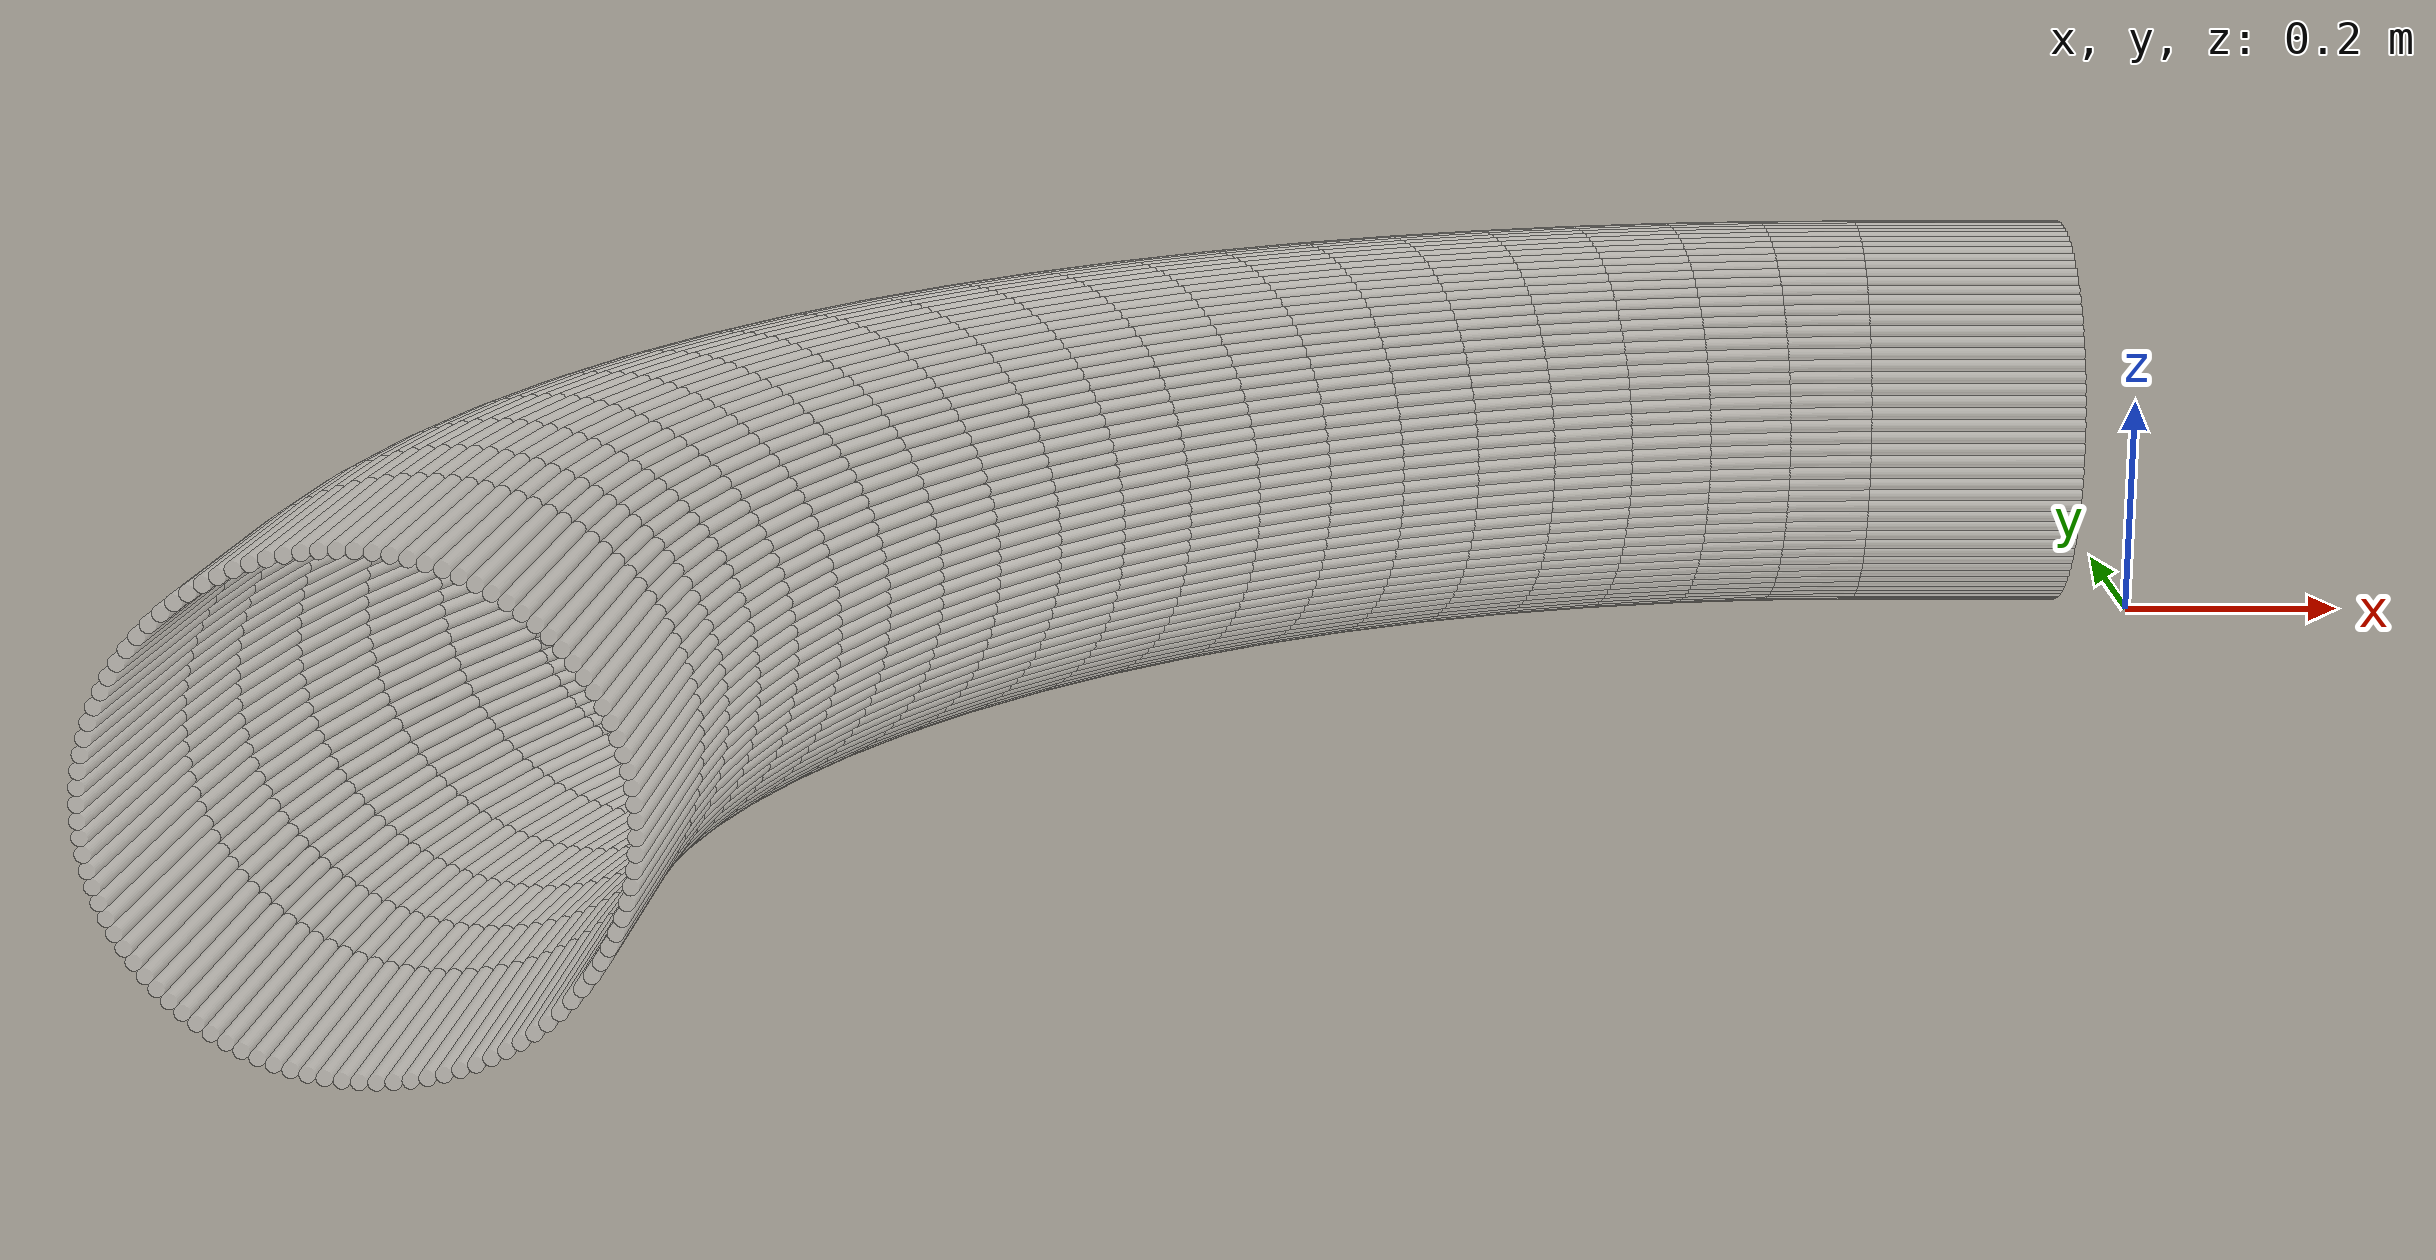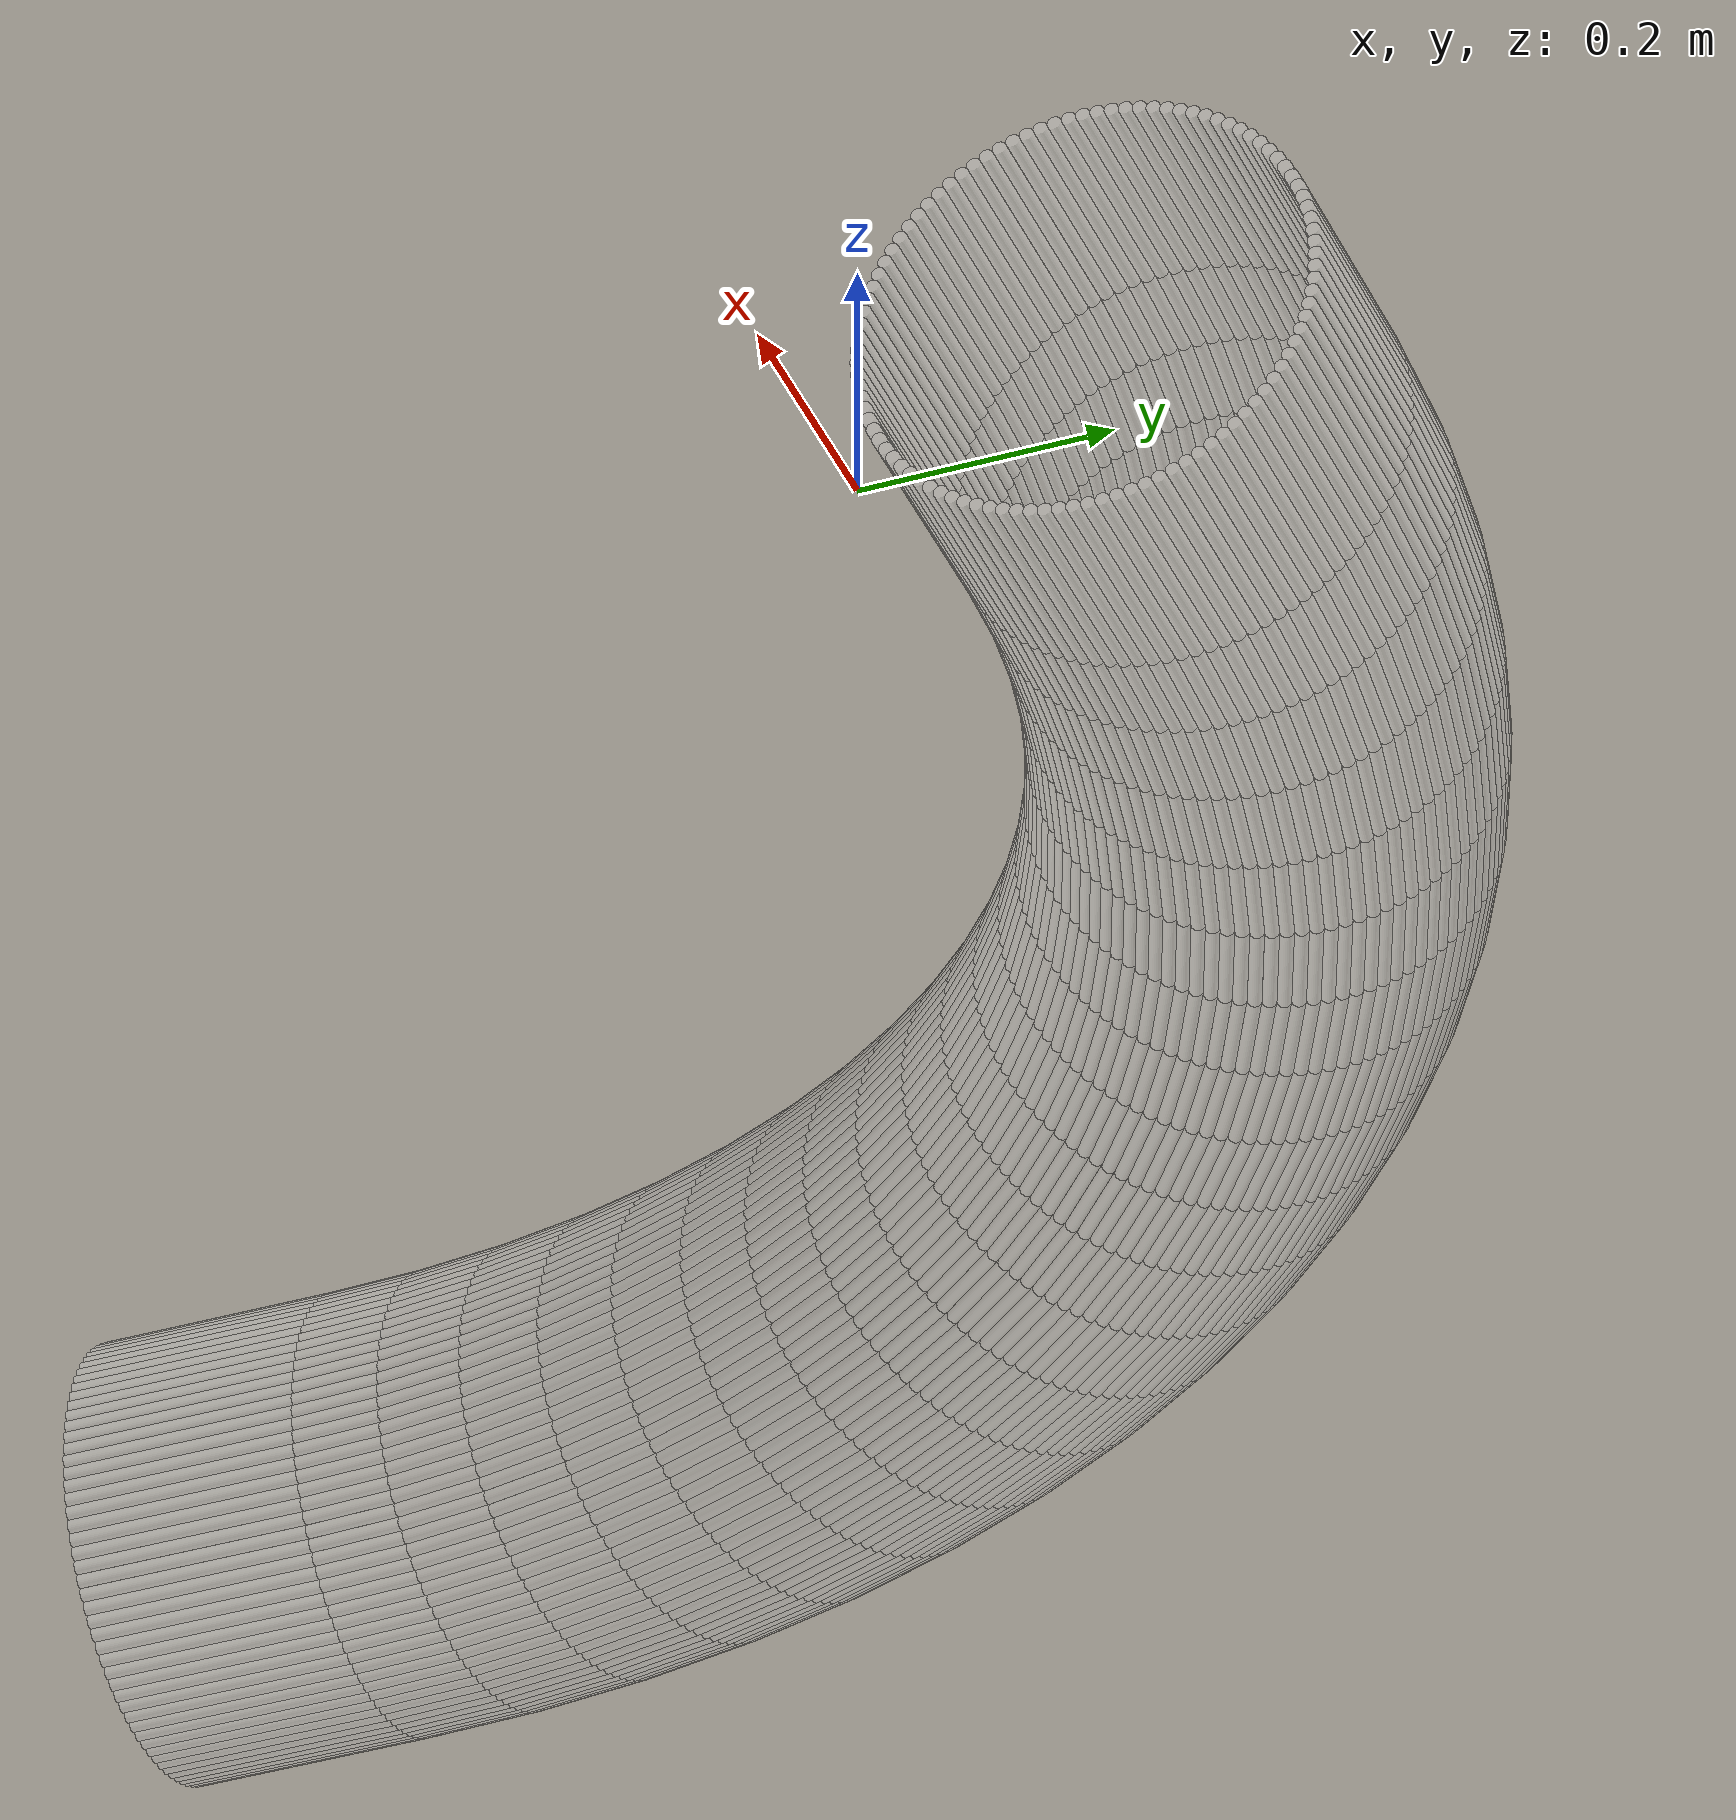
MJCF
<?xml version="1.0" encoding="utf-8"?>
<mujoco>
   <worldbody>
   <body pos="-0.25 -0.94 -0.02" euler="0 0 90">
      <geom euler=" 0 10 0 " fromto="1.28 -0.2 0.18 1.28 0 0.18" rgba="1 1 1 0.35"
            size="0.0056539"
            type="cylinder"/>
      <geom euler=" 0 20 0 " fromto="1.2796 -0.2 0.1913 1.2796 0 0.1913" rgba="1 1 1 0.35"
            size="0.0056539"
            type="cylinder"/>
      <geom euler=" 0 30 0 " fromto="1.2786 -0.2 0.20256 1.2786 0 0.20256"
            rgba="1 1 1 0.35"
            size="0.0056539"
            type="cylinder"/>
      <geom euler=" 0 40 0 " fromto="1.2768 -0.2 0.21373 1.2768 0 0.21373"
            rgba="1 1 1 0.35"
            size="0.0056539"
            type="cylinder"/>
      <geom euler=" 0 50 0 " fromto="1.2743 -0.2 0.22476 1.2743 0 0.22476"
            rgba="1 1 1 0.35"
            size="0.0056539"
            type="cylinder"/>
      <geom euler=" 0 60 0 " fromto="1.2712 -0.2 0.23562 1.2712 0 0.23562"
            rgba="1 1 1 0.35"
            size="0.0056539"
            type="cylinder"/>
      <geom euler=" 0 70 0 " fromto="1.2674 -0.2 0.24626 1.2674 0 0.24626"
            rgba="1 1 1 0.35"
            size="0.0056539"
            type="cylinder"/>
      <geom euler=" 0 80 0 " fromto="1.2629 -0.2 0.25664 1.2629 0 0.25664"
            rgba="1 1 1 0.35"
            size="0.0056539"
            type="cylinder"/>
      <geom euler=" 0 90 0 " fromto="1.2577 -0.2 0.26672 1.2577 0 0.26672"
            rgba="1 1 1 0.35"
            size="0.0056539"
            type="cylinder"/>
      <geom euler=" 0 100 0 " fromto="1.252 -0.2 0.27645 1.252 0 0.27645" rgba="1 1 1 0.35"
            size="0.0056539"
            type="cylinder"/>
      <geom euler=" 0 110 0 " fromto="1.2456 -0.2 0.2858 1.2456 0 0.2858" rgba="1 1 1 0.35"
            size="0.0056539"
            type="cylinder"/>
      <geom euler=" 0 120 0 " fromto="1.2387 -0.2 0.29474 1.2387 0 0.29474"
            rgba="1 1 1 0.35"
            size="0.0056539"
            type="cylinder"/>
      <geom euler=" 0 130 0 " fromto="1.2312 -0.2 0.30322 1.2312 0 0.30322"
            rgba="1 1 1 0.35"
            size="0.0056539"
            type="cylinder"/>
      <geom euler=" 0 140 0 " fromto="1.2232 -0.2 0.31121 1.2232 0 0.31121"
            rgba="1 1 1 0.35"
            size="0.0056539"
            type="cylinder"/>
      <geom euler=" 0 150 0 " fromto="1.2147 -0.2 0.31869 1.2147 0 0.31869"
            rgba="1 1 1 0.35"
            size="0.0056539"
            type="cylinder"/>
      <geom euler=" 0 160 0 " fromto="1.2058 -0.2 0.32562 1.2058 0 0.32562"
            rgba="1 1 1 0.35"
            size="0.0056539"
            type="cylinder"/>
      <geom euler=" 0 170 0 " fromto="1.1964 -0.2 0.33198 1.1964 0 0.33198"
            rgba="1 1 1 0.35"
            size="0.0056539"
            type="cylinder"/>
      <geom euler=" 0 180 0 " fromto="1.1867 -0.2 0.33774 1.1867 0 0.33774"
            rgba="1 1 1 0.35"
            size="0.0056539"
            type="cylinder"/>
      <geom euler=" 0 190 0 " fromto="1.1766 -0.2 0.34287 1.1766 0 0.34287"
            rgba="1 1 1 0.35"
            size="0.0056539"
            type="cylinder"/>
      <geom euler=" 0 200 0 " fromto="1.1663 -0.2 0.34736 1.1663 0 0.34736"
            rgba="1 1 1 0.35"
            size="0.0056539"
            type="cylinder"/>
      <geom euler=" 0 210 0 " fromto="1.1556 -0.2 0.35119 1.1556 0 0.35119"
            rgba="1 1 1 0.35"
            size="0.0056539"
            type="cylinder"/>
      <geom euler=" 0 220 0 " fromto="1.1448 -0.2 0.35434 1.1448 0 0.35434"
            rgba="1 1 1 0.35"
            size="0.0056539"
            type="cylinder"/>
      <geom euler=" 0 230 0 " fromto="1.1337 -0.2 0.35681 1.1337 0 0.35681"
            rgba="1 1 1 0.35"
            size="0.0056539"
            type="cylinder"/>
      <geom euler=" 0 240 0 " fromto="1.1226 -0.2 0.35858 1.1226 0 0.35858"
            rgba="1 1 1 0.35"
            size="0.0056539"
            type="cylinder"/>
      <geom euler=" 0 250 0 " fromto="1.1113 -0.2 0.35964 1.1113 0 0.35964"
            rgba="1 1 1 0.35"
            size="0.0056539"
            type="cylinder"/>
      <geom euler=" 0 260 0 " fromto="1.1 -0.2 0.36 1.1 0 0.36" rgba="1 1 1 0.35"
            size="0.0056539"
            type="cylinder"/>
      <geom euler=" 0 270 0 " fromto="1.0887 -0.2 0.35964 1.0887 0 0.35964"
            rgba="1 1 1 0.35"
            size="0.0056539"
            type="cylinder"/>
      <geom euler=" 0 280 0 " fromto="1.0774 -0.2 0.35858 1.0774 0 0.35858"
            rgba="1 1 1 0.35"
            size="0.0056539"
            type="cylinder"/>
      <geom euler=" 0 290 0 " fromto="1.0663 -0.2 0.35681 1.0663 0 0.35681"
            rgba="1 1 1 0.35"
            size="0.0056539"
            type="cylinder"/>
      <geom euler=" 0 300 0 " fromto="1.0552 -0.2 0.35434 1.0552 0 0.35434"
            rgba="1 1 1 0.35"
            size="0.0056539"
            type="cylinder"/>
      <geom euler=" 0 310 0 " fromto="1.0444 -0.2 0.35119 1.0444 0 0.35119"
            rgba="1 1 1 0.35"
            size="0.0056539"
            type="cylinder"/>
      <geom euler=" 0 320 0 " fromto="1.0337 -0.2 0.34736 1.0337 0 0.34736"
            rgba="1 1 1 0.35"
            size="0.0056539"
            type="cylinder"/>
      <geom euler=" 0 330 0 " fromto="1.0234 -0.2 0.34287 1.0234 0 0.34287"
            rgba="1 1 1 0.35"
            size="0.0056539"
            type="cylinder"/>
      <geom euler=" 0 340 0 " fromto="1.0133 -0.2 0.33774 1.0133 0 0.33774"
            rgba="1 1 1 0.35"
            size="0.0056539"
            type="cylinder"/>
      <geom euler=" 0 350 0 " fromto="1.0036 -0.2 0.33198 1.0036 0 0.33198"
            rgba="1 1 1 0.35"
            size="0.0056539"
            type="cylinder"/>
      <geom euler=" 0 360 0 " fromto="0.9942 -0.2 0.32562 0.9942 0 0.32562"
            rgba="1 1 1 0.35"
            size="0.0056539"
            type="cylinder"/>
      <geom euler=" 0 370 0 " fromto="0.98526 -0.2 0.31869 0.98526 0 0.31869"
            rgba="1 1 1 0.35"
            size="0.0056539"
            type="cylinder"/>
      <geom euler=" 0 380 0 " fromto="0.97678 -0.2 0.31121 0.97678 0 0.31121"
            rgba="1 1 1 0.35"
            size="0.0056539"
            type="cylinder"/>
      <geom euler=" 0 390 0 " fromto="0.96879 -0.2 0.30322 0.96879 0 0.30322"
            rgba="1 1 1 0.35"
            size="0.0056539"
            type="cylinder"/>
      <geom euler=" 0 400 0 " fromto="0.96131 -0.2 0.29474 0.96131 0 0.29474"
            rgba="1 1 1 0.35"
            size="0.0056539"
            type="cylinder"/>
      <geom euler=" 0 410 0 " fromto="0.95438 -0.2 0.2858 0.95438 0 0.2858"
            rgba="1 1 1 0.35"
            size="0.0056539"
            type="cylinder"/>
      <geom euler=" 0 420 0 " fromto="0.94802 -0.2 0.27645 0.94802 0 0.27645"
            rgba="1 1 1 0.35"
            size="0.0056539"
            type="cylinder"/>
      <geom euler=" 0 430 0 " fromto="0.94226 -0.2 0.26672 0.94226 0 0.26672"
            rgba="1 1 1 0.35"
            size="0.0056539"
            type="cylinder"/>
      <geom euler=" 0 440 0 " fromto="0.93713 -0.2 0.25664 0.93713 0 0.25664"
            rgba="1 1 1 0.35"
            size="0.0056539"
            type="cylinder"/>
      <geom euler=" 0 450 0 " fromto="0.93264 -0.2 0.24626 0.93264 0 0.24626"
            rgba="1 1 1 0.35"
            size="0.0056539"
            type="cylinder"/>
      <geom euler=" 0 460 0 " fromto="0.92881 -0.2 0.23562 0.92881 0 0.23562"
            rgba="1 1 1 0.35"
            size="0.0056539"
            type="cylinder"/>
      <geom euler=" 0 470 0 " fromto="0.92566 -0.2 0.22476 0.92566 0 0.22476"
            rgba="1 1 1 0.35"
            size="0.0056539"
            type="cylinder"/>
      <geom euler=" 0 480 0 " fromto="0.92319 -0.2 0.21373 0.92319 0 0.21373"
            rgba="1 1 1 0.35"
            size="0.0056539"
            type="cylinder"/>
      <geom euler=" 0 490 0 " fromto="0.92142 -0.2 0.20256 0.92142 0 0.20256"
            rgba="1 1 1 0.35"
            size="0.0056539"
            type="cylinder"/>
      <geom euler=" 0 500 0 " fromto="0.92036 -0.2 0.1913 0.92036 0 0.1913"
            rgba="1 1 1 0.35"
            size="0.0056539"
            type="cylinder"/>
      <geom euler=" 0 510 0 " fromto="0.92 -0.2 0.18 0.92 0 0.18" rgba="1 1 1 0.35"
            size="0.0056539"
            type="cylinder"/>
      <geom euler=" 0 520 0 " fromto="0.92036 -0.2 0.1687 0.92036 0 0.1687"
            rgba="1 1 1 0.35"
            size="0.0056539"
            type="cylinder"/>
      <geom euler=" 0 530 0 " fromto="0.92142 -0.2 0.15744 0.92142 0 0.15744"
            rgba="1 1 1 0.35"
            size="0.0056539"
            type="cylinder"/>
      <geom euler=" 0 540 0 " fromto="0.92319 -0.2 0.14627 0.92319 0 0.14627"
            rgba="1 1 1 0.35"
            size="0.0056539"
            type="cylinder"/>
      <geom euler=" 0 550 0 " fromto="0.92566 -0.2 0.13524 0.92566 0 0.13524"
            rgba="1 1 1 0.35"
            size="0.0056539"
            type="cylinder"/>
      <geom euler=" 0 560 0 " fromto="0.92881 -0.2 0.12438 0.92881 0 0.12438"
            rgba="1 1 1 0.35"
            size="0.0056539"
            type="cylinder"/>
      <geom euler=" 0 570 0 " fromto="0.93264 -0.2 0.11374 0.93264 0 0.11374"
            rgba="1 1 1 0.35"
            size="0.0056539"
            type="cylinder"/>
      <geom euler=" 0 580 0 " fromto="0.93713 -0.2 0.10336 0.93713 0 0.10336"
            rgba="1 1 1 0.35"
            size="0.0056539"
            type="cylinder"/>
      <geom euler=" 0 590 0 " fromto="0.94226 -0.2 0.093284 0.94226 0 0.093284"
            rgba="1 1 1 0.35"
            size="0.0056539"
            type="cylinder"/>
      <geom euler=" 0 600 0 " fromto="0.94802 -0.2 0.083551 0.94802 0 0.083551"
            rgba="1 1 1 0.35"
            size="0.0056539"
            type="cylinder"/>
      <geom euler=" 0 610 0 " fromto="0.95438 -0.2 0.074199 0.95438 0 0.074199"
            rgba="1 1 1 0.35"
            size="0.0056539"
            type="cylinder"/>
      <geom euler=" 0 620 0 " fromto="0.96131 -0.2 0.065264 0.96131 0 0.065264"
            rgba="1 1 1 0.35"
            size="0.0056539"
            type="cylinder"/>
      <geom euler=" 0 630 0 " fromto="0.96879 -0.2 0.056782 0.96879 0 0.056782"
            rgba="1 1 1 0.35"
            size="0.0056539"
            type="cylinder"/>
      <geom euler=" 0 640 0 " fromto="0.97678 -0.2 0.048786 0.97678 0 0.048786"
            rgba="1 1 1 0.35"
            size="0.0056539"
            type="cylinder"/>
      <geom euler=" 0 650 0 " fromto="0.98526 -0.2 0.041308 0.98526 0 0.041308"
            rgba="1 1 1 0.35"
            size="0.0056539"
            type="cylinder"/>
      <geom euler=" 0 660 0 " fromto="0.9942 -0.2 0.034377 0.9942 0 0.034377"
            rgba="1 1 1 0.35"
            size="0.0056539"
            type="cylinder"/>
      <geom euler=" 0 670 0 " fromto="1.0036 -0.2 0.028021 1.0036 0 0.028021"
            rgba="1 1 1 0.35"
            size="0.0056539"
            type="cylinder"/>
      <geom euler=" 0 680 0 " fromto="1.0133 -0.2 0.022265 1.0133 0 0.022265"
            rgba="1 1 1 0.35"
            size="0.0056539"
            type="cylinder"/>
      <geom euler=" 0 690 0 " fromto="1.0234 -0.2 0.017131 1.0234 0 0.017131"
            rgba="1 1 1 0.35"
            size="0.0056539"
            type="cylinder"/>
      <geom euler=" 0 700 0 " fromto="1.0337 -0.2 0.01264 1.0337 0 0.01264"
            rgba="1 1 1 0.35"
            size="0.0056539"
            type="cylinder"/>
      <geom euler=" 0 710 0 " fromto="1.0444 -0.2 0.0088098 1.0444 0 0.0088098"
            rgba="1 1 1 0.35"
            size="0.0056539"
            type="cylinder"/>
      <geom euler=" 0 720 0 " fromto="1.0552 -0.2 0.005655 1.0552 0 0.005655"
            rgba="1 1 1 0.35"
            size="0.0056539"
            type="cylinder"/>
      <geom euler=" 0 730 0 " fromto="1.0663 -0.2 0.0031883 1.0663 0 0.0031883"
            rgba="1 1 1 0.35"
            size="0.0056539"
            type="cylinder"/>
      <geom euler=" 0 740 0 " fromto="1.0774 -0.2 0.0014194 1.0774 0 0.0014194"
            rgba="1 1 1 0.35"
            size="0.0056539"
            type="cylinder"/>
      <geom euler=" 0 750 0 " fromto="1.0887 -0.2 0.00035519 1.0887 0 0.00035519"
            rgba="1 1 1 0.35"
            size="0.0056539"
            type="cylinder"/>
      <geom euler=" 0 760 0 " fromto="1.1 -0.2 0 1.1 0 0" rgba="1 1 1 0.35"
            size="0.0056539"
            type="cylinder"/>
      <geom euler=" 0 770 0 " fromto="1.1113 -0.2 0.00035519 1.1113 0 0.00035519"
            rgba="1 1 1 0.35"
            size="0.0056539"
            type="cylinder"/>
      <geom euler=" 0 780 0 " fromto="1.1226 -0.2 0.0014194 1.1226 0 0.0014194"
            rgba="1 1 1 0.35"
            size="0.0056539"
            type="cylinder"/>
      <geom euler=" 0 790 0 " fromto="1.1337 -0.2 0.0031883 1.1337 0 0.0031883"
            rgba="1 1 1 0.35"
            size="0.0056539"
            type="cylinder"/>
      <geom euler=" 0 800 0 " fromto="1.1448 -0.2 0.005655 1.1448 0 0.005655"
            rgba="1 1 1 0.35"
            size="0.0056539"
            type="cylinder"/>
      <geom euler=" 0 810 0 " fromto="1.1556 -0.2 0.0088098 1.1556 0 0.0088098"
            rgba="1 1 1 0.35"
            size="0.0056539"
            type="cylinder"/>
      <geom euler=" 0 820 0 " fromto="1.1663 -0.2 0.01264 1.1663 0 0.01264"
            rgba="1 1 1 0.35"
            size="0.0056539"
            type="cylinder"/>
      <geom euler=" 0 830 0 " fromto="1.1766 -0.2 0.017131 1.1766 0 0.017131"
            rgba="1 1 1 0.35"
            size="0.0056539"
            type="cylinder"/>
      <geom euler=" 0 840 0 " fromto="1.1867 -0.2 0.022265 1.1867 0 0.022265"
            rgba="1 1 1 0.35"
            size="0.0056539"
            type="cylinder"/>
      <geom euler=" 0 850 0 " fromto="1.1964 -0.2 0.028021 1.1964 0 0.028021"
            rgba="1 1 1 0.35"
            size="0.0056539"
            type="cylinder"/>
      <geom euler=" 0 860 0 " fromto="1.2058 -0.2 0.034377 1.2058 0 0.034377"
            rgba="1 1 1 0.35"
            size="0.0056539"
            type="cylinder"/>
      <geom euler=" 0 870 0 " fromto="1.2147 -0.2 0.041308 1.2147 0 0.041308"
            rgba="1 1 1 0.35"
            size="0.0056539"
            type="cylinder"/>
      <geom euler=" 0 880 0 " fromto="1.2232 -0.2 0.048786 1.2232 0 0.048786"
            rgba="1 1 1 0.35"
            size="0.0056539"
            type="cylinder"/>
      <geom euler=" 0 890 0 " fromto="1.2312 -0.2 0.056782 1.2312 0 0.056782"
            rgba="1 1 1 0.35"
            size="0.0056539"
            type="cylinder"/>
      <geom euler=" 0 900 0 " fromto="1.2387 -0.2 0.065264 1.2387 0 0.065264"
            rgba="1 1 1 0.35"
            size="0.0056539"
            type="cylinder"/>
      <geom euler=" 0 910 0 " fromto="1.2456 -0.2 0.074199 1.2456 0 0.074199"
            rgba="1 1 1 0.35"
            size="0.0056539"
            type="cylinder"/>
      <geom euler=" 0 920 0 " fromto="1.252 -0.2 0.083551 1.252 0 0.083551"
            rgba="1 1 1 0.35"
            size="0.0056539"
            type="cylinder"/>
      <geom euler=" 0 930 0 " fromto="1.2577 -0.2 0.093284 1.2577 0 0.093284"
            rgba="1 1 1 0.35"
            size="0.0056539"
            type="cylinder"/>
      <geom euler=" 0 940 0 " fromto="1.2629 -0.2 0.10336 1.2629 0 0.10336"
            rgba="1 1 1 0.35"
            size="0.0056539"
            type="cylinder"/>
      <geom euler=" 0 950 0 " fromto="1.2674 -0.2 0.11374 1.2674 0 0.11374"
            rgba="1 1 1 0.35"
            size="0.0056539"
            type="cylinder"/>
      <geom euler=" 0 960 0 " fromto="1.2712 -0.2 0.12438 1.2712 0 0.12438"
            rgba="1 1 1 0.35"
            size="0.0056539"
            type="cylinder"/>
      <geom euler=" 0 970 0 " fromto="1.2743 -0.2 0.13524 1.2743 0 0.13524"
            rgba="1 1 1 0.35"
            size="0.0056539"
            type="cylinder"/>
      <geom euler=" 0 980 0 " fromto="1.2768 -0.2 0.14627 1.2768 0 0.14627"
            rgba="1 1 1 0.35"
            size="0.0056539"
            type="cylinder"/>
      <geom euler=" 0 990 0 " fromto="1.2786 -0.2 0.15744 1.2786 0 0.15744"
            rgba="1 1 1 0.35"
            size="0.0056539"
            type="cylinder"/>
      <geom euler=" 0 1000 0 " fromto="1.2796 -0.2 0.1687 1.2796 0 0.1687"
            rgba="1 1 1 0.35"
            size="0.0056539"
            type="cylinder"/>
      <geom euler=" 0 10 0 " fromto="1.28 0 0.18 1.2756 0.1057 0.18" rgba="1 1 1 0.35"
            size="0.0056539"
            type="cylinder"/>
      <geom euler=" 0 20 0 " fromto="1.2796 0 0.1913 1.2753 0.10567 0.1913"
            rgba="1 1 1 0.35"
            size="0.0056539"
            type="cylinder"/>
      <geom euler=" 0 30 0 " fromto="1.2786 0 0.20256 1.2742 0.10558 0.20256"
            rgba="1 1 1 0.35"
            size="0.0056539"
            type="cylinder"/>
      <geom euler=" 0 40 0 " fromto="1.2768 0 0.21373 1.2725 0.10544 0.21373"
            rgba="1 1 1 0.35"
            size="0.0056539"
            type="cylinder"/>
      <geom euler=" 0 50 0 " fromto="1.2743 0 0.22476 1.27 0.10523 0.22476"
            rgba="1 1 1 0.35"
            size="0.0056539"
            type="cylinder"/>
      <geom euler=" 0 60 0 " fromto="1.2712 0 0.23562 1.2668 0.10497 0.23562"
            rgba="1 1 1 0.35"
            size="0.0056539"
            type="cylinder"/>
      <geom euler=" 0 70 0 " fromto="1.2674 0 0.24626 1.263 0.10466 0.24626"
            rgba="1 1 1 0.35"
            size="0.0056539"
            type="cylinder"/>
      <geom euler=" 0 80 0 " fromto="1.2629 0 0.25664 1.2586 0.10429 0.25664"
            rgba="1 1 1 0.35"
            size="0.0056539"
            type="cylinder"/>
      <geom euler=" 0 90 0 " fromto="1.2577 0 0.26672 1.2534 0.10386 0.26672"
            rgba="1 1 1 0.35"
            size="0.0056539"
            type="cylinder"/>
      <geom euler=" 0 100 0 " fromto="1.252 0 0.27645 1.2477 0.10339 0.27645"
            rgba="1 1 1 0.35"
            size="0.0056539"
            type="cylinder"/>
      <geom euler=" 0 110 0 " fromto="1.2456 0 0.2858 1.2414 0.10286 0.2858"
            rgba="1 1 1 0.35"
            size="0.0056539"
            type="cylinder"/>
      <geom euler=" 0 120 0 " fromto="1.2387 0 0.29474 1.2345 0.10229 0.29474"
            rgba="1 1 1 0.35"
            size="0.0056539"
            type="cylinder"/>
      <geom euler=" 0 130 0 " fromto="1.2312 0 0.30322 1.227 0.10167 0.30322"
            rgba="1 1 1 0.35"
            size="0.0056539"
            type="cylinder"/>
      <geom euler=" 0 140 0 " fromto="1.2232 0 0.31121 1.219 0.10101 0.31121"
            rgba="1 1 1 0.35"
            size="0.0056539"
            type="cylinder"/>
      <geom euler=" 0 150 0 " fromto="1.2147 0 0.31869 1.2106 0.10031 0.31869"
            rgba="1 1 1 0.35"
            size="0.0056539"
            type="cylinder"/>
      <geom euler=" 0 160 0 " fromto="1.2058 0 0.32562 1.2017 0.099574 0.32562"
            rgba="1 1 1 0.35"
            size="0.0056539"
            type="cylinder"/>
      <geom euler=" 0 170 0 " fromto="1.1964 0 0.33198 1.1924 0.098802 0.33198"
            rgba="1 1 1 0.35"
            size="0.0056539"
            type="cylinder"/>
      <geom euler=" 0 180 0 " fromto="1.1867 0 0.33774 1.1827 0.097998 0.33774"
            rgba="1 1 1 0.35"
            size="0.0056539"
            type="cylinder"/>
      <geom euler=" 0 190 0 " fromto="1.1766 0 0.34287 1.1726 0.097166 0.34287"
            rgba="1 1 1 0.35"
            size="0.0056539"
            type="cylinder"/>
      <geom euler=" 0 200 0 " fromto="1.1663 0 0.34736 1.1623 0.096309 0.34736"
            rgba="1 1 1 0.35"
            size="0.0056539"
            type="cylinder"/>
      <geom euler=" 0 210 0 " fromto="1.1556 0 0.35119 1.1517 0.095431 0.35119"
            rgba="1 1 1 0.35"
            size="0.0056539"
            type="cylinder"/>
      <geom euler=" 0 220 0 " fromto="1.1448 0 0.35434 1.1409 0.094534 0.35434"
            rgba="1 1 1 0.35"
            size="0.0056539"
            type="cylinder"/>
      <geom euler=" 0 230 0 " fromto="1.1337 0 0.35681 1.1299 0.093623 0.35681"
            rgba="1 1 1 0.35"
            size="0.0056539"
            type="cylinder"/>
      <geom euler=" 0 240 0 " fromto="1.1226 0 0.35858 1.1187 0.0927 0.35858"
            rgba="1 1 1 0.35"
            size="0.0056539"
            type="cylinder"/>
      <geom euler=" 0 250 0 " fromto="1.1113 0 0.35964 1.1075 0.091771 0.35964"
            rgba="1 1 1 0.35"
            size="0.0056539"
            type="cylinder"/>
      <geom euler=" 0 260 0 " fromto="1.1 0 0.36 1.0962 0.090837 0.36" rgba="1 1 1 0.35"
            size="0.0056539"
            type="cylinder"/>
      <geom euler=" 0 270 0 " fromto="1.0887 0 0.35964 1.085 0.089904 0.35964"
            rgba="1 1 1 0.35"
            size="0.0056539"
            type="cylinder"/>
      <geom euler=" 0 280 0 " fromto="1.0774 0 0.35858 1.0738 0.088974 0.35858"
            rgba="1 1 1 0.35"
            size="0.0056539"
            type="cylinder"/>
      <geom euler=" 0 290 0 " fromto="1.0663 0 0.35681 1.0626 0.088052 0.35681"
            rgba="1 1 1 0.35"
            size="0.0056539"
            type="cylinder"/>
      <geom euler=" 0 300 0 " fromto="1.0552 0 0.35434 1.0516 0.087141 0.35434"
            rgba="1 1 1 0.35"
            size="0.0056539"
            type="cylinder"/>
      <geom euler=" 0 310 0 " fromto="1.0444 0 0.35119 1.0408 0.086244 0.35119"
            rgba="1 1 1 0.35"
            size="0.0056539"
            type="cylinder"/>
      <geom euler=" 0 320 0 " fromto="1.0337 0 0.34736 1.0302 0.085365 0.34736"
            rgba="1 1 1 0.35"
            size="0.0056539"
            type="cylinder"/>
      <geom euler=" 0 330 0 " fromto="1.0234 0 0.34287 1.0199 0.084508 0.34287"
            rgba="1 1 1 0.35"
            size="0.0056539"
            type="cylinder"/>
      <geom euler=" 0 340 0 " fromto="1.0133 0 0.33774 1.0098 0.083676 0.33774"
            rgba="1 1 1 0.35"
            size="0.0056539"
            type="cylinder"/>
      <geom euler=" 0 350 0 " fromto="1.0036 0 0.33198 1.0001 0.082873 0.33198"
            rgba="1 1 1 0.35"
            size="0.0056539"
            type="cylinder"/>
      <geom euler=" 0 360 0 " fromto="0.9942 0 0.32562 0.9908 0.0821 0.32562"
            rgba="1 1 1 0.35"
            size="0.0056539"
            type="cylinder"/>
      <geom euler=" 0 370 0 " fromto="0.98526 0 0.31869 0.9819 0.081362 0.31869"
            rgba="1 1 1 0.35"
            size="0.0056539"
            type="cylinder"/>
      <geom euler=" 0 380 0 " fromto="0.97678 0 0.31121 0.97345 0.080662 0.31121"
            rgba="1 1 1 0.35"
            size="0.0056539"
            type="cylinder"/>
      <geom euler=" 0 390 0 " fromto="0.96879 0 0.30322 0.96548 0.080002 0.30322"
            rgba="1 1 1 0.35"
            size="0.0056539"
            type="cylinder"/>
      <geom euler=" 0 400 0 " fromto="0.96131 0 0.29474 0.95802 0.079384 0.29474"
            rgba="1 1 1 0.35"
            size="0.0056539"
            type="cylinder"/>
      <geom euler=" 0 410 0 " fromto="0.95438 0 0.2858 0.95112 0.078812 0.2858"
            rgba="1 1 1 0.35"
            size="0.0056539"
            type="cylinder"/>
      <geom euler=" 0 420 0 " fromto="0.94802 0 0.27645 0.94478 0.078287 0.27645"
            rgba="1 1 1 0.35"
            size="0.0056539"
            type="cylinder"/>
      <geom euler=" 0 430 0 " fromto="0.94226 0 0.26672 0.93905 0.077812 0.26672"
            rgba="1 1 1 0.35"
            size="0.0056539"
            type="cylinder"/>
      <geom euler=" 0 440 0 " fromto="0.93713 0 0.25664 0.93393 0.077388 0.25664"
            rgba="1 1 1 0.35"
            size="0.0056539"
            type="cylinder"/>
      <geom euler=" 0 450 0 " fromto="0.93264 0 0.24626 0.92945 0.077017 0.24626"
            rgba="1 1 1 0.35"
            size="0.0056539"
            type="cylinder"/>
      <geom euler=" 0 460 0 " fromto="0.92881 0 0.23562 0.92564 0.076701 0.23562"
            rgba="1 1 1 0.35"
            size="0.0056539"
            type="cylinder"/>
      <geom euler=" 0 470 0 " fromto="0.92566 0 0.22476 0.92249 0.07644 0.22476"
            rgba="1 1 1 0.35"
            size="0.0056539"
            type="cylinder"/>
      <geom euler=" 0 480 0 " fromto="0.92319 0 0.21373 0.92004 0.076236 0.21373"
            rgba="1 1 1 0.35"
            size="0.0056539"
            type="cylinder"/>
      <geom euler=" 0 490 0 " fromto="0.92142 0 0.20256 0.91827 0.07609 0.20256"
            rgba="1 1 1 0.35"
            size="0.0056539"
            type="cylinder"/>
      <geom euler=" 0 500 0 " fromto="0.92036 0 0.1913 0.91721 0.076002 0.1913"
            rgba="1 1 1 0.35"
            size="0.0056539"
            type="cylinder"/>
      <geom euler=" 0 510 0 " fromto="0.92 0 0.18 0.91686 0.075973 0.18" rgba="1 1 1 0.35"
            size="0.0056539"
            type="cylinder"/>
      <geom euler=" 0 520 0 " fromto="0.92036 0 0.1687 0.91721 0.076002 0.1687"
            rgba="1 1 1 0.35"
            size="0.0056539"
            type="cylinder"/>
      <geom euler=" 0 530 0 " fromto="0.92142 0 0.15744 0.91827 0.07609 0.15744"
            rgba="1 1 1 0.35"
            size="0.0056539"
            type="cylinder"/>
      <geom euler=" 0 540 0 " fromto="0.92319 0 0.14627 0.92004 0.076236 0.14627"
            rgba="1 1 1 0.35"
            size="0.0056539"
            type="cylinder"/>
      <geom euler=" 0 550 0 " fromto="0.92566 0 0.13524 0.92249 0.07644 0.13524"
            rgba="1 1 1 0.35"
            size="0.0056539"
            type="cylinder"/>
      <geom euler=" 0 560 0 " fromto="0.92881 0 0.12438 0.92564 0.076701 0.12438"
            rgba="1 1 1 0.35"
            size="0.0056539"
            type="cylinder"/>
      <geom euler=" 0 570 0 " fromto="0.93264 0 0.11374 0.92945 0.077017 0.11374"
            rgba="1 1 1 0.35"
            size="0.0056539"
            type="cylinder"/>
      <geom euler=" 0 580 0 " fromto="0.93713 0 0.10336 0.93393 0.077388 0.10336"
            rgba="1 1 1 0.35"
            size="0.0056539"
            type="cylinder"/>
      <geom euler=" 0 590 0 " fromto="0.94226 0 0.093284 0.93905 0.077812 0.093284"
            rgba="1 1 1 0.35"
            size="0.0056539"
            type="cylinder"/>
      <geom euler=" 0 600 0 " fromto="0.94802 0 0.083551 0.94478 0.078287 0.083551"
            rgba="1 1 1 0.35"
            size="0.0056539"
            type="cylinder"/>
      <geom euler=" 0 610 0 " fromto="0.95438 0 0.074199 0.95112 0.078812 0.074199"
            rgba="1 1 1 0.35"
            size="0.0056539"
            type="cylinder"/>
      <geom euler=" 0 620 0 " fromto="0.96131 0 0.065264 0.95802 0.079384 0.065264"
            rgba="1 1 1 0.35"
            size="0.0056539"
            type="cylinder"/>
      <geom euler=" 0 630 0 " fromto="0.96879 0 0.056782 0.96548 0.080002 0.056782"
            rgba="1 1 1 0.35"
            size="0.0056539"
            type="cylinder"/>
      <geom euler=" 0 640 0 " fromto="0.97678 0 0.048786 0.97345 0.080662 0.048786"
            rgba="1 1 1 0.35"
            size="0.0056539"
            type="cylinder"/>
      <geom euler=" 0 650 0 " fromto="0.98526 0 0.041308 0.9819 0.081362 0.041308"
            rgba="1 1 1 0.35"
            size="0.0056539"
            type="cylinder"/>
      <geom euler=" 0 660 0 " fromto="0.9942 0 0.034377 0.9908 0.0821 0.034377"
            rgba="1 1 1 0.35"
            size="0.0056539"
            type="cylinder"/>
      <geom euler=" 0 670 0 " fromto="1.0036 0 0.028021 1.0001 0.082873 0.028021"
            rgba="1 1 1 0.35"
            size="0.0056539"
            type="cylinder"/>
      <geom euler=" 0 680 0 " fromto="1.0133 0 0.022265 1.0098 0.083676 0.022265"
            rgba="1 1 1 0.35"
            size="0.0056539"
            type="cylinder"/>
      <geom euler=" 0 690 0 " fromto="1.0234 0 0.017131 1.0199 0.084508 0.017131"
            rgba="1 1 1 0.35"
            size="0.0056539"
            type="cylinder"/>
      <geom euler=" 0 700 0 " fromto="1.0337 0 0.01264 1.0302 0.085365 0.01264"
            rgba="1 1 1 0.35"
            size="0.0056539"
            type="cylinder"/>
      <geom euler=" 0 710 0 " fromto="1.0444 0 0.0088098 1.0408 0.086244 0.0088098"
            rgba="1 1 1 0.35"
            size="0.0056539"
            type="cylinder"/>
      <geom euler=" 0 720 0 " fromto="1.0552 0 0.005655 1.0516 0.087141 0.005655"
            rgba="1 1 1 0.35"
            size="0.0056539"
            type="cylinder"/>
      <geom euler=" 0 730 0 " fromto="1.0663 0 0.0031883 1.0626 0.088052 0.0031883"
            rgba="1 1 1 0.35"
            size="0.0056539"
            type="cylinder"/>
      <geom euler=" 0 740 0 " fromto="1.0774 0 0.0014194 1.0738 0.088974 0.0014194"
            rgba="1 1 1 0.35"
            size="0.0056539"
            type="cylinder"/>
      <geom euler=" 0 750 0 " fromto="1.0887 0 0.00035519 1.085 0.089904 0.00035519"
            rgba="1 1 1 0.35"
            size="0.0056539"
            type="cylinder"/>
      <geom euler=" 0 760 0 " fromto="1.1 0 0 1.0962 0.090837 0" rgba="1 1 1 0.35"
            size="0.0056539"
            type="cylinder"/>
      <geom euler=" 0 770 0 " fromto="1.1113 0 0.00035519 1.1075 0.091771 0.00035519"
            rgba="1 1 1 0.35"
            size="0.0056539"
            type="cylinder"/>
      <geom euler=" 0 780 0 " fromto="1.1226 0 0.0014194 1.1187 0.0927 0.0014194"
            rgba="1 1 1 0.35"
            size="0.0056539"
            type="cylinder"/>
      <geom euler=" 0 790 0 " fromto="1.1337 0 0.0031883 1.1299 0.093623 0.0031883"
            rgba="1 1 1 0.35"
            size="0.0056539"
            type="cylinder"/>
      <geom euler=" 0 800 0 " fromto="1.1448 0 0.005655 1.1409 0.094534 0.005655"
            rgba="1 1 1 0.35"
            size="0.0056539"
            type="cylinder"/>
      <geom euler=" 0 810 0 " fromto="1.1556 0 0.0088098 1.1517 0.095431 0.0088098"
            rgba="1 1 1 0.35"
            size="0.0056539"
            type="cylinder"/>
      <geom euler=" 0 820 0 " fromto="1.1663 0 0.01264 1.1623 0.096309 0.01264"
            rgba="1 1 1 0.35"
            size="0.0056539"
            type="cylinder"/>
      <geom euler=" 0 830 0 " fromto="1.1766 0 0.017131 1.1726 0.097166 0.017131"
            rgba="1 1 1 0.35"
            size="0.0056539"
            type="cylinder"/>
      <geom euler=" 0 840 0 " fromto="1.1867 0 0.022265 1.1827 0.097998 0.022265"
            rgba="1 1 1 0.35"
            size="0.0056539"
            type="cylinder"/>
      <geom euler=" 0 850 0 " fromto="1.1964 0 0.028021 1.1924 0.098802 0.028021"
            rgba="1 1 1 0.35"
            size="0.0056539"
            type="cylinder"/>
      <geom euler=" 0 860 0 " fromto="1.2058 0 0.034377 1.2017 0.099574 0.034377"
            rgba="1 1 1 0.35"
            size="0.0056539"
            type="cylinder"/>
      <geom euler=" 0 870 0 " fromto="1.2147 0 0.041308 1.2106 0.10031 0.041308"
            rgba="1 1 1 0.35"
            size="0.0056539"
            type="cylinder"/>
      <geom euler=" 0 880 0 " fromto="1.2232 0 0.048786 1.219 0.10101 0.048786"
            rgba="1 1 1 0.35"
            size="0.0056539"
            type="cylinder"/>
      <geom euler=" 0 890 0 " fromto="1.2312 0 0.056782 1.227 0.10167 0.056782"
            rgba="1 1 1 0.35"
            size="0.0056539"
            type="cylinder"/>
      <geom euler=" 0 900 0 " fromto="1.2387 0 0.065264 1.2345 0.10229 0.065264"
            rgba="1 1 1 0.35"
            size="0.0056539"
            type="cylinder"/>
      <geom euler=" 0 910 0 " fromto="1.2456 0 0.074199 1.2414 0.10286 0.074199"
            rgba="1 1 1 0.35"
            size="0.0056539"
            type="cylinder"/>
      <geom euler=" 0 920 0 " fromto="1.252 0 0.083551 1.2477 0.10339 0.083551"
            rgba="1 1 1 0.35"
            size="0.0056539"
            type="cylinder"/>
      <geom euler=" 0 930 0 " fromto="1.2577 0 0.093284 1.2534 0.10386 0.093284"
            rgba="1 1 1 0.35"
            size="0.0056539"
            type="cylinder"/>
      <geom euler=" 0 940 0 " fromto="1.2629 0 0.10336 1.2586 0.10429 0.10336"
            rgba="1 1 1 0.35"
            size="0.0056539"
            type="cylinder"/>
      <geom euler=" 0 950 0 " fromto="1.2674 0 0.11374 1.263 0.10466 0.11374"
            rgba="1 1 1 0.35"
            size="0.0056539"
            type="cylinder"/>
      <geom euler=" 0 960 0 " fromto="1.2712 0 0.12438 1.2668 0.10497 0.12438"
            rgba="1 1 1 0.35"
            size="0.0056539"
            type="cylinder"/>
      <geom euler=" 0 970 0 " fromto="1.2743 0 0.13524 1.27 0.10523 0.13524"
            rgba="1 1 1 0.35"
            size="0.0056539"
            type="cylinder"/>
      <geom euler=" 0 980 0 " fromto="1.2768 0 0.14627 1.2725 0.10544 0.14627"
            rgba="1 1 1 0.35"
            size="0.0056539"
            type="cylinder"/>
      <geom euler=" 0 990 0 " fromto="1.2786 0 0.15744 1.2742 0.10558 0.15744"
            rgba="1 1 1 0.35"
            size="0.0056539"
            type="cylinder"/>
      <geom euler=" 0 1000 0 " fromto="1.2796 0 0.1687 1.2753 0.10567 0.1687"
            rgba="1 1 1 0.35"
            size="0.0056539"
            type="cylinder"/>
      <geom euler=" 0 10 0 " fromto="1.2756 0.1057 0.18 1.2625 0.21068 0.18"
            rgba="1 1 1 0.35"
            size="0.0056539"
            type="cylinder"/>
      <geom euler=" 0 20 0 " fromto="1.2753 0.10567 0.1913 1.2622 0.21062 0.1913"
            rgba="1 1 1 0.35"
            size="0.0056539"
            type="cylinder"/>
      <geom euler=" 0 30 0 " fromto="1.2742 0.10558 0.20256 1.2611 0.21045 0.20256"
            rgba="1 1 1 0.35"
            size="0.0056539"
            type="cylinder"/>
      <geom euler=" 0 40 0 " fromto="1.2725 0.10544 0.21373 1.2594 0.21016 0.21373"
            rgba="1 1 1 0.35"
            size="0.0056539"
            type="cylinder"/>
      <geom euler=" 0 50 0 " fromto="1.27 0.10523 0.22476 1.257 0.20975 0.22476"
            rgba="1 1 1 0.35"
            size="0.0056539"
            type="cylinder"/>
      <geom euler=" 0 60 0 " fromto="1.2668 0.10497 0.23562 1.2539 0.20923 0.23562"
            rgba="1 1 1 0.35"
            size="0.0056539"
            type="cylinder"/>
      <geom euler=" 0 70 0 " fromto="1.263 0.10466 0.24626 1.2501 0.2086 0.24626"
            rgba="1 1 1 0.35"
            size="0.0056539"
            type="cylinder"/>
      <geom euler=" 0 80 0 " fromto="1.2586 0.10429 0.25664 1.2456 0.20786 0.25664"
            rgba="1 1 1 0.35"
            size="0.0056539"
            type="cylinder"/>
      <geom euler=" 0 90 0 " fromto="1.2534 0.10386 0.26672 1.2406 0.20702 0.26672"
            rgba="1 1 1 0.35"
            size="0.0056539"
            type="cylinder"/>
      <geom euler=" 0 100 0 " fromto="1.2477 0.10339 0.27645 1.2349 0.20607 0.27645"
            rgba="1 1 1 0.35"
            size="0.0056539"
            type="cylinder"/>
      <geom euler=" 0 110 0 " fromto="1.2414 0.10286 0.2858 1.2286 0.20502 0.2858"
            rgba="1 1 1 0.35"
            size="0.0056539"
            type="cylinder"/>
      <geom euler=" 0 120 0 " fromto="1.2345 0.10229 0.29474 1.2218 0.20388 0.29474"
            rgba="1 1 1 0.35"
            size="0.0056539"
            type="cylinder"/>
      <geom euler=" 0 130 0 " fromto="1.227 0.10167 0.30322 1.2144 0.20265 0.30322"
            rgba="1 1 1 0.35"
            size="0.0056539"
            type="cylinder"/>
      <geom euler=" 0 140 0 " fromto="1.219 0.10101 0.31121 1.2065 0.20134 0.31121"
            rgba="1 1 1 0.35"
            size="0.0056539"
            type="cylinder"/>
      <geom euler=" 0 150 0 " fromto="1.2106 0.10031 0.31869 1.1982 0.19994 0.31869"
            rgba="1 1 1 0.35"
            size="0.0056539"
            type="cylinder"/>
      <geom euler=" 0 160 0 " fromto="1.2017 0.099574 0.32562 1.1894 0.19847 0.32562"
            rgba="1 1 1 0.35"
            size="0.0056539"
            type="cylinder"/>
      <geom euler=" 0 170 0 " fromto="1.1924 0.098802 0.33198 1.1801 0.19693 0.33198"
            rgba="1 1 1 0.35"
            size="0.0056539"
            type="cylinder"/>
      <geom euler=" 0 180 0 " fromto="1.1827 0.097998 0.33774 1.1705 0.19533 0.33774"
            rgba="1 1 1 0.35"
            size="0.0056539"
            type="cylinder"/>
      <geom euler=" 0 190 0 " fromto="1.1726 0.097166 0.34287 1.1606 0.19367 0.34287"
            rgba="1 1 1 0.35"
            size="0.0056539"
            type="cylinder"/>
      <geom euler=" 0 200 0 " fromto="1.1623 0.096309 0.34736 1.1504 0.19196 0.34736"
            rgba="1 1 1 0.35"
            size="0.0056539"
            type="cylinder"/>
      <geom euler=" 0 210 0 " fromto="1.1517 0.095431 0.35119 1.1399 0.19021 0.35119"
            rgba="1 1 1 0.35"
            size="0.0056539"
            type="cylinder"/>
      <geom euler=" 0 220 0 " fromto="1.1409 0.094534 0.35434 1.1292 0.18842 0.35434"
            rgba="1 1 1 0.35"
            size="0.0056539"
            type="cylinder"/>
      <geom euler=" 0 230 0 " fromto="1.1299 0.093623 0.35681 1.1183 0.18661 0.35681"
            rgba="1 1 1 0.35"
            size="0.0056539"
            type="cylinder"/>
      <geom euler=" 0 240 0 " fromto="1.1187 0.0927 0.35858 1.1072 0.18477 0.35858"
            rgba="1 1 1 0.35"
            size="0.0056539"
            type="cylinder"/>
      <geom euler=" 0 250 0 " fromto="1.1075 0.091771 0.35964 1.0961 0.18291 0.35964"
            rgba="1 1 1 0.35"
            size="0.0056539"
            type="cylinder"/>
      <geom euler=" 0 260 0 " fromto="1.0962 0.090837 0.36 1.085 0.18105 0.36"
            rgba="1 1 1 0.35"
            size="0.0056539"
            type="cylinder"/>
      <geom euler=" 0 270 0 " fromto="1.085 0.089904 0.35964 1.0738 0.17919 0.35964"
            rgba="1 1 1 0.35"
            size="0.0056539"
            type="cylinder"/>
      <geom euler=" 0 280 0 " fromto="1.0738 0.088974 0.35858 1.0627 0.17734 0.35858"
            rgba="1 1 1 0.35"
            size="0.0056539"
            type="cylinder"/>
      <geom euler=" 0 290 0 " fromto="1.0626 0.088052 0.35681 1.0517 0.1755 0.35681"
            rgba="1 1 1 0.35"
            size="0.0056539"
            type="cylinder"/>
      <geom euler=" 0 300 0 " fromto="1.0516 0.087141 0.35434 1.0408 0.17369 0.35434"
            rgba="1 1 1 0.35"
            size="0.0056539"
            type="cylinder"/>
      <geom euler=" 0 310 0 " fromto="1.0408 0.086244 0.35119 1.0301 0.1719 0.35119"
            rgba="1 1 1 0.35"
            size="0.0056539"
            type="cylinder"/>
      <geom euler=" 0 320 0 " fromto="1.0302 0.085365 0.34736 1.0196 0.17015 0.34736"
            rgba="1 1 1 0.35"
            size="0.0056539"
            type="cylinder"/>
      <geom euler=" 0 330 0 " fromto="1.0199 0.084508 0.34287 1.0094 0.16844 0.34287"
            rgba="1 1 1 0.35"
            size="0.0056539"
            type="cylinder"/>
      <geom euler=" 0 340 0 " fromto="1.0098 0.083676 0.33774 0.99946 0.16678 0.33774"
            rgba="1 1 1 0.35"
            size="0.0056539"
            type="cylinder"/>
      <geom euler=" 0 350 0 " fromto="1.0001 0.082873 0.33198 0.98986 0.16518 0.33198"
            rgba="1 1 1 0.35"
            size="0.0056539"
            type="cylinder"/>
      <geom euler=" 0 360 0 " fromto="0.9908 0.0821 0.32562 0.98064 0.16364 0.32562"
            rgba="1 1 1 0.35"
            size="0.0056539"
            type="cylinder"/>
      <geom euler=" 0 370 0 " fromto="0.9819 0.081362 0.31869 0.97183 0.16217 0.31869"
            rgba="1 1 1 0.35"
            size="0.0056539"
            type="cylinder"/>
      <geom euler=" 0 380 0 " fromto="0.97345 0.080662 0.31121 0.96346 0.16077 0.31121"
            rgba="1 1 1 0.35"
            size="0.0056539"
            type="cylinder"/>
      <geom euler=" 0 390 0 " fromto="0.96548 0.080002 0.30322 0.95557 0.15946 0.30322"
            rgba="1 1 1 0.35"
            size="0.0056539"
            type="cylinder"/>
      <geom euler=" 0 400 0 " fromto="0.95802 0.079384 0.29474 0.9482 0.15823 0.29474"
            rgba="1 1 1 0.35"
            size="0.0056539"
            type="cylinder"/>
      <geom euler=" 0 410 0 " fromto="0.95112 0.078812 0.2858 0.94136 0.15709 0.2858"
            rgba="1 1 1 0.35"
            size="0.0056539"
            type="cylinder"/>
      <geom euler=" 0 420 0 " fromto="0.94478 0.078287 0.27645 0.93509 0.15604 0.27645"
            rgba="1 1 1 0.35"
            size="0.0056539"
            type="cylinder"/>
      <geom euler=" 0 430 0 " fromto="0.93905 0.077812 0.26672 0.92941 0.15509 0.26672"
            rgba="1 1 1 0.35"
            size="0.0056539"
            type="cylinder"/>
      <geom euler=" 0 440 0 " fromto="0.93393 0.077388 0.25664 0.92435 0.15425 0.25664"
            rgba="1 1 1 0.35"
            size="0.0056539"
            type="cylinder"/>
      <geom euler=" 0 450 0 " fromto="0.92945 0.077017 0.24626 0.91992 0.15351 0.24626"
            rgba="1 1 1 0.35"
            size="0.0056539"
            type="cylinder"/>
      <geom euler=" 0 460 0 " fromto="0.92564 0.076701 0.23562 0.91614 0.15288 0.23562"
            rgba="1 1 1 0.35"
            size="0.0056539"
            type="cylinder"/>
      <geom euler=" 0 470 0 " fromto="0.92249 0.07644 0.22476 0.91303 0.15236 0.22476"
            rgba="1 1 1 0.35"
            size="0.0056539"
            type="cylinder"/>
      <geom euler=" 0 480 0 " fromto="0.92004 0.076236 0.21373 0.9106 0.15195 0.21373"
            rgba="1 1 1 0.35"
            size="0.0056539"
            type="cylinder"/>
      <geom euler=" 0 490 0 " fromto="0.91827 0.07609 0.20256 0.90885 0.15166 0.20256"
            rgba="1 1 1 0.35"
            size="0.0056539"
            type="cylinder"/>
      <geom euler=" 0 500 0 " fromto="0.91721 0.076002 0.1913 0.9078 0.15149 0.1913"
            rgba="1 1 1 0.35"
            size="0.0056539"
            type="cylinder"/>
      <geom euler=" 0 510 0 " fromto="0.91686 0.075973 0.18 0.90745 0.15143 0.18"
            rgba="1 1 1 0.35"
            size="0.0056539"
            type="cylinder"/>
      <geom euler=" 0 520 0 " fromto="0.91721 0.076002 0.1687 0.9078 0.15149 0.1687"
            rgba="1 1 1 0.35"
            size="0.0056539"
            type="cylinder"/>
      <geom euler=" 0 530 0 " fromto="0.91827 0.07609 0.15744 0.90885 0.15166 0.15744"
            rgba="1 1 1 0.35"
            size="0.0056539"
            type="cylinder"/>
      <geom euler=" 0 540 0 " fromto="0.92004 0.076236 0.14627 0.9106 0.15195 0.14627"
            rgba="1 1 1 0.35"
            size="0.0056539"
            type="cylinder"/>
      <geom euler=" 0 550 0 " fromto="0.92249 0.07644 0.13524 0.91303 0.15236 0.13524"
            rgba="1 1 1 0.35"
            size="0.0056539"
            type="cylinder"/>
      <geom euler=" 0 560 0 " fromto="0.92564 0.076701 0.12438 0.91614 0.15288 0.12438"
            rgba="1 1 1 0.35"
            size="0.0056539"
            type="cylinder"/>
      <geom euler=" 0 570 0 " fromto="0.92945 0.077017 0.11374 0.91992 0.15351 0.11374"
            rgba="1 1 1 0.35"
            size="0.0056539"
            type="cylinder"/>
      <geom euler=" 0 580 0 " fromto="0.93393 0.077388 0.10336 0.92435 0.15425 0.10336"
            rgba="1 1 1 0.35"
            size="0.0056539"
            type="cylinder"/>
      <geom euler=" 0 590 0 " fromto="0.93905 0.077812 0.093284 0.92941 0.15509 0.093284"
            rgba="1 1 1 0.35"
            size="0.0056539"
            type="cylinder"/>
      <geom euler=" 0 600 0 " fromto="0.94478 0.078287 0.083551 0.93509 0.15604 0.083551"
            rgba="1 1 1 0.35"
            size="0.0056539"
            type="cylinder"/>
      <geom euler=" 0 610 0 " fromto="0.95112 0.078812 0.074199 0.94136 0.15709 0.074199"
            rgba="1 1 1 0.35"
            size="0.0056539"
            type="cylinder"/>
      <geom euler=" 0 620 0 " fromto="0.95802 0.079384 0.065264 0.9482 0.15823 0.065264"
            rgba="1 1 1 0.35"
            size="0.0056539"
            type="cylinder"/>
      <geom euler=" 0 630 0 " fromto="0.96548 0.080002 0.056782 0.95557 0.15946 0.056782"
            rgba="1 1 1 0.35"
            size="0.0056539"
            type="cylinder"/>
      <geom euler=" 0 640 0 " fromto="0.97345 0.080662 0.048786 0.96346 0.16077 0.048786"
            rgba="1 1 1 0.35"
            size="0.0056539"
            type="cylinder"/>
      <geom euler=" 0 650 0 " fromto="0.9819 0.081362 0.041308 0.97183 0.16217 0.041308"
            rgba="1 1 1 0.35"
            size="0.0056539"
            type="cylinder"/>
      <geom euler=" 0 660 0 " fromto="0.9908 0.0821 0.034377 0.98064 0.16364 0.034377"
            rgba="1 1 1 0.35"
            size="0.0056539"
            type="cylinder"/>
      <geom euler=" 0 670 0 " fromto="1.0001 0.082873 0.028021 0.98986 0.16518 0.028021"
            rgba="1 1 1 0.35"
            size="0.0056539"
            type="cylinder"/>
      <geom euler=" 0 680 0 " fromto="1.0098 0.083676 0.022265 0.99946 0.16678 0.022265"
            rgba="1 1 1 0.35"
            size="0.0056539"
            type="cylinder"/>
      <geom euler=" 0 690 0 " fromto="1.0199 0.084508 0.017131 1.0094 0.16844 0.017131"
            rgba="1 1 1 0.35"
            size="0.0056539"
            type="cylinder"/>
      <geom euler=" 0 700 0 " fromto="1.0302 0.085365 0.01264 1.0196 0.17015 0.01264"
            rgba="1 1 1 0.35"
            size="0.0056539"
            type="cylinder"/>
      <geom euler=" 0 710 0 " fromto="1.0408 0.086244 0.0088098 1.0301 0.1719 0.0088098"
            rgba="1 1 1 0.35"
            size="0.0056539"
            type="cylinder"/>
      <geom euler=" 0 720 0 " fromto="1.0516 0.087141 0.005655 1.0408 0.17369 0.005655"
            rgba="1 1 1 0.35"
            size="0.0056539"
            type="cylinder"/>
      <geom euler=" 0 730 0 " fromto="1.0626 0.088052 0.0031883 1.0517 0.1755 0.0031883"
            rgba="1 1 1 0.35"
            size="0.0056539"
            type="cylinder"/>
      <geom euler=" 0 740 0 " fromto="1.0738 0.088974 0.0014194 1.0627 0.17734 0.0014194"
            rgba="1 1 1 0.35"
            size="0.0056539"
            type="cylinder"/>
      <geom euler=" 0 750 0 " fromto="1.085 0.089904 0.00035519 1.0738 0.17919 0.00035519"
            rgba="1 1 1 0.35"
            size="0.0056539"
            type="cylinder"/>
      <geom euler=" 0 760 0 " fromto="1.0962 0.090837 0 1.085 0.18105 0" rgba="1 1 1 0.35"
            size="0.0056539"
            type="cylinder"/>
      <geom euler=" 0 770 0 " fromto="1.1075 0.091771 0.00035519 1.0961 0.18291 0.00035519"
            rgba="1 1 1 0.35"
            size="0.0056539"
            type="cylinder"/>
      <geom euler=" 0 780 0 " fromto="1.1187 0.0927 0.0014194 1.1072 0.18477 0.0014194"
            rgba="1 1 1 0.35"
            size="0.0056539"
            type="cylinder"/>
      <geom euler=" 0 790 0 " fromto="1.1299 0.093623 0.0031883 1.1183 0.18661 0.0031883"
            rgba="1 1 1 0.35"
            size="0.0056539"
            type="cylinder"/>
      <geom euler=" 0 800 0 " fromto="1.1409 0.094534 0.005655 1.1292 0.18842 0.005655"
            rgba="1 1 1 0.35"
            size="0.0056539"
            type="cylinder"/>
      <geom euler=" 0 810 0 " fromto="1.1517 0.095431 0.0088098 1.1399 0.19021 0.0088098"
            rgba="1 1 1 0.35"
            size="0.0056539"
            type="cylinder"/>
      <geom euler=" 0 820 0 " fromto="1.1623 0.096309 0.01264 1.1504 0.19196 0.01264"
            rgba="1 1 1 0.35"
            size="0.0056539"
            type="cylinder"/>
      <geom euler=" 0 830 0 " fromto="1.1726 0.097166 0.017131 1.1606 0.19367 0.017131"
            rgba="1 1 1 0.35"
            size="0.0056539"
            type="cylinder"/>
      <geom euler=" 0 840 0 " fromto="1.1827 0.097998 0.022265 1.1705 0.19533 0.022265"
            rgba="1 1 1 0.35"
            size="0.0056539"
            type="cylinder"/>
      <geom euler=" 0 850 0 " fromto="1.1924 0.098802 0.028021 1.1801 0.19693 0.028021"
            rgba="1 1 1 0.35"
            size="0.0056539"
            type="cylinder"/>
      <geom euler=" 0 860 0 " fromto="1.2017 0.099574 0.034377 1.1894 0.19847 0.034377"
            rgba="1 1 1 0.35"
            size="0.0056539"
            type="cylinder"/>
      <geom euler=" 0 870 0 " fromto="1.2106 0.10031 0.041308 1.1982 0.19994 0.041308"
            rgba="1 1 1 0.35"
            size="0.0056539"
            type="cylinder"/>
      <geom euler=" 0 880 0 " fromto="1.219 0.10101 0.048786 1.2065 0.20134 0.048786"
            rgba="1 1 1 0.35"
            size="0.0056539"
            type="cylinder"/>
      <geom euler=" 0 890 0 " fromto="1.227 0.10167 0.056782 1.2144 0.20265 0.056782"
            rgba="1 1 1 0.35"
            size="0.0056539"
            type="cylinder"/>
      <geom euler=" 0 900 0 " fromto="1.2345 0.10229 0.065264 1.2218 0.20388 0.065264"
            rgba="1 1 1 0.35"
            size="0.0056539"
            type="cylinder"/>
      <geom euler=" 0 910 0 " fromto="1.2414 0.10286 0.074199 1.2286 0.20502 0.074199"
            rgba="1 1 1 0.35"
            size="0.0056539"
            type="cylinder"/>
      <geom euler=" 0 920 0 " fromto="1.2477 0.10339 0.083551 1.2349 0.20607 0.083551"
            rgba="1 1 1 0.35"
            size="0.0056539"
            type="cylinder"/>
      <geom euler=" 0 930 0 " fromto="1.2534 0.10386 0.093284 1.2406 0.20702 0.093284"
            rgba="1 1 1 0.35"
            size="0.0056539"
            type="cylinder"/>
      <geom euler=" 0 940 0 " fromto="1.2586 0.10429 0.10336 1.2456 0.20786 0.10336"
            rgba="1 1 1 0.35"
            size="0.0056539"
            type="cylinder"/>
      <geom euler=" 0 950 0 " fromto="1.263 0.10466 0.11374 1.2501 0.2086 0.11374"
            rgba="1 1 1 0.35"
            size="0.0056539"
            type="cylinder"/>
      <geom euler=" 0 960 0 " fromto="1.2668 0.10497 0.12438 1.2539 0.20923 0.12438"
            rgba="1 1 1 0.35"
            size="0.0056539"
            type="cylinder"/>
      <geom euler=" 0 970 0 " fromto="1.27 0.10523 0.13524 1.257 0.20975 0.13524"
            rgba="1 1 1 0.35"
            size="0.0056539"
            type="cylinder"/>
      <geom euler=" 0 980 0 " fromto="1.2725 0.10544 0.14627 1.2594 0.21016 0.14627"
            rgba="1 1 1 0.35"
            size="0.0056539"
            type="cylinder"/>
      <geom euler=" 0 990 0 " fromto="1.2742 0.10558 0.15744 1.2611 0.21045 0.15744"
            rgba="1 1 1 0.35"
            size="0.0056539"
            type="cylinder"/>
      <geom euler=" 0 1000 0 " fromto="1.2753 0.10567 0.1687 1.2622 0.21062 0.1687"
            rgba="1 1 1 0.35"
            size="0.0056539"
            type="cylinder"/>
      <geom euler=" 0 10 0 " fromto="1.2625 0.21068 0.18 1.2408 0.31422 0.18"
            rgba="1 1 1 0.35"
            size="0.0056539"
            type="cylinder"/>
      <geom euler=" 0 20 0 " fromto="1.2622 0.21062 0.1913 1.2405 0.31413 0.1913"
            rgba="1 1 1 0.35"
            size="0.0056539"
            type="cylinder"/>
      <geom euler=" 0 30 0 " fromto="1.2611 0.21045 0.20256 1.2395 0.31387 0.20256"
            rgba="1 1 1 0.35"
            size="0.0056539"
            type="cylinder"/>
      <geom euler=" 0 40 0 " fromto="1.2594 0.21016 0.21373 1.2377 0.31344 0.21373"
            rgba="1 1 1 0.35"
            size="0.0056539"
            type="cylinder"/>
      <geom euler=" 0 50 0 " fromto="1.257 0.20975 0.22476 1.2354 0.31283 0.22476"
            rgba="1 1 1 0.35"
            size="0.0056539"
            type="cylinder"/>
      <geom euler=" 0 60 0 " fromto="1.2539 0.20923 0.23562 1.2323 0.31206 0.23562"
            rgba="1 1 1 0.35"
            size="0.0056539"
            type="cylinder"/>
      <geom euler=" 0 70 0 " fromto="1.2501 0.2086 0.24626 1.2286 0.31112 0.24626"
            rgba="1 1 1 0.35"
            size="0.0056539"
            type="cylinder"/>
      <geom euler=" 0 80 0 " fromto="1.2456 0.20786 0.25664 1.2242 0.31002 0.25664"
            rgba="1 1 1 0.35"
            size="0.0056539"
            type="cylinder"/>
      <geom euler=" 0 90 0 " fromto="1.2406 0.20702 0.26672 1.2192 0.30876 0.26672"
            rgba="1 1 1 0.35"
            size="0.0056539"
            type="cylinder"/>
      <geom euler=" 0 100 0 " fromto="1.2349 0.20607 0.27645 1.2137 0.30734 0.27645"
            rgba="1 1 1 0.35"
            size="0.0056539"
            type="cylinder"/>
      <geom euler=" 0 110 0 " fromto="1.2286 0.20502 0.2858 1.2075 0.30578 0.2858"
            rgba="1 1 1 0.35"
            size="0.0056539"
            type="cylinder"/>
      <geom euler=" 0 120 0 " fromto="1.2218 0.20388 0.29474 1.2008 0.30408 0.29474"
            rgba="1 1 1 0.35"
            size="0.0056539"
            type="cylinder"/>
      <geom euler=" 0 130 0 " fromto="1.2144 0.20265 0.30322 1.1935 0.30225 0.30322"
            rgba="1 1 1 0.35"
            size="0.0056539"
            type="cylinder"/>
      <geom euler=" 0 140 0 " fromto="1.2065 0.20134 0.31121 1.1858 0.30028 0.31121"
            rgba="1 1 1 0.35"
            size="0.0056539"
            type="cylinder"/>
      <geom euler=" 0 150 0 " fromto="1.1982 0.19994 0.31869 1.1776 0.2982 0.31869"
            rgba="1 1 1 0.35"
            size="0.0056539"
            type="cylinder"/>
      <geom euler=" 0 160 0 " fromto="1.1894 0.19847 0.32562 1.1689 0.29601 0.32562"
            rgba="1 1 1 0.35"
            size="0.0056539"
            type="cylinder"/>
      <geom euler=" 0 170 0 " fromto="1.1801 0.19693 0.33198 1.1598 0.29371 0.33198"
            rgba="1 1 1 0.35"
            size="0.0056539"
            type="cylinder"/>
      <geom euler=" 0 180 0 " fromto="1.1705 0.19533 0.33774 1.1504 0.29132 0.33774"
            rgba="1 1 1 0.35"
            size="0.0056539"
            type="cylinder"/>
      <geom euler=" 0 190 0 " fromto="1.1606 0.19367 0.34287 1.1406 0.28885 0.34287"
            rgba="1 1 1 0.35"
            size="0.0056539"
            type="cylinder"/>
      <geom euler=" 0 200 0 " fromto="1.1504 0.19196 0.34736 1.1306 0.2863 0.34736"
            rgba="1 1 1 0.35"
            size="0.0056539"
            type="cylinder"/>
      <geom euler=" 0 210 0 " fromto="1.1399 0.19021 0.35119 1.1203 0.28369 0.35119"
            rgba="1 1 1 0.35"
            size="0.0056539"
            type="cylinder"/>
      <geom euler=" 0 220 0 " fromto="1.1292 0.18842 0.35434 1.1097 0.28102 0.35434"
            rgba="1 1 1 0.35"
            size="0.0056539"
            type="cylinder"/>
      <geom euler=" 0 230 0 " fromto="1.1183 0.18661 0.35681 1.099 0.27831 0.35681"
            rgba="1 1 1 0.35"
            size="0.0056539"
            type="cylinder"/>
      <geom euler=" 0 240 0 " fromto="1.1072 0.18477 0.35858 1.0882 0.27557 0.35858"
            rgba="1 1 1 0.35"
            size="0.0056539"
            type="cylinder"/>
      <geom euler=" 0 250 0 " fromto="1.0961 0.18291 0.35964 1.0773 0.27281 0.35964"
            rgba="1 1 1 0.35"
            size="0.0056539"
            type="cylinder"/>
      <geom euler=" 0 260 0 " fromto="1.085 0.18105 0.36 1.0663 0.27003 0.36"
            rgba="1 1 1 0.35"
            size="0.0056539"
            type="cylinder"/>
      <geom euler=" 0 270 0 " fromto="1.0738 0.17919 0.35964 1.0554 0.26726 0.35964"
            rgba="1 1 1 0.35"
            size="0.0056539"
            type="cylinder"/>
      <geom euler=" 0 280 0 " fromto="1.0627 0.17734 0.35858 1.0445 0.2645 0.35858"
            rgba="1 1 1 0.35"
            size="0.0056539"
            type="cylinder"/>
      <geom euler=" 0 290 0 " fromto="1.0517 0.1755 0.35681 1.0336 0.26175 0.35681"
            rgba="1 1 1 0.35"
            size="0.0056539"
            type="cylinder"/>
      <geom euler=" 0 300 0 " fromto="1.0408 0.17369 0.35434 1.0229 0.25905 0.35434"
            rgba="1 1 1 0.35"
            size="0.0056539"
            type="cylinder"/>
      <geom euler=" 0 310 0 " fromto="1.0301 0.1719 0.35119 1.0124 0.25638 0.35119"
            rgba="1 1 1 0.35"
            size="0.0056539"
            type="cylinder"/>
      <geom euler=" 0 320 0 " fromto="1.0196 0.17015 0.34736 1.0021 0.25377 0.34736"
            rgba="1 1 1 0.35"
            size="0.0056539"
            type="cylinder"/>
      <geom euler=" 0 330 0 " fromto="1.0094 0.16844 0.34287 0.99205 0.25122 0.34287"
            rgba="1 1 1 0.35"
            size="0.0056539"
            type="cylinder"/>
      <geom euler=" 0 340 0 " fromto="0.99946 0.16678 0.33774 0.98228 0.24875 0.33774"
            rgba="1 1 1 0.35"
            size="0.0056539"
            type="cylinder"/>
      <geom euler=" 0 350 0 " fromto="0.98986 0.16518 0.33198 0.97284 0.24636 0.33198"
            rgba="1 1 1 0.35"
            size="0.0056539"
            type="cylinder"/>
      <geom euler=" 0 360 0 " fromto="0.98064 0.16364 0.32562 0.96378 0.24406 0.32562"
            rgba="1 1 1 0.35"
            size="0.0056539"
            type="cylinder"/>
      <geom euler=" 0 370 0 " fromto="0.97183 0.16217 0.31869 0.95511 0.24187 0.31869"
            rgba="1 1 1 0.35"
            size="0.0056539"
            type="cylinder"/>
      <geom euler=" 0 380 0 " fromto="0.96346 0.16077 0.31121 0.94689 0.23979 0.31121"
            rgba="1 1 1 0.35"
            size="0.0056539"
            type="cylinder"/>
      <geom euler=" 0 390 0 " fromto="0.95557 0.15946 0.30322 0.93914 0.23782 0.30322"
            rgba="1 1 1 0.35"
            size="0.0056539"
            type="cylinder"/>
      <geom euler=" 0 400 0 " fromto="0.9482 0.15823 0.29474 0.93189 0.23599 0.29474"
            rgba="1 1 1 0.35"
            size="0.0056539"
            type="cylinder"/>
      <geom euler=" 0 410 0 " fromto="0.94136 0.15709 0.2858 0.92517 0.23429 0.2858"
            rgba="1 1 1 0.35"
            size="0.0056539"
            type="cylinder"/>
      <geom euler=" 0 420 0 " fromto="0.93509 0.15604 0.27645 0.91901 0.23273 0.27645"
            rgba="1 1 1 0.35"
            size="0.0056539"
            type="cylinder"/>
      <geom euler=" 0 430 0 " fromto="0.92941 0.15509 0.26672 0.91343 0.23131 0.26672"
            rgba="1 1 1 0.35"
            size="0.0056539"
            type="cylinder"/>
      <geom euler=" 0 440 0 " fromto="0.92435 0.15425 0.25664 0.90846 0.23005 0.25664"
            rgba="1 1 1 0.35"
            size="0.0056539"
            type="cylinder"/>
      <geom euler=" 0 450 0 " fromto="0.91992 0.15351 0.24626 0.9041 0.22895 0.24626"
            rgba="1 1 1 0.35"
            size="0.0056539"
            type="cylinder"/>
      <geom euler=" 0 460 0 " fromto="0.91614 0.15288 0.23562 0.90039 0.22801 0.23562"
            rgba="1 1 1 0.35"
            size="0.0056539"
            type="cylinder"/>
      <geom euler=" 0 470 0 " fromto="0.91303 0.15236 0.22476 0.89733 0.22723 0.22476"
            rgba="1 1 1 0.35"
            size="0.0056539"
            type="cylinder"/>
      <geom euler=" 0 480 0 " fromto="0.9106 0.15195 0.21373 0.89494 0.22663 0.21373"
            rgba="1 1 1 0.35"
            size="0.0056539"
            type="cylinder"/>
      <geom euler=" 0 490 0 " fromto="0.90885 0.15166 0.20256 0.89322 0.2262 0.20256"
            rgba="1 1 1 0.35"
            size="0.0056539"
            type="cylinder"/>
      <geom euler=" 0 500 0 " fromto="0.9078 0.15149 0.1913 0.89219 0.22593 0.1913"
            rgba="1 1 1 0.35"
            size="0.0056539"
            type="cylinder"/>
      <geom euler=" 0 510 0 " fromto="0.90745 0.15143 0.18 0.89185 0.22585 0.18"
            rgba="1 1 1 0.35"
            size="0.0056539"
            type="cylinder"/>
      <geom euler=" 0 520 0 " fromto="0.9078 0.15149 0.1687 0.89219 0.22593 0.1687"
            rgba="1 1 1 0.35"
            size="0.0056539"
            type="cylinder"/>
      <geom euler=" 0 530 0 " fromto="0.90885 0.15166 0.15744 0.89322 0.2262 0.15744"
            rgba="1 1 1 0.35"
            size="0.0056539"
            type="cylinder"/>
      <geom euler=" 0 540 0 " fromto="0.9106 0.15195 0.14627 0.89494 0.22663 0.14627"
            rgba="1 1 1 0.35"
            size="0.0056539"
            type="cylinder"/>
      <geom euler=" 0 550 0 " fromto="0.91303 0.15236 0.13524 0.89733 0.22723 0.13524"
            rgba="1 1 1 0.35"
            size="0.0056539"
            type="cylinder"/>
      <geom euler=" 0 560 0 " fromto="0.91614 0.15288 0.12438 0.90039 0.22801 0.12438"
            rgba="1 1 1 0.35"
            size="0.0056539"
            type="cylinder"/>
      <geom euler=" 0 570 0 " fromto="0.91992 0.15351 0.11374 0.9041 0.22895 0.11374"
            rgba="1 1 1 0.35"
            size="0.0056539"
            type="cylinder"/>
      <geom euler=" 0 580 0 " fromto="0.92435 0.15425 0.10336 0.90846 0.23005 0.10336"
            rgba="1 1 1 0.35"
            size="0.0056539"
            type="cylinder"/>
      <geom euler=" 0 590 0 " fromto="0.92941 0.15509 0.093284 0.91343 0.23131 0.093284"
            rgba="1 1 1 0.35"
            size="0.0056539"
            type="cylinder"/>
      <geom euler=" 0 600 0 " fromto="0.93509 0.15604 0.083551 0.91901 0.23273 0.083551"
            rgba="1 1 1 0.35"
            size="0.0056539"
            type="cylinder"/>
      <geom euler=" 0 610 0 " fromto="0.94136 0.15709 0.074199 0.92517 0.23429 0.074199"
            rgba="1 1 1 0.35"
            size="0.0056539"
            type="cylinder"/>
      <geom euler=" 0 620 0 " fromto="0.9482 0.15823 0.065264 0.93189 0.23599 0.065264"
            rgba="1 1 1 0.35"
            size="0.0056539"
            type="cylinder"/>
      <geom euler=" 0 630 0 " fromto="0.95557 0.15946 0.056782 0.93914 0.23782 0.056782"
            rgba="1 1 1 0.35"
            size="0.0056539"
            type="cylinder"/>
      <geom euler=" 0 640 0 " fromto="0.96346 0.16077 0.048786 0.94689 0.23979 0.048786"
            rgba="1 1 1 0.35"
            size="0.0056539"
            type="cylinder"/>
      <geom euler=" 0 650 0 " fromto="0.97183 0.16217 0.041308 0.95511 0.24187 0.041308"
            rgba="1 1 1 0.35"
            size="0.0056539"
            type="cylinder"/>
      <geom euler=" 0 660 0 " fromto="0.98064 0.16364 0.034377 0.96378 0.24406 0.034377"
            rgba="1 1 1 0.35"
            size="0.0056539"
            type="cylinder"/>
      <geom euler=" 0 670 0 " fromto="0.98986 0.16518 0.028021 0.97284 0.24636 0.028021"
            rgba="1 1 1 0.35"
            size="0.0056539"
            type="cylinder"/>
      <geom euler=" 0 680 0 " fromto="0.99946 0.16678 0.022265 0.98228 0.24875 0.022265"
            rgba="1 1 1 0.35"
            size="0.0056539"
            type="cylinder"/>
      <geom euler=" 0 690 0 " fromto="1.0094 0.16844 0.017131 0.99205 0.25122 0.017131"
            rgba="1 1 1 0.35"
            size="0.0056539"
            type="cylinder"/>
      <geom euler=" 0 700 0 " fromto="1.0196 0.17015 0.01264 1.0021 0.25377 0.01264"
            rgba="1 1 1 0.35"
            size="0.0056539"
            type="cylinder"/>
      <geom euler=" 0 710 0 " fromto="1.0301 0.1719 0.0088098 1.0124 0.25638 0.0088098"
            rgba="1 1 1 0.35"
            size="0.0056539"
            type="cylinder"/>
      <geom euler=" 0 720 0 " fromto="1.0408 0.17369 0.005655 1.0229 0.25905 0.005655"
            rgba="1 1 1 0.35"
            size="0.0056539"
            type="cylinder"/>
      <geom euler=" 0 730 0 " fromto="1.0517 0.1755 0.0031883 1.0336 0.26175 0.0031883"
            rgba="1 1 1 0.35"
            size="0.0056539"
            type="cylinder"/>
      <geom euler=" 0 740 0 " fromto="1.0627 0.17734 0.0014194 1.0445 0.2645 0.0014194"
            rgba="1 1 1 0.35"
            size="0.0056539"
            type="cylinder"/>
      <geom euler=" 0 750 0 " fromto="1.0738 0.17919 0.00035519 1.0554 0.26726 0.00035519"
            rgba="1 1 1 0.35"
            size="0.0056539"
            type="cylinder"/>
      <geom euler=" 0 760 0 " fromto="1.085 0.18105 0 1.0663 0.27003 0" rgba="1 1 1 0.35"
            size="0.0056539"
            type="cylinder"/>
      <geom euler=" 0 770 0 " fromto="1.0961 0.18291 0.00035519 1.0773 0.27281 0.00035519"
            rgba="1 1 1 0.35"
            size="0.0056539"
            type="cylinder"/>
      <geom euler=" 0 780 0 " fromto="1.1072 0.18477 0.0014194 1.0882 0.27557 0.0014194"
            rgba="1 1 1 0.35"
            size="0.0056539"
            type="cylinder"/>
      <geom euler=" 0 790 0 " fromto="1.1183 0.18661 0.0031883 1.099 0.27831 0.0031883"
            rgba="1 1 1 0.35"
            size="0.0056539"
            type="cylinder"/>
      <geom euler=" 0 800 0 " fromto="1.1292 0.18842 0.005655 1.1097 0.28102 0.005655"
            rgba="1 1 1 0.35"
            size="0.0056539"
            type="cylinder"/>
      <geom euler=" 0 810 0 " fromto="1.1399 0.19021 0.0088098 1.1203 0.28369 0.0088098"
            rgba="1 1 1 0.35"
            size="0.0056539"
            type="cylinder"/>
      <geom euler=" 0 820 0 " fromto="1.1504 0.19196 0.01264 1.1306 0.2863 0.01264"
            rgba="1 1 1 0.35"
            size="0.0056539"
            type="cylinder"/>
      <geom euler=" 0 830 0 " fromto="1.1606 0.19367 0.017131 1.1406 0.28885 0.017131"
            rgba="1 1 1 0.35"
            size="0.0056539"
            type="cylinder"/>
      <geom euler=" 0 840 0 " fromto="1.1705 0.19533 0.022265 1.1504 0.29132 0.022265"
            rgba="1 1 1 0.35"
            size="0.0056539"
            type="cylinder"/>
      <geom euler=" 0 850 0 " fromto="1.1801 0.19693 0.028021 1.1598 0.29371 0.028021"
            rgba="1 1 1 0.35"
            size="0.0056539"
            type="cylinder"/>
      <geom euler=" 0 860 0 " fromto="1.1894 0.19847 0.034377 1.1689 0.29601 0.034377"
            rgba="1 1 1 0.35"
            size="0.0056539"
            type="cylinder"/>
      <geom euler=" 0 870 0 " fromto="1.1982 0.19994 0.041308 1.1776 0.2982 0.041308"
            rgba="1 1 1 0.35"
            size="0.0056539"
            type="cylinder"/>
      <geom euler=" 0 880 0 " fromto="1.2065 0.20134 0.048786 1.1858 0.30028 0.048786"
            rgba="1 1 1 0.35"
            size="0.0056539"
            type="cylinder"/>
      <geom euler=" 0 890 0 " fromto="1.2144 0.20265 0.056782 1.1935 0.30225 0.056782"
            rgba="1 1 1 0.35"
            size="0.0056539"
            type="cylinder"/>
      <geom euler=" 0 900 0 " fromto="1.2218 0.20388 0.065264 1.2008 0.30408 0.065264"
            rgba="1 1 1 0.35"
            size="0.0056539"
            type="cylinder"/>
      <geom euler=" 0 910 0 " fromto="1.2286 0.20502 0.074199 1.2075 0.30578 0.074199"
            rgba="1 1 1 0.35"
            size="0.0056539"
            type="cylinder"/>
      <geom euler=" 0 920 0 " fromto="1.2349 0.20607 0.083551 1.2137 0.30734 0.083551"
            rgba="1 1 1 0.35"
            size="0.0056539"
            type="cylinder"/>
      <geom euler=" 0 930 0 " fromto="1.2406 0.20702 0.093284 1.2192 0.30876 0.093284"
            rgba="1 1 1 0.35"
            size="0.0056539"
            type="cylinder"/>
      <geom euler=" 0 940 0 " fromto="1.2456 0.20786 0.10336 1.2242 0.31002 0.10336"
            rgba="1 1 1 0.35"
            size="0.0056539"
            type="cylinder"/>
      <geom euler=" 0 950 0 " fromto="1.2501 0.2086 0.11374 1.2286 0.31112 0.11374"
            rgba="1 1 1 0.35"
            size="0.0056539"
            type="cylinder"/>
      <geom euler=" 0 960 0 " fromto="1.2539 0.20923 0.12438 1.2323 0.31206 0.12438"
            rgba="1 1 1 0.35"
            size="0.0056539"
            type="cylinder"/>
      <geom euler=" 0 970 0 " fromto="1.257 0.20975 0.13524 1.2354 0.31283 0.13524"
            rgba="1 1 1 0.35"
            size="0.0056539"
            type="cylinder"/>
      <geom euler=" 0 980 0 " fromto="1.2594 0.21016 0.14627 1.2377 0.31344 0.14627"
            rgba="1 1 1 0.35"
            size="0.0056539"
            type="cylinder"/>
      <geom euler=" 0 990 0 " fromto="1.2611 0.21045 0.15744 1.2395 0.31387 0.15744"
            rgba="1 1 1 0.35"
            size="0.0056539"
            type="cylinder"/>
      <geom euler=" 0 1000 0 " fromto="1.2622 0.21062 0.1687 1.2405 0.31413 0.1687"
            rgba="1 1 1 0.35"
            size="0.0056539"
            type="cylinder"/>
      <geom euler=" 0 10 0 " fromto="1.2408 0.31422 0.18 1.2106 0.41562 0.18"
            rgba="1 1 1 0.35"
            size="0.0056539"
            type="cylinder"/>
      <geom euler=" 0 20 0 " fromto="1.2405 0.31413 0.1913 1.2103 0.4155 0.1913"
            rgba="1 1 1 0.35"
            size="0.0056539"
            type="cylinder"/>
      <geom euler=" 0 30 0 " fromto="1.2395 0.31387 0.20256 1.2093 0.41515 0.20256"
            rgba="1 1 1 0.35"
            size="0.0056539"
            type="cylinder"/>
      <geom euler=" 0 40 0 " fromto="1.2377 0.31344 0.21373 1.2076 0.41458 0.21373"
            rgba="1 1 1 0.35"
            size="0.0056539"
            type="cylinder"/>
      <geom euler=" 0 50 0 " fromto="1.2354 0.31283 0.22476 1.2053 0.41378 0.22476"
            rgba="1 1 1 0.35"
            size="0.0056539"
            type="cylinder"/>
      <geom euler=" 0 60 0 " fromto="1.2323 0.31206 0.23562 1.2023 0.41275 0.23562"
            rgba="1 1 1 0.35"
            size="0.0056539"
            type="cylinder"/>
      <geom euler=" 0 70 0 " fromto="1.2286 0.31112 0.24626 1.1987 0.41151 0.24626"
            rgba="1 1 1 0.35"
            size="0.0056539"
            type="cylinder"/>
      <geom euler=" 0 80 0 " fromto="1.2242 0.31002 0.25664 1.1944 0.41005 0.25664"
            rgba="1 1 1 0.35"
            size="0.0056539"
            type="cylinder"/>
      <geom euler=" 0 90 0 " fromto="1.2192 0.30876 0.26672 1.1896 0.40839 0.26672"
            rgba="1 1 1 0.35"
            size="0.0056539"
            type="cylinder"/>
      <geom euler=" 0 100 0 " fromto="1.2137 0.30734 0.27645 1.1841 0.40652 0.27645"
            rgba="1 1 1 0.35"
            size="0.0056539"
            type="cylinder"/>
      <geom euler=" 0 110 0 " fromto="1.2075 0.30578 0.2858 1.1781 0.40445 0.2858"
            rgba="1 1 1 0.35"
            size="0.0056539"
            type="cylinder"/>
      <geom euler=" 0 120 0 " fromto="1.2008 0.30408 0.29474 1.1716 0.4022 0.29474"
            rgba="1 1 1 0.35"
            size="0.0056539"
            type="cylinder"/>
      <geom euler=" 0 130 0 " fromto="1.1935 0.30225 0.30322 1.1645 0.39977 0.30322"
            rgba="1 1 1 0.35"
            size="0.0056539"
            type="cylinder"/>
      <geom euler=" 0 140 0 " fromto="1.1858 0.30028 0.31121 1.1569 0.39718 0.31121"
            rgba="1 1 1 0.35"
            size="0.0056539"
            type="cylinder"/>
      <geom euler=" 0 150 0 " fromto="1.1776 0.2982 0.31869 1.1489 0.39442 0.31869"
            rgba="1 1 1 0.35"
            size="0.0056539"
            type="cylinder"/>
      <geom euler=" 0 160 0 " fromto="1.1689 0.29601 0.32562 1.1405 0.39152 0.32562"
            rgba="1 1 1 0.35"
            size="0.0056539"
            type="cylinder"/>
      <geom euler=" 0 170 0 " fromto="1.1598 0.29371 0.33198 1.1316 0.38849 0.33198"
            rgba="1 1 1 0.35"
            size="0.0056539"
            type="cylinder"/>
      <geom euler=" 0 180 0 " fromto="1.1504 0.29132 0.33774 1.1224 0.38533 0.33774"
            rgba="1 1 1 0.35"
            size="0.0056539"
            type="cylinder"/>
      <geom euler=" 0 190 0 " fromto="1.1406 0.28885 0.34287 1.1129 0.38205 0.34287"
            rgba="1 1 1 0.35"
            size="0.0056539"
            type="cylinder"/>
      <geom euler=" 0 200 0 " fromto="1.1306 0.2863 0.34736 1.1031 0.37868 0.34736"
            rgba="1 1 1 0.35"
            size="0.0056539"
            type="cylinder"/>
      <geom euler=" 0 210 0 " fromto="1.1203 0.28369 0.35119 1.093 0.37523 0.35119"
            rgba="1 1 1 0.35"
            size="0.0056539"
            type="cylinder"/>
      <geom euler=" 0 220 0 " fromto="1.1097 0.28102 0.35434 1.0827 0.3717 0.35434"
            rgba="1 1 1 0.35"
            size="0.0056539"
            type="cylinder"/>
      <geom euler=" 0 230 0 " fromto="1.099 0.27831 0.35681 1.0723 0.36812 0.35681"
            rgba="1 1 1 0.35"
            size="0.0056539"
            type="cylinder"/>
      <geom euler=" 0 240 0 " fromto="1.0882 0.27557 0.35858 1.0617 0.36449 0.35858"
            rgba="1 1 1 0.35"
            size="0.0056539"
            type="cylinder"/>
      <geom euler=" 0 250 0 " fromto="1.0773 0.27281 0.35964 1.0511 0.36084 0.35964"
            rgba="1 1 1 0.35"
            size="0.0056539"
            type="cylinder"/>
      <geom euler=" 0 260 0 " fromto="1.0663 0.27003 0.36 1.0404 0.35717 0.36"
            rgba="1 1 1 0.35"
            size="0.0056539"
            type="cylinder"/>
      <geom euler=" 0 270 0 " fromto="1.0554 0.26726 0.35964 1.0297 0.3535 0.35964"
            rgba="1 1 1 0.35"
            size="0.0056539"
            type="cylinder"/>
      <geom euler=" 0 280 0 " fromto="1.0445 0.2645 0.35858 1.0191 0.34984 0.35858"
            rgba="1 1 1 0.35"
            size="0.0056539"
            type="cylinder"/>
      <geom euler=" 0 290 0 " fromto="1.0336 0.26175 0.35681 1.0085 0.34622 0.35681"
            rgba="1 1 1 0.35"
            size="0.0056539"
            type="cylinder"/>
      <geom euler=" 0 300 0 " fromto="1.0229 0.25905 0.35434 0.99806 0.34263 0.35434"
            rgba="1 1 1 0.35"
            size="0.0056539"
            type="cylinder"/>
      <geom euler=" 0 310 0 " fromto="1.0124 0.25638 0.35119 0.98779 0.33911 0.35119"
            rgba="1 1 1 0.35"
            size="0.0056539"
            type="cylinder"/>
      <geom euler=" 0 320 0 " fromto="1.0021 0.25377 0.34736 0.97773 0.33565 0.34736"
            rgba="1 1 1 0.35"
            size="0.0056539"
            type="cylinder"/>
      <geom euler=" 0 330 0 " fromto="0.99205 0.25122 0.34287 0.96791 0.33228 0.34287"
            rgba="1 1 1 0.35"
            size="0.0056539"
            type="cylinder"/>
      <geom euler=" 0 340 0 " fromto="0.98228 0.24875 0.33774 0.95838 0.32901 0.33774"
            rgba="1 1 1 0.35"
            size="0.0056539"
            type="cylinder"/>
      <geom euler=" 0 350 0 " fromto="0.97284 0.24636 0.33198 0.94918 0.32585 0.33198"
            rgba="1 1 1 0.35"
            size="0.0056539"
            type="cylinder"/>
      <geom euler=" 0 360 0 " fromto="0.96378 0.24406 0.32562 0.94033 0.32282 0.32562"
            rgba="1 1 1 0.35"
            size="0.0056539"
            type="cylinder"/>
      <geom euler=" 0 370 0 " fromto="0.95511 0.24187 0.31869 0.93188 0.31991 0.31869"
            rgba="1 1 1 0.35"
            size="0.0056539"
            type="cylinder"/>
      <geom euler=" 0 380 0 " fromto="0.94689 0.23979 0.31121 0.92386 0.31716 0.31121"
            rgba="1 1 1 0.35"
            size="0.0056539"
            type="cylinder"/>
      <geom euler=" 0 390 0 " fromto="0.93914 0.23782 0.30322 0.91629 0.31456 0.30322"
            rgba="1 1 1 0.35"
            size="0.0056539"
            type="cylinder"/>
      <geom euler=" 0 400 0 " fromto="0.93189 0.23599 0.29474 0.90922 0.31214 0.29474"
            rgba="1 1 1 0.35"
            size="0.0056539"
            type="cylinder"/>
      <geom euler=" 0 410 0 " fromto="0.92517 0.23429 0.2858 0.90267 0.30989 0.2858"
            rgba="1 1 1 0.35"
            size="0.0056539"
            type="cylinder"/>
      <geom euler=" 0 420 0 " fromto="0.91901 0.23273 0.27645 0.89665 0.30782 0.27645"
            rgba="1 1 1 0.35"
            size="0.0056539"
            type="cylinder"/>
      <geom euler=" 0 430 0 " fromto="0.91343 0.23131 0.26672 0.89121 0.30595 0.26672"
            rgba="1 1 1 0.35"
            size="0.0056539"
            type="cylinder"/>
      <geom euler=" 0 440 0 " fromto="0.90846 0.23005 0.25664 0.88635 0.30429 0.25664"
            rgba="1 1 1 0.35"
            size="0.0056539"
            type="cylinder"/>
      <geom euler=" 0 450 0 " fromto="0.9041 0.22895 0.24626 0.88211 0.30283 0.24626"
            rgba="1 1 1 0.35"
            size="0.0056539"
            type="cylinder"/>
      <geom euler=" 0 460 0 " fromto="0.90039 0.22801 0.23562 0.87848 0.30158 0.23562"
            rgba="1 1 1 0.35"
            size="0.0056539"
            type="cylinder"/>
      <geom euler=" 0 470 0 " fromto="0.89733 0.22723 0.22476 0.8755 0.30056 0.22476"
            rgba="1 1 1 0.35"
            size="0.0056539"
            type="cylinder"/>
      <geom euler=" 0 480 0 " fromto="0.89494 0.22663 0.21373 0.87317 0.29976 0.21373"
            rgba="1 1 1 0.35"
            size="0.0056539"
            type="cylinder"/>
      <geom euler=" 0 490 0 " fromto="0.89322 0.2262 0.20256 0.87149 0.29918 0.20256"
            rgba="1 1 1 0.35"
            size="0.0056539"
            type="cylinder"/>
      <geom euler=" 0 500 0 " fromto="0.89219 0.22593 0.1913 0.87049 0.29884 0.1913"
            rgba="1 1 1 0.35"
            size="0.0056539"
            type="cylinder"/>
      <geom euler=" 0 510 0 " fromto="0.89185 0.22585 0.18 0.87015 0.29872 0.18"
            rgba="1 1 1 0.35"
            size="0.0056539"
            type="cylinder"/>
      <geom euler=" 0 520 0 " fromto="0.89219 0.22593 0.1687 0.87049 0.29884 0.1687"
            rgba="1 1 1 0.35"
            size="0.0056539"
            type="cylinder"/>
      <geom euler=" 0 530 0 " fromto="0.89322 0.2262 0.15744 0.87149 0.29918 0.15744"
            rgba="1 1 1 0.35"
            size="0.0056539"
            type="cylinder"/>
      <geom euler=" 0 540 0 " fromto="0.89494 0.22663 0.14627 0.87317 0.29976 0.14627"
            rgba="1 1 1 0.35"
            size="0.0056539"
            type="cylinder"/>
      <geom euler=" 0 550 0 " fromto="0.89733 0.22723 0.13524 0.8755 0.30056 0.13524"
            rgba="1 1 1 0.35"
            size="0.0056539"
            type="cylinder"/>
      <geom euler=" 0 560 0 " fromto="0.90039 0.22801 0.12438 0.87848 0.30158 0.12438"
            rgba="1 1 1 0.35"
            size="0.0056539"
            type="cylinder"/>
      <geom euler=" 0 570 0 " fromto="0.9041 0.22895 0.11374 0.88211 0.30283 0.11374"
            rgba="1 1 1 0.35"
            size="0.0056539"
            type="cylinder"/>
      <geom euler=" 0 580 0 " fromto="0.90846 0.23005 0.10336 0.88635 0.30429 0.10336"
            rgba="1 1 1 0.35"
            size="0.0056539"
            type="cylinder"/>
      <geom euler=" 0 590 0 " fromto="0.91343 0.23131 0.093284 0.89121 0.30595 0.093284"
            rgba="1 1 1 0.35"
            size="0.0056539"
            type="cylinder"/>
      <geom euler=" 0 600 0 " fromto="0.91901 0.23273 0.083551 0.89665 0.30782 0.083551"
            rgba="1 1 1 0.35"
            size="0.0056539"
            type="cylinder"/>
      <geom euler=" 0 610 0 " fromto="0.92517 0.23429 0.074199 0.90267 0.30989 0.074199"
            rgba="1 1 1 0.35"
            size="0.0056539"
            type="cylinder"/>
      <geom euler=" 0 620 0 " fromto="0.93189 0.23599 0.065264 0.90922 0.31214 0.065264"
            rgba="1 1 1 0.35"
            size="0.0056539"
            type="cylinder"/>
      <geom euler=" 0 630 0 " fromto="0.93914 0.23782 0.056782 0.91629 0.31456 0.056782"
            rgba="1 1 1 0.35"
            size="0.0056539"
            type="cylinder"/>
      <geom euler=" 0 640 0 " fromto="0.94689 0.23979 0.048786 0.92386 0.31716 0.048786"
            rgba="1 1 1 0.35"
            size="0.0056539"
            type="cylinder"/>
      <geom euler=" 0 650 0 " fromto="0.95511 0.24187 0.041308 0.93188 0.31991 0.041308"
            rgba="1 1 1 0.35"
            size="0.0056539"
            type="cylinder"/>
      <geom euler=" 0 660 0 " fromto="0.96378 0.24406 0.034377 0.94033 0.32282 0.034377"
            rgba="1 1 1 0.35"
            size="0.0056539"
            type="cylinder"/>
      <geom euler=" 0 670 0 " fromto="0.97284 0.24636 0.028021 0.94918 0.32585 0.028021"
            rgba="1 1 1 0.35"
            size="0.0056539"
            type="cylinder"/>
      <geom euler=" 0 680 0 " fromto="0.98228 0.24875 0.022265 0.95838 0.32901 0.022265"
            rgba="1 1 1 0.35"
            size="0.0056539"
            type="cylinder"/>
      <geom euler=" 0 690 0 " fromto="0.99205 0.25122 0.017131 0.96791 0.33228 0.017131"
            rgba="1 1 1 0.35"
            size="0.0056539"
            type="cylinder"/>
      <geom euler=" 0 700 0 " fromto="1.0021 0.25377 0.01264 0.97773 0.33565 0.01264"
            rgba="1 1 1 0.35"
            size="0.0056539"
            type="cylinder"/>
      <geom euler=" 0 710 0 " fromto="1.0124 0.25638 0.0088098 0.98779 0.33911 0.0088098"
            rgba="1 1 1 0.35"
            size="0.0056539"
            type="cylinder"/>
      <geom euler=" 0 720 0 " fromto="1.0229 0.25905 0.005655 0.99806 0.34263 0.005655"
            rgba="1 1 1 0.35"
            size="0.0056539"
            type="cylinder"/>
      <geom euler=" 0 730 0 " fromto="1.0336 0.26175 0.0031883 1.0085 0.34622 0.0031883"
            rgba="1 1 1 0.35"
            size="0.0056539"
            type="cylinder"/>
      <geom euler=" 0 740 0 " fromto="1.0445 0.2645 0.0014194 1.0191 0.34984 0.0014194"
            rgba="1 1 1 0.35"
            size="0.0056539"
            type="cylinder"/>
      <geom euler=" 0 750 0 " fromto="1.0554 0.26726 0.00035519 1.0297 0.3535 0.00035519"
            rgba="1 1 1 0.35"
            size="0.0056539"
            type="cylinder"/>
      <geom euler=" 0 760 0 " fromto="1.0663 0.27003 0 1.0404 0.35717 0" rgba="1 1 1 0.35"
            size="0.0056539"
            type="cylinder"/>
      <geom euler=" 0 770 0 " fromto="1.0773 0.27281 0.00035519 1.0511 0.36084 0.00035519"
            rgba="1 1 1 0.35"
            size="0.0056539"
            type="cylinder"/>
      <geom euler=" 0 780 0 " fromto="1.0882 0.27557 0.0014194 1.0617 0.36449 0.0014194"
            rgba="1 1 1 0.35"
            size="0.0056539"
            type="cylinder"/>
      <geom euler=" 0 790 0 " fromto="1.099 0.27831 0.0031883 1.0723 0.36812 0.0031883"
            rgba="1 1 1 0.35"
            size="0.0056539"
            type="cylinder"/>
      <geom euler=" 0 800 0 " fromto="1.1097 0.28102 0.005655 1.0827 0.3717 0.005655"
            rgba="1 1 1 0.35"
            size="0.0056539"
            type="cylinder"/>
      <geom euler=" 0 810 0 " fromto="1.1203 0.28369 0.0088098 1.093 0.37523 0.0088098"
            rgba="1 1 1 0.35"
            size="0.0056539"
            type="cylinder"/>
      <geom euler=" 0 820 0 " fromto="1.1306 0.2863 0.01264 1.1031 0.37868 0.01264"
            rgba="1 1 1 0.35"
            size="0.0056539"
            type="cylinder"/>
      <geom euler=" 0 830 0 " fromto="1.1406 0.28885 0.017131 1.1129 0.38205 0.017131"
            rgba="1 1 1 0.35"
            size="0.0056539"
            type="cylinder"/>
      <geom euler=" 0 840 0 " fromto="1.1504 0.29132 0.022265 1.1224 0.38533 0.022265"
            rgba="1 1 1 0.35"
            size="0.0056539"
            type="cylinder"/>
      <geom euler=" 0 850 0 " fromto="1.1598 0.29371 0.028021 1.1316 0.38849 0.028021"
            rgba="1 1 1 0.35"
            size="0.0056539"
            type="cylinder"/>
      <geom euler=" 0 860 0 " fromto="1.1689 0.29601 0.034377 1.1405 0.39152 0.034377"
            rgba="1 1 1 0.35"
            size="0.0056539"
            type="cylinder"/>
      <geom euler=" 0 870 0 " fromto="1.1776 0.2982 0.041308 1.1489 0.39442 0.041308"
            rgba="1 1 1 0.35"
            size="0.0056539"
            type="cylinder"/>
      <geom euler=" 0 880 0 " fromto="1.1858 0.30028 0.048786 1.1569 0.39718 0.048786"
            rgba="1 1 1 0.35"
            size="0.0056539"
            type="cylinder"/>
      <geom euler=" 0 890 0 " fromto="1.1935 0.30225 0.056782 1.1645 0.39977 0.056782"
            rgba="1 1 1 0.35"
            size="0.0056539"
            type="cylinder"/>
      <geom euler=" 0 900 0 " fromto="1.2008 0.30408 0.065264 1.1716 0.4022 0.065264"
            rgba="1 1 1 0.35"
            size="0.0056539"
            type="cylinder"/>
      <geom euler=" 0 910 0 " fromto="1.2075 0.30578 0.074199 1.1781 0.40445 0.074199"
            rgba="1 1 1 0.35"
            size="0.0056539"
            type="cylinder"/>
      <geom euler=" 0 920 0 " fromto="1.2137 0.30734 0.083551 1.1841 0.40652 0.083551"
            rgba="1 1 1 0.35"
            size="0.0056539"
            type="cylinder"/>
      <geom euler=" 0 930 0 " fromto="1.2192 0.30876 0.093284 1.1896 0.40839 0.093284"
            rgba="1 1 1 0.35"
            size="0.0056539"
            type="cylinder"/>
      <geom euler=" 0 940 0 " fromto="1.2242 0.31002 0.10336 1.1944 0.41005 0.10336"
            rgba="1 1 1 0.35"
            size="0.0056539"
            type="cylinder"/>
      <geom euler=" 0 950 0 " fromto="1.2286 0.31112 0.11374 1.1987 0.41151 0.11374"
            rgba="1 1 1 0.35"
            size="0.0056539"
            type="cylinder"/>
      <geom euler=" 0 960 0 " fromto="1.2323 0.31206 0.12438 1.2023 0.41275 0.12438"
            rgba="1 1 1 0.35"
            size="0.0056539"
            type="cylinder"/>
      <geom euler=" 0 970 0 " fromto="1.2354 0.31283 0.13524 1.2053 0.41378 0.13524"
            rgba="1 1 1 0.35"
            size="0.0056539"
            type="cylinder"/>
      <geom euler=" 0 980 0 " fromto="1.2377 0.31344 0.14627 1.2076 0.41458 0.14627"
            rgba="1 1 1 0.35"
            size="0.0056539"
            type="cylinder"/>
      <geom euler=" 0 990 0 " fromto="1.2395 0.31387 0.15744 1.2093 0.41515 0.15744"
            rgba="1 1 1 0.35"
            size="0.0056539"
            type="cylinder"/>
      <geom euler=" 0 1000 0 " fromto="1.2405 0.31413 0.1687 1.2103 0.4155 0.1687"
            rgba="1 1 1 0.35"
            size="0.0056539"
            type="cylinder"/>
      <geom euler=" 0 10 0 " fromto="1.2106 0.41562 0.18 1.1722 0.51417 0.18"
            rgba="1 1 1 0.35"
            size="0.0056539"
            type="cylinder"/>
      <geom euler=" 0 20 0 " fromto="1.2103 0.4155 0.1913 1.1719 0.51403 0.1913"
            rgba="1 1 1 0.35"
            size="0.0056539"
            type="cylinder"/>
      <geom euler=" 0 30 0 " fromto="1.2093 0.41515 0.20256 1.1709 0.5136 0.20256"
            rgba="1 1 1 0.35"
            size="0.0056539"
            type="cylinder"/>
      <geom euler=" 0 40 0 " fromto="1.2076 0.41458 0.21373 1.1693 0.51289 0.21373"
            rgba="1 1 1 0.35"
            size="0.0056539"
            type="cylinder"/>
      <geom euler=" 0 50 0 " fromto="1.2053 0.41378 0.22476 1.167 0.5119 0.22476"
            rgba="1 1 1 0.35"
            size="0.0056539"
            type="cylinder"/>
      <geom euler=" 0 60 0 " fromto="1.2023 0.41275 0.23562 1.1641 0.51063 0.23562"
            rgba="1 1 1 0.35"
            size="0.0056539"
            type="cylinder"/>
      <geom euler=" 0 70 0 " fromto="1.1987 0.41151 0.24626 1.1606 0.50909 0.24626"
            rgba="1 1 1 0.35"
            size="0.0056539"
            type="cylinder"/>
      <geom euler=" 0 80 0 " fromto="1.1944 0.41005 0.25664 1.1565 0.50729 0.25664"
            rgba="1 1 1 0.35"
            size="0.0056539"
            type="cylinder"/>
      <geom euler=" 0 90 0 " fromto="1.1896 0.40839 0.26672 1.1518 0.50523 0.26672"
            rgba="1 1 1 0.35"
            size="0.0056539"
            type="cylinder"/>
      <geom euler=" 0 100 0 " fromto="1.1841 0.40652 0.27645 1.1465 0.50291 0.27645"
            rgba="1 1 1 0.35"
            size="0.0056539"
            type="cylinder"/>
      <geom euler=" 0 110 0 " fromto="1.1781 0.40445 0.2858 1.1407 0.50036 0.2858"
            rgba="1 1 1 0.35"
            size="0.0056539"
            type="cylinder"/>
      <geom euler=" 0 120 0 " fromto="1.1716 0.4022 0.29474 1.1344 0.49758 0.29474"
            rgba="1 1 1 0.35"
            size="0.0056539"
            type="cylinder"/>
      <geom euler=" 0 130 0 " fromto="1.1645 0.39977 0.30322 1.1275 0.49457 0.30322"
            rgba="1 1 1 0.35"
            size="0.0056539"
            type="cylinder"/>
      <geom euler=" 0 140 0 " fromto="1.1569 0.39718 0.31121 1.1202 0.49136 0.31121"
            rgba="1 1 1 0.35"
            size="0.0056539"
            type="cylinder"/>
      <geom euler=" 0 150 0 " fromto="1.1489 0.39442 0.31869 1.1124 0.48795 0.31869"
            rgba="1 1 1 0.35"
            size="0.0056539"
            type="cylinder"/>
      <geom euler=" 0 160 0 " fromto="1.1405 0.39152 0.32562 1.1042 0.48436 0.32562"
            rgba="1 1 1 0.35"
            size="0.0056539"
            type="cylinder"/>
      <geom euler=" 0 170 0 " fromto="1.1316 0.38849 0.33198 1.0957 0.48061 0.33198"
            rgba="1 1 1 0.35"
            size="0.0056539"
            type="cylinder"/>
      <geom euler=" 0 180 0 " fromto="1.1224 0.38533 0.33774 1.0868 0.4767 0.33774"
            rgba="1 1 1 0.35"
            size="0.0056539"
            type="cylinder"/>
      <geom euler=" 0 190 0 " fromto="1.1129 0.38205 0.34287 1.0775 0.47265 0.34287"
            rgba="1 1 1 0.35"
            size="0.0056539"
            type="cylinder"/>
      <geom euler=" 0 200 0 " fromto="1.1031 0.37868 0.34736 1.068 0.46848 0.34736"
            rgba="1 1 1 0.35"
            size="0.0056539"
            type="cylinder"/>
      <geom euler=" 0 210 0 " fromto="1.093 0.37523 0.35119 1.0583 0.46421 0.35119"
            rgba="1 1 1 0.35"
            size="0.0056539"
            type="cylinder"/>
      <geom euler=" 0 220 0 " fromto="1.0827 0.3717 0.35434 1.0483 0.45985 0.35434"
            rgba="1 1 1 0.35"
            size="0.0056539"
            type="cylinder"/>
      <geom euler=" 0 230 0 " fromto="1.0723 0.36812 0.35681 1.0382 0.45541 0.35681"
            rgba="1 1 1 0.35"
            size="0.0056539"
            type="cylinder"/>
      <geom euler=" 0 240 0 " fromto="1.0617 0.36449 0.35858 1.028 0.45093 0.35858"
            rgba="1 1 1 0.35"
            size="0.0056539"
            type="cylinder"/>
      <geom euler=" 0 250 0 " fromto="1.0511 0.36084 0.35964 1.0177 0.44641 0.35964"
            rgba="1 1 1 0.35"
            size="0.0056539"
            type="cylinder"/>
      <geom euler=" 0 260 0 " fromto="1.0404 0.35717 0.36 1.0074 0.44186 0.36"
            rgba="1 1 1 0.35"
            size="0.0056539"
            type="cylinder"/>
      <geom euler=" 0 270 0 " fromto="1.0297 0.3535 0.35964 0.997 0.43732 0.35964"
            rgba="1 1 1 0.35"
            size="0.0056539"
            type="cylinder"/>
      <geom euler=" 0 280 0 " fromto="1.0191 0.34984 0.35858 0.98669 0.4328 0.35858"
            rgba="1 1 1 0.35"
            size="0.0056539"
            type="cylinder"/>
      <geom euler=" 0 290 0 " fromto="1.0085 0.34622 0.35681 0.97646 0.42832 0.35681"
            rgba="1 1 1 0.35"
            size="0.0056539"
            type="cylinder"/>
      <geom euler=" 0 300 0 " fromto="0.99806 0.34263 0.35434 0.96636 0.42388 0.35434"
            rgba="1 1 1 0.35"
            size="0.0056539"
            type="cylinder"/>
      <geom euler=" 0 310 0 " fromto="0.98779 0.33911 0.35119 0.95641 0.41952 0.35119"
            rgba="1 1 1 0.35"
            size="0.0056539"
            type="cylinder"/>
      <geom euler=" 0 320 0 " fromto="0.97773 0.33565 0.34736 0.94667 0.41525 0.34736"
            rgba="1 1 1 0.35"
            size="0.0056539"
            type="cylinder"/>
      <geom euler=" 0 330 0 " fromto="0.96791 0.33228 0.34287 0.93717 0.41108 0.34287"
            rgba="1 1 1 0.35"
            size="0.0056539"
            type="cylinder"/>
      <geom euler=" 0 340 0 " fromto="0.95838 0.32901 0.33774 0.92794 0.40703 0.33774"
            rgba="1 1 1 0.35"
            size="0.0056539"
            type="cylinder"/>
      <geom euler=" 0 350 0 " fromto="0.94918 0.32585 0.33198 0.91903 0.40312 0.33198"
            rgba="1 1 1 0.35"
            size="0.0056539"
            type="cylinder"/>
      <geom euler=" 0 360 0 " fromto="0.94033 0.32282 0.32562 0.91046 0.39937 0.32562"
            rgba="1 1 1 0.35"
            size="0.0056539"
            type="cylinder"/>
      <geom euler=" 0 370 0 " fromto="0.93188 0.31991 0.31869 0.90228 0.39578 0.31869"
            rgba="1 1 1 0.35"
            size="0.0056539"
            type="cylinder"/>
      <geom euler=" 0 380 0 " fromto="0.92386 0.31716 0.31121 0.89451 0.39237 0.31121"
            rgba="1 1 1 0.35"
            size="0.0056539"
            type="cylinder"/>
      <geom euler=" 0 390 0 " fromto="0.91629 0.31456 0.30322 0.88719 0.38916 0.30322"
            rgba="1 1 1 0.35"
            size="0.0056539"
            type="cylinder"/>
      <geom euler=" 0 400 0 " fromto="0.90922 0.31214 0.29474 0.88034 0.38615 0.29474"
            rgba="1 1 1 0.35"
            size="0.0056539"
            type="cylinder"/>
      <geom euler=" 0 410 0 " fromto="0.90267 0.30989 0.2858 0.87399 0.38337 0.2858"
            rgba="1 1 1 0.35"
            size="0.0056539"
            type="cylinder"/>
      <geom euler=" 0 420 0 " fromto="0.89665 0.30782 0.27645 0.86817 0.38082 0.27645"
            rgba="1 1 1 0.35"
            size="0.0056539"
            type="cylinder"/>
      <geom euler=" 0 430 0 " fromto="0.89121 0.30595 0.26672 0.8629 0.3785 0.26672"
            rgba="1 1 1 0.35"
            size="0.0056539"
            type="cylinder"/>
      <geom euler=" 0 440 0 " fromto="0.88635 0.30429 0.25664 0.8582 0.37644 0.25664"
            rgba="1 1 1 0.35"
            size="0.0056539"
            type="cylinder"/>
      <geom euler=" 0 450 0 " fromto="0.88211 0.30283 0.24626 0.85409 0.37464 0.24626"
            rgba="1 1 1 0.35"
            size="0.0056539"
            type="cylinder"/>
      <geom euler=" 0 460 0 " fromto="0.87848 0.30158 0.23562 0.85058 0.3731 0.23562"
            rgba="1 1 1 0.35"
            size="0.0056539"
            type="cylinder"/>
      <geom euler=" 0 470 0 " fromto="0.8755 0.30056 0.22476 0.84769 0.37183 0.22476"
            rgba="1 1 1 0.35"
            size="0.0056539"
            type="cylinder"/>
      <geom euler=" 0 480 0 " fromto="0.87317 0.29976 0.21373 0.84543 0.37084 0.21373"
            rgba="1 1 1 0.35"
            size="0.0056539"
            type="cylinder"/>
      <geom euler=" 0 490 0 " fromto="0.87149 0.29918 0.20256 0.84381 0.37013 0.20256"
            rgba="1 1 1 0.35"
            size="0.0056539"
            type="cylinder"/>
      <geom euler=" 0 500 0 " fromto="0.87049 0.29884 0.1913 0.84284 0.3697 0.1913"
            rgba="1 1 1 0.35"
            size="0.0056539"
            type="cylinder"/>
      <geom euler=" 0 510 0 " fromto="0.87015 0.29872 0.18 0.84251 0.36956 0.18"
            rgba="1 1 1 0.35"
            size="0.0056539"
            type="cylinder"/>
      <geom euler=" 0 520 0 " fromto="0.87049 0.29884 0.1687 0.84284 0.3697 0.1687"
            rgba="1 1 1 0.35"
            size="0.0056539"
            type="cylinder"/>
      <geom euler=" 0 530 0 " fromto="0.87149 0.29918 0.15744 0.84381 0.37013 0.15744"
            rgba="1 1 1 0.35"
            size="0.0056539"
            type="cylinder"/>
      <geom euler=" 0 540 0 " fromto="0.87317 0.29976 0.14627 0.84543 0.37084 0.14627"
            rgba="1 1 1 0.35"
            size="0.0056539"
            type="cylinder"/>
      <geom euler=" 0 550 0 " fromto="0.8755 0.30056 0.13524 0.84769 0.37183 0.13524"
            rgba="1 1 1 0.35"
            size="0.0056539"
            type="cylinder"/>
      <geom euler=" 0 560 0 " fromto="0.87848 0.30158 0.12438 0.85058 0.3731 0.12438"
            rgba="1 1 1 0.35"
            size="0.0056539"
            type="cylinder"/>
      <geom euler=" 0 570 0 " fromto="0.88211 0.30283 0.11374 0.85409 0.37464 0.11374"
            rgba="1 1 1 0.35"
            size="0.0056539"
            type="cylinder"/>
      <geom euler=" 0 580 0 " fromto="0.88635 0.30429 0.10336 0.8582 0.37644 0.10336"
            rgba="1 1 1 0.35"
            size="0.0056539"
            type="cylinder"/>
      <geom euler=" 0 590 0 " fromto="0.89121 0.30595 0.093284 0.8629 0.3785 0.093284"
            rgba="1 1 1 0.35"
            size="0.0056539"
            type="cylinder"/>
      <geom euler=" 0 600 0 " fromto="0.89665 0.30782 0.083551 0.86817 0.38082 0.083551"
            rgba="1 1 1 0.35"
            size="0.0056539"
            type="cylinder"/>
      <geom euler=" 0 610 0 " fromto="0.90267 0.30989 0.074199 0.87399 0.38337 0.074199"
            rgba="1 1 1 0.35"
            size="0.0056539"
            type="cylinder"/>
      <geom euler=" 0 620 0 " fromto="0.90922 0.31214 0.065264 0.88034 0.38615 0.065264"
            rgba="1 1 1 0.35"
            size="0.0056539"
            type="cylinder"/>
      <geom euler=" 0 630 0 " fromto="0.91629 0.31456 0.056782 0.88719 0.38916 0.056782"
            rgba="1 1 1 0.35"
            size="0.0056539"
            type="cylinder"/>
      <geom euler=" 0 640 0 " fromto="0.92386 0.31716 0.048786 0.89451 0.39237 0.048786"
            rgba="1 1 1 0.35"
            size="0.0056539"
            type="cylinder"/>
      <geom euler=" 0 650 0 " fromto="0.93188 0.31991 0.041308 0.90228 0.39578 0.041308"
            rgba="1 1 1 0.35"
            size="0.0056539"
            type="cylinder"/>
      <geom euler=" 0 660 0 " fromto="0.94033 0.32282 0.034377 0.91046 0.39937 0.034377"
            rgba="1 1 1 0.35"
            size="0.0056539"
            type="cylinder"/>
      <geom euler=" 0 670 0 " fromto="0.94918 0.32585 0.028021 0.91903 0.40312 0.028021"
            rgba="1 1 1 0.35"
            size="0.0056539"
            type="cylinder"/>
      <geom euler=" 0 680 0 " fromto="0.95838 0.32901 0.022265 0.92794 0.40703 0.022265"
            rgba="1 1 1 0.35"
            size="0.0056539"
            type="cylinder"/>
      <geom euler=" 0 690 0 " fromto="0.96791 0.33228 0.017131 0.93717 0.41108 0.017131"
            rgba="1 1 1 0.35"
            size="0.0056539"
            type="cylinder"/>
      <geom euler=" 0 700 0 " fromto="0.97773 0.33565 0.01264 0.94667 0.41525 0.01264"
            rgba="1 1 1 0.35"
            size="0.0056539"
            type="cylinder"/>
      <geom euler=" 0 710 0 " fromto="0.98779 0.33911 0.0088098 0.95641 0.41952 0.0088098"
            rgba="1 1 1 0.35"
            size="0.0056539"
            type="cylinder"/>
      <geom euler=" 0 720 0 " fromto="0.99806 0.34263 0.005655 0.96636 0.42388 0.005655"
            rgba="1 1 1 0.35"
            size="0.0056539"
            type="cylinder"/>
      <geom euler=" 0 730 0 " fromto="1.0085 0.34622 0.0031883 0.97646 0.42832 0.0031883"
            rgba="1 1 1 0.35"
            size="0.0056539"
            type="cylinder"/>
      <geom euler=" 0 740 0 " fromto="1.0191 0.34984 0.0014194 0.98669 0.4328 0.0014194"
            rgba="1 1 1 0.35"
            size="0.0056539"
            type="cylinder"/>
      <geom euler=" 0 750 0 " fromto="1.0297 0.3535 0.00035519 0.997 0.43732 0.00035519"
            rgba="1 1 1 0.35"
            size="0.0056539"
            type="cylinder"/>
      <geom euler=" 0 760 0 " fromto="1.0404 0.35717 0 1.0074 0.44186 0" rgba="1 1 1 0.35"
            size="0.0056539"
            type="cylinder"/>
      <geom euler=" 0 770 0 " fromto="1.0511 0.36084 0.00035519 1.0177 0.44641 0.00035519"
            rgba="1 1 1 0.35"
            size="0.0056539"
            type="cylinder"/>
      <geom euler=" 0 780 0 " fromto="1.0617 0.36449 0.0014194 1.028 0.45093 0.0014194"
            rgba="1 1 1 0.35"
            size="0.0056539"
            type="cylinder"/>
      <geom euler=" 0 790 0 " fromto="1.0723 0.36812 0.0031883 1.0382 0.45541 0.0031883"
            rgba="1 1 1 0.35"
            size="0.0056539"
            type="cylinder"/>
      <geom euler=" 0 800 0 " fromto="1.0827 0.3717 0.005655 1.0483 0.45985 0.005655"
            rgba="1 1 1 0.35"
            size="0.0056539"
            type="cylinder"/>
      <geom euler=" 0 810 0 " fromto="1.093 0.37523 0.0088098 1.0583 0.46421 0.0088098"
            rgba="1 1 1 0.35"
            size="0.0056539"
            type="cylinder"/>
      <geom euler=" 0 820 0 " fromto="1.1031 0.37868 0.01264 1.068 0.46848 0.01264"
            rgba="1 1 1 0.35"
            size="0.0056539"
            type="cylinder"/>
      <geom euler=" 0 830 0 " fromto="1.1129 0.38205 0.017131 1.0775 0.47265 0.017131"
            rgba="1 1 1 0.35"
            size="0.0056539"
            type="cylinder"/>
      <geom euler=" 0 840 0 " fromto="1.1224 0.38533 0.022265 1.0868 0.4767 0.022265"
            rgba="1 1 1 0.35"
            size="0.0056539"
            type="cylinder"/>
      <geom euler=" 0 850 0 " fromto="1.1316 0.38849 0.028021 1.0957 0.48061 0.028021"
            rgba="1 1 1 0.35"
            size="0.0056539"
            type="cylinder"/>
      <geom euler=" 0 860 0 " fromto="1.1405 0.39152 0.034377 1.1042 0.48436 0.034377"
            rgba="1 1 1 0.35"
            size="0.0056539"
            type="cylinder"/>
      <geom euler=" 0 870 0 " fromto="1.1489 0.39442 0.041308 1.1124 0.48795 0.041308"
            rgba="1 1 1 0.35"
            size="0.0056539"
            type="cylinder"/>
      <geom euler=" 0 880 0 " fromto="1.1569 0.39718 0.048786 1.1202 0.49136 0.048786"
            rgba="1 1 1 0.35"
            size="0.0056539"
            type="cylinder"/>
      <geom euler=" 0 890 0 " fromto="1.1645 0.39977 0.056782 1.1275 0.49457 0.056782"
            rgba="1 1 1 0.35"
            size="0.0056539"
            type="cylinder"/>
      <geom euler=" 0 900 0 " fromto="1.1716 0.4022 0.065264 1.1344 0.49758 0.065264"
            rgba="1 1 1 0.35"
            size="0.0056539"
            type="cylinder"/>
      <geom euler=" 0 910 0 " fromto="1.1781 0.40445 0.074199 1.1407 0.50036 0.074199"
            rgba="1 1 1 0.35"
            size="0.0056539"
            type="cylinder"/>
      <geom euler=" 0 920 0 " fromto="1.1841 0.40652 0.083551 1.1465 0.50291 0.083551"
            rgba="1 1 1 0.35"
            size="0.0056539"
            type="cylinder"/>
      <geom euler=" 0 930 0 " fromto="1.1896 0.40839 0.093284 1.1518 0.50523 0.093284"
            rgba="1 1 1 0.35"
            size="0.0056539"
            type="cylinder"/>
      <geom euler=" 0 940 0 " fromto="1.1944 0.41005 0.10336 1.1565 0.50729 0.10336"
            rgba="1 1 1 0.35"
            size="0.0056539"
            type="cylinder"/>
      <geom euler=" 0 950 0 " fromto="1.1987 0.41151 0.11374 1.1606 0.50909 0.11374"
            rgba="1 1 1 0.35"
            size="0.0056539"
            type="cylinder"/>
      <geom euler=" 0 960 0 " fromto="1.2023 0.41275 0.12438 1.1641 0.51063 0.12438"
            rgba="1 1 1 0.35"
            size="0.0056539"
            type="cylinder"/>
      <geom euler=" 0 970 0 " fromto="1.2053 0.41378 0.13524 1.167 0.5119 0.13524"
            rgba="1 1 1 0.35"
            size="0.0056539"
            type="cylinder"/>
      <geom euler=" 0 980 0 " fromto="1.2076 0.41458 0.14627 1.1693 0.51289 0.14627"
            rgba="1 1 1 0.35"
            size="0.0056539"
            type="cylinder"/>
      <geom euler=" 0 990 0 " fromto="1.2093 0.41515 0.15744 1.1709 0.5136 0.15744"
            rgba="1 1 1 0.35"
            size="0.0056539"
            type="cylinder"/>
      <geom euler=" 0 1000 0 " fromto="1.2103 0.4155 0.1687 1.1719 0.51403 0.1687"
            rgba="1 1 1 0.35"
            size="0.0056539"
            type="cylinder"/>
      <geom euler=" 0 10 0 " fromto="1.1722 0.51417 0.18 1.1257 0.60921 0.18"
            rgba="1 1 1 0.35"
            size="0.0056539"
            type="cylinder"/>
      <geom euler=" 0 20 0 " fromto="1.1719 0.51403 0.1913 1.1254 0.60904 0.1913"
            rgba="1 1 1 0.35"
            size="0.0056539"
            type="cylinder"/>
      <geom euler=" 0 30 0 " fromto="1.1709 0.5136 0.20256 1.1245 0.60854 0.20256"
            rgba="1 1 1 0.35"
            size="0.0056539"
            type="cylinder"/>
      <geom euler=" 0 40 0 " fromto="1.1693 0.51289 0.21373 1.1229 0.6077 0.21373"
            rgba="1 1 1 0.35"
            size="0.0056539"
            type="cylinder"/>
      <geom euler=" 0 50 0 " fromto="1.167 0.5119 0.22476 1.1208 0.60652 0.22476"
            rgba="1 1 1 0.35"
            size="0.0056539"
            type="cylinder"/>
      <geom euler=" 0 60 0 " fromto="1.1641 0.51063 0.23562 1.118 0.60502 0.23562"
            rgba="1 1 1 0.35"
            size="0.0056539"
            type="cylinder"/>
      <geom euler=" 0 70 0 " fromto="1.1606 0.50909 0.24626 1.1146 0.6032 0.24626"
            rgba="1 1 1 0.35"
            size="0.0056539"
            type="cylinder"/>
      <geom euler=" 0 80 0 " fromto="1.1565 0.50729 0.25664 1.1107 0.60106 0.25664"
            rgba="1 1 1 0.35"
            size="0.0056539"
            type="cylinder"/>
      <geom euler=" 0 90 0 " fromto="1.1518 0.50523 0.26672 1.1061 0.59862 0.26672"
            rgba="1 1 1 0.35"
            size="0.0056539"
            type="cylinder"/>
      <geom euler=" 0 100 0 " fromto="1.1465 0.50291 0.27645 1.1011 0.59588 0.27645"
            rgba="1 1 1 0.35"
            size="0.0056539"
            type="cylinder"/>
      <geom euler=" 0 110 0 " fromto="1.1407 0.50036 0.2858 1.0955 0.59285 0.2858"
            rgba="1 1 1 0.35"
            size="0.0056539"
            type="cylinder"/>
      <geom euler=" 0 120 0 " fromto="1.1344 0.49758 0.29474 1.0894 0.58955 0.29474"
            rgba="1 1 1 0.35"
            size="0.0056539"
            type="cylinder"/>
      <geom euler=" 0 130 0 " fromto="1.1275 0.49457 0.30322 1.0828 0.58599 0.30322"
            rgba="1 1 1 0.35"
            size="0.0056539"
            type="cylinder"/>
      <geom euler=" 0 140 0 " fromto="1.1202 0.49136 0.31121 1.0758 0.58219 0.31121"
            rgba="1 1 1 0.35"
            size="0.0056539"
            type="cylinder"/>
      <geom euler=" 0 150 0 " fromto="1.1124 0.48795 0.31869 1.0683 0.57815 0.31869"
            rgba="1 1 1 0.35"
            size="0.0056539"
            type="cylinder"/>
      <geom euler=" 0 160 0 " fromto="1.1042 0.48436 0.32562 1.0605 0.5739 0.32562"
            rgba="1 1 1 0.35"
            size="0.0056539"
            type="cylinder"/>
      <geom euler=" 0 170 0 " fromto="1.0957 0.48061 0.33198 1.0522 0.56945 0.33198"
            rgba="1 1 1 0.35"
            size="0.0056539"
            type="cylinder"/>
      <geom euler=" 0 180 0 " fromto="1.0868 0.4767 0.33774 1.0437 0.56481 0.33774"
            rgba="1 1 1 0.35"
            size="0.0056539"
            type="cylinder"/>
      <geom euler=" 0 190 0 " fromto="1.0775 0.47265 0.34287 1.0348 0.56002 0.34287"
            rgba="1 1 1 0.35"
            size="0.0056539"
            type="cylinder"/>
      <geom euler=" 0 200 0 " fromto="1.068 0.46848 0.34736 1.0257 0.55508 0.34736"
            rgba="1 1 1 0.35"
            size="0.0056539"
            type="cylinder"/>
      <geom euler=" 0 210 0 " fromto="1.0583 0.46421 0.35119 1.0163 0.55002 0.35119"
            rgba="1 1 1 0.35"
            size="0.0056539"
            type="cylinder"/>
      <geom euler=" 0 220 0 " fromto="1.0483 0.45985 0.35434 1.0068 0.54485 0.35434"
            rgba="1 1 1 0.35"
            size="0.0056539"
            type="cylinder"/>
      <geom euler=" 0 230 0 " fromto="1.0382 0.45541 0.35681 0.99708 0.5396 0.35681"
            rgba="1 1 1 0.35"
            size="0.0056539"
            type="cylinder"/>
      <geom euler=" 0 240 0 " fromto="1.028 0.45093 0.35858 0.98726 0.53428 0.35858"
            rgba="1 1 1 0.35"
            size="0.0056539"
            type="cylinder"/>
      <geom euler=" 0 250 0 " fromto="1.0177 0.44641 0.35964 0.97736 0.52892 0.35964"
            rgba="1 1 1 0.35"
            size="0.0056539"
            type="cylinder"/>
      <geom euler=" 0 260 0 " fromto="1.0074 0.44186 0.36 0.96742 0.52354 0.36"
            rgba="1 1 1 0.35"
            size="0.0056539"
            type="cylinder"/>
      <geom euler=" 0 270 0 " fromto="0.997 0.43732 0.35964 0.95748 0.51816 0.35964"
            rgba="1 1 1 0.35"
            size="0.0056539"
            type="cylinder"/>
      <geom euler=" 0 280 0 " fromto="0.98669 0.4328 0.35858 0.94758 0.5128 0.35858"
            rgba="1 1 1 0.35"
            size="0.0056539"
            type="cylinder"/>
      <geom euler=" 0 290 0 " fromto="0.97646 0.42832 0.35681 0.93776 0.50749 0.35681"
            rgba="1 1 1 0.35"
            size="0.0056539"
            type="cylinder"/>
      <geom euler=" 0 300 0 " fromto="0.96636 0.42388 0.35434 0.92805 0.50224 0.35434"
            rgba="1 1 1 0.35"
            size="0.0056539"
            type="cylinder"/>
      <geom euler=" 0 310 0 " fromto="0.95641 0.41952 0.35119 0.9185 0.49707 0.35119"
            rgba="1 1 1 0.35"
            size="0.0056539"
            type="cylinder"/>
      <geom euler=" 0 320 0 " fromto="0.94667 0.41525 0.34736 0.90915 0.492 0.34736"
            rgba="1 1 1 0.35"
            size="0.0056539"
            type="cylinder"/>
      <geom euler=" 0 330 0 " fromto="0.93717 0.41108 0.34287 0.90002 0.48707 0.34287"
            rgba="1 1 1 0.35"
            size="0.0056539"
            type="cylinder"/>
      <geom euler=" 0 340 0 " fromto="0.92794 0.40703 0.33774 0.89116 0.48227 0.33774"
            rgba="1 1 1 0.35"
            size="0.0056539"
            type="cylinder"/>
      <geom euler=" 0 350 0 " fromto="0.91903 0.40312 0.33198 0.8826 0.47764 0.33198"
            rgba="1 1 1 0.35"
            size="0.0056539"
            type="cylinder"/>
      <geom euler=" 0 360 0 " fromto="0.91046 0.39937 0.32562 0.87437 0.47319 0.32562"
            rgba="1 1 1 0.35"
            size="0.0056539"
            type="cylinder"/>
      <geom euler=" 0 370 0 " fromto="0.90228 0.39578 0.31869 0.86651 0.46893 0.31869"
            rgba="1 1 1 0.35"
            size="0.0056539"
            type="cylinder"/>
      <geom euler=" 0 380 0 " fromto="0.89451 0.39237 0.31121 0.85905 0.4649 0.31121"
            rgba="1 1 1 0.35"
            size="0.0056539"
            type="cylinder"/>
      <geom euler=" 0 390 0 " fromto="0.88719 0.38916 0.30322 0.85202 0.46109 0.30322"
            rgba="1 1 1 0.35"
            size="0.0056539"
            type="cylinder"/>
      <geom euler=" 0 400 0 " fromto="0.88034 0.38615 0.29474 0.84544 0.45753 0.29474"
            rgba="1 1 1 0.35"
            size="0.0056539"
            type="cylinder"/>
      <geom euler=" 0 410 0 " fromto="0.87399 0.38337 0.2858 0.83935 0.45423 0.2858"
            rgba="1 1 1 0.35"
            size="0.0056539"
            type="cylinder"/>
      <geom euler=" 0 420 0 " fromto="0.86817 0.38082 0.27645 0.83376 0.45121 0.27645"
            rgba="1 1 1 0.35"
            size="0.0056539"
            type="cylinder"/>
      <geom euler=" 0 430 0 " fromto="0.8629 0.3785 0.26672 0.8287 0.44847 0.26672"
            rgba="1 1 1 0.35"
            size="0.0056539"
            type="cylinder"/>
      <geom euler=" 0 440 0 " fromto="0.8582 0.37644 0.25664 0.82418 0.44603 0.25664"
            rgba="1 1 1 0.35"
            size="0.0056539"
            type="cylinder"/>
      <geom euler=" 0 450 0 " fromto="0.85409 0.37464 0.24626 0.82023 0.44389 0.24626"
            rgba="1 1 1 0.35"
            size="0.0056539"
            type="cylinder"/>
      <geom euler=" 0 460 0 " fromto="0.85058 0.3731 0.23562 0.81686 0.44206 0.23562"
            rgba="1 1 1 0.35"
            size="0.0056539"
            type="cylinder"/>
      <geom euler=" 0 470 0 " fromto="0.84769 0.37183 0.22476 0.81409 0.44056 0.22476"
            rgba="1 1 1 0.35"
            size="0.0056539"
            type="cylinder"/>
      <geom euler=" 0 480 0 " fromto="0.84543 0.37084 0.21373 0.81192 0.43939 0.21373"
            rgba="1 1 1 0.35"
            size="0.0056539"
            type="cylinder"/>
      <geom euler=" 0 490 0 " fromto="0.84381 0.37013 0.20256 0.81036 0.43855 0.20256"
            rgba="1 1 1 0.35"
            size="0.0056539"
            type="cylinder"/>
      <geom euler=" 0 500 0 " fromto="0.84284 0.3697 0.1913 0.80943 0.43804 0.1913"
            rgba="1 1 1 0.35"
            size="0.0056539"
            type="cylinder"/>
      <geom euler=" 0 510 0 " fromto="0.84251 0.36956 0.18 0.80912 0.43787 0.18"
            rgba="1 1 1 0.35"
            size="0.0056539"
            type="cylinder"/>
      <geom euler=" 0 520 0 " fromto="0.84284 0.3697 0.1687 0.80943 0.43804 0.1687"
            rgba="1 1 1 0.35"
            size="0.0056539"
            type="cylinder"/>
      <geom euler=" 0 530 0 " fromto="0.84381 0.37013 0.15744 0.81036 0.43855 0.15744"
            rgba="1 1 1 0.35"
            size="0.0056539"
            type="cylinder"/>
      <geom euler=" 0 540 0 " fromto="0.84543 0.37084 0.14627 0.81192 0.43939 0.14627"
            rgba="1 1 1 0.35"
            size="0.0056539"
            type="cylinder"/>
      <geom euler=" 0 550 0 " fromto="0.84769 0.37183 0.13524 0.81409 0.44056 0.13524"
            rgba="1 1 1 0.35"
            size="0.0056539"
            type="cylinder"/>
      <geom euler=" 0 560 0 " fromto="0.85058 0.3731 0.12438 0.81686 0.44206 0.12438"
            rgba="1 1 1 0.35"
            size="0.0056539"
            type="cylinder"/>
      <geom euler=" 0 570 0 " fromto="0.85409 0.37464 0.11374 0.82023 0.44389 0.11374"
            rgba="1 1 1 0.35"
            size="0.0056539"
            type="cylinder"/>
      <geom euler=" 0 580 0 " fromto="0.8582 0.37644 0.10336 0.82418 0.44603 0.10336"
            rgba="1 1 1 0.35"
            size="0.0056539"
            type="cylinder"/>
      <geom euler=" 0 590 0 " fromto="0.8629 0.3785 0.093284 0.8287 0.44847 0.093284"
            rgba="1 1 1 0.35"
            size="0.0056539"
            type="cylinder"/>
      <geom euler=" 0 600 0 " fromto="0.86817 0.38082 0.083551 0.83376 0.45121 0.083551"
            rgba="1 1 1 0.35"
            size="0.0056539"
            type="cylinder"/>
      <geom euler=" 0 610 0 " fromto="0.87399 0.38337 0.074199 0.83935 0.45423 0.074199"
            rgba="1 1 1 0.35"
            size="0.0056539"
            type="cylinder"/>
      <geom euler=" 0 620 0 " fromto="0.88034 0.38615 0.065264 0.84544 0.45753 0.065264"
            rgba="1 1 1 0.35"
            size="0.0056539"
            type="cylinder"/>
      <geom euler=" 0 630 0 " fromto="0.88719 0.38916 0.056782 0.85202 0.46109 0.056782"
            rgba="1 1 1 0.35"
            size="0.0056539"
            type="cylinder"/>
      <geom euler=" 0 640 0 " fromto="0.89451 0.39237 0.048786 0.85905 0.4649 0.048786"
            rgba="1 1 1 0.35"
            size="0.0056539"
            type="cylinder"/>
      <geom euler=" 0 650 0 " fromto="0.90228 0.39578 0.041308 0.86651 0.46893 0.041308"
            rgba="1 1 1 0.35"
            size="0.0056539"
            type="cylinder"/>
      <geom euler=" 0 660 0 " fromto="0.91046 0.39937 0.034377 0.87437 0.47319 0.034377"
            rgba="1 1 1 0.35"
            size="0.0056539"
            type="cylinder"/>
      <geom euler=" 0 670 0 " fromto="0.91903 0.40312 0.028021 0.8826 0.47764 0.028021"
            rgba="1 1 1 0.35"
            size="0.0056539"
            type="cylinder"/>
      <geom euler=" 0 680 0 " fromto="0.92794 0.40703 0.022265 0.89116 0.48227 0.022265"
            rgba="1 1 1 0.35"
            size="0.0056539"
            type="cylinder"/>
      <geom euler=" 0 690 0 " fromto="0.93717 0.41108 0.017131 0.90002 0.48707 0.017131"
            rgba="1 1 1 0.35"
            size="0.0056539"
            type="cylinder"/>
      <geom euler=" 0 700 0 " fromto="0.94667 0.41525 0.01264 0.90915 0.492 0.01264"
            rgba="1 1 1 0.35"
            size="0.0056539"
            type="cylinder"/>
      <geom euler=" 0 710 0 " fromto="0.95641 0.41952 0.0088098 0.9185 0.49707 0.0088098"
            rgba="1 1 1 0.35"
            size="0.0056539"
            type="cylinder"/>
      <geom euler=" 0 720 0 " fromto="0.96636 0.42388 0.005655 0.92805 0.50224 0.005655"
            rgba="1 1 1 0.35"
            size="0.0056539"
            type="cylinder"/>
      <geom euler=" 0 730 0 " fromto="0.97646 0.42832 0.0031883 0.93776 0.50749 0.0031883"
            rgba="1 1 1 0.35"
            size="0.0056539"
            type="cylinder"/>
      <geom euler=" 0 740 0 " fromto="0.98669 0.4328 0.0014194 0.94758 0.5128 0.0014194"
            rgba="1 1 1 0.35"
            size="0.0056539"
            type="cylinder"/>
      <geom euler=" 0 750 0 " fromto="0.997 0.43732 0.00035519 0.95748 0.51816 0.00035519"
            rgba="1 1 1 0.35"
            size="0.0056539"
            type="cylinder"/>
      <geom euler=" 0 760 0 " fromto="1.0074 0.44186 0 0.96742 0.52354 0" rgba="1 1 1 0.35"
            size="0.0056539"
            type="cylinder"/>
      <geom euler=" 0 770 0 " fromto="1.0177 0.44641 0.00035519 0.97736 0.52892 0.00035519"
            rgba="1 1 1 0.35"
            size="0.0056539"
            type="cylinder"/>
      <geom euler=" 0 780 0 " fromto="1.028 0.45093 0.0014194 0.98726 0.53428 0.0014194"
            rgba="1 1 1 0.35"
            size="0.0056539"
            type="cylinder"/>
      <geom euler=" 0 790 0 " fromto="1.0382 0.45541 0.0031883 0.99708 0.5396 0.0031883"
            rgba="1 1 1 0.35"
            size="0.0056539"
            type="cylinder"/>
      <geom euler=" 0 800 0 " fromto="1.0483 0.45985 0.005655 1.0068 0.54485 0.005655"
            rgba="1 1 1 0.35"
            size="0.0056539"
            type="cylinder"/>
      <geom euler=" 0 810 0 " fromto="1.0583 0.46421 0.0088098 1.0163 0.55002 0.0088098"
            rgba="1 1 1 0.35"
            size="0.0056539"
            type="cylinder"/>
      <geom euler=" 0 820 0 " fromto="1.068 0.46848 0.01264 1.0257 0.55508 0.01264"
            rgba="1 1 1 0.35"
            size="0.0056539"
            type="cylinder"/>
      <geom euler=" 0 830 0 " fromto="1.0775 0.47265 0.017131 1.0348 0.56002 0.017131"
            rgba="1 1 1 0.35"
            size="0.0056539"
            type="cylinder"/>
      <geom euler=" 0 840 0 " fromto="1.0868 0.4767 0.022265 1.0437 0.56481 0.022265"
            rgba="1 1 1 0.35"
            size="0.0056539"
            type="cylinder"/>
      <geom euler=" 0 850 0 " fromto="1.0957 0.48061 0.028021 1.0522 0.56945 0.028021"
            rgba="1 1 1 0.35"
            size="0.0056539"
            type="cylinder"/>
      <geom euler=" 0 860 0 " fromto="1.1042 0.48436 0.034377 1.0605 0.5739 0.034377"
            rgba="1 1 1 0.35"
            size="0.0056539"
            type="cylinder"/>
      <geom euler=" 0 870 0 " fromto="1.1124 0.48795 0.041308 1.0683 0.57815 0.041308"
            rgba="1 1 1 0.35"
            size="0.0056539"
            type="cylinder"/>
      <geom euler=" 0 880 0 " fromto="1.1202 0.49136 0.048786 1.0758 0.58219 0.048786"
            rgba="1 1 1 0.35"
            size="0.0056539"
            type="cylinder"/>
      <geom euler=" 0 890 0 " fromto="1.1275 0.49457 0.056782 1.0828 0.58599 0.056782"
            rgba="1 1 1 0.35"
            size="0.0056539"
            type="cylinder"/>
      <geom euler=" 0 900 0 " fromto="1.1344 0.49758 0.065264 1.0894 0.58955 0.065264"
            rgba="1 1 1 0.35"
            size="0.0056539"
            type="cylinder"/>
      <geom euler=" 0 910 0 " fromto="1.1407 0.50036 0.074199 1.0955 0.59285 0.074199"
            rgba="1 1 1 0.35"
            size="0.0056539"
            type="cylinder"/>
      <geom euler=" 0 920 0 " fromto="1.1465 0.50291 0.083551 1.1011 0.59588 0.083551"
            rgba="1 1 1 0.35"
            size="0.0056539"
            type="cylinder"/>
      <geom euler=" 0 930 0 " fromto="1.1518 0.50523 0.093284 1.1061 0.59862 0.093284"
            rgba="1 1 1 0.35"
            size="0.0056539"
            type="cylinder"/>
      <geom euler=" 0 940 0 " fromto="1.1565 0.50729 0.10336 1.1107 0.60106 0.10336"
            rgba="1 1 1 0.35"
            size="0.0056539"
            type="cylinder"/>
      <geom euler=" 0 950 0 " fromto="1.1606 0.50909 0.11374 1.1146 0.6032 0.11374"
            rgba="1 1 1 0.35"
            size="0.0056539"
            type="cylinder"/>
      <geom euler=" 0 960 0 " fromto="1.1641 0.51063 0.12438 1.118 0.60502 0.12438"
            rgba="1 1 1 0.35"
            size="0.0056539"
            type="cylinder"/>
      <geom euler=" 0 970 0 " fromto="1.167 0.5119 0.13524 1.1208 0.60652 0.13524"
            rgba="1 1 1 0.35"
            size="0.0056539"
            type="cylinder"/>
      <geom euler=" 0 980 0 " fromto="1.1693 0.51289 0.14627 1.1229 0.6077 0.14627"
            rgba="1 1 1 0.35"
            size="0.0056539"
            type="cylinder"/>
      <geom euler=" 0 990 0 " fromto="1.1709 0.5136 0.15744 1.1245 0.60854 0.15744"
            rgba="1 1 1 0.35"
            size="0.0056539"
            type="cylinder"/>
      <geom euler=" 0 1000 0 " fromto="1.1719 0.51403 0.1687 1.1254 0.60904 0.1687"
            rgba="1 1 1 0.35"
            size="0.0056539"
            type="cylinder"/>
      <geom euler=" 0 10 0 " fromto="1.1257 0.60921 0.18 1.0716 0.70009 0.18"
            rgba="1 1 1 0.35"
            size="0.0056539"
            type="cylinder"/>
      <geom euler=" 0 20 0 " fromto="1.1254 0.60904 0.1913 1.0713 0.6999 0.1913"
            rgba="1 1 1 0.35"
            size="0.0056539"
            type="cylinder"/>
      <geom euler=" 0 30 0 " fromto="1.1245 0.60854 0.20256 1.0704 0.69932 0.20256"
            rgba="1 1 1 0.35"
            size="0.0056539"
            type="cylinder"/>
      <geom euler=" 0 40 0 " fromto="1.1229 0.6077 0.21373 1.0689 0.69835 0.21373"
            rgba="1 1 1 0.35"
            size="0.0056539"
            type="cylinder"/>
      <geom euler=" 0 50 0 " fromto="1.1208 0.60652 0.22476 1.0668 0.697 0.22476"
            rgba="1 1 1 0.35"
            size="0.0056539"
            type="cylinder"/>
      <geom euler=" 0 60 0 " fromto="1.118 0.60502 0.23562 1.0642 0.69528 0.23562"
            rgba="1 1 1 0.35"
            size="0.0056539"
            type="cylinder"/>
      <geom euler=" 0 70 0 " fromto="1.1146 0.6032 0.24626 1.061 0.69318 0.24626"
            rgba="1 1 1 0.35"
            size="0.0056539"
            type="cylinder"/>
      <geom euler=" 0 80 0 " fromto="1.1107 0.60106 0.25664 1.0572 0.69072 0.25664"
            rgba="1 1 1 0.35"
            size="0.0056539"
            type="cylinder"/>
      <geom euler=" 0 90 0 " fromto="1.1061 0.59862 0.26672 1.0529 0.68792 0.26672"
            rgba="1 1 1 0.35"
            size="0.0056539"
            type="cylinder"/>
      <geom euler=" 0 100 0 " fromto="1.1011 0.59588 0.27645 1.0481 0.68477 0.27645"
            rgba="1 1 1 0.35"
            size="0.0056539"
            type="cylinder"/>
      <geom euler=" 0 110 0 " fromto="1.0955 0.59285 0.2858 1.0428 0.68129 0.2858"
            rgba="1 1 1 0.35"
            size="0.0056539"
            type="cylinder"/>
      <geom euler=" 0 120 0 " fromto="1.0894 0.58955 0.29474 1.037 0.6775 0.29474"
            rgba="1 1 1 0.35"
            size="0.0056539"
            type="cylinder"/>
      <geom euler=" 0 130 0 " fromto="1.0828 0.58599 0.30322 1.0307 0.67341 0.30322"
            rgba="1 1 1 0.35"
            size="0.0056539"
            type="cylinder"/>
      <geom euler=" 0 140 0 " fromto="1.0758 0.58219 0.31121 1.024 0.66904 0.31121"
            rgba="1 1 1 0.35"
            size="0.0056539"
            type="cylinder"/>
      <geom euler=" 0 150 0 " fromto="1.0683 0.57815 0.31869 1.0169 0.6644 0.31869"
            rgba="1 1 1 0.35"
            size="0.0056539"
            type="cylinder"/>
      <geom euler=" 0 160 0 " fromto="1.0605 0.5739 0.32562 1.0095 0.65951 0.32562"
            rgba="1 1 1 0.35"
            size="0.0056539"
            type="cylinder"/>
      <geom euler=" 0 170 0 " fromto="1.0522 0.56945 0.33198 1.0016 0.6544 0.33198"
            rgba="1 1 1 0.35"
            size="0.0056539"
            type="cylinder"/>
      <geom euler=" 0 180 0 " fromto="1.0437 0.56481 0.33774 0.99348 0.64907 0.33774"
            rgba="1 1 1 0.35"
            size="0.0056539"
            type="cylinder"/>
      <geom euler=" 0 190 0 " fromto="1.0348 0.56002 0.34287 0.98504 0.64356 0.34287"
            rgba="1 1 1 0.35"
            size="0.0056539"
            type="cylinder"/>
      <geom euler=" 0 200 0 " fromto="1.0257 0.55508 0.34736 0.97636 0.63789 0.34736"
            rgba="1 1 1 0.35"
            size="0.0056539"
            type="cylinder"/>
      <geom euler=" 0 210 0 " fromto="1.0163 0.55002 0.35119 0.96745 0.63207 0.35119"
            rgba="1 1 1 0.35"
            size="0.0056539"
            type="cylinder"/>
      <geom euler=" 0 220 0 " fromto="1.0068 0.54485 0.35434 0.95836 0.62613 0.35434"
            rgba="1 1 1 0.35"
            size="0.0056539"
            type="cylinder"/>
      <geom euler=" 0 230 0 " fromto="0.99708 0.5396 0.35681 0.94912 0.62009 0.35681"
            rgba="1 1 1 0.35"
            size="0.0056539"
            type="cylinder"/>
      <geom euler=" 0 240 0 " fromto="0.98726 0.53428 0.35858 0.93977 0.61398 0.35858"
            rgba="1 1 1 0.35"
            size="0.0056539"
            type="cylinder"/>
      <geom euler=" 0 250 0 " fromto="0.97736 0.52892 0.35964 0.93035 0.60782 0.35964"
            rgba="1 1 1 0.35"
            size="0.0056539"
            type="cylinder"/>
      <geom euler=" 0 260 0 " fromto="0.96742 0.52354 0.36 0.92088 0.60164 0.36"
            rgba="1 1 1 0.35"
            size="0.0056539"
            type="cylinder"/>
      <geom euler=" 0 270 0 " fromto="0.95748 0.51816 0.35964 0.91142 0.59546 0.35964"
            rgba="1 1 1 0.35"
            size="0.0056539"
            type="cylinder"/>
      <geom euler=" 0 280 0 " fromto="0.94758 0.5128 0.35858 0.902 0.5893 0.35858"
            rgba="1 1 1 0.35"
            size="0.0056539"
            type="cylinder"/>
      <geom euler=" 0 290 0 " fromto="0.93776 0.50749 0.35681 0.89265 0.5832 0.35681"
            rgba="1 1 1 0.35"
            size="0.0056539"
            type="cylinder"/>
      <geom euler=" 0 300 0 " fromto="0.92805 0.50224 0.35434 0.88341 0.57716 0.35434"
            rgba="1 1 1 0.35"
            size="0.0056539"
            type="cylinder"/>
      <geom euler=" 0 310 0 " fromto="0.9185 0.49707 0.35119 0.87432 0.57122 0.35119"
            rgba="1 1 1 0.35"
            size="0.0056539"
            type="cylinder"/>
      <geom euler=" 0 320 0 " fromto="0.90915 0.492 0.34736 0.86541 0.5654 0.34736"
            rgba="1 1 1 0.35"
            size="0.0056539"
            type="cylinder"/>
      <geom euler=" 0 330 0 " fromto="0.90002 0.48707 0.34287 0.85672 0.55972 0.34287"
            rgba="1 1 1 0.35"
            size="0.0056539"
            type="cylinder"/>
      <geom euler=" 0 340 0 " fromto="0.89116 0.48227 0.33774 0.84829 0.55421 0.33774"
            rgba="1 1 1 0.35"
            size="0.0056539"
            type="cylinder"/>
      <geom euler=" 0 350 0 " fromto="0.8826 0.47764 0.33198 0.84014 0.54889 0.33198"
            rgba="1 1 1 0.35"
            size="0.0056539"
            type="cylinder"/>
      <geom euler=" 0 360 0 " fromto="0.87437 0.47319 0.32562 0.83231 0.54378 0.32562"
            rgba="1 1 1 0.35"
            size="0.0056539"
            type="cylinder"/>
      <geom euler=" 0 370 0 " fromto="0.86651 0.46893 0.31869 0.82483 0.53889 0.31869"
            rgba="1 1 1 0.35"
            size="0.0056539"
            type="cylinder"/>
      <geom euler=" 0 380 0 " fromto="0.85905 0.4649 0.31121 0.81773 0.53425 0.31121"
            rgba="1 1 1 0.35"
            size="0.0056539"
            type="cylinder"/>
      <geom euler=" 0 390 0 " fromto="0.85202 0.46109 0.30322 0.81103 0.52988 0.30322"
            rgba="1 1 1 0.35"
            size="0.0056539"
            type="cylinder"/>
      <geom euler=" 0 400 0 " fromto="0.84544 0.45753 0.29474 0.80477 0.52579 0.29474"
            rgba="1 1 1 0.35"
            size="0.0056539"
            type="cylinder"/>
      <geom euler=" 0 410 0 " fromto="0.83935 0.45423 0.2858 0.79897 0.52199 0.2858"
            rgba="1 1 1 0.35"
            size="0.0056539"
            type="cylinder"/>
      <geom euler=" 0 420 0 " fromto="0.83376 0.45121 0.27645 0.79365 0.51852 0.27645"
            rgba="1 1 1 0.35"
            size="0.0056539"
            type="cylinder"/>
      <geom euler=" 0 430 0 " fromto="0.8287 0.44847 0.26672 0.78883 0.51537 0.26672"
            rgba="1 1 1 0.35"
            size="0.0056539"
            type="cylinder"/>
      <geom euler=" 0 440 0 " fromto="0.82418 0.44603 0.25664 0.78453 0.51256 0.25664"
            rgba="1 1 1 0.35"
            size="0.0056539"
            type="cylinder"/>
      <geom euler=" 0 450 0 " fromto="0.82023 0.44389 0.24626 0.78078 0.51011 0.24626"
            rgba="1 1 1 0.35"
            size="0.0056539"
            type="cylinder"/>
      <geom euler=" 0 460 0 " fromto="0.81686 0.44206 0.23562 0.77757 0.50801 0.23562"
            rgba="1 1 1 0.35"
            size="0.0056539"
            type="cylinder"/>
      <geom euler=" 0 470 0 " fromto="0.81409 0.44056 0.22476 0.77493 0.50629 0.22476"
            rgba="1 1 1 0.35"
            size="0.0056539"
            type="cylinder"/>
      <geom euler=" 0 480 0 " fromto="0.81192 0.43939 0.21373 0.77286 0.50494 0.21373"
            rgba="1 1 1 0.35"
            size="0.0056539"
            type="cylinder"/>
      <geom euler=" 0 490 0 " fromto="0.81036 0.43855 0.20256 0.77138 0.50397 0.20256"
            rgba="1 1 1 0.35"
            size="0.0056539"
            type="cylinder"/>
      <geom euler=" 0 500 0 " fromto="0.80943 0.43804 0.1913 0.77049 0.50339 0.1913"
            rgba="1 1 1 0.35"
            size="0.0056539"
            type="cylinder"/>
      <geom euler=" 0 510 0 " fromto="0.80912 0.43787 0.18 0.77019 0.50319 0.18"
            rgba="1 1 1 0.35"
            size="0.0056539"
            type="cylinder"/>
      <geom euler=" 0 520 0 " fromto="0.80943 0.43804 0.1687 0.77049 0.50339 0.1687"
            rgba="1 1 1 0.35"
            size="0.0056539"
            type="cylinder"/>
      <geom euler=" 0 530 0 " fromto="0.81036 0.43855 0.15744 0.77138 0.50397 0.15744"
            rgba="1 1 1 0.35"
            size="0.0056539"
            type="cylinder"/>
      <geom euler=" 0 540 0 " fromto="0.81192 0.43939 0.14627 0.77286 0.50494 0.14627"
            rgba="1 1 1 0.35"
            size="0.0056539"
            type="cylinder"/>
      <geom euler=" 0 550 0 " fromto="0.81409 0.44056 0.13524 0.77493 0.50629 0.13524"
            rgba="1 1 1 0.35"
            size="0.0056539"
            type="cylinder"/>
      <geom euler=" 0 560 0 " fromto="0.81686 0.44206 0.12438 0.77757 0.50801 0.12438"
            rgba="1 1 1 0.35"
            size="0.0056539"
            type="cylinder"/>
      <geom euler=" 0 570 0 " fromto="0.82023 0.44389 0.11374 0.78078 0.51011 0.11374"
            rgba="1 1 1 0.35"
            size="0.0056539"
            type="cylinder"/>
      <geom euler=" 0 580 0 " fromto="0.82418 0.44603 0.10336 0.78453 0.51256 0.10336"
            rgba="1 1 1 0.35"
            size="0.0056539"
            type="cylinder"/>
      <geom euler=" 0 590 0 " fromto="0.8287 0.44847 0.093284 0.78883 0.51537 0.093284"
            rgba="1 1 1 0.35"
            size="0.0056539"
            type="cylinder"/>
      <geom euler=" 0 600 0 " fromto="0.83376 0.45121 0.083551 0.79365 0.51852 0.083551"
            rgba="1 1 1 0.35"
            size="0.0056539"
            type="cylinder"/>
      <geom euler=" 0 610 0 " fromto="0.83935 0.45423 0.074199 0.79897 0.52199 0.074199"
            rgba="1 1 1 0.35"
            size="0.0056539"
            type="cylinder"/>
      <geom euler=" 0 620 0 " fromto="0.84544 0.45753 0.065264 0.80477 0.52579 0.065264"
            rgba="1 1 1 0.35"
            size="0.0056539"
            type="cylinder"/>
      <geom euler=" 0 630 0 " fromto="0.85202 0.46109 0.056782 0.81103 0.52988 0.056782"
            rgba="1 1 1 0.35"
            size="0.0056539"
            type="cylinder"/>
      <geom euler=" 0 640 0 " fromto="0.85905 0.4649 0.048786 0.81773 0.53425 0.048786"
            rgba="1 1 1 0.35"
            size="0.0056539"
            type="cylinder"/>
      <geom euler=" 0 650 0 " fromto="0.86651 0.46893 0.041308 0.82483 0.53889 0.041308"
            rgba="1 1 1 0.35"
            size="0.0056539"
            type="cylinder"/>
      <geom euler=" 0 660 0 " fromto="0.87437 0.47319 0.034377 0.83231 0.54378 0.034377"
            rgba="1 1 1 0.35"
            size="0.0056539"
            type="cylinder"/>
      <geom euler=" 0 670 0 " fromto="0.8826 0.47764 0.028021 0.84014 0.54889 0.028021"
            rgba="1 1 1 0.35"
            size="0.0056539"
            type="cylinder"/>
      <geom euler=" 0 680 0 " fromto="0.89116 0.48227 0.022265 0.84829 0.55421 0.022265"
            rgba="1 1 1 0.35"
            size="0.0056539"
            type="cylinder"/>
      <geom euler=" 0 690 0 " fromto="0.90002 0.48707 0.017131 0.85672 0.55972 0.017131"
            rgba="1 1 1 0.35"
            size="0.0056539"
            type="cylinder"/>
      <geom euler=" 0 700 0 " fromto="0.90915 0.492 0.01264 0.86541 0.5654 0.01264"
            rgba="1 1 1 0.35"
            size="0.0056539"
            type="cylinder"/>
      <geom euler=" 0 710 0 " fromto="0.9185 0.49707 0.0088098 0.87432 0.57122 0.0088098"
            rgba="1 1 1 0.35"
            size="0.0056539"
            type="cylinder"/>
      <geom euler=" 0 720 0 " fromto="0.92805 0.50224 0.005655 0.88341 0.57716 0.005655"
            rgba="1 1 1 0.35"
            size="0.0056539"
            type="cylinder"/>
      <geom euler=" 0 730 0 " fromto="0.93776 0.50749 0.0031883 0.89265 0.5832 0.0031883"
            rgba="1 1 1 0.35"
            size="0.0056539"
            type="cylinder"/>
      <geom euler=" 0 740 0 " fromto="0.94758 0.5128 0.0014194 0.902 0.5893 0.0014194"
            rgba="1 1 1 0.35"
            size="0.0056539"
            type="cylinder"/>
      <geom euler=" 0 750 0 "
            fromto="0.95748 0.51816 0.00035519 0.91142 0.59546 0.00035519"
            rgba="1 1 1 0.35"
            size="0.0056539"
            type="cylinder"/>
      <geom euler=" 0 760 0 " fromto="0.96742 0.52354 0 0.92088 0.60164 0"
            rgba="1 1 1 0.35"
            size="0.0056539"
            type="cylinder"/>
      <geom euler=" 0 770 0 "
            fromto="0.97736 0.52892 0.00035519 0.93035 0.60782 0.00035519"
            rgba="1 1 1 0.35"
            size="0.0056539"
            type="cylinder"/>
      <geom euler=" 0 780 0 " fromto="0.98726 0.53428 0.0014194 0.93977 0.61398 0.0014194"
            rgba="1 1 1 0.35"
            size="0.0056539"
            type="cylinder"/>
      <geom euler=" 0 790 0 " fromto="0.99708 0.5396 0.0031883 0.94912 0.62009 0.0031883"
            rgba="1 1 1 0.35"
            size="0.0056539"
            type="cylinder"/>
      <geom euler=" 0 800 0 " fromto="1.0068 0.54485 0.005655 0.95836 0.62613 0.005655"
            rgba="1 1 1 0.35"
            size="0.0056539"
            type="cylinder"/>
      <geom euler=" 0 810 0 " fromto="1.0163 0.55002 0.0088098 0.96745 0.63207 0.0088098"
            rgba="1 1 1 0.35"
            size="0.0056539"
            type="cylinder"/>
      <geom euler=" 0 820 0 " fromto="1.0257 0.55508 0.01264 0.97636 0.63789 0.01264"
            rgba="1 1 1 0.35"
            size="0.0056539"
            type="cylinder"/>
      <geom euler=" 0 830 0 " fromto="1.0348 0.56002 0.017131 0.98504 0.64356 0.017131"
            rgba="1 1 1 0.35"
            size="0.0056539"
            type="cylinder"/>
      <geom euler=" 0 840 0 " fromto="1.0437 0.56481 0.022265 0.99348 0.64907 0.022265"
            rgba="1 1 1 0.35"
            size="0.0056539"
            type="cylinder"/>
      <geom euler=" 0 850 0 " fromto="1.0522 0.56945 0.028021 1.0016 0.6544 0.028021"
            rgba="1 1 1 0.35"
            size="0.0056539"
            type="cylinder"/>
      <geom euler=" 0 860 0 " fromto="1.0605 0.5739 0.034377 1.0095 0.65951 0.034377"
            rgba="1 1 1 0.35"
            size="0.0056539"
            type="cylinder"/>
      <geom euler=" 0 870 0 " fromto="1.0683 0.57815 0.041308 1.0169 0.6644 0.041308"
            rgba="1 1 1 0.35"
            size="0.0056539"
            type="cylinder"/>
      <geom euler=" 0 880 0 " fromto="1.0758 0.58219 0.048786 1.024 0.66904 0.048786"
            rgba="1 1 1 0.35"
            size="0.0056539"
            type="cylinder"/>
      <geom euler=" 0 890 0 " fromto="1.0828 0.58599 0.056782 1.0307 0.67341 0.056782"
            rgba="1 1 1 0.35"
            size="0.0056539"
            type="cylinder"/>
      <geom euler=" 0 900 0 " fromto="1.0894 0.58955 0.065264 1.037 0.6775 0.065264"
            rgba="1 1 1 0.35"
            size="0.0056539"
            type="cylinder"/>
      <geom euler=" 0 910 0 " fromto="1.0955 0.59285 0.074199 1.0428 0.68129 0.074199"
            rgba="1 1 1 0.35"
            size="0.0056539"
            type="cylinder"/>
      <geom euler=" 0 920 0 " fromto="1.1011 0.59588 0.083551 1.0481 0.68477 0.083551"
            rgba="1 1 1 0.35"
            size="0.0056539"
            type="cylinder"/>
      <geom euler=" 0 930 0 " fromto="1.1061 0.59862 0.093284 1.0529 0.68792 0.093284"
            rgba="1 1 1 0.35"
            size="0.0056539"
            type="cylinder"/>
      <geom euler=" 0 940 0 " fromto="1.1107 0.60106 0.10336 1.0572 0.69072 0.10336"
            rgba="1 1 1 0.35"
            size="0.0056539"
            type="cylinder"/>
      <geom euler=" 0 950 0 " fromto="1.1146 0.6032 0.11374 1.061 0.69318 0.11374"
            rgba="1 1 1 0.35"
            size="0.0056539"
            type="cylinder"/>
      <geom euler=" 0 960 0 " fromto="1.118 0.60502 0.12438 1.0642 0.69528 0.12438"
            rgba="1 1 1 0.35"
            size="0.0056539"
            type="cylinder"/>
      <geom euler=" 0 970 0 " fromto="1.1208 0.60652 0.13524 1.0668 0.697 0.13524"
            rgba="1 1 1 0.35"
            size="0.0056539"
            type="cylinder"/>
      <geom euler=" 0 980 0 " fromto="1.1229 0.6077 0.14627 1.0689 0.69835 0.14627"
            rgba="1 1 1 0.35"
            size="0.0056539"
            type="cylinder"/>
      <geom euler=" 0 990 0 " fromto="1.1245 0.60854 0.15744 1.0704 0.69932 0.15744"
            rgba="1 1 1 0.35"
            size="0.0056539"
            type="cylinder"/>
      <geom euler=" 0 1000 0 " fromto="1.1254 0.60904 0.1687 1.0713 0.6999 0.1687"
            rgba="1 1 1 0.35"
            size="0.0056539"
            type="cylinder"/>
      <geom euler=" 0 10 0 " fromto="1.0716 0.70009 0.18 1.0101 0.78619 0.18"
            rgba="1 1 1 0.35"
            size="0.0056539"
            type="cylinder"/>
      <geom euler=" 0 20 0 " fromto="1.0713 0.6999 0.1913 1.0098 0.78597 0.1913"
            rgba="1 1 1 0.35"
            size="0.0056539"
            type="cylinder"/>
      <geom euler=" 0 30 0 " fromto="1.0704 0.69932 0.20256 1.009 0.78532 0.20256"
            rgba="1 1 1 0.35"
            size="0.0056539"
            type="cylinder"/>
      <geom euler=" 0 40 0 " fromto="1.0689 0.69835 0.21373 1.0076 0.78423 0.21373"
            rgba="1 1 1 0.35"
            size="0.0056539"
            type="cylinder"/>
      <geom euler=" 0 50 0 " fromto="1.0668 0.697 0.22476 1.0056 0.78272 0.22476"
            rgba="1 1 1 0.35"
            size="0.0056539"
            type="cylinder"/>
      <geom euler=" 0 60 0 " fromto="1.0642 0.69528 0.23562 1.0031 0.78078 0.23562"
            rgba="1 1 1 0.35"
            size="0.0056539"
            type="cylinder"/>
      <geom euler=" 0 70 0 " fromto="1.061 0.69318 0.24626 1.0001 0.77843 0.24626"
            rgba="1 1 1 0.35"
            size="0.0056539"
            type="cylinder"/>
      <geom euler=" 0 80 0 " fromto="1.0572 0.69072 0.25664 0.99658 0.77567 0.25664"
            rgba="1 1 1 0.35"
            size="0.0056539"
            type="cylinder"/>
      <geom euler=" 0 90 0 " fromto="1.0529 0.68792 0.26672 0.99253 0.77252 0.26672"
            rgba="1 1 1 0.35"
            size="0.0056539"
            type="cylinder"/>
      <geom euler=" 0 100 0 " fromto="1.0481 0.68477 0.27645 0.98799 0.76898 0.27645"
            rgba="1 1 1 0.35"
            size="0.0056539"
            type="cylinder"/>
      <geom euler=" 0 110 0 " fromto="1.0428 0.68129 0.2858 0.98297 0.76508 0.2858"
            rgba="1 1 1 0.35"
            size="0.0056539"
            type="cylinder"/>
      <geom euler=" 0 120 0 " fromto="1.037 0.6775 0.29474 0.9775 0.76082 0.29474"
            rgba="1 1 1 0.35"
            size="0.0056539"
            type="cylinder"/>
      <geom euler=" 0 130 0 " fromto="1.0307 0.67341 0.30322 0.9716 0.75623 0.30322"
            rgba="1 1 1 0.35"
            size="0.0056539"
            type="cylinder"/>
      <geom euler=" 0 140 0 " fromto="1.024 0.66904 0.31121 0.96529 0.75132 0.31121"
            rgba="1 1 1 0.35"
            size="0.0056539"
            type="cylinder"/>
      <geom euler=" 0 150 0 " fromto="1.0169 0.6644 0.31869 0.9586 0.74611 0.31869"
            rgba="1 1 1 0.35"
            size="0.0056539"
            type="cylinder"/>
      <geom euler=" 0 160 0 " fromto="1.0095 0.65951 0.32562 0.95155 0.74062 0.32562"
            rgba="1 1 1 0.35"
            size="0.0056539"
            type="cylinder"/>
      <geom euler=" 0 170 0 " fromto="1.0016 0.6544 0.33198 0.94417 0.73487 0.33198"
            rgba="1 1 1 0.35"
            size="0.0056539"
            type="cylinder"/>
      <geom euler=" 0 180 0 " fromto="0.99348 0.64907 0.33774 0.93649 0.7289 0.33774"
            rgba="1 1 1 0.35"
            size="0.0056539"
            type="cylinder"/>
      <geom euler=" 0 190 0 " fromto="0.98504 0.64356 0.34287 0.92853 0.72271 0.34287"
            rgba="1 1 1 0.35"
            size="0.0056539"
            type="cylinder"/>
      <geom euler=" 0 200 0 " fromto="0.97636 0.63789 0.34736 0.92034 0.71633 0.34736"
            rgba="1 1 1 0.35"
            size="0.0056539"
            type="cylinder"/>
      <geom euler=" 0 210 0 " fromto="0.96745 0.63207 0.35119 0.91195 0.7098 0.35119"
            rgba="1 1 1 0.35"
            size="0.0056539"
            type="cylinder"/>
      <geom euler=" 0 220 0 " fromto="0.95836 0.62613 0.35434 0.90338 0.70313 0.35434"
            rgba="1 1 1 0.35"
            size="0.0056539"
            type="cylinder"/>
      <geom euler=" 0 230 0 " fromto="0.94912 0.62009 0.35681 0.89467 0.69635 0.35681"
            rgba="1 1 1 0.35"
            size="0.0056539"
            type="cylinder"/>
      <geom euler=" 0 240 0 " fromto="0.93977 0.61398 0.35858 0.88586 0.68949 0.35858"
            rgba="1 1 1 0.35"
            size="0.0056539"
            type="cylinder"/>
      <geom euler=" 0 250 0 " fromto="0.93035 0.60782 0.35964 0.87697 0.68258 0.35964"
            rgba="1 1 1 0.35"
            size="0.0056539"
            type="cylinder"/>
      <geom euler=" 0 260 0 " fromto="0.92088 0.60164 0.36 0.86805 0.67563 0.36"
            rgba="1 1 1 0.35"
            size="0.0056539"
            type="cylinder"/>
      <geom euler=" 0 270 0 " fromto="0.91142 0.59546 0.35964 0.85914 0.66869 0.35964"
            rgba="1 1 1 0.35"
            size="0.0056539"
            type="cylinder"/>
      <geom euler=" 0 280 0 " fromto="0.902 0.5893 0.35858 0.85025 0.66178 0.35858"
            rgba="1 1 1 0.35"
            size="0.0056539"
            type="cylinder"/>
      <geom euler=" 0 290 0 " fromto="0.89265 0.5832 0.35681 0.84144 0.65492 0.35681"
            rgba="1 1 1 0.35"
            size="0.0056539"
            type="cylinder"/>
      <geom euler=" 0 300 0 " fromto="0.88341 0.57716 0.35434 0.83273 0.64814 0.35434"
            rgba="1 1 1 0.35"
            size="0.0056539"
            type="cylinder"/>
      <geom euler=" 0 310 0 " fromto="0.87432 0.57122 0.35119 0.82416 0.64147 0.35119"
            rgba="1 1 1 0.35"
            size="0.0056539"
            type="cylinder"/>
      <geom euler=" 0 320 0 " fromto="0.86541 0.5654 0.34736 0.81576 0.63493 0.34736"
            rgba="1 1 1 0.35"
            size="0.0056539"
            type="cylinder"/>
      <geom euler=" 0 330 0 " fromto="0.85672 0.55972 0.34287 0.80757 0.62856 0.34287"
            rgba="1 1 1 0.35"
            size="0.0056539"
            type="cylinder"/>
      <geom euler=" 0 340 0 " fromto="0.84829 0.55421 0.33774 0.79962 0.62237 0.33774"
            rgba="1 1 1 0.35"
            size="0.0056539"
            type="cylinder"/>
      <geom euler=" 0 350 0 " fromto="0.84014 0.54889 0.33198 0.79194 0.61639 0.33198"
            rgba="1 1 1 0.35"
            size="0.0056539"
            type="cylinder"/>
      <geom euler=" 0 360 0 " fromto="0.83231 0.54378 0.32562 0.78456 0.61065 0.32562"
            rgba="1 1 1 0.35"
            size="0.0056539"
            type="cylinder"/>
      <geom euler=" 0 370 0 " fromto="0.82483 0.53889 0.31869 0.77751 0.60516 0.31869"
            rgba="1 1 1 0.35"
            size="0.0056539"
            type="cylinder"/>
      <geom euler=" 0 380 0 " fromto="0.81773 0.53425 0.31121 0.77082 0.59995 0.31121"
            rgba="1 1 1 0.35"
            size="0.0056539"
            type="cylinder"/>
      <geom euler=" 0 390 0 " fromto="0.81103 0.52988 0.30322 0.76451 0.59504 0.30322"
            rgba="1 1 1 0.35"
            size="0.0056539"
            type="cylinder"/>
      <geom euler=" 0 400 0 " fromto="0.80477 0.52579 0.29474 0.75861 0.59045 0.29474"
            rgba="1 1 1 0.35"
            size="0.0056539"
            type="cylinder"/>
      <geom euler=" 0 410 0 " fromto="0.79897 0.52199 0.2858 0.75314 0.58619 0.2858"
            rgba="1 1 1 0.35"
            size="0.0056539"
            type="cylinder"/>
      <geom euler=" 0 420 0 " fromto="0.79365 0.51852 0.27645 0.74812 0.58229 0.27645"
            rgba="1 1 1 0.35"
            size="0.0056539"
            type="cylinder"/>
      <geom euler=" 0 430 0 " fromto="0.78883 0.51537 0.26672 0.74358 0.57875 0.26672"
            rgba="1 1 1 0.35"
            size="0.0056539"
            type="cylinder"/>
      <geom euler=" 0 440 0 " fromto="0.78453 0.51256 0.25664 0.73953 0.5756 0.25664"
            rgba="1 1 1 0.35"
            size="0.0056539"
            type="cylinder"/>
      <geom euler=" 0 450 0 " fromto="0.78078 0.51011 0.24626 0.73598 0.57284 0.24626"
            rgba="1 1 1 0.35"
            size="0.0056539"
            type="cylinder"/>
      <geom euler=" 0 460 0 " fromto="0.77757 0.50801 0.23562 0.73296 0.57049 0.23562"
            rgba="1 1 1 0.35"
            size="0.0056539"
            type="cylinder"/>
      <geom euler=" 0 470 0 " fromto="0.77493 0.50629 0.22476 0.73047 0.56855 0.22476"
            rgba="1 1 1 0.35"
            size="0.0056539"
            type="cylinder"/>
      <geom euler=" 0 480 0 " fromto="0.77286 0.50494 0.21373 0.72853 0.56703 0.21373"
            rgba="1 1 1 0.35"
            size="0.0056539"
            type="cylinder"/>
      <geom euler=" 0 490 0 " fromto="0.77138 0.50397 0.20256 0.72713 0.56595 0.20256"
            rgba="1 1 1 0.35"
            size="0.0056539"
            type="cylinder"/>
      <geom euler=" 0 500 0 " fromto="0.77049 0.50339 0.1913 0.72629 0.56529 0.1913"
            rgba="1 1 1 0.35"
            size="0.0056539"
            type="cylinder"/>
      <geom euler=" 0 510 0 " fromto="0.77019 0.50319 0.18 0.72601 0.56508 0.18"
            rgba="1 1 1 0.35"
            size="0.0056539"
            type="cylinder"/>
      <geom euler=" 0 520 0 " fromto="0.77049 0.50339 0.1687 0.72629 0.56529 0.1687"
            rgba="1 1 1 0.35"
            size="0.0056539"
            type="cylinder"/>
      <geom euler=" 0 530 0 " fromto="0.77138 0.50397 0.15744 0.72713 0.56595 0.15744"
            rgba="1 1 1 0.35"
            size="0.0056539"
            type="cylinder"/>
      <geom euler=" 0 540 0 " fromto="0.77286 0.50494 0.14627 0.72853 0.56703 0.14627"
            rgba="1 1 1 0.35"
            size="0.0056539"
            type="cylinder"/>
      <geom euler=" 0 550 0 " fromto="0.77493 0.50629 0.13524 0.73047 0.56855 0.13524"
            rgba="1 1 1 0.35"
            size="0.0056539"
            type="cylinder"/>
      <geom euler=" 0 560 0 " fromto="0.77757 0.50801 0.12438 0.73296 0.57049 0.12438"
            rgba="1 1 1 0.35"
            size="0.0056539"
            type="cylinder"/>
      <geom euler=" 0 570 0 " fromto="0.78078 0.51011 0.11374 0.73598 0.57284 0.11374"
            rgba="1 1 1 0.35"
            size="0.0056539"
            type="cylinder"/>
      <geom euler=" 0 580 0 " fromto="0.78453 0.51256 0.10336 0.73953 0.5756 0.10336"
            rgba="1 1 1 0.35"
            size="0.0056539"
            type="cylinder"/>
      <geom euler=" 0 590 0 " fromto="0.78883 0.51537 0.093284 0.74358 0.57875 0.093284"
            rgba="1 1 1 0.35"
            size="0.0056539"
            type="cylinder"/>
      <geom euler=" 0 600 0 " fromto="0.79365 0.51852 0.083551 0.74812 0.58229 0.083551"
            rgba="1 1 1 0.35"
            size="0.0056539"
            type="cylinder"/>
      <geom euler=" 0 610 0 " fromto="0.79897 0.52199 0.074199 0.75314 0.58619 0.074199"
            rgba="1 1 1 0.35"
            size="0.0056539"
            type="cylinder"/>
      <geom euler=" 0 620 0 " fromto="0.80477 0.52579 0.065264 0.75861 0.59045 0.065264"
            rgba="1 1 1 0.35"
            size="0.0056539"
            type="cylinder"/>
      <geom euler=" 0 630 0 " fromto="0.81103 0.52988 0.056782 0.76451 0.59504 0.056782"
            rgba="1 1 1 0.35"
            size="0.0056539"
            type="cylinder"/>
      <geom euler=" 0 640 0 " fromto="0.81773 0.53425 0.048786 0.77082 0.59995 0.048786"
            rgba="1 1 1 0.35"
            size="0.0056539"
            type="cylinder"/>
      <geom euler=" 0 650 0 " fromto="0.82483 0.53889 0.041308 0.77751 0.60516 0.041308"
            rgba="1 1 1 0.35"
            size="0.0056539"
            type="cylinder"/>
      <geom euler=" 0 660 0 " fromto="0.83231 0.54378 0.034377 0.78456 0.61065 0.034377"
            rgba="1 1 1 0.35"
            size="0.0056539"
            type="cylinder"/>
      <geom euler=" 0 670 0 " fromto="0.84014 0.54889 0.028021 0.79194 0.61639 0.028021"
            rgba="1 1 1 0.35"
            size="0.0056539"
            type="cylinder"/>
      <geom euler=" 0 680 0 " fromto="0.84829 0.55421 0.022265 0.79962 0.62237 0.022265"
            rgba="1 1 1 0.35"
            size="0.0056539"
            type="cylinder"/>
      <geom euler=" 0 690 0 " fromto="0.85672 0.55972 0.017131 0.80757 0.62856 0.017131"
            rgba="1 1 1 0.35"
            size="0.0056539"
            type="cylinder"/>
      <geom euler=" 0 700 0 " fromto="0.86541 0.5654 0.01264 0.81576 0.63493 0.01264"
            rgba="1 1 1 0.35"
            size="0.0056539"
            type="cylinder"/>
      <geom euler=" 0 710 0 " fromto="0.87432 0.57122 0.0088098 0.82416 0.64147 0.0088098"
            rgba="1 1 1 0.35"
            size="0.0056539"
            type="cylinder"/>
      <geom euler=" 0 720 0 " fromto="0.88341 0.57716 0.005655 0.83273 0.64814 0.005655"
            rgba="1 1 1 0.35"
            size="0.0056539"
            type="cylinder"/>
      <geom euler=" 0 730 0 " fromto="0.89265 0.5832 0.0031883 0.84144 0.65492 0.0031883"
            rgba="1 1 1 0.35"
            size="0.0056539"
            type="cylinder"/>
      <geom euler=" 0 740 0 " fromto="0.902 0.5893 0.0014194 0.85025 0.66178 0.0014194"
            rgba="1 1 1 0.35"
            size="0.0056539"
            type="cylinder"/>
      <geom euler=" 0 750 0 "
            fromto="0.91142 0.59546 0.00035519 0.85914 0.66869 0.00035519"
            rgba="1 1 1 0.35"
            size="0.0056539"
            type="cylinder"/>
      <geom euler=" 0 760 0 " fromto="0.92088 0.60164 0 0.86805 0.67563 0"
            rgba="1 1 1 0.35"
            size="0.0056539"
            type="cylinder"/>
      <geom euler=" 0 770 0 "
            fromto="0.93035 0.60782 0.00035519 0.87697 0.68258 0.00035519"
            rgba="1 1 1 0.35"
            size="0.0056539"
            type="cylinder"/>
      <geom euler=" 0 780 0 " fromto="0.93977 0.61398 0.0014194 0.88586 0.68949 0.0014194"
            rgba="1 1 1 0.35"
            size="0.0056539"
            type="cylinder"/>
      <geom euler=" 0 790 0 " fromto="0.94912 0.62009 0.0031883 0.89467 0.69635 0.0031883"
            rgba="1 1 1 0.35"
            size="0.0056539"
            type="cylinder"/>
      <geom euler=" 0 800 0 " fromto="0.95836 0.62613 0.005655 0.90338 0.70313 0.005655"
            rgba="1 1 1 0.35"
            size="0.0056539"
            type="cylinder"/>
      <geom euler=" 0 810 0 " fromto="0.96745 0.63207 0.0088098 0.91195 0.7098 0.0088098"
            rgba="1 1 1 0.35"
            size="0.0056539"
            type="cylinder"/>
      <geom euler=" 0 820 0 " fromto="0.97636 0.63789 0.01264 0.92034 0.71633 0.01264"
            rgba="1 1 1 0.35"
            size="0.0056539"
            type="cylinder"/>
      <geom euler=" 0 830 0 " fromto="0.98504 0.64356 0.017131 0.92853 0.72271 0.017131"
            rgba="1 1 1 0.35"
            size="0.0056539"
            type="cylinder"/>
      <geom euler=" 0 840 0 " fromto="0.99348 0.64907 0.022265 0.93649 0.7289 0.022265"
            rgba="1 1 1 0.35"
            size="0.0056539"
            type="cylinder"/>
      <geom euler=" 0 850 0 " fromto="1.0016 0.6544 0.028021 0.94417 0.73487 0.028021"
            rgba="1 1 1 0.35"
            size="0.0056539"
            type="cylinder"/>
      <geom euler=" 0 860 0 " fromto="1.0095 0.65951 0.034377 0.95155 0.74062 0.034377"
            rgba="1 1 1 0.35"
            size="0.0056539"
            type="cylinder"/>
      <geom euler=" 0 870 0 " fromto="1.0169 0.6644 0.041308 0.9586 0.74611 0.041308"
            rgba="1 1 1 0.35"
            size="0.0056539"
            type="cylinder"/>
      <geom euler=" 0 880 0 " fromto="1.024 0.66904 0.048786 0.96529 0.75132 0.048786"
            rgba="1 1 1 0.35"
            size="0.0056539"
            type="cylinder"/>
      <geom euler=" 0 890 0 " fromto="1.0307 0.67341 0.056782 0.9716 0.75623 0.056782"
            rgba="1 1 1 0.35"
            size="0.0056539"
            type="cylinder"/>
      <geom euler=" 0 900 0 " fromto="1.037 0.6775 0.065264 0.9775 0.76082 0.065264"
            rgba="1 1 1 0.35"
            size="0.0056539"
            type="cylinder"/>
      <geom euler=" 0 910 0 " fromto="1.0428 0.68129 0.074199 0.98297 0.76508 0.074199"
            rgba="1 1 1 0.35"
            size="0.0056539"
            type="cylinder"/>
      <geom euler=" 0 920 0 " fromto="1.0481 0.68477 0.083551 0.98799 0.76898 0.083551"
            rgba="1 1 1 0.35"
            size="0.0056539"
            type="cylinder"/>
      <geom euler=" 0 930 0 " fromto="1.0529 0.68792 0.093284 0.99253 0.77252 0.093284"
            rgba="1 1 1 0.35"
            size="0.0056539"
            type="cylinder"/>
      <geom euler=" 0 940 0 " fromto="1.0572 0.69072 0.10336 0.99658 0.77567 0.10336"
            rgba="1 1 1 0.35"
            size="0.0056539"
            type="cylinder"/>
      <geom euler=" 0 950 0 " fromto="1.061 0.69318 0.11374 1.0001 0.77843 0.11374"
            rgba="1 1 1 0.35"
            size="0.0056539"
            type="cylinder"/>
      <geom euler=" 0 960 0 " fromto="1.0642 0.69528 0.12438 1.0031 0.78078 0.12438"
            rgba="1 1 1 0.35"
            size="0.0056539"
            type="cylinder"/>
      <geom euler=" 0 970 0 " fromto="1.0668 0.697 0.13524 1.0056 0.78272 0.13524"
            rgba="1 1 1 0.35"
            size="0.0056539"
            type="cylinder"/>
      <geom euler=" 0 980 0 " fromto="1.0689 0.69835 0.14627 1.0076 0.78423 0.14627"
            rgba="1 1 1 0.35"
            size="0.0056539"
            type="cylinder"/>
      <geom euler=" 0 990 0 " fromto="1.0704 0.69932 0.15744 1.009 0.78532 0.15744"
            rgba="1 1 1 0.35"
            size="0.0056539"
            type="cylinder"/>
      <geom euler=" 0 1000 0 " fromto="1.0713 0.6999 0.1687 1.0098 0.78597 0.1687"
            rgba="1 1 1 0.35"
            size="0.0056539"
            type="cylinder"/>
      <geom euler=" 0 10 0 " fromto="1.0101 0.78619 0.18 0.94173 0.86692 0.18"
            rgba="1 1 1 0.35"
            size="0.0056539"
            type="cylinder"/>
      <geom euler=" 0 20 0 " fromto="1.0098 0.78597 0.1913 0.94147 0.86668 0.1913"
            rgba="1 1 1 0.35"
            size="0.0056539"
            type="cylinder"/>
      <geom euler=" 0 30 0 " fromto="1.009 0.78532 0.20256 0.94068 0.86596 0.20256"
            rgba="1 1 1 0.35"
            size="0.0056539"
            type="cylinder"/>
      <geom euler=" 0 40 0 " fromto="1.0076 0.78423 0.21373 0.93938 0.86476 0.21373"
            rgba="1 1 1 0.35"
            size="0.0056539"
            type="cylinder"/>
      <geom euler=" 0 50 0 " fromto="1.0056 0.78272 0.22476 0.93757 0.86309 0.22476"
            rgba="1 1 1 0.35"
            size="0.0056539"
            type="cylinder"/>
      <geom euler=" 0 60 0 " fromto="1.0031 0.78078 0.23562 0.93525 0.86095 0.23562"
            rgba="1 1 1 0.35"
            size="0.0056539"
            type="cylinder"/>
      <geom euler=" 0 70 0 " fromto="1.0001 0.77843 0.24626 0.93243 0.85836 0.24626"
            rgba="1 1 1 0.35"
            size="0.0056539"
            type="cylinder"/>
      <geom euler=" 0 80 0 " fromto="0.99658 0.77567 0.25664 0.92912 0.85532 0.25664"
            rgba="1 1 1 0.35"
            size="0.0056539"
            type="cylinder"/>
      <geom euler=" 0 90 0 " fromto="0.99253 0.77252 0.26672 0.92535 0.85184 0.26672"
            rgba="1 1 1 0.35"
            size="0.0056539"
            type="cylinder"/>
      <geom euler=" 0 100 0 " fromto="0.98799 0.76898 0.27645 0.92111 0.84794 0.27645"
            rgba="1 1 1 0.35"
            size="0.0056539"
            type="cylinder"/>
      <geom euler=" 0 110 0 " fromto="0.98297 0.76508 0.2858 0.91643 0.84364 0.2858"
            rgba="1 1 1 0.35"
            size="0.0056539"
            type="cylinder"/>
      <geom euler=" 0 120 0 " fromto="0.9775 0.76082 0.29474 0.91134 0.83894 0.29474"
            rgba="1 1 1 0.35"
            size="0.0056539"
            type="cylinder"/>
      <geom euler=" 0 130 0 " fromto="0.9716 0.75623 0.30322 0.90583 0.83388 0.30322"
            rgba="1 1 1 0.35"
            size="0.0056539"
            type="cylinder"/>
      <geom euler=" 0 140 0 " fromto="0.96529 0.75132 0.31121 0.89995 0.82846 0.31121"
            rgba="1 1 1 0.35"
            size="0.0056539"
            type="cylinder"/>
      <geom euler=" 0 150 0 " fromto="0.9586 0.74611 0.31869 0.89371 0.82272 0.31869"
            rgba="1 1 1 0.35"
            size="0.0056539"
            type="cylinder"/>
      <geom euler=" 0 160 0 " fromto="0.95155 0.74062 0.32562 0.88714 0.81667 0.32562"
            rgba="1 1 1 0.35"
            size="0.0056539"
            type="cylinder"/>
      <geom euler=" 0 170 0 " fromto="0.94417 0.73487 0.33198 0.88026 0.81033 0.33198"
            rgba="1 1 1 0.35"
            size="0.0056539"
            type="cylinder"/>
      <geom euler=" 0 180 0 " fromto="0.93649 0.7289 0.33774 0.8731 0.80374 0.33774"
            rgba="1 1 1 0.35"
            size="0.0056539"
            type="cylinder"/>
      <geom euler=" 0 190 0 " fromto="0.92853 0.72271 0.34287 0.86568 0.79692 0.34287"
            rgba="1 1 1 0.35"
            size="0.0056539"
            type="cylinder"/>
      <geom euler=" 0 200 0 " fromto="0.92034 0.71633 0.34736 0.85805 0.78989 0.34736"
            rgba="1 1 1 0.35"
            size="0.0056539"
            type="cylinder"/>
      <geom euler=" 0 210 0 " fromto="0.91195 0.7098 0.35119 0.85022 0.78268 0.35119"
            rgba="1 1 1 0.35"
            size="0.0056539"
            type="cylinder"/>
      <geom euler=" 0 220 0 " fromto="0.90338 0.70313 0.35434 0.84223 0.77533 0.35434"
            rgba="1 1 1 0.35"
            size="0.0056539"
            type="cylinder"/>
      <geom euler=" 0 230 0 " fromto="0.89467 0.69635 0.35681 0.83411 0.76785 0.35681"
            rgba="1 1 1 0.35"
            size="0.0056539"
            type="cylinder"/>
      <geom euler=" 0 240 0 " fromto="0.88586 0.68949 0.35858 0.82589 0.76029 0.35858"
            rgba="1 1 1 0.35"
            size="0.0056539"
            type="cylinder"/>
      <geom euler=" 0 250 0 " fromto="0.87697 0.68258 0.35964 0.81761 0.75266 0.35964"
            rgba="1 1 1 0.35"
            size="0.0056539"
            type="cylinder"/>
      <geom euler=" 0 260 0 " fromto="0.86805 0.67563 0.36 0.8093 0.74501 0.36"
            rgba="1 1 1 0.35"
            size="0.0056539"
            type="cylinder"/>
      <geom euler=" 0 270 0 " fromto="0.85914 0.66869 0.35964 0.80098 0.73735 0.35964"
            rgba="1 1 1 0.35"
            size="0.0056539"
            type="cylinder"/>
      <geom euler=" 0 280 0 " fromto="0.85025 0.66178 0.35858 0.7927 0.72973 0.35858"
            rgba="1 1 1 0.35"
            size="0.0056539"
            type="cylinder"/>
      <geom euler=" 0 290 0 " fromto="0.84144 0.65492 0.35681 0.78448 0.72217 0.35681"
            rgba="1 1 1 0.35"
            size="0.0056539"
            type="cylinder"/>
      <geom euler=" 0 300 0 " fromto="0.83273 0.64814 0.35434 0.77636 0.71469 0.35434"
            rgba="1 1 1 0.35"
            size="0.0056539"
            type="cylinder"/>
      <geom euler=" 0 310 0 " fromto="0.82416 0.64147 0.35119 0.76837 0.70734 0.35119"
            rgba="1 1 1 0.35"
            size="0.0056539"
            type="cylinder"/>
      <geom euler=" 0 320 0 " fromto="0.81576 0.63493 0.34736 0.76055 0.70013 0.34736"
            rgba="1 1 1 0.35"
            size="0.0056539"
            type="cylinder"/>
      <geom euler=" 0 330 0 " fromto="0.80757 0.62856 0.34287 0.75291 0.6931 0.34287"
            rgba="1 1 1 0.35"
            size="0.0056539"
            type="cylinder"/>
      <geom euler=" 0 340 0 " fromto="0.79962 0.62237 0.33774 0.7455 0.68628 0.33774"
            rgba="1 1 1 0.35"
            size="0.0056539"
            type="cylinder"/>
      <geom euler=" 0 350 0 " fromto="0.79194 0.61639 0.33198 0.73834 0.67969 0.33198"
            rgba="1 1 1 0.35"
            size="0.0056539"
            type="cylinder"/>
      <geom euler=" 0 360 0 " fromto="0.78456 0.61065 0.32562 0.73146 0.67335 0.32562"
            rgba="1 1 1 0.35"
            size="0.0056539"
            type="cylinder"/>
      <geom euler=" 0 370 0 " fromto="0.77751 0.60516 0.31869 0.72488 0.6673 0.31869"
            rgba="1 1 1 0.35"
            size="0.0056539"
            type="cylinder"/>
      <geom euler=" 0 380 0 " fromto="0.77082 0.59995 0.31121 0.71864 0.66156 0.31121"
            rgba="1 1 1 0.35"
            size="0.0056539"
            type="cylinder"/>
      <geom euler=" 0 390 0 " fromto="0.76451 0.59504 0.30322 0.71276 0.65614 0.30322"
            rgba="1 1 1 0.35"
            size="0.0056539"
            type="cylinder"/>
      <geom euler=" 0 400 0 " fromto="0.75861 0.59045 0.29474 0.70726 0.65108 0.29474"
            rgba="1 1 1 0.35"
            size="0.0056539"
            type="cylinder"/>
      <geom euler=" 0 410 0 " fromto="0.75314 0.58619 0.2858 0.70216 0.64638 0.2858"
            rgba="1 1 1 0.35"
            size="0.0056539"
            type="cylinder"/>
      <geom euler=" 0 420 0 " fromto="0.74812 0.58229 0.27645 0.69748 0.64208 0.27645"
            rgba="1 1 1 0.35"
            size="0.0056539"
            type="cylinder"/>
      <geom euler=" 0 430 0 " fromto="0.74358 0.57875 0.26672 0.69325 0.63818 0.26672"
            rgba="1 1 1 0.35"
            size="0.0056539"
            type="cylinder"/>
      <geom euler=" 0 440 0 " fromto="0.73953 0.5756 0.25664 0.68947 0.6347 0.25664"
            rgba="1 1 1 0.35"
            size="0.0056539"
            type="cylinder"/>
      <geom euler=" 0 450 0 " fromto="0.73598 0.57284 0.24626 0.68617 0.63166 0.24626"
            rgba="1 1 1 0.35"
            size="0.0056539"
            type="cylinder"/>
      <geom euler=" 0 460 0 " fromto="0.73296 0.57049 0.23562 0.68335 0.62907 0.23562"
            rgba="1 1 1 0.35"
            size="0.0056539"
            type="cylinder"/>
      <geom euler=" 0 470 0 " fromto="0.73047 0.56855 0.22476 0.68103 0.62693 0.22476"
            rgba="1 1 1 0.35"
            size="0.0056539"
            type="cylinder"/>
      <geom euler=" 0 480 0 " fromto="0.72853 0.56703 0.21373 0.67921 0.62526 0.21373"
            rgba="1 1 1 0.35"
            size="0.0056539"
            type="cylinder"/>
      <geom euler=" 0 490 0 " fromto="0.72713 0.56595 0.20256 0.67791 0.62406 0.20256"
            rgba="1 1 1 0.35"
            size="0.0056539"
            type="cylinder"/>
      <geom euler=" 0 500 0 " fromto="0.72629 0.56529 0.1913 0.67713 0.62334 0.1913"
            rgba="1 1 1 0.35"
            size="0.0056539"
            type="cylinder"/>
      <geom euler=" 0 510 0 " fromto="0.72601 0.56508 0.18 0.67687 0.6231 0.18"
            rgba="1 1 1 0.35"
            size="0.0056539"
            type="cylinder"/>
      <geom euler=" 0 520 0 " fromto="0.72629 0.56529 0.1687 0.67713 0.62334 0.1687"
            rgba="1 1 1 0.35"
            size="0.0056539"
            type="cylinder"/>
      <geom euler=" 0 530 0 " fromto="0.72713 0.56595 0.15744 0.67791 0.62406 0.15744"
            rgba="1 1 1 0.35"
            size="0.0056539"
            type="cylinder"/>
      <geom euler=" 0 540 0 " fromto="0.72853 0.56703 0.14627 0.67921 0.62526 0.14627"
            rgba="1 1 1 0.35"
            size="0.0056539"
            type="cylinder"/>
      <geom euler=" 0 550 0 " fromto="0.73047 0.56855 0.13524 0.68103 0.62693 0.13524"
            rgba="1 1 1 0.35"
            size="0.0056539"
            type="cylinder"/>
      <geom euler=" 0 560 0 " fromto="0.73296 0.57049 0.12438 0.68335 0.62907 0.12438"
            rgba="1 1 1 0.35"
            size="0.0056539"
            type="cylinder"/>
      <geom euler=" 0 570 0 " fromto="0.73598 0.57284 0.11374 0.68617 0.63166 0.11374"
            rgba="1 1 1 0.35"
            size="0.0056539"
            type="cylinder"/>
      <geom euler=" 0 580 0 " fromto="0.73953 0.5756 0.10336 0.68947 0.6347 0.10336"
            rgba="1 1 1 0.35"
            size="0.0056539"
            type="cylinder"/>
      <geom euler=" 0 590 0 " fromto="0.74358 0.57875 0.093284 0.69325 0.63818 0.093284"
            rgba="1 1 1 0.35"
            size="0.0056539"
            type="cylinder"/>
      <geom euler=" 0 600 0 " fromto="0.74812 0.58229 0.083551 0.69748 0.64208 0.083551"
            rgba="1 1 1 0.35"
            size="0.0056539"
            type="cylinder"/>
      <geom euler=" 0 610 0 " fromto="0.75314 0.58619 0.074199 0.70216 0.64638 0.074199"
            rgba="1 1 1 0.35"
            size="0.0056539"
            type="cylinder"/>
      <geom euler=" 0 620 0 " fromto="0.75861 0.59045 0.065264 0.70726 0.65108 0.065264"
            rgba="1 1 1 0.35"
            size="0.0056539"
            type="cylinder"/>
      <geom euler=" 0 630 0 " fromto="0.76451 0.59504 0.056782 0.71276 0.65614 0.056782"
            rgba="1 1 1 0.35"
            size="0.0056539"
            type="cylinder"/>
      <geom euler=" 0 640 0 " fromto="0.77082 0.59995 0.048786 0.71864 0.66156 0.048786"
            rgba="1 1 1 0.35"
            size="0.0056539"
            type="cylinder"/>
      <geom euler=" 0 650 0 " fromto="0.77751 0.60516 0.041308 0.72488 0.6673 0.041308"
            rgba="1 1 1 0.35"
            size="0.0056539"
            type="cylinder"/>
      <geom euler=" 0 660 0 " fromto="0.78456 0.61065 0.034377 0.73146 0.67335 0.034377"
            rgba="1 1 1 0.35"
            size="0.0056539"
            type="cylinder"/>
      <geom euler=" 0 670 0 " fromto="0.79194 0.61639 0.028021 0.73834 0.67969 0.028021"
            rgba="1 1 1 0.35"
            size="0.0056539"
            type="cylinder"/>
      <geom euler=" 0 680 0 " fromto="0.79962 0.62237 0.022265 0.7455 0.68628 0.022265"
            rgba="1 1 1 0.35"
            size="0.0056539"
            type="cylinder"/>
      <geom euler=" 0 690 0 " fromto="0.80757 0.62856 0.017131 0.75291 0.6931 0.017131"
            rgba="1 1 1 0.35"
            size="0.0056539"
            type="cylinder"/>
      <geom euler=" 0 700 0 " fromto="0.81576 0.63493 0.01264 0.76055 0.70013 0.01264"
            rgba="1 1 1 0.35"
            size="0.0056539"
            type="cylinder"/>
      <geom euler=" 0 710 0 " fromto="0.82416 0.64147 0.0088098 0.76837 0.70734 0.0088098"
            rgba="1 1 1 0.35"
            size="0.0056539"
            type="cylinder"/>
      <geom euler=" 0 720 0 " fromto="0.83273 0.64814 0.005655 0.77636 0.71469 0.005655"
            rgba="1 1 1 0.35"
            size="0.0056539"
            type="cylinder"/>
      <geom euler=" 0 730 0 " fromto="0.84144 0.65492 0.0031883 0.78448 0.72217 0.0031883"
            rgba="1 1 1 0.35"
            size="0.0056539"
            type="cylinder"/>
      <geom euler=" 0 740 0 " fromto="0.85025 0.66178 0.0014194 0.7927 0.72973 0.0014194"
            rgba="1 1 1 0.35"
            size="0.0056539"
            type="cylinder"/>
      <geom euler=" 0 750 0 "
            fromto="0.85914 0.66869 0.00035519 0.80098 0.73735 0.00035519"
            rgba="1 1 1 0.35"
            size="0.0056539"
            type="cylinder"/>
      <geom euler=" 0 760 0 " fromto="0.86805 0.67563 0 0.8093 0.74501 0" rgba="1 1 1 0.35"
            size="0.0056539"
            type="cylinder"/>
      <geom euler=" 0 770 0 "
            fromto="0.87697 0.68258 0.00035519 0.81761 0.75266 0.00035519"
            rgba="1 1 1 0.35"
            size="0.0056539"
            type="cylinder"/>
      <geom euler=" 0 780 0 " fromto="0.88586 0.68949 0.0014194 0.82589 0.76029 0.0014194"
            rgba="1 1 1 0.35"
            size="0.0056539"
            type="cylinder"/>
      <geom euler=" 0 790 0 " fromto="0.89467 0.69635 0.0031883 0.83411 0.76785 0.0031883"
            rgba="1 1 1 0.35"
            size="0.0056539"
            type="cylinder"/>
      <geom euler=" 0 800 0 " fromto="0.90338 0.70313 0.005655 0.84223 0.77533 0.005655"
            rgba="1 1 1 0.35"
            size="0.0056539"
            type="cylinder"/>
      <geom euler=" 0 810 0 " fromto="0.91195 0.7098 0.0088098 0.85022 0.78268 0.0088098"
            rgba="1 1 1 0.35"
            size="0.0056539"
            type="cylinder"/>
      <geom euler=" 0 820 0 " fromto="0.92034 0.71633 0.01264 0.85805 0.78989 0.01264"
            rgba="1 1 1 0.35"
            size="0.0056539"
            type="cylinder"/>
      <geom euler=" 0 830 0 " fromto="0.92853 0.72271 0.017131 0.86568 0.79692 0.017131"
            rgba="1 1 1 0.35"
            size="0.0056539"
            type="cylinder"/>
      <geom euler=" 0 840 0 " fromto="0.93649 0.7289 0.022265 0.8731 0.80374 0.022265"
            rgba="1 1 1 0.35"
            size="0.0056539"
            type="cylinder"/>
      <geom euler=" 0 850 0 " fromto="0.94417 0.73487 0.028021 0.88026 0.81033 0.028021"
            rgba="1 1 1 0.35"
            size="0.0056539"
            type="cylinder"/>
      <geom euler=" 0 860 0 " fromto="0.95155 0.74062 0.034377 0.88714 0.81667 0.034377"
            rgba="1 1 1 0.35"
            size="0.0056539"
            type="cylinder"/>
      <geom euler=" 0 870 0 " fromto="0.9586 0.74611 0.041308 0.89371 0.82272 0.041308"
            rgba="1 1 1 0.35"
            size="0.0056539"
            type="cylinder"/>
      <geom euler=" 0 880 0 " fromto="0.96529 0.75132 0.048786 0.89995 0.82846 0.048786"
            rgba="1 1 1 0.35"
            size="0.0056539"
            type="cylinder"/>
      <geom euler=" 0 890 0 " fromto="0.9716 0.75623 0.056782 0.90583 0.83388 0.056782"
            rgba="1 1 1 0.35"
            size="0.0056539"
            type="cylinder"/>
      <geom euler=" 0 900 0 " fromto="0.9775 0.76082 0.065264 0.91134 0.83894 0.065264"
            rgba="1 1 1 0.35"
            size="0.0056539"
            type="cylinder"/>
      <geom euler=" 0 910 0 " fromto="0.98297 0.76508 0.074199 0.91643 0.84364 0.074199"
            rgba="1 1 1 0.35"
            size="0.0056539"
            type="cylinder"/>
      <geom euler=" 0 920 0 " fromto="0.98799 0.76898 0.083551 0.92111 0.84794 0.083551"
            rgba="1 1 1 0.35"
            size="0.0056539"
            type="cylinder"/>
      <geom euler=" 0 930 0 " fromto="0.99253 0.77252 0.093284 0.92535 0.85184 0.093284"
            rgba="1 1 1 0.35"
            size="0.0056539"
            type="cylinder"/>
      <geom euler=" 0 940 0 " fromto="0.99658 0.77567 0.10336 0.92912 0.85532 0.10336"
            rgba="1 1 1 0.35"
            size="0.0056539"
            type="cylinder"/>
      <geom euler=" 0 950 0 " fromto="1.0001 0.77843 0.11374 0.93243 0.85836 0.11374"
            rgba="1 1 1 0.35"
            size="0.0056539"
            type="cylinder"/>
      <geom euler=" 0 960 0 " fromto="1.0031 0.78078 0.12438 0.93525 0.86095 0.12438"
            rgba="1 1 1 0.35"
            size="0.0056539"
            type="cylinder"/>
      <geom euler=" 0 970 0 " fromto="1.0056 0.78272 0.13524 0.93757 0.86309 0.13524"
            rgba="1 1 1 0.35"
            size="0.0056539"
            type="cylinder"/>
      <geom euler=" 0 980 0 " fromto="1.0076 0.78423 0.14627 0.93938 0.86476 0.14627"
            rgba="1 1 1 0.35"
            size="0.0056539"
            type="cylinder"/>
      <geom euler=" 0 990 0 " fromto="1.009 0.78532 0.15744 0.94068 0.86596 0.15744"
            rgba="1 1 1 0.35"
            size="0.0056539"
            type="cylinder"/>
      <geom euler=" 0 1000 0 " fromto="1.0098 0.78597 0.1687 0.94147 0.86668 0.1687"
            rgba="1 1 1 0.35"
            size="0.0056539"
            type="cylinder"/>
      <geom euler=" 0 10 0 " fromto="0.94173 0.86692 0.18 0.86692 0.94173 0.18"
            rgba="1 1 1 0.35"
            size="0.0056539"
            type="cylinder"/>
      <geom euler=" 0 20 0 " fromto="0.94147 0.86668 0.1913 0.86668 0.94147 0.1913"
            rgba="1 1 1 0.35"
            size="0.0056539"
            type="cylinder"/>
      <geom euler=" 0 30 0 " fromto="0.94068 0.86596 0.20256 0.86596 0.94068 0.20256"
            rgba="1 1 1 0.35"
            size="0.0056539"
            type="cylinder"/>
      <geom euler=" 0 40 0 " fromto="0.93938 0.86476 0.21373 0.86476 0.93938 0.21373"
            rgba="1 1 1 0.35"
            size="0.0056539"
            type="cylinder"/>
      <geom euler=" 0 50 0 " fromto="0.93757 0.86309 0.22476 0.86309 0.93757 0.22476"
            rgba="1 1 1 0.35"
            size="0.0056539"
            type="cylinder"/>
      <geom euler=" 0 60 0 " fromto="0.93525 0.86095 0.23562 0.86095 0.93525 0.23562"
            rgba="1 1 1 0.35"
            size="0.0056539"
            type="cylinder"/>
      <geom euler=" 0 70 0 " fromto="0.93243 0.85836 0.24626 0.85836 0.93243 0.24626"
            rgba="1 1 1 0.35"
            size="0.0056539"
            type="cylinder"/>
      <geom euler=" 0 80 0 " fromto="0.92912 0.85532 0.25664 0.85532 0.92912 0.25664"
            rgba="1 1 1 0.35"
            size="0.0056539"
            type="cylinder"/>
      <geom euler=" 0 90 0 " fromto="0.92535 0.85184 0.26672 0.85184 0.92535 0.26672"
            rgba="1 1 1 0.35"
            size="0.0056539"
            type="cylinder"/>
      <geom euler=" 0 100 0 " fromto="0.92111 0.84794 0.27645 0.84794 0.92111 0.27645"
            rgba="1 1 1 0.35"
            size="0.0056539"
            type="cylinder"/>
      <geom euler=" 0 110 0 " fromto="0.91643 0.84364 0.2858 0.84364 0.91643 0.2858"
            rgba="1 1 1 0.35"
            size="0.0056539"
            type="cylinder"/>
      <geom euler=" 0 120 0 " fromto="0.91134 0.83894 0.29474 0.83894 0.91134 0.29474"
            rgba="1 1 1 0.35"
            size="0.0056539"
            type="cylinder"/>
      <geom euler=" 0 130 0 " fromto="0.90583 0.83388 0.30322 0.83388 0.90583 0.30322"
            rgba="1 1 1 0.35"
            size="0.0056539"
            type="cylinder"/>
      <geom euler=" 0 140 0 " fromto="0.89995 0.82846 0.31121 0.82846 0.89995 0.31121"
            rgba="1 1 1 0.35"
            size="0.0056539"
            type="cylinder"/>
      <geom euler=" 0 150 0 " fromto="0.89371 0.82272 0.31869 0.82272 0.89371 0.31869"
            rgba="1 1 1 0.35"
            size="0.0056539"
            type="cylinder"/>
      <geom euler=" 0 160 0 " fromto="0.88714 0.81667 0.32562 0.81667 0.88714 0.32562"
            rgba="1 1 1 0.35"
            size="0.0056539"
            type="cylinder"/>
      <geom euler=" 0 170 0 " fromto="0.88026 0.81033 0.33198 0.81033 0.88026 0.33198"
            rgba="1 1 1 0.35"
            size="0.0056539"
            type="cylinder"/>
      <geom euler=" 0 180 0 " fromto="0.8731 0.80374 0.33774 0.80374 0.8731 0.33774"
            rgba="1 1 1 0.35"
            size="0.0056539"
            type="cylinder"/>
      <geom euler=" 0 190 0 " fromto="0.86568 0.79692 0.34287 0.79692 0.86568 0.34287"
            rgba="1 1 1 0.35"
            size="0.0056539"
            type="cylinder"/>
      <geom euler=" 0 200 0 " fromto="0.85805 0.78989 0.34736 0.78989 0.85805 0.34736"
            rgba="1 1 1 0.35"
            size="0.0056539"
            type="cylinder"/>
      <geom euler=" 0 210 0 " fromto="0.85022 0.78268 0.35119 0.78268 0.85022 0.35119"
            rgba="1 1 1 0.35"
            size="0.0056539"
            type="cylinder"/>
      <geom euler=" 0 220 0 " fromto="0.84223 0.77533 0.35434 0.77533 0.84223 0.35434"
            rgba="1 1 1 0.35"
            size="0.0056539"
            type="cylinder"/>
      <geom euler=" 0 230 0 " fromto="0.83411 0.76785 0.35681 0.76785 0.83411 0.35681"
            rgba="1 1 1 0.35"
            size="0.0056539"
            type="cylinder"/>
      <geom euler=" 0 240 0 " fromto="0.82589 0.76029 0.35858 0.76029 0.82589 0.35858"
            rgba="1 1 1 0.35"
            size="0.0056539"
            type="cylinder"/>
      <geom euler=" 0 250 0 " fromto="0.81761 0.75266 0.35964 0.75266 0.81761 0.35964"
            rgba="1 1 1 0.35"
            size="0.0056539"
            type="cylinder"/>
      <geom euler=" 0 260 0 " fromto="0.8093 0.74501 0.36 0.74501 0.8093 0.36"
            rgba="1 1 1 0.35"
            size="0.0056539"
            type="cylinder"/>
      <geom euler=" 0 270 0 " fromto="0.80098 0.73735 0.35964 0.73735 0.80098 0.35964"
            rgba="1 1 1 0.35"
            size="0.0056539"
            type="cylinder"/>
      <geom euler=" 0 280 0 " fromto="0.7927 0.72973 0.35858 0.72973 0.7927 0.35858"
            rgba="1 1 1 0.35"
            size="0.0056539"
            type="cylinder"/>
      <geom euler=" 0 290 0 " fromto="0.78448 0.72217 0.35681 0.72217 0.78448 0.35681"
            rgba="1 1 1 0.35"
            size="0.0056539"
            type="cylinder"/>
      <geom euler=" 0 300 0 " fromto="0.77636 0.71469 0.35434 0.71469 0.77636 0.35434"
            rgba="1 1 1 0.35"
            size="0.0056539"
            type="cylinder"/>
      <geom euler=" 0 310 0 " fromto="0.76837 0.70734 0.35119 0.70734 0.76837 0.35119"
            rgba="1 1 1 0.35"
            size="0.0056539"
            type="cylinder"/>
      <geom euler=" 0 320 0 " fromto="0.76055 0.70013 0.34736 0.70013 0.76055 0.34736"
            rgba="1 1 1 0.35"
            size="0.0056539"
            type="cylinder"/>
      <geom euler=" 0 330 0 " fromto="0.75291 0.6931 0.34287 0.6931 0.75291 0.34287"
            rgba="1 1 1 0.35"
            size="0.0056539"
            type="cylinder"/>
      <geom euler=" 0 340 0 " fromto="0.7455 0.68628 0.33774 0.68628 0.7455 0.33774"
            rgba="1 1 1 0.35"
            size="0.0056539"
            type="cylinder"/>
      <geom euler=" 0 350 0 " fromto="0.73834 0.67969 0.33198 0.67969 0.73834 0.33198"
            rgba="1 1 1 0.35"
            size="0.0056539"
            type="cylinder"/>
      <geom euler=" 0 360 0 " fromto="0.73146 0.67335 0.32562 0.67335 0.73146 0.32562"
            rgba="1 1 1 0.35"
            size="0.0056539"
            type="cylinder"/>
      <geom euler=" 0 370 0 " fromto="0.72488 0.6673 0.31869 0.6673 0.72488 0.31869"
            rgba="1 1 1 0.35"
            size="0.0056539"
            type="cylinder"/>
      <geom euler=" 0 380 0 " fromto="0.71864 0.66156 0.31121 0.66156 0.71864 0.31121"
            rgba="1 1 1 0.35"
            size="0.0056539"
            type="cylinder"/>
      <geom euler=" 0 390 0 " fromto="0.71276 0.65614 0.30322 0.65614 0.71276 0.30322"
            rgba="1 1 1 0.35"
            size="0.0056539"
            type="cylinder"/>
      <geom euler=" 0 400 0 " fromto="0.70726 0.65108 0.29474 0.65108 0.70726 0.29474"
            rgba="1 1 1 0.35"
            size="0.0056539"
            type="cylinder"/>
      <geom euler=" 0 410 0 " fromto="0.70216 0.64638 0.2858 0.64638 0.70216 0.2858"
            rgba="1 1 1 0.35"
            size="0.0056539"
            type="cylinder"/>
      <geom euler=" 0 420 0 " fromto="0.69748 0.64208 0.27645 0.64208 0.69748 0.27645"
            rgba="1 1 1 0.35"
            size="0.0056539"
            type="cylinder"/>
      <geom euler=" 0 430 0 " fromto="0.69325 0.63818 0.26672 0.63818 0.69325 0.26672"
            rgba="1 1 1 0.35"
            size="0.0056539"
            type="cylinder"/>
      <geom euler=" 0 440 0 " fromto="0.68947 0.6347 0.25664 0.6347 0.68947 0.25664"
            rgba="1 1 1 0.35"
            size="0.0056539"
            type="cylinder"/>
      <geom euler=" 0 450 0 " fromto="0.68617 0.63166 0.24626 0.63166 0.68617 0.24626"
            rgba="1 1 1 0.35"
            size="0.0056539"
            type="cylinder"/>
      <geom euler=" 0 460 0 " fromto="0.68335 0.62907 0.23562 0.62907 0.68335 0.23562"
            rgba="1 1 1 0.35"
            size="0.0056539"
            type="cylinder"/>
      <geom euler=" 0 470 0 " fromto="0.68103 0.62693 0.22476 0.62693 0.68103 0.22476"
            rgba="1 1 1 0.35"
            size="0.0056539"
            type="cylinder"/>
      <geom euler=" 0 480 0 " fromto="0.67921 0.62526 0.21373 0.62526 0.67921 0.21373"
            rgba="1 1 1 0.35"
            size="0.0056539"
            type="cylinder"/>
      <geom euler=" 0 490 0 " fromto="0.67791 0.62406 0.20256 0.62406 0.67791 0.20256"
            rgba="1 1 1 0.35"
            size="0.0056539"
            type="cylinder"/>
      <geom euler=" 0 500 0 " fromto="0.67713 0.62334 0.1913 0.62334 0.67713 0.1913"
            rgba="1 1 1 0.35"
            size="0.0056539"
            type="cylinder"/>
      <geom euler=" 0 510 0 " fromto="0.67687 0.6231 0.18 0.6231 0.67687 0.18"
            rgba="1 1 1 0.35"
            size="0.0056539"
            type="cylinder"/>
      <geom euler=" 0 520 0 " fromto="0.67713 0.62334 0.1687 0.62334 0.67713 0.1687"
            rgba="1 1 1 0.35"
            size="0.0056539"
            type="cylinder"/>
      <geom euler=" 0 530 0 " fromto="0.67791 0.62406 0.15744 0.62406 0.67791 0.15744"
            rgba="1 1 1 0.35"
            size="0.0056539"
            type="cylinder"/>
      <geom euler=" 0 540 0 " fromto="0.67921 0.62526 0.14627 0.62526 0.67921 0.14627"
            rgba="1 1 1 0.35"
            size="0.0056539"
            type="cylinder"/>
      <geom euler=" 0 550 0 " fromto="0.68103 0.62693 0.13524 0.62693 0.68103 0.13524"
            rgba="1 1 1 0.35"
            size="0.0056539"
            type="cylinder"/>
      <geom euler=" 0 560 0 " fromto="0.68335 0.62907 0.12438 0.62907 0.68335 0.12438"
            rgba="1 1 1 0.35"
            size="0.0056539"
            type="cylinder"/>
      <geom euler=" 0 570 0 " fromto="0.68617 0.63166 0.11374 0.63166 0.68617 0.11374"
            rgba="1 1 1 0.35"
            size="0.0056539"
            type="cylinder"/>
      <geom euler=" 0 580 0 " fromto="0.68947 0.6347 0.10336 0.6347 0.68947 0.10336"
            rgba="1 1 1 0.35"
            size="0.0056539"
            type="cylinder"/>
      <geom euler=" 0 590 0 " fromto="0.69325 0.63818 0.093284 0.63818 0.69325 0.093284"
            rgba="1 1 1 0.35"
            size="0.0056539"
            type="cylinder"/>
      <geom euler=" 0 600 0 " fromto="0.69748 0.64208 0.083551 0.64208 0.69748 0.083551"
            rgba="1 1 1 0.35"
            size="0.0056539"
            type="cylinder"/>
      <geom euler=" 0 610 0 " fromto="0.70216 0.64638 0.074199 0.64638 0.70216 0.074199"
            rgba="1 1 1 0.35"
            size="0.0056539"
            type="cylinder"/>
      <geom euler=" 0 620 0 " fromto="0.70726 0.65108 0.065264 0.65108 0.70726 0.065264"
            rgba="1 1 1 0.35"
            size="0.0056539"
            type="cylinder"/>
      <geom euler=" 0 630 0 " fromto="0.71276 0.65614 0.056782 0.65614 0.71276 0.056782"
            rgba="1 1 1 0.35"
            size="0.0056539"
            type="cylinder"/>
      <geom euler=" 0 640 0 " fromto="0.71864 0.66156 0.048786 0.66156 0.71864 0.048786"
            rgba="1 1 1 0.35"
            size="0.0056539"
            type="cylinder"/>
      <geom euler=" 0 650 0 " fromto="0.72488 0.6673 0.041308 0.6673 0.72488 0.041308"
            rgba="1 1 1 0.35"
            size="0.0056539"
            type="cylinder"/>
      <geom euler=" 0 660 0 " fromto="0.73146 0.67335 0.034377 0.67335 0.73146 0.034377"
            rgba="1 1 1 0.35"
            size="0.0056539"
            type="cylinder"/>
      <geom euler=" 0 670 0 " fromto="0.73834 0.67969 0.028021 0.67969 0.73834 0.028021"
            rgba="1 1 1 0.35"
            size="0.0056539"
            type="cylinder"/>
      <geom euler=" 0 680 0 " fromto="0.7455 0.68628 0.022265 0.68628 0.7455 0.022265"
            rgba="1 1 1 0.35"
            size="0.0056539"
            type="cylinder"/>
      <geom euler=" 0 690 0 " fromto="0.75291 0.6931 0.017131 0.6931 0.75291 0.017131"
            rgba="1 1 1 0.35"
            size="0.0056539"
            type="cylinder"/>
      <geom euler=" 0 700 0 " fromto="0.76055 0.70013 0.01264 0.70013 0.76055 0.01264"
            rgba="1 1 1 0.35"
            size="0.0056539"
            type="cylinder"/>
      <geom euler=" 0 710 0 " fromto="0.76837 0.70734 0.0088098 0.70734 0.76837 0.0088098"
            rgba="1 1 1 0.35"
            size="0.0056539"
            type="cylinder"/>
      <geom euler=" 0 720 0 " fromto="0.77636 0.71469 0.005655 0.71469 0.77636 0.005655"
            rgba="1 1 1 0.35"
            size="0.0056539"
            type="cylinder"/>
      <geom euler=" 0 730 0 " fromto="0.78448 0.72217 0.0031883 0.72217 0.78448 0.0031883"
            rgba="1 1 1 0.35"
            size="0.0056539"
            type="cylinder"/>
      <geom euler=" 0 740 0 " fromto="0.7927 0.72973 0.0014194 0.72973 0.7927 0.0014194"
            rgba="1 1 1 0.35"
            size="0.0056539"
            type="cylinder"/>
      <geom euler=" 0 750 0 "
            fromto="0.80098 0.73735 0.00035519 0.73735 0.80098 0.00035519"
            rgba="1 1 1 0.35"
            size="0.0056539"
            type="cylinder"/>
      <geom euler=" 0 760 0 " fromto="0.8093 0.74501 0 0.74501 0.8093 0" rgba="1 1 1 0.35"
            size="0.0056539"
            type="cylinder"/>
      <geom euler=" 0 770 0 "
            fromto="0.81761 0.75266 0.00035519 0.75266 0.81761 0.00035519"
            rgba="1 1 1 0.35"
            size="0.0056539"
            type="cylinder"/>
      <geom euler=" 0 780 0 " fromto="0.82589 0.76029 0.0014194 0.76029 0.82589 0.0014194"
            rgba="1 1 1 0.35"
            size="0.0056539"
            type="cylinder"/>
      <geom euler=" 0 790 0 " fromto="0.83411 0.76785 0.0031883 0.76785 0.83411 0.0031883"
            rgba="1 1 1 0.35"
            size="0.0056539"
            type="cylinder"/>
      <geom euler=" 0 800 0 " fromto="0.84223 0.77533 0.005655 0.77533 0.84223 0.005655"
            rgba="1 1 1 0.35"
            size="0.0056539"
            type="cylinder"/>
      <geom euler=" 0 810 0 " fromto="0.85022 0.78268 0.0088098 0.78268 0.85022 0.0088098"
            rgba="1 1 1 0.35"
            size="0.0056539"
            type="cylinder"/>
      <geom euler=" 0 820 0 " fromto="0.85805 0.78989 0.01264 0.78989 0.85805 0.01264"
            rgba="1 1 1 0.35"
            size="0.0056539"
            type="cylinder"/>
      <geom euler=" 0 830 0 " fromto="0.86568 0.79692 0.017131 0.79692 0.86568 0.017131"
            rgba="1 1 1 0.35"
            size="0.0056539"
            type="cylinder"/>
      <geom euler=" 0 840 0 " fromto="0.8731 0.80374 0.022265 0.80374 0.8731 0.022265"
            rgba="1 1 1 0.35"
            size="0.0056539"
            type="cylinder"/>
      <geom euler=" 0 850 0 " fromto="0.88026 0.81033 0.028021 0.81033 0.88026 0.028021"
            rgba="1 1 1 0.35"
            size="0.0056539"
            type="cylinder"/>
      <geom euler=" 0 860 0 " fromto="0.88714 0.81667 0.034377 0.81667 0.88714 0.034377"
            rgba="1 1 1 0.35"
            size="0.0056539"
            type="cylinder"/>
      <geom euler=" 0 870 0 " fromto="0.89371 0.82272 0.041308 0.82272 0.89371 0.041308"
            rgba="1 1 1 0.35"
            size="0.0056539"
            type="cylinder"/>
      <geom euler=" 0 880 0 " fromto="0.89995 0.82846 0.048786 0.82846 0.89995 0.048786"
            rgba="1 1 1 0.35"
            size="0.0056539"
            type="cylinder"/>
      <geom euler=" 0 890 0 " fromto="0.90583 0.83388 0.056782 0.83388 0.90583 0.056782"
            rgba="1 1 1 0.35"
            size="0.0056539"
            type="cylinder"/>
      <geom euler=" 0 900 0 " fromto="0.91134 0.83894 0.065264 0.83894 0.91134 0.065264"
            rgba="1 1 1 0.35"
            size="0.0056539"
            type="cylinder"/>
      <geom euler=" 0 910 0 " fromto="0.91643 0.84364 0.074199 0.84364 0.91643 0.074199"
            rgba="1 1 1 0.35"
            size="0.0056539"
            type="cylinder"/>
      <geom euler=" 0 920 0 " fromto="0.92111 0.84794 0.083551 0.84794 0.92111 0.083551"
            rgba="1 1 1 0.35"
            size="0.0056539"
            type="cylinder"/>
      <geom euler=" 0 930 0 " fromto="0.92535 0.85184 0.093284 0.85184 0.92535 0.093284"
            rgba="1 1 1 0.35"
            size="0.0056539"
            type="cylinder"/>
      <geom euler=" 0 940 0 " fromto="0.92912 0.85532 0.10336 0.85532 0.92912 0.10336"
            rgba="1 1 1 0.35"
            size="0.0056539"
            type="cylinder"/>
      <geom euler=" 0 950 0 " fromto="0.93243 0.85836 0.11374 0.85836 0.93243 0.11374"
            rgba="1 1 1 0.35"
            size="0.0056539"
            type="cylinder"/>
      <geom euler=" 0 960 0 " fromto="0.93525 0.86095 0.12438 0.86095 0.93525 0.12438"
            rgba="1 1 1 0.35"
            size="0.0056539"
            type="cylinder"/>
      <geom euler=" 0 970 0 " fromto="0.93757 0.86309 0.13524 0.86309 0.93757 0.13524"
            rgba="1 1 1 0.35"
            size="0.0056539"
            type="cylinder"/>
      <geom euler=" 0 980 0 " fromto="0.93938 0.86476 0.14627 0.86476 0.93938 0.14627"
            rgba="1 1 1 0.35"
            size="0.0056539"
            type="cylinder"/>
      <geom euler=" 0 990 0 " fromto="0.94068 0.86596 0.15744 0.86596 0.94068 0.15744"
            rgba="1 1 1 0.35"
            size="0.0056539"
            type="cylinder"/>
      <geom euler=" 0 1000 0 " fromto="0.94147 0.86668 0.1687 0.86668 0.94147 0.1687"
            rgba="1 1 1 0.35"
            size="0.0056539"
            type="cylinder"/>
      <geom euler=" 0 10 0 " fromto="0.86692 0.94173 0.18 0.78619 1.0101 0.18"
            rgba="1 1 1 0.35"
            size="0.0056539"
            type="cylinder"/>
      <geom euler=" 0 20 0 " fromto="0.86668 0.94147 0.1913 0.78597 1.0098 0.1913"
            rgba="1 1 1 0.35"
            size="0.0056539"
            type="cylinder"/>
      <geom euler=" 0 30 0 " fromto="0.86596 0.94068 0.20256 0.78532 1.009 0.20256"
            rgba="1 1 1 0.35"
            size="0.0056539"
            type="cylinder"/>
      <geom euler=" 0 40 0 " fromto="0.86476 0.93938 0.21373 0.78423 1.0076 0.21373"
            rgba="1 1 1 0.35"
            size="0.0056539"
            type="cylinder"/>
      <geom euler=" 0 50 0 " fromto="0.86309 0.93757 0.22476 0.78272 1.0056 0.22476"
            rgba="1 1 1 0.35"
            size="0.0056539"
            type="cylinder"/>
      <geom euler=" 0 60 0 " fromto="0.86095 0.93525 0.23562 0.78078 1.0031 0.23562"
            rgba="1 1 1 0.35"
            size="0.0056539"
            type="cylinder"/>
      <geom euler=" 0 70 0 " fromto="0.85836 0.93243 0.24626 0.77843 1.0001 0.24626"
            rgba="1 1 1 0.35"
            size="0.0056539"
            type="cylinder"/>
      <geom euler=" 0 80 0 " fromto="0.85532 0.92912 0.25664 0.77567 0.99658 0.25664"
            rgba="1 1 1 0.35"
            size="0.0056539"
            type="cylinder"/>
      <geom euler=" 0 90 0 " fromto="0.85184 0.92535 0.26672 0.77252 0.99253 0.26672"
            rgba="1 1 1 0.35"
            size="0.0056539"
            type="cylinder"/>
      <geom euler=" 0 100 0 " fromto="0.84794 0.92111 0.27645 0.76898 0.98799 0.27645"
            rgba="1 1 1 0.35"
            size="0.0056539"
            type="cylinder"/>
      <geom euler=" 0 110 0 " fromto="0.84364 0.91643 0.2858 0.76508 0.98297 0.2858"
            rgba="1 1 1 0.35"
            size="0.0056539"
            type="cylinder"/>
      <geom euler=" 0 120 0 " fromto="0.83894 0.91134 0.29474 0.76082 0.9775 0.29474"
            rgba="1 1 1 0.35"
            size="0.0056539"
            type="cylinder"/>
      <geom euler=" 0 130 0 " fromto="0.83388 0.90583 0.30322 0.75623 0.9716 0.30322"
            rgba="1 1 1 0.35"
            size="0.0056539"
            type="cylinder"/>
      <geom euler=" 0 140 0 " fromto="0.82846 0.89995 0.31121 0.75132 0.96529 0.31121"
            rgba="1 1 1 0.35"
            size="0.0056539"
            type="cylinder"/>
      <geom euler=" 0 150 0 " fromto="0.82272 0.89371 0.31869 0.74611 0.9586 0.31869"
            rgba="1 1 1 0.35"
            size="0.0056539"
            type="cylinder"/>
      <geom euler=" 0 160 0 " fromto="0.81667 0.88714 0.32562 0.74062 0.95155 0.32562"
            rgba="1 1 1 0.35"
            size="0.0056539"
            type="cylinder"/>
      <geom euler=" 0 170 0 " fromto="0.81033 0.88026 0.33198 0.73487 0.94417 0.33198"
            rgba="1 1 1 0.35"
            size="0.0056539"
            type="cylinder"/>
      <geom euler=" 0 180 0 " fromto="0.80374 0.8731 0.33774 0.7289 0.93649 0.33774"
            rgba="1 1 1 0.35"
            size="0.0056539"
            type="cylinder"/>
      <geom euler=" 0 190 0 " fromto="0.79692 0.86568 0.34287 0.72271 0.92853 0.34287"
            rgba="1 1 1 0.35"
            size="0.0056539"
            type="cylinder"/>
      <geom euler=" 0 200 0 " fromto="0.78989 0.85805 0.34736 0.71633 0.92034 0.34736"
            rgba="1 1 1 0.35"
            size="0.0056539"
            type="cylinder"/>
      <geom euler=" 0 210 0 " fromto="0.78268 0.85022 0.35119 0.7098 0.91195 0.35119"
            rgba="1 1 1 0.35"
            size="0.0056539"
            type="cylinder"/>
      <geom euler=" 0 220 0 " fromto="0.77533 0.84223 0.35434 0.70313 0.90338 0.35434"
            rgba="1 1 1 0.35"
            size="0.0056539"
            type="cylinder"/>
      <geom euler=" 0 230 0 " fromto="0.76785 0.83411 0.35681 0.69635 0.89467 0.35681"
            rgba="1 1 1 0.35"
            size="0.0056539"
            type="cylinder"/>
      <geom euler=" 0 240 0 " fromto="0.76029 0.82589 0.35858 0.68949 0.88586 0.35858"
            rgba="1 1 1 0.35"
            size="0.0056539"
            type="cylinder"/>
      <geom euler=" 0 250 0 " fromto="0.75266 0.81761 0.35964 0.68258 0.87697 0.35964"
            rgba="1 1 1 0.35"
            size="0.0056539"
            type="cylinder"/>
      <geom euler=" 0 260 0 " fromto="0.74501 0.8093 0.36 0.67563 0.86805 0.36"
            rgba="1 1 1 0.35"
            size="0.0056539"
            type="cylinder"/>
      <geom euler=" 0 270 0 " fromto="0.73735 0.80098 0.35964 0.66869 0.85914 0.35964"
            rgba="1 1 1 0.35"
            size="0.0056539"
            type="cylinder"/>
      <geom euler=" 0 280 0 " fromto="0.72973 0.7927 0.35858 0.66178 0.85025 0.35858"
            rgba="1 1 1 0.35"
            size="0.0056539"
            type="cylinder"/>
      <geom euler=" 0 290 0 " fromto="0.72217 0.78448 0.35681 0.65492 0.84144 0.35681"
            rgba="1 1 1 0.35"
            size="0.0056539"
            type="cylinder"/>
      <geom euler=" 0 300 0 " fromto="0.71469 0.77636 0.35434 0.64814 0.83273 0.35434"
            rgba="1 1 1 0.35"
            size="0.0056539"
            type="cylinder"/>
      <geom euler=" 0 310 0 " fromto="0.70734 0.76837 0.35119 0.64147 0.82416 0.35119"
            rgba="1 1 1 0.35"
            size="0.0056539"
            type="cylinder"/>
      <geom euler=" 0 320 0 " fromto="0.70013 0.76055 0.34736 0.63493 0.81576 0.34736"
            rgba="1 1 1 0.35"
            size="0.0056539"
            type="cylinder"/>
      <geom euler=" 0 330 0 " fromto="0.6931 0.75291 0.34287 0.62856 0.80757 0.34287"
            rgba="1 1 1 0.35"
            size="0.0056539"
            type="cylinder"/>
      <geom euler=" 0 340 0 " fromto="0.68628 0.7455 0.33774 0.62237 0.79962 0.33774"
            rgba="1 1 1 0.35"
            size="0.0056539"
            type="cylinder"/>
      <geom euler=" 0 350 0 " fromto="0.67969 0.73834 0.33198 0.61639 0.79194 0.33198"
            rgba="1 1 1 0.35"
            size="0.0056539"
            type="cylinder"/>
      <geom euler=" 0 360 0 " fromto="0.67335 0.73146 0.32562 0.61065 0.78456 0.32562"
            rgba="1 1 1 0.35"
            size="0.0056539"
            type="cylinder"/>
      <geom euler=" 0 370 0 " fromto="0.6673 0.72488 0.31869 0.60516 0.77751 0.31869"
            rgba="1 1 1 0.35"
            size="0.0056539"
            type="cylinder"/>
      <geom euler=" 0 380 0 " fromto="0.66156 0.71864 0.31121 0.59995 0.77082 0.31121"
            rgba="1 1 1 0.35"
            size="0.0056539"
            type="cylinder"/>
      <geom euler=" 0 390 0 " fromto="0.65614 0.71276 0.30322 0.59504 0.76451 0.30322"
            rgba="1 1 1 0.35"
            size="0.0056539"
            type="cylinder"/>
      <geom euler=" 0 400 0 " fromto="0.65108 0.70726 0.29474 0.59045 0.75861 0.29474"
            rgba="1 1 1 0.35"
            size="0.0056539"
            type="cylinder"/>
      <geom euler=" 0 410 0 " fromto="0.64638 0.70216 0.2858 0.58619 0.75314 0.2858"
            rgba="1 1 1 0.35"
            size="0.0056539"
            type="cylinder"/>
      <geom euler=" 0 420 0 " fromto="0.64208 0.69748 0.27645 0.58229 0.74812 0.27645"
            rgba="1 1 1 0.35"
            size="0.0056539"
            type="cylinder"/>
      <geom euler=" 0 430 0 " fromto="0.63818 0.69325 0.26672 0.57875 0.74358 0.26672"
            rgba="1 1 1 0.35"
            size="0.0056539"
            type="cylinder"/>
      <geom euler=" 0 440 0 " fromto="0.6347 0.68947 0.25664 0.5756 0.73953 0.25664"
            rgba="1 1 1 0.35"
            size="0.0056539"
            type="cylinder"/>
      <geom euler=" 0 450 0 " fromto="0.63166 0.68617 0.24626 0.57284 0.73598 0.24626"
            rgba="1 1 1 0.35"
            size="0.0056539"
            type="cylinder"/>
      <geom euler=" 0 460 0 " fromto="0.62907 0.68335 0.23562 0.57049 0.73296 0.23562"
            rgba="1 1 1 0.35"
            size="0.0056539"
            type="cylinder"/>
      <geom euler=" 0 470 0 " fromto="0.62693 0.68103 0.22476 0.56855 0.73047 0.22476"
            rgba="1 1 1 0.35"
            size="0.0056539"
            type="cylinder"/>
      <geom euler=" 0 480 0 " fromto="0.62526 0.67921 0.21373 0.56703 0.72853 0.21373"
            rgba="1 1 1 0.35"
            size="0.0056539"
            type="cylinder"/>
      <geom euler=" 0 490 0 " fromto="0.62406 0.67791 0.20256 0.56595 0.72713 0.20256"
            rgba="1 1 1 0.35"
            size="0.0056539"
            type="cylinder"/>
      <geom euler=" 0 500 0 " fromto="0.62334 0.67713 0.1913 0.56529 0.72629 0.1913"
            rgba="1 1 1 0.35"
            size="0.0056539"
            type="cylinder"/>
      <geom euler=" 0 510 0 " fromto="0.6231 0.67687 0.18 0.56508 0.72601 0.18"
            rgba="1 1 1 0.35"
            size="0.0056539"
            type="cylinder"/>
      <geom euler=" 0 520 0 " fromto="0.62334 0.67713 0.1687 0.56529 0.72629 0.1687"
            rgba="1 1 1 0.35"
            size="0.0056539"
            type="cylinder"/>
      <geom euler=" 0 530 0 " fromto="0.62406 0.67791 0.15744 0.56595 0.72713 0.15744"
            rgba="1 1 1 0.35"
            size="0.0056539"
            type="cylinder"/>
      <geom euler=" 0 540 0 " fromto="0.62526 0.67921 0.14627 0.56703 0.72853 0.14627"
            rgba="1 1 1 0.35"
            size="0.0056539"
            type="cylinder"/>
      <geom euler=" 0 550 0 " fromto="0.62693 0.68103 0.13524 0.56855 0.73047 0.13524"
            rgba="1 1 1 0.35"
            size="0.0056539"
            type="cylinder"/>
      <geom euler=" 0 560 0 " fromto="0.62907 0.68335 0.12438 0.57049 0.73296 0.12438"
            rgba="1 1 1 0.35"
            size="0.0056539"
            type="cylinder"/>
      <geom euler=" 0 570 0 " fromto="0.63166 0.68617 0.11374 0.57284 0.73598 0.11374"
            rgba="1 1 1 0.35"
            size="0.0056539"
            type="cylinder"/>
      <geom euler=" 0 580 0 " fromto="0.6347 0.68947 0.10336 0.5756 0.73953 0.10336"
            rgba="1 1 1 0.35"
            size="0.0056539"
            type="cylinder"/>
      <geom euler=" 0 590 0 " fromto="0.63818 0.69325 0.093284 0.57875 0.74358 0.093284"
            rgba="1 1 1 0.35"
            size="0.0056539"
            type="cylinder"/>
      <geom euler=" 0 600 0 " fromto="0.64208 0.69748 0.083551 0.58229 0.74812 0.083551"
            rgba="1 1 1 0.35"
            size="0.0056539"
            type="cylinder"/>
      <geom euler=" 0 610 0 " fromto="0.64638 0.70216 0.074199 0.58619 0.75314 0.074199"
            rgba="1 1 1 0.35"
            size="0.0056539"
            type="cylinder"/>
      <geom euler=" 0 620 0 " fromto="0.65108 0.70726 0.065264 0.59045 0.75861 0.065264"
            rgba="1 1 1 0.35"
            size="0.0056539"
            type="cylinder"/>
      <geom euler=" 0 630 0 " fromto="0.65614 0.71276 0.056782 0.59504 0.76451 0.056782"
            rgba="1 1 1 0.35"
            size="0.0056539"
            type="cylinder"/>
      <geom euler=" 0 640 0 " fromto="0.66156 0.71864 0.048786 0.59995 0.77082 0.048786"
            rgba="1 1 1 0.35"
            size="0.0056539"
            type="cylinder"/>
      <geom euler=" 0 650 0 " fromto="0.6673 0.72488 0.041308 0.60516 0.77751 0.041308"
            rgba="1 1 1 0.35"
            size="0.0056539"
            type="cylinder"/>
      <geom euler=" 0 660 0 " fromto="0.67335 0.73146 0.034377 0.61065 0.78456 0.034377"
            rgba="1 1 1 0.35"
            size="0.0056539"
            type="cylinder"/>
      <geom euler=" 0 670 0 " fromto="0.67969 0.73834 0.028021 0.61639 0.79194 0.028021"
            rgba="1 1 1 0.35"
            size="0.0056539"
            type="cylinder"/>
      <geom euler=" 0 680 0 " fromto="0.68628 0.7455 0.022265 0.62237 0.79962 0.022265"
            rgba="1 1 1 0.35"
            size="0.0056539"
            type="cylinder"/>
      <geom euler=" 0 690 0 " fromto="0.6931 0.75291 0.017131 0.62856 0.80757 0.017131"
            rgba="1 1 1 0.35"
            size="0.0056539"
            type="cylinder"/>
      <geom euler=" 0 700 0 " fromto="0.70013 0.76055 0.01264 0.63493 0.81576 0.01264"
            rgba="1 1 1 0.35"
            size="0.0056539"
            type="cylinder"/>
      <geom euler=" 0 710 0 " fromto="0.70734 0.76837 0.0088098 0.64147 0.82416 0.0088098"
            rgba="1 1 1 0.35"
            size="0.0056539"
            type="cylinder"/>
      <geom euler=" 0 720 0 " fromto="0.71469 0.77636 0.005655 0.64814 0.83273 0.005655"
            rgba="1 1 1 0.35"
            size="0.0056539"
            type="cylinder"/>
      <geom euler=" 0 730 0 " fromto="0.72217 0.78448 0.0031883 0.65492 0.84144 0.0031883"
            rgba="1 1 1 0.35"
            size="0.0056539"
            type="cylinder"/>
      <geom euler=" 0 740 0 " fromto="0.72973 0.7927 0.0014194 0.66178 0.85025 0.0014194"
            rgba="1 1 1 0.35"
            size="0.0056539"
            type="cylinder"/>
      <geom euler=" 0 750 0 "
            fromto="0.73735 0.80098 0.00035519 0.66869 0.85914 0.00035519"
            rgba="1 1 1 0.35"
            size="0.0056539"
            type="cylinder"/>
      <geom euler=" 0 760 0 " fromto="0.74501 0.8093 0 0.67563 0.86805 0" rgba="1 1 1 0.35"
            size="0.0056539"
            type="cylinder"/>
      <geom euler=" 0 770 0 "
            fromto="0.75266 0.81761 0.00035519 0.68258 0.87697 0.00035519"
            rgba="1 1 1 0.35"
            size="0.0056539"
            type="cylinder"/>
      <geom euler=" 0 780 0 " fromto="0.76029 0.82589 0.0014194 0.68949 0.88586 0.0014194"
            rgba="1 1 1 0.35"
            size="0.0056539"
            type="cylinder"/>
      <geom euler=" 0 790 0 " fromto="0.76785 0.83411 0.0031883 0.69635 0.89467 0.0031883"
            rgba="1 1 1 0.35"
            size="0.0056539"
            type="cylinder"/>
      <geom euler=" 0 800 0 " fromto="0.77533 0.84223 0.005655 0.70313 0.90338 0.005655"
            rgba="1 1 1 0.35"
            size="0.0056539"
            type="cylinder"/>
      <geom euler=" 0 810 0 " fromto="0.78268 0.85022 0.0088098 0.7098 0.91195 0.0088098"
            rgba="1 1 1 0.35"
            size="0.0056539"
            type="cylinder"/>
      <geom euler=" 0 820 0 " fromto="0.78989 0.85805 0.01264 0.71633 0.92034 0.01264"
            rgba="1 1 1 0.35"
            size="0.0056539"
            type="cylinder"/>
      <geom euler=" 0 830 0 " fromto="0.79692 0.86568 0.017131 0.72271 0.92853 0.017131"
            rgba="1 1 1 0.35"
            size="0.0056539"
            type="cylinder"/>
      <geom euler=" 0 840 0 " fromto="0.80374 0.8731 0.022265 0.7289 0.93649 0.022265"
            rgba="1 1 1 0.35"
            size="0.0056539"
            type="cylinder"/>
      <geom euler=" 0 850 0 " fromto="0.81033 0.88026 0.028021 0.73487 0.94417 0.028021"
            rgba="1 1 1 0.35"
            size="0.0056539"
            type="cylinder"/>
      <geom euler=" 0 860 0 " fromto="0.81667 0.88714 0.034377 0.74062 0.95155 0.034377"
            rgba="1 1 1 0.35"
            size="0.0056539"
            type="cylinder"/>
      <geom euler=" 0 870 0 " fromto="0.82272 0.89371 0.041308 0.74611 0.9586 0.041308"
            rgba="1 1 1 0.35"
            size="0.0056539"
            type="cylinder"/>
      <geom euler=" 0 880 0 " fromto="0.82846 0.89995 0.048786 0.75132 0.96529 0.048786"
            rgba="1 1 1 0.35"
            size="0.0056539"
            type="cylinder"/>
      <geom euler=" 0 890 0 " fromto="0.83388 0.90583 0.056782 0.75623 0.9716 0.056782"
            rgba="1 1 1 0.35"
            size="0.0056539"
            type="cylinder"/>
      <geom euler=" 0 900 0 " fromto="0.83894 0.91134 0.065264 0.76082 0.9775 0.065264"
            rgba="1 1 1 0.35"
            size="0.0056539"
            type="cylinder"/>
      <geom euler=" 0 910 0 " fromto="0.84364 0.91643 0.074199 0.76508 0.98297 0.074199"
            rgba="1 1 1 0.35"
            size="0.0056539"
            type="cylinder"/>
      <geom euler=" 0 920 0 " fromto="0.84794 0.92111 0.083551 0.76898 0.98799 0.083551"
            rgba="1 1 1 0.35"
            size="0.0056539"
            type="cylinder"/>
      <geom euler=" 0 930 0 " fromto="0.85184 0.92535 0.093284 0.77252 0.99253 0.093284"
            rgba="1 1 1 0.35"
            size="0.0056539"
            type="cylinder"/>
      <geom euler=" 0 940 0 " fromto="0.85532 0.92912 0.10336 0.77567 0.99658 0.10336"
            rgba="1 1 1 0.35"
            size="0.0056539"
            type="cylinder"/>
      <geom euler=" 0 950 0 " fromto="0.85836 0.93243 0.11374 0.77843 1.0001 0.11374"
            rgba="1 1 1 0.35"
            size="0.0056539"
            type="cylinder"/>
      <geom euler=" 0 960 0 " fromto="0.86095 0.93525 0.12438 0.78078 1.0031 0.12438"
            rgba="1 1 1 0.35"
            size="0.0056539"
            type="cylinder"/>
      <geom euler=" 0 970 0 " fromto="0.86309 0.93757 0.13524 0.78272 1.0056 0.13524"
            rgba="1 1 1 0.35"
            size="0.0056539"
            type="cylinder"/>
      <geom euler=" 0 980 0 " fromto="0.86476 0.93938 0.14627 0.78423 1.0076 0.14627"
            rgba="1 1 1 0.35"
            size="0.0056539"
            type="cylinder"/>
      <geom euler=" 0 990 0 " fromto="0.86596 0.94068 0.15744 0.78532 1.009 0.15744"
            rgba="1 1 1 0.35"
            size="0.0056539"
            type="cylinder"/>
      <geom euler=" 0 1000 0 " fromto="0.86668 0.94147 0.1687 0.78597 1.0098 0.1687"
            rgba="1 1 1 0.35"
            size="0.0056539"
            type="cylinder"/>
      <geom euler=" 0 10 0 " fromto="0.78619 1.0101 0.18 0.70009 1.0716 0.18"
            rgba="1 1 1 0.35"
            size="0.0056539"
            type="cylinder"/>
      <geom euler=" 0 20 0 " fromto="0.78597 1.0098 0.1913 0.6999 1.0713 0.1913"
            rgba="1 1 1 0.35"
            size="0.0056539"
            type="cylinder"/>
      <geom euler=" 0 30 0 " fromto="0.78532 1.009 0.20256 0.69932 1.0704 0.20256"
            rgba="1 1 1 0.35"
            size="0.0056539"
            type="cylinder"/>
      <geom euler=" 0 40 0 " fromto="0.78423 1.0076 0.21373 0.69835 1.0689 0.21373"
            rgba="1 1 1 0.35"
            size="0.0056539"
            type="cylinder"/>
      <geom euler=" 0 50 0 " fromto="0.78272 1.0056 0.22476 0.697 1.0668 0.22476"
            rgba="1 1 1 0.35"
            size="0.0056539"
            type="cylinder"/>
      <geom euler=" 0 60 0 " fromto="0.78078 1.0031 0.23562 0.69528 1.0642 0.23562"
            rgba="1 1 1 0.35"
            size="0.0056539"
            type="cylinder"/>
      <geom euler=" 0 70 0 " fromto="0.77843 1.0001 0.24626 0.69318 1.061 0.24626"
            rgba="1 1 1 0.35"
            size="0.0056539"
            type="cylinder"/>
      <geom euler=" 0 80 0 " fromto="0.77567 0.99658 0.25664 0.69072 1.0572 0.25664"
            rgba="1 1 1 0.35"
            size="0.0056539"
            type="cylinder"/>
      <geom euler=" 0 90 0 " fromto="0.77252 0.99253 0.26672 0.68792 1.0529 0.26672"
            rgba="1 1 1 0.35"
            size="0.0056539"
            type="cylinder"/>
      <geom euler=" 0 100 0 " fromto="0.76898 0.98799 0.27645 0.68477 1.0481 0.27645"
            rgba="1 1 1 0.35"
            size="0.0056539"
            type="cylinder"/>
      <geom euler=" 0 110 0 " fromto="0.76508 0.98297 0.2858 0.68129 1.0428 0.2858"
            rgba="1 1 1 0.35"
            size="0.0056539"
            type="cylinder"/>
      <geom euler=" 0 120 0 " fromto="0.76082 0.9775 0.29474 0.6775 1.037 0.29474"
            rgba="1 1 1 0.35"
            size="0.0056539"
            type="cylinder"/>
      <geom euler=" 0 130 0 " fromto="0.75623 0.9716 0.30322 0.67341 1.0307 0.30322"
            rgba="1 1 1 0.35"
            size="0.0056539"
            type="cylinder"/>
      <geom euler=" 0 140 0 " fromto="0.75132 0.96529 0.31121 0.66904 1.024 0.31121"
            rgba="1 1 1 0.35"
            size="0.0056539"
            type="cylinder"/>
      <geom euler=" 0 150 0 " fromto="0.74611 0.9586 0.31869 0.6644 1.0169 0.31869"
            rgba="1 1 1 0.35"
            size="0.0056539"
            type="cylinder"/>
      <geom euler=" 0 160 0 " fromto="0.74062 0.95155 0.32562 0.65951 1.0095 0.32562"
            rgba="1 1 1 0.35"
            size="0.0056539"
            type="cylinder"/>
      <geom euler=" 0 170 0 " fromto="0.73487 0.94417 0.33198 0.6544 1.0016 0.33198"
            rgba="1 1 1 0.35"
            size="0.0056539"
            type="cylinder"/>
      <geom euler=" 0 180 0 " fromto="0.7289 0.93649 0.33774 0.64907 0.99348 0.33774"
            rgba="1 1 1 0.35"
            size="0.0056539"
            type="cylinder"/>
      <geom euler=" 0 190 0 " fromto="0.72271 0.92853 0.34287 0.64356 0.98504 0.34287"
            rgba="1 1 1 0.35"
            size="0.0056539"
            type="cylinder"/>
      <geom euler=" 0 200 0 " fromto="0.71633 0.92034 0.34736 0.63789 0.97636 0.34736"
            rgba="1 1 1 0.35"
            size="0.0056539"
            type="cylinder"/>
      <geom euler=" 0 210 0 " fromto="0.7098 0.91195 0.35119 0.63207 0.96745 0.35119"
            rgba="1 1 1 0.35"
            size="0.0056539"
            type="cylinder"/>
      <geom euler=" 0 220 0 " fromto="0.70313 0.90338 0.35434 0.62613 0.95836 0.35434"
            rgba="1 1 1 0.35"
            size="0.0056539"
            type="cylinder"/>
      <geom euler=" 0 230 0 " fromto="0.69635 0.89467 0.35681 0.62009 0.94912 0.35681"
            rgba="1 1 1 0.35"
            size="0.0056539"
            type="cylinder"/>
      <geom euler=" 0 240 0 " fromto="0.68949 0.88586 0.35858 0.61398 0.93977 0.35858"
            rgba="1 1 1 0.35"
            size="0.0056539"
            type="cylinder"/>
      <geom euler=" 0 250 0 " fromto="0.68258 0.87697 0.35964 0.60782 0.93035 0.35964"
            rgba="1 1 1 0.35"
            size="0.0056539"
            type="cylinder"/>
      <geom euler=" 0 260 0 " fromto="0.67563 0.86805 0.36 0.60164 0.92088 0.36"
            rgba="1 1 1 0.35"
            size="0.0056539"
            type="cylinder"/>
      <geom euler=" 0 270 0 " fromto="0.66869 0.85914 0.35964 0.59546 0.91142 0.35964"
            rgba="1 1 1 0.35"
            size="0.0056539"
            type="cylinder"/>
      <geom euler=" 0 280 0 " fromto="0.66178 0.85025 0.35858 0.5893 0.902 0.35858"
            rgba="1 1 1 0.35"
            size="0.0056539"
            type="cylinder"/>
      <geom euler=" 0 290 0 " fromto="0.65492 0.84144 0.35681 0.5832 0.89265 0.35681"
            rgba="1 1 1 0.35"
            size="0.0056539"
            type="cylinder"/>
      <geom euler=" 0 300 0 " fromto="0.64814 0.83273 0.35434 0.57716 0.88341 0.35434"
            rgba="1 1 1 0.35"
            size="0.0056539"
            type="cylinder"/>
      <geom euler=" 0 310 0 " fromto="0.64147 0.82416 0.35119 0.57122 0.87432 0.35119"
            rgba="1 1 1 0.35"
            size="0.0056539"
            type="cylinder"/>
      <geom euler=" 0 320 0 " fromto="0.63493 0.81576 0.34736 0.5654 0.86541 0.34736"
            rgba="1 1 1 0.35"
            size="0.0056539"
            type="cylinder"/>
      <geom euler=" 0 330 0 " fromto="0.62856 0.80757 0.34287 0.55972 0.85672 0.34287"
            rgba="1 1 1 0.35"
            size="0.0056539"
            type="cylinder"/>
      <geom euler=" 0 340 0 " fromto="0.62237 0.79962 0.33774 0.55421 0.84829 0.33774"
            rgba="1 1 1 0.35"
            size="0.0056539"
            type="cylinder"/>
      <geom euler=" 0 350 0 " fromto="0.61639 0.79194 0.33198 0.54889 0.84014 0.33198"
            rgba="1 1 1 0.35"
            size="0.0056539"
            type="cylinder"/>
      <geom euler=" 0 360 0 " fromto="0.61065 0.78456 0.32562 0.54378 0.83231 0.32562"
            rgba="1 1 1 0.35"
            size="0.0056539"
            type="cylinder"/>
      <geom euler=" 0 370 0 " fromto="0.60516 0.77751 0.31869 0.53889 0.82483 0.31869"
            rgba="1 1 1 0.35"
            size="0.0056539"
            type="cylinder"/>
      <geom euler=" 0 380 0 " fromto="0.59995 0.77082 0.31121 0.53425 0.81773 0.31121"
            rgba="1 1 1 0.35"
            size="0.0056539"
            type="cylinder"/>
      <geom euler=" 0 390 0 " fromto="0.59504 0.76451 0.30322 0.52988 0.81103 0.30322"
            rgba="1 1 1 0.35"
            size="0.0056539"
            type="cylinder"/>
      <geom euler=" 0 400 0 " fromto="0.59045 0.75861 0.29474 0.52579 0.80477 0.29474"
            rgba="1 1 1 0.35"
            size="0.0056539"
            type="cylinder"/>
      <geom euler=" 0 410 0 " fromto="0.58619 0.75314 0.2858 0.52199 0.79897 0.2858"
            rgba="1 1 1 0.35"
            size="0.0056539"
            type="cylinder"/>
      <geom euler=" 0 420 0 " fromto="0.58229 0.74812 0.27645 0.51852 0.79365 0.27645"
            rgba="1 1 1 0.35"
            size="0.0056539"
            type="cylinder"/>
      <geom euler=" 0 430 0 " fromto="0.57875 0.74358 0.26672 0.51537 0.78883 0.26672"
            rgba="1 1 1 0.35"
            size="0.0056539"
            type="cylinder"/>
      <geom euler=" 0 440 0 " fromto="0.5756 0.73953 0.25664 0.51256 0.78453 0.25664"
            rgba="1 1 1 0.35"
            size="0.0056539"
            type="cylinder"/>
      <geom euler=" 0 450 0 " fromto="0.57284 0.73598 0.24626 0.51011 0.78078 0.24626"
            rgba="1 1 1 0.35"
            size="0.0056539"
            type="cylinder"/>
      <geom euler=" 0 460 0 " fromto="0.57049 0.73296 0.23562 0.50801 0.77757 0.23562"
            rgba="1 1 1 0.35"
            size="0.0056539"
            type="cylinder"/>
      <geom euler=" 0 470 0 " fromto="0.56855 0.73047 0.22476 0.50629 0.77493 0.22476"
            rgba="1 1 1 0.35"
            size="0.0056539"
            type="cylinder"/>
      <geom euler=" 0 480 0 " fromto="0.56703 0.72853 0.21373 0.50494 0.77286 0.21373"
            rgba="1 1 1 0.35"
            size="0.0056539"
            type="cylinder"/>
      <geom euler=" 0 490 0 " fromto="0.56595 0.72713 0.20256 0.50397 0.77138 0.20256"
            rgba="1 1 1 0.35"
            size="0.0056539"
            type="cylinder"/>
      <geom euler=" 0 500 0 " fromto="0.56529 0.72629 0.1913 0.50339 0.77049 0.1913"
            rgba="1 1 1 0.35"
            size="0.0056539"
            type="cylinder"/>
      <geom euler=" 0 510 0 " fromto="0.56508 0.72601 0.18 0.50319 0.77019 0.18"
            rgba="1 1 1 0.35"
            size="0.0056539"
            type="cylinder"/>
      <geom euler=" 0 520 0 " fromto="0.56529 0.72629 0.1687 0.50339 0.77049 0.1687"
            rgba="1 1 1 0.35"
            size="0.0056539"
            type="cylinder"/>
      <geom euler=" 0 530 0 " fromto="0.56595 0.72713 0.15744 0.50397 0.77138 0.15744"
            rgba="1 1 1 0.35"
            size="0.0056539"
            type="cylinder"/>
      <geom euler=" 0 540 0 " fromto="0.56703 0.72853 0.14627 0.50494 0.77286 0.14627"
            rgba="1 1 1 0.35"
            size="0.0056539"
            type="cylinder"/>
      <geom euler=" 0 550 0 " fromto="0.56855 0.73047 0.13524 0.50629 0.77493 0.13524"
            rgba="1 1 1 0.35"
            size="0.0056539"
            type="cylinder"/>
      <geom euler=" 0 560 0 " fromto="0.57049 0.73296 0.12438 0.50801 0.77757 0.12438"
            rgba="1 1 1 0.35"
            size="0.0056539"
            type="cylinder"/>
      <geom euler=" 0 570 0 " fromto="0.57284 0.73598 0.11374 0.51011 0.78078 0.11374"
            rgba="1 1 1 0.35"
            size="0.0056539"
            type="cylinder"/>
      <geom euler=" 0 580 0 " fromto="0.5756 0.73953 0.10336 0.51256 0.78453 0.10336"
            rgba="1 1 1 0.35"
            size="0.0056539"
            type="cylinder"/>
      <geom euler=" 0 590 0 " fromto="0.57875 0.74358 0.093284 0.51537 0.78883 0.093284"
            rgba="1 1 1 0.35"
            size="0.0056539"
            type="cylinder"/>
      <geom euler=" 0 600 0 " fromto="0.58229 0.74812 0.083551 0.51852 0.79365 0.083551"
            rgba="1 1 1 0.35"
            size="0.0056539"
            type="cylinder"/>
      <geom euler=" 0 610 0 " fromto="0.58619 0.75314 0.074199 0.52199 0.79897 0.074199"
            rgba="1 1 1 0.35"
            size="0.0056539"
            type="cylinder"/>
      <geom euler=" 0 620 0 " fromto="0.59045 0.75861 0.065264 0.52579 0.80477 0.065264"
            rgba="1 1 1 0.35"
            size="0.0056539"
            type="cylinder"/>
      <geom euler=" 0 630 0 " fromto="0.59504 0.76451 0.056782 0.52988 0.81103 0.056782"
            rgba="1 1 1 0.35"
            size="0.0056539"
            type="cylinder"/>
      <geom euler=" 0 640 0 " fromto="0.59995 0.77082 0.048786 0.53425 0.81773 0.048786"
            rgba="1 1 1 0.35"
            size="0.0056539"
            type="cylinder"/>
      <geom euler=" 0 650 0 " fromto="0.60516 0.77751 0.041308 0.53889 0.82483 0.041308"
            rgba="1 1 1 0.35"
            size="0.0056539"
            type="cylinder"/>
      <geom euler=" 0 660 0 " fromto="0.61065 0.78456 0.034377 0.54378 0.83231 0.034377"
            rgba="1 1 1 0.35"
            size="0.0056539"
            type="cylinder"/>
      <geom euler=" 0 670 0 " fromto="0.61639 0.79194 0.028021 0.54889 0.84014 0.028021"
            rgba="1 1 1 0.35"
            size="0.0056539"
            type="cylinder"/>
      <geom euler=" 0 680 0 " fromto="0.62237 0.79962 0.022265 0.55421 0.84829 0.022265"
            rgba="1 1 1 0.35"
            size="0.0056539"
            type="cylinder"/>
      <geom euler=" 0 690 0 " fromto="0.62856 0.80757 0.017131 0.55972 0.85672 0.017131"
            rgba="1 1 1 0.35"
            size="0.0056539"
            type="cylinder"/>
      <geom euler=" 0 700 0 " fromto="0.63493 0.81576 0.01264 0.5654 0.86541 0.01264"
            rgba="1 1 1 0.35"
            size="0.0056539"
            type="cylinder"/>
      <geom euler=" 0 710 0 " fromto="0.64147 0.82416 0.0088098 0.57122 0.87432 0.0088098"
            rgba="1 1 1 0.35"
            size="0.0056539"
            type="cylinder"/>
      <geom euler=" 0 720 0 " fromto="0.64814 0.83273 0.005655 0.57716 0.88341 0.005655"
            rgba="1 1 1 0.35"
            size="0.0056539"
            type="cylinder"/>
      <geom euler=" 0 730 0 " fromto="0.65492 0.84144 0.0031883 0.5832 0.89265 0.0031883"
            rgba="1 1 1 0.35"
            size="0.0056539"
            type="cylinder"/>
      <geom euler=" 0 740 0 " fromto="0.66178 0.85025 0.0014194 0.5893 0.902 0.0014194"
            rgba="1 1 1 0.35"
            size="0.0056539"
            type="cylinder"/>
      <geom euler=" 0 750 0 "
            fromto="0.66869 0.85914 0.00035519 0.59546 0.91142 0.00035519"
            rgba="1 1 1 0.35"
            size="0.0056539"
            type="cylinder"/>
      <geom euler=" 0 760 0 " fromto="0.67563 0.86805 0 0.60164 0.92088 0"
            rgba="1 1 1 0.35"
            size="0.0056539"
            type="cylinder"/>
      <geom euler=" 0 770 0 "
            fromto="0.68258 0.87697 0.00035519 0.60782 0.93035 0.00035519"
            rgba="1 1 1 0.35"
            size="0.0056539"
            type="cylinder"/>
      <geom euler=" 0 780 0 " fromto="0.68949 0.88586 0.0014194 0.61398 0.93977 0.0014194"
            rgba="1 1 1 0.35"
            size="0.0056539"
            type="cylinder"/>
      <geom euler=" 0 790 0 " fromto="0.69635 0.89467 0.0031883 0.62009 0.94912 0.0031883"
            rgba="1 1 1 0.35"
            size="0.0056539"
            type="cylinder"/>
      <geom euler=" 0 800 0 " fromto="0.70313 0.90338 0.005655 0.62613 0.95836 0.005655"
            rgba="1 1 1 0.35"
            size="0.0056539"
            type="cylinder"/>
      <geom euler=" 0 810 0 " fromto="0.7098 0.91195 0.0088098 0.63207 0.96745 0.0088098"
            rgba="1 1 1 0.35"
            size="0.0056539"
            type="cylinder"/>
      <geom euler=" 0 820 0 " fromto="0.71633 0.92034 0.01264 0.63789 0.97636 0.01264"
            rgba="1 1 1 0.35"
            size="0.0056539"
            type="cylinder"/>
      <geom euler=" 0 830 0 " fromto="0.72271 0.92853 0.017131 0.64356 0.98504 0.017131"
            rgba="1 1 1 0.35"
            size="0.0056539"
            type="cylinder"/>
      <geom euler=" 0 840 0 " fromto="0.7289 0.93649 0.022265 0.64907 0.99348 0.022265"
            rgba="1 1 1 0.35"
            size="0.0056539"
            type="cylinder"/>
      <geom euler=" 0 850 0 " fromto="0.73487 0.94417 0.028021 0.6544 1.0016 0.028021"
            rgba="1 1 1 0.35"
            size="0.0056539"
            type="cylinder"/>
      <geom euler=" 0 860 0 " fromto="0.74062 0.95155 0.034377 0.65951 1.0095 0.034377"
            rgba="1 1 1 0.35"
            size="0.0056539"
            type="cylinder"/>
      <geom euler=" 0 870 0 " fromto="0.74611 0.9586 0.041308 0.6644 1.0169 0.041308"
            rgba="1 1 1 0.35"
            size="0.0056539"
            type="cylinder"/>
      <geom euler=" 0 880 0 " fromto="0.75132 0.96529 0.048786 0.66904 1.024 0.048786"
            rgba="1 1 1 0.35"
            size="0.0056539"
            type="cylinder"/>
      <geom euler=" 0 890 0 " fromto="0.75623 0.9716 0.056782 0.67341 1.0307 0.056782"
            rgba="1 1 1 0.35"
            size="0.0056539"
            type="cylinder"/>
      <geom euler=" 0 900 0 " fromto="0.76082 0.9775 0.065264 0.6775 1.037 0.065264"
            rgba="1 1 1 0.35"
            size="0.0056539"
            type="cylinder"/>
      <geom euler=" 0 910 0 " fromto="0.76508 0.98297 0.074199 0.68129 1.0428 0.074199"
            rgba="1 1 1 0.35"
            size="0.0056539"
            type="cylinder"/>
      <geom euler=" 0 920 0 " fromto="0.76898 0.98799 0.083551 0.68477 1.0481 0.083551"
            rgba="1 1 1 0.35"
            size="0.0056539"
            type="cylinder"/>
      <geom euler=" 0 930 0 " fromto="0.77252 0.99253 0.093284 0.68792 1.0529 0.093284"
            rgba="1 1 1 0.35"
            size="0.0056539"
            type="cylinder"/>
      <geom euler=" 0 940 0 " fromto="0.77567 0.99658 0.10336 0.69072 1.0572 0.10336"
            rgba="1 1 1 0.35"
            size="0.0056539"
            type="cylinder"/>
      <geom euler=" 0 950 0 " fromto="0.77843 1.0001 0.11374 0.69318 1.061 0.11374"
            rgba="1 1 1 0.35"
            size="0.0056539"
            type="cylinder"/>
      <geom euler=" 0 960 0 " fromto="0.78078 1.0031 0.12438 0.69528 1.0642 0.12438"
            rgba="1 1 1 0.35"
            size="0.0056539"
            type="cylinder"/>
      <geom euler=" 0 970 0 " fromto="0.78272 1.0056 0.13524 0.697 1.0668 0.13524"
            rgba="1 1 1 0.35"
            size="0.0056539"
            type="cylinder"/>
      <geom euler=" 0 980 0 " fromto="0.78423 1.0076 0.14627 0.69835 1.0689 0.14627"
            rgba="1 1 1 0.35"
            size="0.0056539"
            type="cylinder"/>
      <geom euler=" 0 990 0 " fromto="0.78532 1.009 0.15744 0.69932 1.0704 0.15744"
            rgba="1 1 1 0.35"
            size="0.0056539"
            type="cylinder"/>
      <geom euler=" 0 1000 0 " fromto="0.78597 1.0098 0.1687 0.6999 1.0713 0.1687"
            rgba="1 1 1 0.35"
            size="0.0056539"
            type="cylinder"/>
      <geom euler=" 0 10 0 " fromto="0.70009 1.0716 0.18 0.60921 1.1257 0.18"
            rgba="1 1 1 0.35"
            size="0.0056539"
            type="cylinder"/>
      <geom euler=" 0 20 0 " fromto="0.6999 1.0713 0.1913 0.60904 1.1254 0.1913"
            rgba="1 1 1 0.35"
            size="0.0056539"
            type="cylinder"/>
      <geom euler=" 0 30 0 " fromto="0.69932 1.0704 0.20256 0.60854 1.1245 0.20256"
            rgba="1 1 1 0.35"
            size="0.0056539"
            type="cylinder"/>
      <geom euler=" 0 40 0 " fromto="0.69835 1.0689 0.21373 0.6077 1.1229 0.21373"
            rgba="1 1 1 0.35"
            size="0.0056539"
            type="cylinder"/>
      <geom euler=" 0 50 0 " fromto="0.697 1.0668 0.22476 0.60652 1.1208 0.22476"
            rgba="1 1 1 0.35"
            size="0.0056539"
            type="cylinder"/>
      <geom euler=" 0 60 0 " fromto="0.69528 1.0642 0.23562 0.60502 1.118 0.23562"
            rgba="1 1 1 0.35"
            size="0.0056539"
            type="cylinder"/>
      <geom euler=" 0 70 0 " fromto="0.69318 1.061 0.24626 0.6032 1.1146 0.24626"
            rgba="1 1 1 0.35"
            size="0.0056539"
            type="cylinder"/>
      <geom euler=" 0 80 0 " fromto="0.69072 1.0572 0.25664 0.60106 1.1107 0.25664"
            rgba="1 1 1 0.35"
            size="0.0056539"
            type="cylinder"/>
      <geom euler=" 0 90 0 " fromto="0.68792 1.0529 0.26672 0.59862 1.1061 0.26672"
            rgba="1 1 1 0.35"
            size="0.0056539"
            type="cylinder"/>
      <geom euler=" 0 100 0 " fromto="0.68477 1.0481 0.27645 0.59588 1.1011 0.27645"
            rgba="1 1 1 0.35"
            size="0.0056539"
            type="cylinder"/>
      <geom euler=" 0 110 0 " fromto="0.68129 1.0428 0.2858 0.59285 1.0955 0.2858"
            rgba="1 1 1 0.35"
            size="0.0056539"
            type="cylinder"/>
      <geom euler=" 0 120 0 " fromto="0.6775 1.037 0.29474 0.58955 1.0894 0.29474"
            rgba="1 1 1 0.35"
            size="0.0056539"
            type="cylinder"/>
      <geom euler=" 0 130 0 " fromto="0.67341 1.0307 0.30322 0.58599 1.0828 0.30322"
            rgba="1 1 1 0.35"
            size="0.0056539"
            type="cylinder"/>
      <geom euler=" 0 140 0 " fromto="0.66904 1.024 0.31121 0.58219 1.0758 0.31121"
            rgba="1 1 1 0.35"
            size="0.0056539"
            type="cylinder"/>
      <geom euler=" 0 150 0 " fromto="0.6644 1.0169 0.31869 0.57815 1.0683 0.31869"
            rgba="1 1 1 0.35"
            size="0.0056539"
            type="cylinder"/>
      <geom euler=" 0 160 0 " fromto="0.65951 1.0095 0.32562 0.5739 1.0605 0.32562"
            rgba="1 1 1 0.35"
            size="0.0056539"
            type="cylinder"/>
      <geom euler=" 0 170 0 " fromto="0.6544 1.0016 0.33198 0.56945 1.0522 0.33198"
            rgba="1 1 1 0.35"
            size="0.0056539"
            type="cylinder"/>
      <geom euler=" 0 180 0 " fromto="0.64907 0.99348 0.33774 0.56481 1.0437 0.33774"
            rgba="1 1 1 0.35"
            size="0.0056539"
            type="cylinder"/>
      <geom euler=" 0 190 0 " fromto="0.64356 0.98504 0.34287 0.56002 1.0348 0.34287"
            rgba="1 1 1 0.35"
            size="0.0056539"
            type="cylinder"/>
      <geom euler=" 0 200 0 " fromto="0.63789 0.97636 0.34736 0.55508 1.0257 0.34736"
            rgba="1 1 1 0.35"
            size="0.0056539"
            type="cylinder"/>
      <geom euler=" 0 210 0 " fromto="0.63207 0.96745 0.35119 0.55002 1.0163 0.35119"
            rgba="1 1 1 0.35"
            size="0.0056539"
            type="cylinder"/>
      <geom euler=" 0 220 0 " fromto="0.62613 0.95836 0.35434 0.54485 1.0068 0.35434"
            rgba="1 1 1 0.35"
            size="0.0056539"
            type="cylinder"/>
      <geom euler=" 0 230 0 " fromto="0.62009 0.94912 0.35681 0.5396 0.99708 0.35681"
            rgba="1 1 1 0.35"
            size="0.0056539"
            type="cylinder"/>
      <geom euler=" 0 240 0 " fromto="0.61398 0.93977 0.35858 0.53428 0.98726 0.35858"
            rgba="1 1 1 0.35"
            size="0.0056539"
            type="cylinder"/>
      <geom euler=" 0 250 0 " fromto="0.60782 0.93035 0.35964 0.52892 0.97736 0.35964"
            rgba="1 1 1 0.35"
            size="0.0056539"
            type="cylinder"/>
      <geom euler=" 0 260 0 " fromto="0.60164 0.92088 0.36 0.52354 0.96742 0.36"
            rgba="1 1 1 0.35"
            size="0.0056539"
            type="cylinder"/>
      <geom euler=" 0 270 0 " fromto="0.59546 0.91142 0.35964 0.51816 0.95748 0.35964"
            rgba="1 1 1 0.35"
            size="0.0056539"
            type="cylinder"/>
      <geom euler=" 0 280 0 " fromto="0.5893 0.902 0.35858 0.5128 0.94758 0.35858"
            rgba="1 1 1 0.35"
            size="0.0056539"
            type="cylinder"/>
      <geom euler=" 0 290 0 " fromto="0.5832 0.89265 0.35681 0.50749 0.93776 0.35681"
            rgba="1 1 1 0.35"
            size="0.0056539"
            type="cylinder"/>
      <geom euler=" 0 300 0 " fromto="0.57716 0.88341 0.35434 0.50224 0.92805 0.35434"
            rgba="1 1 1 0.35"
            size="0.0056539"
            type="cylinder"/>
      <geom euler=" 0 310 0 " fromto="0.57122 0.87432 0.35119 0.49707 0.9185 0.35119"
            rgba="1 1 1 0.35"
            size="0.0056539"
            type="cylinder"/>
      <geom euler=" 0 320 0 " fromto="0.5654 0.86541 0.34736 0.492 0.90915 0.34736"
            rgba="1 1 1 0.35"
            size="0.0056539"
            type="cylinder"/>
      <geom euler=" 0 330 0 " fromto="0.55972 0.85672 0.34287 0.48707 0.90002 0.34287"
            rgba="1 1 1 0.35"
            size="0.0056539"
            type="cylinder"/>
      <geom euler=" 0 340 0 " fromto="0.55421 0.84829 0.33774 0.48227 0.89116 0.33774"
            rgba="1 1 1 0.35"
            size="0.0056539"
            type="cylinder"/>
      <geom euler=" 0 350 0 " fromto="0.54889 0.84014 0.33198 0.47764 0.8826 0.33198"
            rgba="1 1 1 0.35"
            size="0.0056539"
            type="cylinder"/>
      <geom euler=" 0 360 0 " fromto="0.54378 0.83231 0.32562 0.47319 0.87437 0.32562"
            rgba="1 1 1 0.35"
            size="0.0056539"
            type="cylinder"/>
      <geom euler=" 0 370 0 " fromto="0.53889 0.82483 0.31869 0.46893 0.86651 0.31869"
            rgba="1 1 1 0.35"
            size="0.0056539"
            type="cylinder"/>
      <geom euler=" 0 380 0 " fromto="0.53425 0.81773 0.31121 0.4649 0.85905 0.31121"
            rgba="1 1 1 0.35"
            size="0.0056539"
            type="cylinder"/>
      <geom euler=" 0 390 0 " fromto="0.52988 0.81103 0.30322 0.46109 0.85202 0.30322"
            rgba="1 1 1 0.35"
            size="0.0056539"
            type="cylinder"/>
      <geom euler=" 0 400 0 " fromto="0.52579 0.80477 0.29474 0.45753 0.84544 0.29474"
            rgba="1 1 1 0.35"
            size="0.0056539"
            type="cylinder"/>
      <geom euler=" 0 410 0 " fromto="0.52199 0.79897 0.2858 0.45423 0.83935 0.2858"
            rgba="1 1 1 0.35"
            size="0.0056539"
            type="cylinder"/>
      <geom euler=" 0 420 0 " fromto="0.51852 0.79365 0.27645 0.45121 0.83376 0.27645"
            rgba="1 1 1 0.35"
            size="0.0056539"
            type="cylinder"/>
      <geom euler=" 0 430 0 " fromto="0.51537 0.78883 0.26672 0.44847 0.8287 0.26672"
            rgba="1 1 1 0.35"
            size="0.0056539"
            type="cylinder"/>
      <geom euler=" 0 440 0 " fromto="0.51256 0.78453 0.25664 0.44603 0.82418 0.25664"
            rgba="1 1 1 0.35"
            size="0.0056539"
            type="cylinder"/>
      <geom euler=" 0 450 0 " fromto="0.51011 0.78078 0.24626 0.44389 0.82023 0.24626"
            rgba="1 1 1 0.35"
            size="0.0056539"
            type="cylinder"/>
      <geom euler=" 0 460 0 " fromto="0.50801 0.77757 0.23562 0.44206 0.81686 0.23562"
            rgba="1 1 1 0.35"
            size="0.0056539"
            type="cylinder"/>
      <geom euler=" 0 470 0 " fromto="0.50629 0.77493 0.22476 0.44056 0.81409 0.22476"
            rgba="1 1 1 0.35"
            size="0.0056539"
            type="cylinder"/>
      <geom euler=" 0 480 0 " fromto="0.50494 0.77286 0.21373 0.43939 0.81192 0.21373"
            rgba="1 1 1 0.35"
            size="0.0056539"
            type="cylinder"/>
      <geom euler=" 0 490 0 " fromto="0.50397 0.77138 0.20256 0.43855 0.81036 0.20256"
            rgba="1 1 1 0.35"
            size="0.0056539"
            type="cylinder"/>
      <geom euler=" 0 500 0 " fromto="0.50339 0.77049 0.1913 0.43804 0.80943 0.1913"
            rgba="1 1 1 0.35"
            size="0.0056539"
            type="cylinder"/>
      <geom euler=" 0 510 0 " fromto="0.50319 0.77019 0.18 0.43787 0.80912 0.18"
            rgba="1 1 1 0.35"
            size="0.0056539"
            type="cylinder"/>
      <geom euler=" 0 520 0 " fromto="0.50339 0.77049 0.1687 0.43804 0.80943 0.1687"
            rgba="1 1 1 0.35"
            size="0.0056539"
            type="cylinder"/>
      <geom euler=" 0 530 0 " fromto="0.50397 0.77138 0.15744 0.43855 0.81036 0.15744"
            rgba="1 1 1 0.35"
            size="0.0056539"
            type="cylinder"/>
      <geom euler=" 0 540 0 " fromto="0.50494 0.77286 0.14627 0.43939 0.81192 0.14627"
            rgba="1 1 1 0.35"
            size="0.0056539"
            type="cylinder"/>
      <geom euler=" 0 550 0 " fromto="0.50629 0.77493 0.13524 0.44056 0.81409 0.13524"
            rgba="1 1 1 0.35"
            size="0.0056539"
            type="cylinder"/>
      <geom euler=" 0 560 0 " fromto="0.50801 0.77757 0.12438 0.44206 0.81686 0.12438"
            rgba="1 1 1 0.35"
            size="0.0056539"
            type="cylinder"/>
      <geom euler=" 0 570 0 " fromto="0.51011 0.78078 0.11374 0.44389 0.82023 0.11374"
            rgba="1 1 1 0.35"
            size="0.0056539"
            type="cylinder"/>
      <geom euler=" 0 580 0 " fromto="0.51256 0.78453 0.10336 0.44603 0.82418 0.10336"
            rgba="1 1 1 0.35"
            size="0.0056539"
            type="cylinder"/>
      <geom euler=" 0 590 0 " fromto="0.51537 0.78883 0.093284 0.44847 0.8287 0.093284"
            rgba="1 1 1 0.35"
            size="0.0056539"
            type="cylinder"/>
      <geom euler=" 0 600 0 " fromto="0.51852 0.79365 0.083551 0.45121 0.83376 0.083551"
            rgba="1 1 1 0.35"
            size="0.0056539"
            type="cylinder"/>
      <geom euler=" 0 610 0 " fromto="0.52199 0.79897 0.074199 0.45423 0.83935 0.074199"
            rgba="1 1 1 0.35"
            size="0.0056539"
            type="cylinder"/>
      <geom euler=" 0 620 0 " fromto="0.52579 0.80477 0.065264 0.45753 0.84544 0.065264"
            rgba="1 1 1 0.35"
            size="0.0056539"
            type="cylinder"/>
      <geom euler=" 0 630 0 " fromto="0.52988 0.81103 0.056782 0.46109 0.85202 0.056782"
            rgba="1 1 1 0.35"
            size="0.0056539"
            type="cylinder"/>
      <geom euler=" 0 640 0 " fromto="0.53425 0.81773 0.048786 0.4649 0.85905 0.048786"
            rgba="1 1 1 0.35"
            size="0.0056539"
            type="cylinder"/>
      <geom euler=" 0 650 0 " fromto="0.53889 0.82483 0.041308 0.46893 0.86651 0.041308"
            rgba="1 1 1 0.35"
            size="0.0056539"
            type="cylinder"/>
      <geom euler=" 0 660 0 " fromto="0.54378 0.83231 0.034377 0.47319 0.87437 0.034377"
            rgba="1 1 1 0.35"
            size="0.0056539"
            type="cylinder"/>
      <geom euler=" 0 670 0 " fromto="0.54889 0.84014 0.028021 0.47764 0.8826 0.028021"
            rgba="1 1 1 0.35"
            size="0.0056539"
            type="cylinder"/>
      <geom euler=" 0 680 0 " fromto="0.55421 0.84829 0.022265 0.48227 0.89116 0.022265"
            rgba="1 1 1 0.35"
            size="0.0056539"
            type="cylinder"/>
      <geom euler=" 0 690 0 " fromto="0.55972 0.85672 0.017131 0.48707 0.90002 0.017131"
            rgba="1 1 1 0.35"
            size="0.0056539"
            type="cylinder"/>
      <geom euler=" 0 700 0 " fromto="0.5654 0.86541 0.01264 0.492 0.90915 0.01264"
            rgba="1 1 1 0.35"
            size="0.0056539"
            type="cylinder"/>
      <geom euler=" 0 710 0 " fromto="0.57122 0.87432 0.0088098 0.49707 0.9185 0.0088098"
            rgba="1 1 1 0.35"
            size="0.0056539"
            type="cylinder"/>
      <geom euler=" 0 720 0 " fromto="0.57716 0.88341 0.005655 0.50224 0.92805 0.005655"
            rgba="1 1 1 0.35"
            size="0.0056539"
            type="cylinder"/>
      <geom euler=" 0 730 0 " fromto="0.5832 0.89265 0.0031883 0.50749 0.93776 0.0031883"
            rgba="1 1 1 0.35"
            size="0.0056539"
            type="cylinder"/>
      <geom euler=" 0 740 0 " fromto="0.5893 0.902 0.0014194 0.5128 0.94758 0.0014194"
            rgba="1 1 1 0.35"
            size="0.0056539"
            type="cylinder"/>
      <geom euler=" 0 750 0 "
            fromto="0.59546 0.91142 0.00035519 0.51816 0.95748 0.00035519"
            rgba="1 1 1 0.35"
            size="0.0056539"
            type="cylinder"/>
      <geom euler=" 0 760 0 " fromto="0.60164 0.92088 0 0.52354 0.96742 0"
            rgba="1 1 1 0.35"
            size="0.0056539"
            type="cylinder"/>
      <geom euler=" 0 770 0 "
            fromto="0.60782 0.93035 0.00035519 0.52892 0.97736 0.00035519"
            rgba="1 1 1 0.35"
            size="0.0056539"
            type="cylinder"/>
      <geom euler=" 0 780 0 " fromto="0.61398 0.93977 0.0014194 0.53428 0.98726 0.0014194"
            rgba="1 1 1 0.35"
            size="0.0056539"
            type="cylinder"/>
      <geom euler=" 0 790 0 " fromto="0.62009 0.94912 0.0031883 0.5396 0.99708 0.0031883"
            rgba="1 1 1 0.35"
            size="0.0056539"
            type="cylinder"/>
      <geom euler=" 0 800 0 " fromto="0.62613 0.95836 0.005655 0.54485 1.0068 0.005655"
            rgba="1 1 1 0.35"
            size="0.0056539"
            type="cylinder"/>
      <geom euler=" 0 810 0 " fromto="0.63207 0.96745 0.0088098 0.55002 1.0163 0.0088098"
            rgba="1 1 1 0.35"
            size="0.0056539"
            type="cylinder"/>
      <geom euler=" 0 820 0 " fromto="0.63789 0.97636 0.01264 0.55508 1.0257 0.01264"
            rgba="1 1 1 0.35"
            size="0.0056539"
            type="cylinder"/>
      <geom euler=" 0 830 0 " fromto="0.64356 0.98504 0.017131 0.56002 1.0348 0.017131"
            rgba="1 1 1 0.35"
            size="0.0056539"
            type="cylinder"/>
      <geom euler=" 0 840 0 " fromto="0.64907 0.99348 0.022265 0.56481 1.0437 0.022265"
            rgba="1 1 1 0.35"
            size="0.0056539"
            type="cylinder"/>
      <geom euler=" 0 850 0 " fromto="0.6544 1.0016 0.028021 0.56945 1.0522 0.028021"
            rgba="1 1 1 0.35"
            size="0.0056539"
            type="cylinder"/>
      <geom euler=" 0 860 0 " fromto="0.65951 1.0095 0.034377 0.5739 1.0605 0.034377"
            rgba="1 1 1 0.35"
            size="0.0056539"
            type="cylinder"/>
      <geom euler=" 0 870 0 " fromto="0.6644 1.0169 0.041308 0.57815 1.0683 0.041308"
            rgba="1 1 1 0.35"
            size="0.0056539"
            type="cylinder"/>
      <geom euler=" 0 880 0 " fromto="0.66904 1.024 0.048786 0.58219 1.0758 0.048786"
            rgba="1 1 1 0.35"
            size="0.0056539"
            type="cylinder"/>
      <geom euler=" 0 890 0 " fromto="0.67341 1.0307 0.056782 0.58599 1.0828 0.056782"
            rgba="1 1 1 0.35"
            size="0.0056539"
            type="cylinder"/>
      <geom euler=" 0 900 0 " fromto="0.6775 1.037 0.065264 0.58955 1.0894 0.065264"
            rgba="1 1 1 0.35"
            size="0.0056539"
            type="cylinder"/>
      <geom euler=" 0 910 0 " fromto="0.68129 1.0428 0.074199 0.59285 1.0955 0.074199"
            rgba="1 1 1 0.35"
            size="0.0056539"
            type="cylinder"/>
      <geom euler=" 0 920 0 " fromto="0.68477 1.0481 0.083551 0.59588 1.1011 0.083551"
            rgba="1 1 1 0.35"
            size="0.0056539"
            type="cylinder"/>
      <geom euler=" 0 930 0 " fromto="0.68792 1.0529 0.093284 0.59862 1.1061 0.093284"
            rgba="1 1 1 0.35"
            size="0.0056539"
            type="cylinder"/>
      <geom euler=" 0 940 0 " fromto="0.69072 1.0572 0.10336 0.60106 1.1107 0.10336"
            rgba="1 1 1 0.35"
            size="0.0056539"
            type="cylinder"/>
      <geom euler=" 0 950 0 " fromto="0.69318 1.061 0.11374 0.6032 1.1146 0.11374"
            rgba="1 1 1 0.35"
            size="0.0056539"
            type="cylinder"/>
      <geom euler=" 0 960 0 " fromto="0.69528 1.0642 0.12438 0.60502 1.118 0.12438"
            rgba="1 1 1 0.35"
            size="0.0056539"
            type="cylinder"/>
      <geom euler=" 0 970 0 " fromto="0.697 1.0668 0.13524 0.60652 1.1208 0.13524"
            rgba="1 1 1 0.35"
            size="0.0056539"
            type="cylinder"/>
      <geom euler=" 0 980 0 " fromto="0.69835 1.0689 0.14627 0.6077 1.1229 0.14627"
            rgba="1 1 1 0.35"
            size="0.0056539"
            type="cylinder"/>
      <geom euler=" 0 990 0 " fromto="0.69932 1.0704 0.15744 0.60854 1.1245 0.15744"
            rgba="1 1 1 0.35"
            size="0.0056539"
            type="cylinder"/>
      <geom euler=" 0 1000 0 " fromto="0.6999 1.0713 0.1687 0.60904 1.1254 0.1687"
            rgba="1 1 1 0.35"
            size="0.0056539"
            type="cylinder"/>
      <geom euler=" 0 10 0 " fromto="0.60921 1.1257 0.18 0.51417 1.1722 0.18"
            rgba="1 1 1 0.35"
            size="0.0056539"
            type="cylinder"/>
      <geom euler=" 0 20 0 " fromto="0.60904 1.1254 0.1913 0.51403 1.1719 0.1913"
            rgba="1 1 1 0.35"
            size="0.0056539"
            type="cylinder"/>
      <geom euler=" 0 30 0 " fromto="0.60854 1.1245 0.20256 0.5136 1.1709 0.20256"
            rgba="1 1 1 0.35"
            size="0.0056539"
            type="cylinder"/>
      <geom euler=" 0 40 0 " fromto="0.6077 1.1229 0.21373 0.51289 1.1693 0.21373"
            rgba="1 1 1 0.35"
            size="0.0056539"
            type="cylinder"/>
      <geom euler=" 0 50 0 " fromto="0.60652 1.1208 0.22476 0.5119 1.167 0.22476"
            rgba="1 1 1 0.35"
            size="0.0056539"
            type="cylinder"/>
      <geom euler=" 0 60 0 " fromto="0.60502 1.118 0.23562 0.51063 1.1641 0.23562"
            rgba="1 1 1 0.35"
            size="0.0056539"
            type="cylinder"/>
      <geom euler=" 0 70 0 " fromto="0.6032 1.1146 0.24626 0.50909 1.1606 0.24626"
            rgba="1 1 1 0.35"
            size="0.0056539"
            type="cylinder"/>
      <geom euler=" 0 80 0 " fromto="0.60106 1.1107 0.25664 0.50729 1.1565 0.25664"
            rgba="1 1 1 0.35"
            size="0.0056539"
            type="cylinder"/>
      <geom euler=" 0 90 0 " fromto="0.59862 1.1061 0.26672 0.50523 1.1518 0.26672"
            rgba="1 1 1 0.35"
            size="0.0056539"
            type="cylinder"/>
      <geom euler=" 0 100 0 " fromto="0.59588 1.1011 0.27645 0.50291 1.1465 0.27645"
            rgba="1 1 1 0.35"
            size="0.0056539"
            type="cylinder"/>
      <geom euler=" 0 110 0 " fromto="0.59285 1.0955 0.2858 0.50036 1.1407 0.2858"
            rgba="1 1 1 0.35"
            size="0.0056539"
            type="cylinder"/>
      <geom euler=" 0 120 0 " fromto="0.58955 1.0894 0.29474 0.49758 1.1344 0.29474"
            rgba="1 1 1 0.35"
            size="0.0056539"
            type="cylinder"/>
      <geom euler=" 0 130 0 " fromto="0.58599 1.0828 0.30322 0.49457 1.1275 0.30322"
            rgba="1 1 1 0.35"
            size="0.0056539"
            type="cylinder"/>
      <geom euler=" 0 140 0 " fromto="0.58219 1.0758 0.31121 0.49136 1.1202 0.31121"
            rgba="1 1 1 0.35"
            size="0.0056539"
            type="cylinder"/>
      <geom euler=" 0 150 0 " fromto="0.57815 1.0683 0.31869 0.48795 1.1124 0.31869"
            rgba="1 1 1 0.35"
            size="0.0056539"
            type="cylinder"/>
      <geom euler=" 0 160 0 " fromto="0.5739 1.0605 0.32562 0.48436 1.1042 0.32562"
            rgba="1 1 1 0.35"
            size="0.0056539"
            type="cylinder"/>
      <geom euler=" 0 170 0 " fromto="0.56945 1.0522 0.33198 0.48061 1.0957 0.33198"
            rgba="1 1 1 0.35"
            size="0.0056539"
            type="cylinder"/>
      <geom euler=" 0 180 0 " fromto="0.56481 1.0437 0.33774 0.4767 1.0868 0.33774"
            rgba="1 1 1 0.35"
            size="0.0056539"
            type="cylinder"/>
      <geom euler=" 0 190 0 " fromto="0.56002 1.0348 0.34287 0.47265 1.0775 0.34287"
            rgba="1 1 1 0.35"
            size="0.0056539"
            type="cylinder"/>
      <geom euler=" 0 200 0 " fromto="0.55508 1.0257 0.34736 0.46848 1.068 0.34736"
            rgba="1 1 1 0.35"
            size="0.0056539"
            type="cylinder"/>
      <geom euler=" 0 210 0 " fromto="0.55002 1.0163 0.35119 0.46421 1.0583 0.35119"
            rgba="1 1 1 0.35"
            size="0.0056539"
            type="cylinder"/>
      <geom euler=" 0 220 0 " fromto="0.54485 1.0068 0.35434 0.45985 1.0483 0.35434"
            rgba="1 1 1 0.35"
            size="0.0056539"
            type="cylinder"/>
      <geom euler=" 0 230 0 " fromto="0.5396 0.99708 0.35681 0.45541 1.0382 0.35681"
            rgba="1 1 1 0.35"
            size="0.0056539"
            type="cylinder"/>
      <geom euler=" 0 240 0 " fromto="0.53428 0.98726 0.35858 0.45093 1.028 0.35858"
            rgba="1 1 1 0.35"
            size="0.0056539"
            type="cylinder"/>
      <geom euler=" 0 250 0 " fromto="0.52892 0.97736 0.35964 0.44641 1.0177 0.35964"
            rgba="1 1 1 0.35"
            size="0.0056539"
            type="cylinder"/>
      <geom euler=" 0 260 0 " fromto="0.52354 0.96742 0.36 0.44186 1.0074 0.36"
            rgba="1 1 1 0.35"
            size="0.0056539"
            type="cylinder"/>
      <geom euler=" 0 270 0 " fromto="0.51816 0.95748 0.35964 0.43732 0.997 0.35964"
            rgba="1 1 1 0.35"
            size="0.0056539"
            type="cylinder"/>
      <geom euler=" 0 280 0 " fromto="0.5128 0.94758 0.35858 0.4328 0.98669 0.35858"
            rgba="1 1 1 0.35"
            size="0.0056539"
            type="cylinder"/>
      <geom euler=" 0 290 0 " fromto="0.50749 0.93776 0.35681 0.42832 0.97646 0.35681"
            rgba="1 1 1 0.35"
            size="0.0056539"
            type="cylinder"/>
      <geom euler=" 0 300 0 " fromto="0.50224 0.92805 0.35434 0.42388 0.96636 0.35434"
            rgba="1 1 1 0.35"
            size="0.0056539"
            type="cylinder"/>
      <geom euler=" 0 310 0 " fromto="0.49707 0.9185 0.35119 0.41952 0.95641 0.35119"
            rgba="1 1 1 0.35"
            size="0.0056539"
            type="cylinder"/>
      <geom euler=" 0 320 0 " fromto="0.492 0.90915 0.34736 0.41525 0.94667 0.34736"
            rgba="1 1 1 0.35"
            size="0.0056539"
            type="cylinder"/>
      <geom euler=" 0 330 0 " fromto="0.48707 0.90002 0.34287 0.41108 0.93717 0.34287"
            rgba="1 1 1 0.35"
            size="0.0056539"
            type="cylinder"/>
      <geom euler=" 0 340 0 " fromto="0.48227 0.89116 0.33774 0.40703 0.92794 0.33774"
            rgba="1 1 1 0.35"
            size="0.0056539"
            type="cylinder"/>
      <geom euler=" 0 350 0 " fromto="0.47764 0.8826 0.33198 0.40312 0.91903 0.33198"
            rgba="1 1 1 0.35"
            size="0.0056539"
            type="cylinder"/>
      <geom euler=" 0 360 0 " fromto="0.47319 0.87437 0.32562 0.39937 0.91046 0.32562"
            rgba="1 1 1 0.35"
            size="0.0056539"
            type="cylinder"/>
      <geom euler=" 0 370 0 " fromto="0.46893 0.86651 0.31869 0.39578 0.90228 0.31869"
            rgba="1 1 1 0.35"
            size="0.0056539"
            type="cylinder"/>
      <geom euler=" 0 380 0 " fromto="0.4649 0.85905 0.31121 0.39237 0.89451 0.31121"
            rgba="1 1 1 0.35"
            size="0.0056539"
            type="cylinder"/>
      <geom euler=" 0 390 0 " fromto="0.46109 0.85202 0.30322 0.38916 0.88719 0.30322"
            rgba="1 1 1 0.35"
            size="0.0056539"
            type="cylinder"/>
      <geom euler=" 0 400 0 " fromto="0.45753 0.84544 0.29474 0.38615 0.88034 0.29474"
            rgba="1 1 1 0.35"
            size="0.0056539"
            type="cylinder"/>
      <geom euler=" 0 410 0 " fromto="0.45423 0.83935 0.2858 0.38337 0.87399 0.2858"
            rgba="1 1 1 0.35"
            size="0.0056539"
            type="cylinder"/>
      <geom euler=" 0 420 0 " fromto="0.45121 0.83376 0.27645 0.38082 0.86817 0.27645"
            rgba="1 1 1 0.35"
            size="0.0056539"
            type="cylinder"/>
      <geom euler=" 0 430 0 " fromto="0.44847 0.8287 0.26672 0.3785 0.8629 0.26672"
            rgba="1 1 1 0.35"
            size="0.0056539"
            type="cylinder"/>
      <geom euler=" 0 440 0 " fromto="0.44603 0.82418 0.25664 0.37644 0.8582 0.25664"
            rgba="1 1 1 0.35"
            size="0.0056539"
            type="cylinder"/>
      <geom euler=" 0 450 0 " fromto="0.44389 0.82023 0.24626 0.37464 0.85409 0.24626"
            rgba="1 1 1 0.35"
            size="0.0056539"
            type="cylinder"/>
      <geom euler=" 0 460 0 " fromto="0.44206 0.81686 0.23562 0.3731 0.85058 0.23562"
            rgba="1 1 1 0.35"
            size="0.0056539"
            type="cylinder"/>
      <geom euler=" 0 470 0 " fromto="0.44056 0.81409 0.22476 0.37183 0.84769 0.22476"
            rgba="1 1 1 0.35"
            size="0.0056539"
            type="cylinder"/>
      <geom euler=" 0 480 0 " fromto="0.43939 0.81192 0.21373 0.37084 0.84543 0.21373"
            rgba="1 1 1 0.35"
            size="0.0056539"
            type="cylinder"/>
      <geom euler=" 0 490 0 " fromto="0.43855 0.81036 0.20256 0.37013 0.84381 0.20256"
            rgba="1 1 1 0.35"
            size="0.0056539"
            type="cylinder"/>
      <geom euler=" 0 500 0 " fromto="0.43804 0.80943 0.1913 0.3697 0.84284 0.1913"
            rgba="1 1 1 0.35"
            size="0.0056539"
            type="cylinder"/>
      <geom euler=" 0 510 0 " fromto="0.43787 0.80912 0.18 0.36956 0.84251 0.18"
            rgba="1 1 1 0.35"
            size="0.0056539"
            type="cylinder"/>
      <geom euler=" 0 520 0 " fromto="0.43804 0.80943 0.1687 0.3697 0.84284 0.1687"
            rgba="1 1 1 0.35"
            size="0.0056539"
            type="cylinder"/>
      <geom euler=" 0 530 0 " fromto="0.43855 0.81036 0.15744 0.37013 0.84381 0.15744"
            rgba="1 1 1 0.35"
            size="0.0056539"
            type="cylinder"/>
      <geom euler=" 0 540 0 " fromto="0.43939 0.81192 0.14627 0.37084 0.84543 0.14627"
            rgba="1 1 1 0.35"
            size="0.0056539"
            type="cylinder"/>
      <geom euler=" 0 550 0 " fromto="0.44056 0.81409 0.13524 0.37183 0.84769 0.13524"
            rgba="1 1 1 0.35"
            size="0.0056539"
            type="cylinder"/>
      <geom euler=" 0 560 0 " fromto="0.44206 0.81686 0.12438 0.3731 0.85058 0.12438"
            rgba="1 1 1 0.35"
            size="0.0056539"
            type="cylinder"/>
      <geom euler=" 0 570 0 " fromto="0.44389 0.82023 0.11374 0.37464 0.85409 0.11374"
            rgba="1 1 1 0.35"
            size="0.0056539"
            type="cylinder"/>
      <geom euler=" 0 580 0 " fromto="0.44603 0.82418 0.10336 0.37644 0.8582 0.10336"
            rgba="1 1 1 0.35"
            size="0.0056539"
            type="cylinder"/>
      <geom euler=" 0 590 0 " fromto="0.44847 0.8287 0.093284 0.3785 0.8629 0.093284"
            rgba="1 1 1 0.35"
            size="0.0056539"
            type="cylinder"/>
      <geom euler=" 0 600 0 " fromto="0.45121 0.83376 0.083551 0.38082 0.86817 0.083551"
            rgba="1 1 1 0.35"
            size="0.0056539"
            type="cylinder"/>
      <geom euler=" 0 610 0 " fromto="0.45423 0.83935 0.074199 0.38337 0.87399 0.074199"
            rgba="1 1 1 0.35"
            size="0.0056539"
            type="cylinder"/>
      <geom euler=" 0 620 0 " fromto="0.45753 0.84544 0.065264 0.38615 0.88034 0.065264"
            rgba="1 1 1 0.35"
            size="0.0056539"
            type="cylinder"/>
      <geom euler=" 0 630 0 " fromto="0.46109 0.85202 0.056782 0.38916 0.88719 0.056782"
            rgba="1 1 1 0.35"
            size="0.0056539"
            type="cylinder"/>
      <geom euler=" 0 640 0 " fromto="0.4649 0.85905 0.048786 0.39237 0.89451 0.048786"
            rgba="1 1 1 0.35"
            size="0.0056539"
            type="cylinder"/>
      <geom euler=" 0 650 0 " fromto="0.46893 0.86651 0.041308 0.39578 0.90228 0.041308"
            rgba="1 1 1 0.35"
            size="0.0056539"
            type="cylinder"/>
      <geom euler=" 0 660 0 " fromto="0.47319 0.87437 0.034377 0.39937 0.91046 0.034377"
            rgba="1 1 1 0.35"
            size="0.0056539"
            type="cylinder"/>
      <geom euler=" 0 670 0 " fromto="0.47764 0.8826 0.028021 0.40312 0.91903 0.028021"
            rgba="1 1 1 0.35"
            size="0.0056539"
            type="cylinder"/>
      <geom euler=" 0 680 0 " fromto="0.48227 0.89116 0.022265 0.40703 0.92794 0.022265"
            rgba="1 1 1 0.35"
            size="0.0056539"
            type="cylinder"/>
      <geom euler=" 0 690 0 " fromto="0.48707 0.90002 0.017131 0.41108 0.93717 0.017131"
            rgba="1 1 1 0.35"
            size="0.0056539"
            type="cylinder"/>
      <geom euler=" 0 700 0 " fromto="0.492 0.90915 0.01264 0.41525 0.94667 0.01264"
            rgba="1 1 1 0.35"
            size="0.0056539"
            type="cylinder"/>
      <geom euler=" 0 710 0 " fromto="0.49707 0.9185 0.0088098 0.41952 0.95641 0.0088098"
            rgba="1 1 1 0.35"
            size="0.0056539"
            type="cylinder"/>
      <geom euler=" 0 720 0 " fromto="0.50224 0.92805 0.005655 0.42388 0.96636 0.005655"
            rgba="1 1 1 0.35"
            size="0.0056539"
            type="cylinder"/>
      <geom euler=" 0 730 0 " fromto="0.50749 0.93776 0.0031883 0.42832 0.97646 0.0031883"
            rgba="1 1 1 0.35"
            size="0.0056539"
            type="cylinder"/>
      <geom euler=" 0 740 0 " fromto="0.5128 0.94758 0.0014194 0.4328 0.98669 0.0014194"
            rgba="1 1 1 0.35"
            size="0.0056539"
            type="cylinder"/>
      <geom euler=" 0 750 0 " fromto="0.51816 0.95748 0.00035519 0.43732 0.997 0.00035519"
            rgba="1 1 1 0.35"
            size="0.0056539"
            type="cylinder"/>
      <geom euler=" 0 760 0 " fromto="0.52354 0.96742 0 0.44186 1.0074 0" rgba="1 1 1 0.35"
            size="0.0056539"
            type="cylinder"/>
      <geom euler=" 0 770 0 " fromto="0.52892 0.97736 0.00035519 0.44641 1.0177 0.00035519"
            rgba="1 1 1 0.35"
            size="0.0056539"
            type="cylinder"/>
      <geom euler=" 0 780 0 " fromto="0.53428 0.98726 0.0014194 0.45093 1.028 0.0014194"
            rgba="1 1 1 0.35"
            size="0.0056539"
            type="cylinder"/>
      <geom euler=" 0 790 0 " fromto="0.5396 0.99708 0.0031883 0.45541 1.0382 0.0031883"
            rgba="1 1 1 0.35"
            size="0.0056539"
            type="cylinder"/>
      <geom euler=" 0 800 0 " fromto="0.54485 1.0068 0.005655 0.45985 1.0483 0.005655"
            rgba="1 1 1 0.35"
            size="0.0056539"
            type="cylinder"/>
      <geom euler=" 0 810 0 " fromto="0.55002 1.0163 0.0088098 0.46421 1.0583 0.0088098"
            rgba="1 1 1 0.35"
            size="0.0056539"
            type="cylinder"/>
      <geom euler=" 0 820 0 " fromto="0.55508 1.0257 0.01264 0.46848 1.068 0.01264"
            rgba="1 1 1 0.35"
            size="0.0056539"
            type="cylinder"/>
      <geom euler=" 0 830 0 " fromto="0.56002 1.0348 0.017131 0.47265 1.0775 0.017131"
            rgba="1 1 1 0.35"
            size="0.0056539"
            type="cylinder"/>
      <geom euler=" 0 840 0 " fromto="0.56481 1.0437 0.022265 0.4767 1.0868 0.022265"
            rgba="1 1 1 0.35"
            size="0.0056539"
            type="cylinder"/>
      <geom euler=" 0 850 0 " fromto="0.56945 1.0522 0.028021 0.48061 1.0957 0.028021"
            rgba="1 1 1 0.35"
            size="0.0056539"
            type="cylinder"/>
      <geom euler=" 0 860 0 " fromto="0.5739 1.0605 0.034377 0.48436 1.1042 0.034377"
            rgba="1 1 1 0.35"
            size="0.0056539"
            type="cylinder"/>
      <geom euler=" 0 870 0 " fromto="0.57815 1.0683 0.041308 0.48795 1.1124 0.041308"
            rgba="1 1 1 0.35"
            size="0.0056539"
            type="cylinder"/>
      <geom euler=" 0 880 0 " fromto="0.58219 1.0758 0.048786 0.49136 1.1202 0.048786"
            rgba="1 1 1 0.35"
            size="0.0056539"
            type="cylinder"/>
      <geom euler=" 0 890 0 " fromto="0.58599 1.0828 0.056782 0.49457 1.1275 0.056782"
            rgba="1 1 1 0.35"
            size="0.0056539"
            type="cylinder"/>
      <geom euler=" 0 900 0 " fromto="0.58955 1.0894 0.065264 0.49758 1.1344 0.065264"
            rgba="1 1 1 0.35"
            size="0.0056539"
            type="cylinder"/>
      <geom euler=" 0 910 0 " fromto="0.59285 1.0955 0.074199 0.50036 1.1407 0.074199"
            rgba="1 1 1 0.35"
            size="0.0056539"
            type="cylinder"/>
      <geom euler=" 0 920 0 " fromto="0.59588 1.1011 0.083551 0.50291 1.1465 0.083551"
            rgba="1 1 1 0.35"
            size="0.0056539"
            type="cylinder"/>
      <geom euler=" 0 930 0 " fromto="0.59862 1.1061 0.093284 0.50523 1.1518 0.093284"
            rgba="1 1 1 0.35"
            size="0.0056539"
            type="cylinder"/>
      <geom euler=" 0 940 0 " fromto="0.60106 1.1107 0.10336 0.50729 1.1565 0.10336"
            rgba="1 1 1 0.35"
            size="0.0056539"
            type="cylinder"/>
      <geom euler=" 0 950 0 " fromto="0.6032 1.1146 0.11374 0.50909 1.1606 0.11374"
            rgba="1 1 1 0.35"
            size="0.0056539"
            type="cylinder"/>
      <geom euler=" 0 960 0 " fromto="0.60502 1.118 0.12438 0.51063 1.1641 0.12438"
            rgba="1 1 1 0.35"
            size="0.0056539"
            type="cylinder"/>
      <geom euler=" 0 970 0 " fromto="0.60652 1.1208 0.13524 0.5119 1.167 0.13524"
            rgba="1 1 1 0.35"
            size="0.0056539"
            type="cylinder"/>
      <geom euler=" 0 980 0 " fromto="0.6077 1.1229 0.14627 0.51289 1.1693 0.14627"
            rgba="1 1 1 0.35"
            size="0.0056539"
            type="cylinder"/>
      <geom euler=" 0 990 0 " fromto="0.60854 1.1245 0.15744 0.5136 1.1709 0.15744"
            rgba="1 1 1 0.35"
            size="0.0056539"
            type="cylinder"/>
      <geom euler=" 0 1000 0 " fromto="0.60904 1.1254 0.1687 0.51403 1.1719 0.1687"
            rgba="1 1 1 0.35"
            size="0.0056539"
            type="cylinder"/>
      <geom euler=" 0 10 0 " fromto="0.51417 1.1722 0.18 0.41562 1.2106 0.18"
            rgba="1 1 1 0.35"
            size="0.0056539"
            type="cylinder"/>
      <geom euler=" 0 20 0 " fromto="0.51403 1.1719 0.1913 0.4155 1.2103 0.1913"
            rgba="1 1 1 0.35"
            size="0.0056539"
            type="cylinder"/>
      <geom euler=" 0 30 0 " fromto="0.5136 1.1709 0.20256 0.41515 1.2093 0.20256"
            rgba="1 1 1 0.35"
            size="0.0056539"
            type="cylinder"/>
      <geom euler=" 0 40 0 " fromto="0.51289 1.1693 0.21373 0.41458 1.2076 0.21373"
            rgba="1 1 1 0.35"
            size="0.0056539"
            type="cylinder"/>
      <geom euler=" 0 50 0 " fromto="0.5119 1.167 0.22476 0.41378 1.2053 0.22476"
            rgba="1 1 1 0.35"
            size="0.0056539"
            type="cylinder"/>
      <geom euler=" 0 60 0 " fromto="0.51063 1.1641 0.23562 0.41275 1.2023 0.23562"
            rgba="1 1 1 0.35"
            size="0.0056539"
            type="cylinder"/>
      <geom euler=" 0 70 0 " fromto="0.50909 1.1606 0.24626 0.41151 1.1987 0.24626"
            rgba="1 1 1 0.35"
            size="0.0056539"
            type="cylinder"/>
      <geom euler=" 0 80 0 " fromto="0.50729 1.1565 0.25664 0.41005 1.1944 0.25664"
            rgba="1 1 1 0.35"
            size="0.0056539"
            type="cylinder"/>
      <geom euler=" 0 90 0 " fromto="0.50523 1.1518 0.26672 0.40839 1.1896 0.26672"
            rgba="1 1 1 0.35"
            size="0.0056539"
            type="cylinder"/>
      <geom euler=" 0 100 0 " fromto="0.50291 1.1465 0.27645 0.40652 1.1841 0.27645"
            rgba="1 1 1 0.35"
            size="0.0056539"
            type="cylinder"/>
      <geom euler=" 0 110 0 " fromto="0.50036 1.1407 0.2858 0.40445 1.1781 0.2858"
            rgba="1 1 1 0.35"
            size="0.0056539"
            type="cylinder"/>
      <geom euler=" 0 120 0 " fromto="0.49758 1.1344 0.29474 0.4022 1.1716 0.29474"
            rgba="1 1 1 0.35"
            size="0.0056539"
            type="cylinder"/>
      <geom euler=" 0 130 0 " fromto="0.49457 1.1275 0.30322 0.39977 1.1645 0.30322"
            rgba="1 1 1 0.35"
            size="0.0056539"
            type="cylinder"/>
      <geom euler=" 0 140 0 " fromto="0.49136 1.1202 0.31121 0.39718 1.1569 0.31121"
            rgba="1 1 1 0.35"
            size="0.0056539"
            type="cylinder"/>
      <geom euler=" 0 150 0 " fromto="0.48795 1.1124 0.31869 0.39442 1.1489 0.31869"
            rgba="1 1 1 0.35"
            size="0.0056539"
            type="cylinder"/>
      <geom euler=" 0 160 0 " fromto="0.48436 1.1042 0.32562 0.39152 1.1405 0.32562"
            rgba="1 1 1 0.35"
            size="0.0056539"
            type="cylinder"/>
      <geom euler=" 0 170 0 " fromto="0.48061 1.0957 0.33198 0.38849 1.1316 0.33198"
            rgba="1 1 1 0.35"
            size="0.0056539"
            type="cylinder"/>
      <geom euler=" 0 180 0 " fromto="0.4767 1.0868 0.33774 0.38533 1.1224 0.33774"
            rgba="1 1 1 0.35"
            size="0.0056539"
            type="cylinder"/>
      <geom euler=" 0 190 0 " fromto="0.47265 1.0775 0.34287 0.38205 1.1129 0.34287"
            rgba="1 1 1 0.35"
            size="0.0056539"
            type="cylinder"/>
      <geom euler=" 0 200 0 " fromto="0.46848 1.068 0.34736 0.37868 1.1031 0.34736"
            rgba="1 1 1 0.35"
            size="0.0056539"
            type="cylinder"/>
      <geom euler=" 0 210 0 " fromto="0.46421 1.0583 0.35119 0.37523 1.093 0.35119"
            rgba="1 1 1 0.35"
            size="0.0056539"
            type="cylinder"/>
      <geom euler=" 0 220 0 " fromto="0.45985 1.0483 0.35434 0.3717 1.0827 0.35434"
            rgba="1 1 1 0.35"
            size="0.0056539"
            type="cylinder"/>
      <geom euler=" 0 230 0 " fromto="0.45541 1.0382 0.35681 0.36812 1.0723 0.35681"
            rgba="1 1 1 0.35"
            size="0.0056539"
            type="cylinder"/>
      <geom euler=" 0 240 0 " fromto="0.45093 1.028 0.35858 0.36449 1.0617 0.35858"
            rgba="1 1 1 0.35"
            size="0.0056539"
            type="cylinder"/>
      <geom euler=" 0 250 0 " fromto="0.44641 1.0177 0.35964 0.36084 1.0511 0.35964"
            rgba="1 1 1 0.35"
            size="0.0056539"
            type="cylinder"/>
      <geom euler=" 0 260 0 " fromto="0.44186 1.0074 0.36 0.35717 1.0404 0.36"
            rgba="1 1 1 0.35"
            size="0.0056539"
            type="cylinder"/>
      <geom euler=" 0 270 0 " fromto="0.43732 0.997 0.35964 0.3535 1.0297 0.35964"
            rgba="1 1 1 0.35"
            size="0.0056539"
            type="cylinder"/>
      <geom euler=" 0 280 0 " fromto="0.4328 0.98669 0.35858 0.34984 1.0191 0.35858"
            rgba="1 1 1 0.35"
            size="0.0056539"
            type="cylinder"/>
      <geom euler=" 0 290 0 " fromto="0.42832 0.97646 0.35681 0.34622 1.0085 0.35681"
            rgba="1 1 1 0.35"
            size="0.0056539"
            type="cylinder"/>
      <geom euler=" 0 300 0 " fromto="0.42388 0.96636 0.35434 0.34263 0.99806 0.35434"
            rgba="1 1 1 0.35"
            size="0.0056539"
            type="cylinder"/>
      <geom euler=" 0 310 0 " fromto="0.41952 0.95641 0.35119 0.33911 0.98779 0.35119"
            rgba="1 1 1 0.35"
            size="0.0056539"
            type="cylinder"/>
      <geom euler=" 0 320 0 " fromto="0.41525 0.94667 0.34736 0.33565 0.97773 0.34736"
            rgba="1 1 1 0.35"
            size="0.0056539"
            type="cylinder"/>
      <geom euler=" 0 330 0 " fromto="0.41108 0.93717 0.34287 0.33228 0.96791 0.34287"
            rgba="1 1 1 0.35"
            size="0.0056539"
            type="cylinder"/>
      <geom euler=" 0 340 0 " fromto="0.40703 0.92794 0.33774 0.32901 0.95838 0.33774"
            rgba="1 1 1 0.35"
            size="0.0056539"
            type="cylinder"/>
      <geom euler=" 0 350 0 " fromto="0.40312 0.91903 0.33198 0.32585 0.94918 0.33198"
            rgba="1 1 1 0.35"
            size="0.0056539"
            type="cylinder"/>
      <geom euler=" 0 360 0 " fromto="0.39937 0.91046 0.32562 0.32282 0.94033 0.32562"
            rgba="1 1 1 0.35"
            size="0.0056539"
            type="cylinder"/>
      <geom euler=" 0 370 0 " fromto="0.39578 0.90228 0.31869 0.31991 0.93188 0.31869"
            rgba="1 1 1 0.35"
            size="0.0056539"
            type="cylinder"/>
      <geom euler=" 0 380 0 " fromto="0.39237 0.89451 0.31121 0.31716 0.92386 0.31121"
            rgba="1 1 1 0.35"
            size="0.0056539"
            type="cylinder"/>
      <geom euler=" 0 390 0 " fromto="0.38916 0.88719 0.30322 0.31456 0.91629 0.30322"
            rgba="1 1 1 0.35"
            size="0.0056539"
            type="cylinder"/>
      <geom euler=" 0 400 0 " fromto="0.38615 0.88034 0.29474 0.31214 0.90922 0.29474"
            rgba="1 1 1 0.35"
            size="0.0056539"
            type="cylinder"/>
      <geom euler=" 0 410 0 " fromto="0.38337 0.87399 0.2858 0.30989 0.90267 0.2858"
            rgba="1 1 1 0.35"
            size="0.0056539"
            type="cylinder"/>
      <geom euler=" 0 420 0 " fromto="0.38082 0.86817 0.27645 0.30782 0.89665 0.27645"
            rgba="1 1 1 0.35"
            size="0.0056539"
            type="cylinder"/>
      <geom euler=" 0 430 0 " fromto="0.3785 0.8629 0.26672 0.30595 0.89121 0.26672"
            rgba="1 1 1 0.35"
            size="0.0056539"
            type="cylinder"/>
      <geom euler=" 0 440 0 " fromto="0.37644 0.8582 0.25664 0.30429 0.88635 0.25664"
            rgba="1 1 1 0.35"
            size="0.0056539"
            type="cylinder"/>
      <geom euler=" 0 450 0 " fromto="0.37464 0.85409 0.24626 0.30283 0.88211 0.24626"
            rgba="1 1 1 0.35"
            size="0.0056539"
            type="cylinder"/>
      <geom euler=" 0 460 0 " fromto="0.3731 0.85058 0.23562 0.30158 0.87848 0.23562"
            rgba="1 1 1 0.35"
            size="0.0056539"
            type="cylinder"/>
      <geom euler=" 0 470 0 " fromto="0.37183 0.84769 0.22476 0.30056 0.8755 0.22476"
            rgba="1 1 1 0.35"
            size="0.0056539"
            type="cylinder"/>
      <geom euler=" 0 480 0 " fromto="0.37084 0.84543 0.21373 0.29976 0.87317 0.21373"
            rgba="1 1 1 0.35"
            size="0.0056539"
            type="cylinder"/>
      <geom euler=" 0 490 0 " fromto="0.37013 0.84381 0.20256 0.29918 0.87149 0.20256"
            rgba="1 1 1 0.35"
            size="0.0056539"
            type="cylinder"/>
      <geom euler=" 0 500 0 " fromto="0.3697 0.84284 0.1913 0.29884 0.87049 0.1913"
            rgba="1 1 1 0.35"
            size="0.0056539"
            type="cylinder"/>
      <geom euler=" 0 510 0 " fromto="0.36956 0.84251 0.18 0.29872 0.87015 0.18"
            rgba="1 1 1 0.35"
            size="0.0056539"
            type="cylinder"/>
      <geom euler=" 0 520 0 " fromto="0.3697 0.84284 0.1687 0.29884 0.87049 0.1687"
            rgba="1 1 1 0.35"
            size="0.0056539"
            type="cylinder"/>
      <geom euler=" 0 530 0 " fromto="0.37013 0.84381 0.15744 0.29918 0.87149 0.15744"
            rgba="1 1 1 0.35"
            size="0.0056539"
            type="cylinder"/>
      <geom euler=" 0 540 0 " fromto="0.37084 0.84543 0.14627 0.29976 0.87317 0.14627"
            rgba="1 1 1 0.35"
            size="0.0056539"
            type="cylinder"/>
      <geom euler=" 0 550 0 " fromto="0.37183 0.84769 0.13524 0.30056 0.8755 0.13524"
            rgba="1 1 1 0.35"
            size="0.0056539"
            type="cylinder"/>
      <geom euler=" 0 560 0 " fromto="0.3731 0.85058 0.12438 0.30158 0.87848 0.12438"
            rgba="1 1 1 0.35"
            size="0.0056539"
            type="cylinder"/>
      <geom euler=" 0 570 0 " fromto="0.37464 0.85409 0.11374 0.30283 0.88211 0.11374"
            rgba="1 1 1 0.35"
            size="0.0056539"
            type="cylinder"/>
      <geom euler=" 0 580 0 " fromto="0.37644 0.8582 0.10336 0.30429 0.88635 0.10336"
            rgba="1 1 1 0.35"
            size="0.0056539"
            type="cylinder"/>
      <geom euler=" 0 590 0 " fromto="0.3785 0.8629 0.093284 0.30595 0.89121 0.093284"
            rgba="1 1 1 0.35"
            size="0.0056539"
            type="cylinder"/>
      <geom euler=" 0 600 0 " fromto="0.38082 0.86817 0.083551 0.30782 0.89665 0.083551"
            rgba="1 1 1 0.35"
            size="0.0056539"
            type="cylinder"/>
      <geom euler=" 0 610 0 " fromto="0.38337 0.87399 0.074199 0.30989 0.90267 0.074199"
            rgba="1 1 1 0.35"
            size="0.0056539"
            type="cylinder"/>
      <geom euler=" 0 620 0 " fromto="0.38615 0.88034 0.065264 0.31214 0.90922 0.065264"
            rgba="1 1 1 0.35"
            size="0.0056539"
            type="cylinder"/>
      <geom euler=" 0 630 0 " fromto="0.38916 0.88719 0.056782 0.31456 0.91629 0.056782"
            rgba="1 1 1 0.35"
            size="0.0056539"
            type="cylinder"/>
      <geom euler=" 0 640 0 " fromto="0.39237 0.89451 0.048786 0.31716 0.92386 0.048786"
            rgba="1 1 1 0.35"
            size="0.0056539"
            type="cylinder"/>
      <geom euler=" 0 650 0 " fromto="0.39578 0.90228 0.041308 0.31991 0.93188 0.041308"
            rgba="1 1 1 0.35"
            size="0.0056539"
            type="cylinder"/>
      <geom euler=" 0 660 0 " fromto="0.39937 0.91046 0.034377 0.32282 0.94033 0.034377"
            rgba="1 1 1 0.35"
            size="0.0056539"
            type="cylinder"/>
      <geom euler=" 0 670 0 " fromto="0.40312 0.91903 0.028021 0.32585 0.94918 0.028021"
            rgba="1 1 1 0.35"
            size="0.0056539"
            type="cylinder"/>
      <geom euler=" 0 680 0 " fromto="0.40703 0.92794 0.022265 0.32901 0.95838 0.022265"
            rgba="1 1 1 0.35"
            size="0.0056539"
            type="cylinder"/>
      <geom euler=" 0 690 0 " fromto="0.41108 0.93717 0.017131 0.33228 0.96791 0.017131"
            rgba="1 1 1 0.35"
            size="0.0056539"
            type="cylinder"/>
      <geom euler=" 0 700 0 " fromto="0.41525 0.94667 0.01264 0.33565 0.97773 0.01264"
            rgba="1 1 1 0.35"
            size="0.0056539"
            type="cylinder"/>
      <geom euler=" 0 710 0 " fromto="0.41952 0.95641 0.0088098 0.33911 0.98779 0.0088098"
            rgba="1 1 1 0.35"
            size="0.0056539"
            type="cylinder"/>
      <geom euler=" 0 720 0 " fromto="0.42388 0.96636 0.005655 0.34263 0.99806 0.005655"
            rgba="1 1 1 0.35"
            size="0.0056539"
            type="cylinder"/>
      <geom euler=" 0 730 0 " fromto="0.42832 0.97646 0.0031883 0.34622 1.0085 0.0031883"
            rgba="1 1 1 0.35"
            size="0.0056539"
            type="cylinder"/>
      <geom euler=" 0 740 0 " fromto="0.4328 0.98669 0.0014194 0.34984 1.0191 0.0014194"
            rgba="1 1 1 0.35"
            size="0.0056539"
            type="cylinder"/>
      <geom euler=" 0 750 0 " fromto="0.43732 0.997 0.00035519 0.3535 1.0297 0.00035519"
            rgba="1 1 1 0.35"
            size="0.0056539"
            type="cylinder"/>
      <geom euler=" 0 760 0 " fromto="0.44186 1.0074 0 0.35717 1.0404 0" rgba="1 1 1 0.35"
            size="0.0056539"
            type="cylinder"/>
      <geom euler=" 0 770 0 " fromto="0.44641 1.0177 0.00035519 0.36084 1.0511 0.00035519"
            rgba="1 1 1 0.35"
            size="0.0056539"
            type="cylinder"/>
      <geom euler=" 0 780 0 " fromto="0.45093 1.028 0.0014194 0.36449 1.0617 0.0014194"
            rgba="1 1 1 0.35"
            size="0.0056539"
            type="cylinder"/>
      <geom euler=" 0 790 0 " fromto="0.45541 1.0382 0.0031883 0.36812 1.0723 0.0031883"
            rgba="1 1 1 0.35"
            size="0.0056539"
            type="cylinder"/>
      <geom euler=" 0 800 0 " fromto="0.45985 1.0483 0.005655 0.3717 1.0827 0.005655"
            rgba="1 1 1 0.35"
            size="0.0056539"
            type="cylinder"/>
      <geom euler=" 0 810 0 " fromto="0.46421 1.0583 0.0088098 0.37523 1.093 0.0088098"
            rgba="1 1 1 0.35"
            size="0.0056539"
            type="cylinder"/>
      <geom euler=" 0 820 0 " fromto="0.46848 1.068 0.01264 0.37868 1.1031 0.01264"
            rgba="1 1 1 0.35"
            size="0.0056539"
            type="cylinder"/>
      <geom euler=" 0 830 0 " fromto="0.47265 1.0775 0.017131 0.38205 1.1129 0.017131"
            rgba="1 1 1 0.35"
            size="0.0056539"
            type="cylinder"/>
      <geom euler=" 0 840 0 " fromto="0.4767 1.0868 0.022265 0.38533 1.1224 0.022265"
            rgba="1 1 1 0.35"
            size="0.0056539"
            type="cylinder"/>
      <geom euler=" 0 850 0 " fromto="0.48061 1.0957 0.028021 0.38849 1.1316 0.028021"
            rgba="1 1 1 0.35"
            size="0.0056539"
            type="cylinder"/>
      <geom euler=" 0 860 0 " fromto="0.48436 1.1042 0.034377 0.39152 1.1405 0.034377"
            rgba="1 1 1 0.35"
            size="0.0056539"
            type="cylinder"/>
      <geom euler=" 0 870 0 " fromto="0.48795 1.1124 0.041308 0.39442 1.1489 0.041308"
            rgba="1 1 1 0.35"
            size="0.0056539"
            type="cylinder"/>
      <geom euler=" 0 880 0 " fromto="0.49136 1.1202 0.048786 0.39718 1.1569 0.048786"
            rgba="1 1 1 0.35"
            size="0.0056539"
            type="cylinder"/>
      <geom euler=" 0 890 0 " fromto="0.49457 1.1275 0.056782 0.39977 1.1645 0.056782"
            rgba="1 1 1 0.35"
            size="0.0056539"
            type="cylinder"/>
      <geom euler=" 0 900 0 " fromto="0.49758 1.1344 0.065264 0.4022 1.1716 0.065264"
            rgba="1 1 1 0.35"
            size="0.0056539"
            type="cylinder"/>
      <geom euler=" 0 910 0 " fromto="0.50036 1.1407 0.074199 0.40445 1.1781 0.074199"
            rgba="1 1 1 0.35"
            size="0.0056539"
            type="cylinder"/>
      <geom euler=" 0 920 0 " fromto="0.50291 1.1465 0.083551 0.40652 1.1841 0.083551"
            rgba="1 1 1 0.35"
            size="0.0056539"
            type="cylinder"/>
      <geom euler=" 0 930 0 " fromto="0.50523 1.1518 0.093284 0.40839 1.1896 0.093284"
            rgba="1 1 1 0.35"
            size="0.0056539"
            type="cylinder"/>
      <geom euler=" 0 940 0 " fromto="0.50729 1.1565 0.10336 0.41005 1.1944 0.10336"
            rgba="1 1 1 0.35"
            size="0.0056539"
            type="cylinder"/>
      <geom euler=" 0 950 0 " fromto="0.50909 1.1606 0.11374 0.41151 1.1987 0.11374"
            rgba="1 1 1 0.35"
            size="0.0056539"
            type="cylinder"/>
      <geom euler=" 0 960 0 " fromto="0.51063 1.1641 0.12438 0.41275 1.2023 0.12438"
            rgba="1 1 1 0.35"
            size="0.0056539"
            type="cylinder"/>
      <geom euler=" 0 970 0 " fromto="0.5119 1.167 0.13524 0.41378 1.2053 0.13524"
            rgba="1 1 1 0.35"
            size="0.0056539"
            type="cylinder"/>
      <geom euler=" 0 980 0 " fromto="0.51289 1.1693 0.14627 0.41458 1.2076 0.14627"
            rgba="1 1 1 0.35"
            size="0.0056539"
            type="cylinder"/>
      <geom euler=" 0 990 0 " fromto="0.5136 1.1709 0.15744 0.41515 1.2093 0.15744"
            rgba="1 1 1 0.35"
            size="0.0056539"
            type="cylinder"/>
      <geom euler=" 0 1000 0 " fromto="0.51403 1.1719 0.1687 0.4155 1.2103 0.1687"
            rgba="1 1 1 0.35"
            size="0.0056539"
            type="cylinder"/>
      <geom euler=" 0 10 0 " fromto="0.41562 1.2106 0.18 0.31422 1.2408 0.18"
            rgba="1 1 1 0.35"
            size="0.0056539"
            type="cylinder"/>
      <geom euler=" 0 20 0 " fromto="0.4155 1.2103 0.1913 0.31413 1.2405 0.1913"
            rgba="1 1 1 0.35"
            size="0.0056539"
            type="cylinder"/>
      <geom euler=" 0 30 0 " fromto="0.41515 1.2093 0.20256 0.31387 1.2395 0.20256"
            rgba="1 1 1 0.35"
            size="0.0056539"
            type="cylinder"/>
      <geom euler=" 0 40 0 " fromto="0.41458 1.2076 0.21373 0.31344 1.2377 0.21373"
            rgba="1 1 1 0.35"
            size="0.0056539"
            type="cylinder"/>
      <geom euler=" 0 50 0 " fromto="0.41378 1.2053 0.22476 0.31283 1.2354 0.22476"
            rgba="1 1 1 0.35"
            size="0.0056539"
            type="cylinder"/>
      <geom euler=" 0 60 0 " fromto="0.41275 1.2023 0.23562 0.31206 1.2323 0.23562"
            rgba="1 1 1 0.35"
            size="0.0056539"
            type="cylinder"/>
      <geom euler=" 0 70 0 " fromto="0.41151 1.1987 0.24626 0.31112 1.2286 0.24626"
            rgba="1 1 1 0.35"
            size="0.0056539"
            type="cylinder"/>
      <geom euler=" 0 80 0 " fromto="0.41005 1.1944 0.25664 0.31002 1.2242 0.25664"
            rgba="1 1 1 0.35"
            size="0.0056539"
            type="cylinder"/>
      <geom euler=" 0 90 0 " fromto="0.40839 1.1896 0.26672 0.30876 1.2192 0.26672"
            rgba="1 1 1 0.35"
            size="0.0056539"
            type="cylinder"/>
      <geom euler=" 0 100 0 " fromto="0.40652 1.1841 0.27645 0.30734 1.2137 0.27645"
            rgba="1 1 1 0.35"
            size="0.0056539"
            type="cylinder"/>
      <geom euler=" 0 110 0 " fromto="0.40445 1.1781 0.2858 0.30578 1.2075 0.2858"
            rgba="1 1 1 0.35"
            size="0.0056539"
            type="cylinder"/>
      <geom euler=" 0 120 0 " fromto="0.4022 1.1716 0.29474 0.30408 1.2008 0.29474"
            rgba="1 1 1 0.35"
            size="0.0056539"
            type="cylinder"/>
      <geom euler=" 0 130 0 " fromto="0.39977 1.1645 0.30322 0.30225 1.1935 0.30322"
            rgba="1 1 1 0.35"
            size="0.0056539"
            type="cylinder"/>
      <geom euler=" 0 140 0 " fromto="0.39718 1.1569 0.31121 0.30028 1.1858 0.31121"
            rgba="1 1 1 0.35"
            size="0.0056539"
            type="cylinder"/>
      <geom euler=" 0 150 0 " fromto="0.39442 1.1489 0.31869 0.2982 1.1776 0.31869"
            rgba="1 1 1 0.35"
            size="0.0056539"
            type="cylinder"/>
      <geom euler=" 0 160 0 " fromto="0.39152 1.1405 0.32562 0.29601 1.1689 0.32562"
            rgba="1 1 1 0.35"
            size="0.0056539"
            type="cylinder"/>
      <geom euler=" 0 170 0 " fromto="0.38849 1.1316 0.33198 0.29371 1.1598 0.33198"
            rgba="1 1 1 0.35"
            size="0.0056539"
            type="cylinder"/>
      <geom euler=" 0 180 0 " fromto="0.38533 1.1224 0.33774 0.29132 1.1504 0.33774"
            rgba="1 1 1 0.35"
            size="0.0056539"
            type="cylinder"/>
      <geom euler=" 0 190 0 " fromto="0.38205 1.1129 0.34287 0.28885 1.1406 0.34287"
            rgba="1 1 1 0.35"
            size="0.0056539"
            type="cylinder"/>
      <geom euler=" 0 200 0 " fromto="0.37868 1.1031 0.34736 0.2863 1.1306 0.34736"
            rgba="1 1 1 0.35"
            size="0.0056539"
            type="cylinder"/>
      <geom euler=" 0 210 0 " fromto="0.37523 1.093 0.35119 0.28369 1.1203 0.35119"
            rgba="1 1 1 0.35"
            size="0.0056539"
            type="cylinder"/>
      <geom euler=" 0 220 0 " fromto="0.3717 1.0827 0.35434 0.28102 1.1097 0.35434"
            rgba="1 1 1 0.35"
            size="0.0056539"
            type="cylinder"/>
      <geom euler=" 0 230 0 " fromto="0.36812 1.0723 0.35681 0.27831 1.099 0.35681"
            rgba="1 1 1 0.35"
            size="0.0056539"
            type="cylinder"/>
      <geom euler=" 0 240 0 " fromto="0.36449 1.0617 0.35858 0.27557 1.0882 0.35858"
            rgba="1 1 1 0.35"
            size="0.0056539"
            type="cylinder"/>
      <geom euler=" 0 250 0 " fromto="0.36084 1.0511 0.35964 0.27281 1.0773 0.35964"
            rgba="1 1 1 0.35"
            size="0.0056539"
            type="cylinder"/>
      <geom euler=" 0 260 0 " fromto="0.35717 1.0404 0.36 0.27003 1.0663 0.36"
            rgba="1 1 1 0.35"
            size="0.0056539"
            type="cylinder"/>
      <geom euler=" 0 270 0 " fromto="0.3535 1.0297 0.35964 0.26726 1.0554 0.35964"
            rgba="1 1 1 0.35"
            size="0.0056539"
            type="cylinder"/>
      <geom euler=" 0 280 0 " fromto="0.34984 1.0191 0.35858 0.2645 1.0445 0.35858"
            rgba="1 1 1 0.35"
            size="0.0056539"
            type="cylinder"/>
      <geom euler=" 0 290 0 " fromto="0.34622 1.0085 0.35681 0.26175 1.0336 0.35681"
            rgba="1 1 1 0.35"
            size="0.0056539"
            type="cylinder"/>
      <geom euler=" 0 300 0 " fromto="0.34263 0.99806 0.35434 0.25905 1.0229 0.35434"
            rgba="1 1 1 0.35"
            size="0.0056539"
            type="cylinder"/>
      <geom euler=" 0 310 0 " fromto="0.33911 0.98779 0.35119 0.25638 1.0124 0.35119"
            rgba="1 1 1 0.35"
            size="0.0056539"
            type="cylinder"/>
      <geom euler=" 0 320 0 " fromto="0.33565 0.97773 0.34736 0.25377 1.0021 0.34736"
            rgba="1 1 1 0.35"
            size="0.0056539"
            type="cylinder"/>
      <geom euler=" 0 330 0 " fromto="0.33228 0.96791 0.34287 0.25122 0.99205 0.34287"
            rgba="1 1 1 0.35"
            size="0.0056539"
            type="cylinder"/>
      <geom euler=" 0 340 0 " fromto="0.32901 0.95838 0.33774 0.24875 0.98228 0.33774"
            rgba="1 1 1 0.35"
            size="0.0056539"
            type="cylinder"/>
      <geom euler=" 0 350 0 " fromto="0.32585 0.94918 0.33198 0.24636 0.97284 0.33198"
            rgba="1 1 1 0.35"
            size="0.0056539"
            type="cylinder"/>
      <geom euler=" 0 360 0 " fromto="0.32282 0.94033 0.32562 0.24406 0.96378 0.32562"
            rgba="1 1 1 0.35"
            size="0.0056539"
            type="cylinder"/>
      <geom euler=" 0 370 0 " fromto="0.31991 0.93188 0.31869 0.24187 0.95511 0.31869"
            rgba="1 1 1 0.35"
            size="0.0056539"
            type="cylinder"/>
      <geom euler=" 0 380 0 " fromto="0.31716 0.92386 0.31121 0.23979 0.94689 0.31121"
            rgba="1 1 1 0.35"
            size="0.0056539"
            type="cylinder"/>
      <geom euler=" 0 390 0 " fromto="0.31456 0.91629 0.30322 0.23782 0.93914 0.30322"
            rgba="1 1 1 0.35"
            size="0.0056539"
            type="cylinder"/>
      <geom euler=" 0 400 0 " fromto="0.31214 0.90922 0.29474 0.23599 0.93189 0.29474"
            rgba="1 1 1 0.35"
            size="0.0056539"
            type="cylinder"/>
      <geom euler=" 0 410 0 " fromto="0.30989 0.90267 0.2858 0.23429 0.92517 0.2858"
            rgba="1 1 1 0.35"
            size="0.0056539"
            type="cylinder"/>
      <geom euler=" 0 420 0 " fromto="0.30782 0.89665 0.27645 0.23273 0.91901 0.27645"
            rgba="1 1 1 0.35"
            size="0.0056539"
            type="cylinder"/>
      <geom euler=" 0 430 0 " fromto="0.30595 0.89121 0.26672 0.23131 0.91343 0.26672"
            rgba="1 1 1 0.35"
            size="0.0056539"
            type="cylinder"/>
      <geom euler=" 0 440 0 " fromto="0.30429 0.88635 0.25664 0.23005 0.90846 0.25664"
            rgba="1 1 1 0.35"
            size="0.0056539"
            type="cylinder"/>
      <geom euler=" 0 450 0 " fromto="0.30283 0.88211 0.24626 0.22895 0.9041 0.24626"
            rgba="1 1 1 0.35"
            size="0.0056539"
            type="cylinder"/>
      <geom euler=" 0 460 0 " fromto="0.30158 0.87848 0.23562 0.22801 0.90039 0.23562"
            rgba="1 1 1 0.35"
            size="0.0056539"
            type="cylinder"/>
      <geom euler=" 0 470 0 " fromto="0.30056 0.8755 0.22476 0.22723 0.89733 0.22476"
            rgba="1 1 1 0.35"
            size="0.0056539"
            type="cylinder"/>
      <geom euler=" 0 480 0 " fromto="0.29976 0.87317 0.21373 0.22663 0.89494 0.21373"
            rgba="1 1 1 0.35"
            size="0.0056539"
            type="cylinder"/>
      <geom euler=" 0 490 0 " fromto="0.29918 0.87149 0.20256 0.2262 0.89322 0.20256"
            rgba="1 1 1 0.35"
            size="0.0056539"
            type="cylinder"/>
      <geom euler=" 0 500 0 " fromto="0.29884 0.87049 0.1913 0.22593 0.89219 0.1913"
            rgba="1 1 1 0.35"
            size="0.0056539"
            type="cylinder"/>
      <geom euler=" 0 510 0 " fromto="0.29872 0.87015 0.18 0.22585 0.89185 0.18"
            rgba="1 1 1 0.35"
            size="0.0056539"
            type="cylinder"/>
      <geom euler=" 0 520 0 " fromto="0.29884 0.87049 0.1687 0.22593 0.89219 0.1687"
            rgba="1 1 1 0.35"
            size="0.0056539"
            type="cylinder"/>
      <geom euler=" 0 530 0 " fromto="0.29918 0.87149 0.15744 0.2262 0.89322 0.15744"
            rgba="1 1 1 0.35"
            size="0.0056539"
            type="cylinder"/>
      <geom euler=" 0 540 0 " fromto="0.29976 0.87317 0.14627 0.22663 0.89494 0.14627"
            rgba="1 1 1 0.35"
            size="0.0056539"
            type="cylinder"/>
      <geom euler=" 0 550 0 " fromto="0.30056 0.8755 0.13524 0.22723 0.89733 0.13524"
            rgba="1 1 1 0.35"
            size="0.0056539"
            type="cylinder"/>
      <geom euler=" 0 560 0 " fromto="0.30158 0.87848 0.12438 0.22801 0.90039 0.12438"
            rgba="1 1 1 0.35"
            size="0.0056539"
            type="cylinder"/>
      <geom euler=" 0 570 0 " fromto="0.30283 0.88211 0.11374 0.22895 0.9041 0.11374"
            rgba="1 1 1 0.35"
            size="0.0056539"
            type="cylinder"/>
      <geom euler=" 0 580 0 " fromto="0.30429 0.88635 0.10336 0.23005 0.90846 0.10336"
            rgba="1 1 1 0.35"
            size="0.0056539"
            type="cylinder"/>
      <geom euler=" 0 590 0 " fromto="0.30595 0.89121 0.093284 0.23131 0.91343 0.093284"
            rgba="1 1 1 0.35"
            size="0.0056539"
            type="cylinder"/>
      <geom euler=" 0 600 0 " fromto="0.30782 0.89665 0.083551 0.23273 0.91901 0.083551"
            rgba="1 1 1 0.35"
            size="0.0056539"
            type="cylinder"/>
      <geom euler=" 0 610 0 " fromto="0.30989 0.90267 0.074199 0.23429 0.92517 0.074199"
            rgba="1 1 1 0.35"
            size="0.0056539"
            type="cylinder"/>
      <geom euler=" 0 620 0 " fromto="0.31214 0.90922 0.065264 0.23599 0.93189 0.065264"
            rgba="1 1 1 0.35"
            size="0.0056539"
            type="cylinder"/>
      <geom euler=" 0 630 0 " fromto="0.31456 0.91629 0.056782 0.23782 0.93914 0.056782"
            rgba="1 1 1 0.35"
            size="0.0056539"
            type="cylinder"/>
      <geom euler=" 0 640 0 " fromto="0.31716 0.92386 0.048786 0.23979 0.94689 0.048786"
            rgba="1 1 1 0.35"
            size="0.0056539"
            type="cylinder"/>
      <geom euler=" 0 650 0 " fromto="0.31991 0.93188 0.041308 0.24187 0.95511 0.041308"
            rgba="1 1 1 0.35"
            size="0.0056539"
            type="cylinder"/>
      <geom euler=" 0 660 0 " fromto="0.32282 0.94033 0.034377 0.24406 0.96378 0.034377"
            rgba="1 1 1 0.35"
            size="0.0056539"
            type="cylinder"/>
      <geom euler=" 0 670 0 " fromto="0.32585 0.94918 0.028021 0.24636 0.97284 0.028021"
            rgba="1 1 1 0.35"
            size="0.0056539"
            type="cylinder"/>
      <geom euler=" 0 680 0 " fromto="0.32901 0.95838 0.022265 0.24875 0.98228 0.022265"
            rgba="1 1 1 0.35"
            size="0.0056539"
            type="cylinder"/>
      <geom euler=" 0 690 0 " fromto="0.33228 0.96791 0.017131 0.25122 0.99205 0.017131"
            rgba="1 1 1 0.35"
            size="0.0056539"
            type="cylinder"/>
      <geom euler=" 0 700 0 " fromto="0.33565 0.97773 0.01264 0.25377 1.0021 0.01264"
            rgba="1 1 1 0.35"
            size="0.0056539"
            type="cylinder"/>
      <geom euler=" 0 710 0 " fromto="0.33911 0.98779 0.0088098 0.25638 1.0124 0.0088098"
            rgba="1 1 1 0.35"
            size="0.0056539"
            type="cylinder"/>
      <geom euler=" 0 720 0 " fromto="0.34263 0.99806 0.005655 0.25905 1.0229 0.005655"
            rgba="1 1 1 0.35"
            size="0.0056539"
            type="cylinder"/>
      <geom euler=" 0 730 0 " fromto="0.34622 1.0085 0.0031883 0.26175 1.0336 0.0031883"
            rgba="1 1 1 0.35"
            size="0.0056539"
            type="cylinder"/>
      <geom euler=" 0 740 0 " fromto="0.34984 1.0191 0.0014194 0.2645 1.0445 0.0014194"
            rgba="1 1 1 0.35"
            size="0.0056539"
            type="cylinder"/>
      <geom euler=" 0 750 0 " fromto="0.3535 1.0297 0.00035519 0.26726 1.0554 0.00035519"
            rgba="1 1 1 0.35"
            size="0.0056539"
            type="cylinder"/>
      <geom euler=" 0 760 0 " fromto="0.35717 1.0404 0 0.27003 1.0663 0" rgba="1 1 1 0.35"
            size="0.0056539"
            type="cylinder"/>
      <geom euler=" 0 770 0 " fromto="0.36084 1.0511 0.00035519 0.27281 1.0773 0.00035519"
            rgba="1 1 1 0.35"
            size="0.0056539"
            type="cylinder"/>
      <geom euler=" 0 780 0 " fromto="0.36449 1.0617 0.0014194 0.27557 1.0882 0.0014194"
            rgba="1 1 1 0.35"
            size="0.0056539"
            type="cylinder"/>
      <geom euler=" 0 790 0 " fromto="0.36812 1.0723 0.0031883 0.27831 1.099 0.0031883"
            rgba="1 1 1 0.35"
            size="0.0056539"
            type="cylinder"/>
      <geom euler=" 0 800 0 " fromto="0.3717 1.0827 0.005655 0.28102 1.1097 0.005655"
            rgba="1 1 1 0.35"
            size="0.0056539"
            type="cylinder"/>
      <geom euler=" 0 810 0 " fromto="0.37523 1.093 0.0088098 0.28369 1.1203 0.0088098"
            rgba="1 1 1 0.35"
            size="0.0056539"
            type="cylinder"/>
      <geom euler=" 0 820 0 " fromto="0.37868 1.1031 0.01264 0.2863 1.1306 0.01264"
            rgba="1 1 1 0.35"
            size="0.0056539"
            type="cylinder"/>
      <geom euler=" 0 830 0 " fromto="0.38205 1.1129 0.017131 0.28885 1.1406 0.017131"
            rgba="1 1 1 0.35"
            size="0.0056539"
            type="cylinder"/>
      <geom euler=" 0 840 0 " fromto="0.38533 1.1224 0.022265 0.29132 1.1504 0.022265"
            rgba="1 1 1 0.35"
            size="0.0056539"
            type="cylinder"/>
      <geom euler=" 0 850 0 " fromto="0.38849 1.1316 0.028021 0.29371 1.1598 0.028021"
            rgba="1 1 1 0.35"
            size="0.0056539"
            type="cylinder"/>
      <geom euler=" 0 860 0 " fromto="0.39152 1.1405 0.034377 0.29601 1.1689 0.034377"
            rgba="1 1 1 0.35"
            size="0.0056539"
            type="cylinder"/>
      <geom euler=" 0 870 0 " fromto="0.39442 1.1489 0.041308 0.2982 1.1776 0.041308"
            rgba="1 1 1 0.35"
            size="0.0056539"
            type="cylinder"/>
      <geom euler=" 0 880 0 " fromto="0.39718 1.1569 0.048786 0.30028 1.1858 0.048786"
            rgba="1 1 1 0.35"
            size="0.0056539"
            type="cylinder"/>
      <geom euler=" 0 890 0 " fromto="0.39977 1.1645 0.056782 0.30225 1.1935 0.056782"
            rgba="1 1 1 0.35"
            size="0.0056539"
            type="cylinder"/>
      <geom euler=" 0 900 0 " fromto="0.4022 1.1716 0.065264 0.30408 1.2008 0.065264"
            rgba="1 1 1 0.35"
            size="0.0056539"
            type="cylinder"/>
      <geom euler=" 0 910 0 " fromto="0.40445 1.1781 0.074199 0.30578 1.2075 0.074199"
            rgba="1 1 1 0.35"
            size="0.0056539"
            type="cylinder"/>
      <geom euler=" 0 920 0 " fromto="0.40652 1.1841 0.083551 0.30734 1.2137 0.083551"
            rgba="1 1 1 0.35"
            size="0.0056539"
            type="cylinder"/>
      <geom euler=" 0 930 0 " fromto="0.40839 1.1896 0.093284 0.30876 1.2192 0.093284"
            rgba="1 1 1 0.35"
            size="0.0056539"
            type="cylinder"/>
      <geom euler=" 0 940 0 " fromto="0.41005 1.1944 0.10336 0.31002 1.2242 0.10336"
            rgba="1 1 1 0.35"
            size="0.0056539"
            type="cylinder"/>
      <geom euler=" 0 950 0 " fromto="0.41151 1.1987 0.11374 0.31112 1.2286 0.11374"
            rgba="1 1 1 0.35"
            size="0.0056539"
            type="cylinder"/>
      <geom euler=" 0 960 0 " fromto="0.41275 1.2023 0.12438 0.31206 1.2323 0.12438"
            rgba="1 1 1 0.35"
            size="0.0056539"
            type="cylinder"/>
      <geom euler=" 0 970 0 " fromto="0.41378 1.2053 0.13524 0.31283 1.2354 0.13524"
            rgba="1 1 1 0.35"
            size="0.0056539"
            type="cylinder"/>
      <geom euler=" 0 980 0 " fromto="0.41458 1.2076 0.14627 0.31344 1.2377 0.14627"
            rgba="1 1 1 0.35"
            size="0.0056539"
            type="cylinder"/>
      <geom euler=" 0 990 0 " fromto="0.41515 1.2093 0.15744 0.31387 1.2395 0.15744"
            rgba="1 1 1 0.35"
            size="0.0056539"
            type="cylinder"/>
      <geom euler=" 0 1000 0 " fromto="0.4155 1.2103 0.1687 0.31413 1.2405 0.1687"
            rgba="1 1 1 0.35"
            size="0.0056539"
            type="cylinder"/>
      <geom euler=" 0 10 0 " fromto="0.31422 1.2408 0.18 0.21068 1.2625 0.18"
            rgba="1 1 1 0.35"
            size="0.0056539"
            type="cylinder"/>
      <geom euler=" 0 20 0 " fromto="0.31413 1.2405 0.1913 0.21062 1.2622 0.1913"
            rgba="1 1 1 0.35"
            size="0.0056539"
            type="cylinder"/>
      <geom euler=" 0 30 0 " fromto="0.31387 1.2395 0.20256 0.21045 1.2611 0.20256"
            rgba="1 1 1 0.35"
            size="0.0056539"
            type="cylinder"/>
      <geom euler=" 0 40 0 " fromto="0.31344 1.2377 0.21373 0.21016 1.2594 0.21373"
            rgba="1 1 1 0.35"
            size="0.0056539"
            type="cylinder"/>
      <geom euler=" 0 50 0 " fromto="0.31283 1.2354 0.22476 0.20975 1.257 0.22476"
            rgba="1 1 1 0.35"
            size="0.0056539"
            type="cylinder"/>
      <geom euler=" 0 60 0 " fromto="0.31206 1.2323 0.23562 0.20923 1.2539 0.23562"
            rgba="1 1 1 0.35"
            size="0.0056539"
            type="cylinder"/>
      <geom euler=" 0 70 0 " fromto="0.31112 1.2286 0.24626 0.2086 1.2501 0.24626"
            rgba="1 1 1 0.35"
            size="0.0056539"
            type="cylinder"/>
      <geom euler=" 0 80 0 " fromto="0.31002 1.2242 0.25664 0.20786 1.2456 0.25664"
            rgba="1 1 1 0.35"
            size="0.0056539"
            type="cylinder"/>
      <geom euler=" 0 90 0 " fromto="0.30876 1.2192 0.26672 0.20702 1.2406 0.26672"
            rgba="1 1 1 0.35"
            size="0.0056539"
            type="cylinder"/>
      <geom euler=" 0 100 0 " fromto="0.30734 1.2137 0.27645 0.20607 1.2349 0.27645"
            rgba="1 1 1 0.35"
            size="0.0056539"
            type="cylinder"/>
      <geom euler=" 0 110 0 " fromto="0.30578 1.2075 0.2858 0.20502 1.2286 0.2858"
            rgba="1 1 1 0.35"
            size="0.0056539"
            type="cylinder"/>
      <geom euler=" 0 120 0 " fromto="0.30408 1.2008 0.29474 0.20388 1.2218 0.29474"
            rgba="1 1 1 0.35"
            size="0.0056539"
            type="cylinder"/>
      <geom euler=" 0 130 0 " fromto="0.30225 1.1935 0.30322 0.20265 1.2144 0.30322"
            rgba="1 1 1 0.35"
            size="0.0056539"
            type="cylinder"/>
      <geom euler=" 0 140 0 " fromto="0.30028 1.1858 0.31121 0.20134 1.2065 0.31121"
            rgba="1 1 1 0.35"
            size="0.0056539"
            type="cylinder"/>
      <geom euler=" 0 150 0 " fromto="0.2982 1.1776 0.31869 0.19994 1.1982 0.31869"
            rgba="1 1 1 0.35"
            size="0.0056539"
            type="cylinder"/>
      <geom euler=" 0 160 0 " fromto="0.29601 1.1689 0.32562 0.19847 1.1894 0.32562"
            rgba="1 1 1 0.35"
            size="0.0056539"
            type="cylinder"/>
      <geom euler=" 0 170 0 " fromto="0.29371 1.1598 0.33198 0.19693 1.1801 0.33198"
            rgba="1 1 1 0.35"
            size="0.0056539"
            type="cylinder"/>
      <geom euler=" 0 180 0 " fromto="0.29132 1.1504 0.33774 0.19533 1.1705 0.33774"
            rgba="1 1 1 0.35"
            size="0.0056539"
            type="cylinder"/>
      <geom euler=" 0 190 0 " fromto="0.28885 1.1406 0.34287 0.19367 1.1606 0.34287"
            rgba="1 1 1 0.35"
            size="0.0056539"
            type="cylinder"/>
      <geom euler=" 0 200 0 " fromto="0.2863 1.1306 0.34736 0.19196 1.1504 0.34736"
            rgba="1 1 1 0.35"
            size="0.0056539"
            type="cylinder"/>
      <geom euler=" 0 210 0 " fromto="0.28369 1.1203 0.35119 0.19021 1.1399 0.35119"
            rgba="1 1 1 0.35"
            size="0.0056539"
            type="cylinder"/>
      <geom euler=" 0 220 0 " fromto="0.28102 1.1097 0.35434 0.18842 1.1292 0.35434"
            rgba="1 1 1 0.35"
            size="0.0056539"
            type="cylinder"/>
      <geom euler=" 0 230 0 " fromto="0.27831 1.099 0.35681 0.18661 1.1183 0.35681"
            rgba="1 1 1 0.35"
            size="0.0056539"
            type="cylinder"/>
      <geom euler=" 0 240 0 " fromto="0.27557 1.0882 0.35858 0.18477 1.1072 0.35858"
            rgba="1 1 1 0.35"
            size="0.0056539"
            type="cylinder"/>
      <geom euler=" 0 250 0 " fromto="0.27281 1.0773 0.35964 0.18291 1.0961 0.35964"
            rgba="1 1 1 0.35"
            size="0.0056539"
            type="cylinder"/>
      <geom euler=" 0 260 0 " fromto="0.27003 1.0663 0.36 0.18105 1.085 0.36"
            rgba="1 1 1 0.35"
            size="0.0056539"
            type="cylinder"/>
      <geom euler=" 0 270 0 " fromto="0.26726 1.0554 0.35964 0.17919 1.0738 0.35964"
            rgba="1 1 1 0.35"
            size="0.0056539"
            type="cylinder"/>
      <geom euler=" 0 280 0 " fromto="0.2645 1.0445 0.35858 0.17734 1.0627 0.35858"
            rgba="1 1 1 0.35"
            size="0.0056539"
            type="cylinder"/>
      <geom euler=" 0 290 0 " fromto="0.26175 1.0336 0.35681 0.1755 1.0517 0.35681"
            rgba="1 1 1 0.35"
            size="0.0056539"
            type="cylinder"/>
      <geom euler=" 0 300 0 " fromto="0.25905 1.0229 0.35434 0.17369 1.0408 0.35434"
            rgba="1 1 1 0.35"
            size="0.0056539"
            type="cylinder"/>
      <geom euler=" 0 310 0 " fromto="0.25638 1.0124 0.35119 0.1719 1.0301 0.35119"
            rgba="1 1 1 0.35"
            size="0.0056539"
            type="cylinder"/>
      <geom euler=" 0 320 0 " fromto="0.25377 1.0021 0.34736 0.17015 1.0196 0.34736"
            rgba="1 1 1 0.35"
            size="0.0056539"
            type="cylinder"/>
      <geom euler=" 0 330 0 " fromto="0.25122 0.99205 0.34287 0.16844 1.0094 0.34287"
            rgba="1 1 1 0.35"
            size="0.0056539"
            type="cylinder"/>
      <geom euler=" 0 340 0 " fromto="0.24875 0.98228 0.33774 0.16678 0.99946 0.33774"
            rgba="1 1 1 0.35"
            size="0.0056539"
            type="cylinder"/>
      <geom euler=" 0 350 0 " fromto="0.24636 0.97284 0.33198 0.16518 0.98986 0.33198"
            rgba="1 1 1 0.35"
            size="0.0056539"
            type="cylinder"/>
      <geom euler=" 0 360 0 " fromto="0.24406 0.96378 0.32562 0.16364 0.98064 0.32562"
            rgba="1 1 1 0.35"
            size="0.0056539"
            type="cylinder"/>
      <geom euler=" 0 370 0 " fromto="0.24187 0.95511 0.31869 0.16217 0.97183 0.31869"
            rgba="1 1 1 0.35"
            size="0.0056539"
            type="cylinder"/>
      <geom euler=" 0 380 0 " fromto="0.23979 0.94689 0.31121 0.16077 0.96346 0.31121"
            rgba="1 1 1 0.35"
            size="0.0056539"
            type="cylinder"/>
      <geom euler=" 0 390 0 " fromto="0.23782 0.93914 0.30322 0.15946 0.95557 0.30322"
            rgba="1 1 1 0.35"
            size="0.0056539"
            type="cylinder"/>
      <geom euler=" 0 400 0 " fromto="0.23599 0.93189 0.29474 0.15823 0.9482 0.29474"
            rgba="1 1 1 0.35"
            size="0.0056539"
            type="cylinder"/>
      <geom euler=" 0 410 0 " fromto="0.23429 0.92517 0.2858 0.15709 0.94136 0.2858"
            rgba="1 1 1 0.35"
            size="0.0056539"
            type="cylinder"/>
      <geom euler=" 0 420 0 " fromto="0.23273 0.91901 0.27645 0.15604 0.93509 0.27645"
            rgba="1 1 1 0.35"
            size="0.0056539"
            type="cylinder"/>
      <geom euler=" 0 430 0 " fromto="0.23131 0.91343 0.26672 0.15509 0.92941 0.26672"
            rgba="1 1 1 0.35"
            size="0.0056539"
            type="cylinder"/>
      <geom euler=" 0 440 0 " fromto="0.23005 0.90846 0.25664 0.15425 0.92435 0.25664"
            rgba="1 1 1 0.35"
            size="0.0056539"
            type="cylinder"/>
      <geom euler=" 0 450 0 " fromto="0.22895 0.9041 0.24626 0.15351 0.91992 0.24626"
            rgba="1 1 1 0.35"
            size="0.0056539"
            type="cylinder"/>
      <geom euler=" 0 460 0 " fromto="0.22801 0.90039 0.23562 0.15288 0.91614 0.23562"
            rgba="1 1 1 0.35"
            size="0.0056539"
            type="cylinder"/>
      <geom euler=" 0 470 0 " fromto="0.22723 0.89733 0.22476 0.15236 0.91303 0.22476"
            rgba="1 1 1 0.35"
            size="0.0056539"
            type="cylinder"/>
      <geom euler=" 0 480 0 " fromto="0.22663 0.89494 0.21373 0.15195 0.9106 0.21373"
            rgba="1 1 1 0.35"
            size="0.0056539"
            type="cylinder"/>
      <geom euler=" 0 490 0 " fromto="0.2262 0.89322 0.20256 0.15166 0.90885 0.20256"
            rgba="1 1 1 0.35"
            size="0.0056539"
            type="cylinder"/>
      <geom euler=" 0 500 0 " fromto="0.22593 0.89219 0.1913 0.15149 0.9078 0.1913"
            rgba="1 1 1 0.35"
            size="0.0056539"
            type="cylinder"/>
      <geom euler=" 0 510 0 " fromto="0.22585 0.89185 0.18 0.15143 0.90745 0.18"
            rgba="1 1 1 0.35"
            size="0.0056539"
            type="cylinder"/>
      <geom euler=" 0 520 0 " fromto="0.22593 0.89219 0.1687 0.15149 0.9078 0.1687"
            rgba="1 1 1 0.35"
            size="0.0056539"
            type="cylinder"/>
      <geom euler=" 0 530 0 " fromto="0.2262 0.89322 0.15744 0.15166 0.90885 0.15744"
            rgba="1 1 1 0.35"
            size="0.0056539"
            type="cylinder"/>
      <geom euler=" 0 540 0 " fromto="0.22663 0.89494 0.14627 0.15195 0.9106 0.14627"
            rgba="1 1 1 0.35"
            size="0.0056539"
            type="cylinder"/>
      <geom euler=" 0 550 0 " fromto="0.22723 0.89733 0.13524 0.15236 0.91303 0.13524"
            rgba="1 1 1 0.35"
            size="0.0056539"
            type="cylinder"/>
      <geom euler=" 0 560 0 " fromto="0.22801 0.90039 0.12438 0.15288 0.91614 0.12438"
            rgba="1 1 1 0.35"
            size="0.0056539"
            type="cylinder"/>
      <geom euler=" 0 570 0 " fromto="0.22895 0.9041 0.11374 0.15351 0.91992 0.11374"
            rgba="1 1 1 0.35"
            size="0.0056539"
            type="cylinder"/>
      <geom euler=" 0 580 0 " fromto="0.23005 0.90846 0.10336 0.15425 0.92435 0.10336"
            rgba="1 1 1 0.35"
            size="0.0056539"
            type="cylinder"/>
      <geom euler=" 0 590 0 " fromto="0.23131 0.91343 0.093284 0.15509 0.92941 0.093284"
            rgba="1 1 1 0.35"
            size="0.0056539"
            type="cylinder"/>
      <geom euler=" 0 600 0 " fromto="0.23273 0.91901 0.083551 0.15604 0.93509 0.083551"
            rgba="1 1 1 0.35"
            size="0.0056539"
            type="cylinder"/>
      <geom euler=" 0 610 0 " fromto="0.23429 0.92517 0.074199 0.15709 0.94136 0.074199"
            rgba="1 1 1 0.35"
            size="0.0056539"
            type="cylinder"/>
      <geom euler=" 0 620 0 " fromto="0.23599 0.93189 0.065264 0.15823 0.9482 0.065264"
            rgba="1 1 1 0.35"
            size="0.0056539"
            type="cylinder"/>
      <geom euler=" 0 630 0 " fromto="0.23782 0.93914 0.056782 0.15946 0.95557 0.056782"
            rgba="1 1 1 0.35"
            size="0.0056539"
            type="cylinder"/>
      <geom euler=" 0 640 0 " fromto="0.23979 0.94689 0.048786 0.16077 0.96346 0.048786"
            rgba="1 1 1 0.35"
            size="0.0056539"
            type="cylinder"/>
      <geom euler=" 0 650 0 " fromto="0.24187 0.95511 0.041308 0.16217 0.97183 0.041308"
            rgba="1 1 1 0.35"
            size="0.0056539"
            type="cylinder"/>
      <geom euler=" 0 660 0 " fromto="0.24406 0.96378 0.034377 0.16364 0.98064 0.034377"
            rgba="1 1 1 0.35"
            size="0.0056539"
            type="cylinder"/>
      <geom euler=" 0 670 0 " fromto="0.24636 0.97284 0.028021 0.16518 0.98986 0.028021"
            rgba="1 1 1 0.35"
            size="0.0056539"
            type="cylinder"/>
      <geom euler=" 0 680 0 " fromto="0.24875 0.98228 0.022265 0.16678 0.99946 0.022265"
            rgba="1 1 1 0.35"
            size="0.0056539"
            type="cylinder"/>
      <geom euler=" 0 690 0 " fromto="0.25122 0.99205 0.017131 0.16844 1.0094 0.017131"
            rgba="1 1 1 0.35"
            size="0.0056539"
            type="cylinder"/>
      <geom euler=" 0 700 0 " fromto="0.25377 1.0021 0.01264 0.17015 1.0196 0.01264"
            rgba="1 1 1 0.35"
            size="0.0056539"
            type="cylinder"/>
      <geom euler=" 0 710 0 " fromto="0.25638 1.0124 0.0088098 0.1719 1.0301 0.0088098"
            rgba="1 1 1 0.35"
            size="0.0056539"
            type="cylinder"/>
      <geom euler=" 0 720 0 " fromto="0.25905 1.0229 0.005655 0.17369 1.0408 0.005655"
            rgba="1 1 1 0.35"
            size="0.0056539"
            type="cylinder"/>
      <geom euler=" 0 730 0 " fromto="0.26175 1.0336 0.0031883 0.1755 1.0517 0.0031883"
            rgba="1 1 1 0.35"
            size="0.0056539"
            type="cylinder"/>
      <geom euler=" 0 740 0 " fromto="0.2645 1.0445 0.0014194 0.17734 1.0627 0.0014194"
            rgba="1 1 1 0.35"
            size="0.0056539"
            type="cylinder"/>
      <geom euler=" 0 750 0 " fromto="0.26726 1.0554 0.00035519 0.17919 1.0738 0.00035519"
            rgba="1 1 1 0.35"
            size="0.0056539"
            type="cylinder"/>
      <geom euler=" 0 760 0 " fromto="0.27003 1.0663 0 0.18105 1.085 0" rgba="1 1 1 0.35"
            size="0.0056539"
            type="cylinder"/>
      <geom euler=" 0 770 0 " fromto="0.27281 1.0773 0.00035519 0.18291 1.0961 0.00035519"
            rgba="1 1 1 0.35"
            size="0.0056539"
            type="cylinder"/>
      <geom euler=" 0 780 0 " fromto="0.27557 1.0882 0.0014194 0.18477 1.1072 0.0014194"
            rgba="1 1 1 0.35"
            size="0.0056539"
            type="cylinder"/>
      <geom euler=" 0 790 0 " fromto="0.27831 1.099 0.0031883 0.18661 1.1183 0.0031883"
            rgba="1 1 1 0.35"
            size="0.0056539"
            type="cylinder"/>
      <geom euler=" 0 800 0 " fromto="0.28102 1.1097 0.005655 0.18842 1.1292 0.005655"
            rgba="1 1 1 0.35"
            size="0.0056539"
            type="cylinder"/>
      <geom euler=" 0 810 0 " fromto="0.28369 1.1203 0.0088098 0.19021 1.1399 0.0088098"
            rgba="1 1 1 0.35"
            size="0.0056539"
            type="cylinder"/>
      <geom euler=" 0 820 0 " fromto="0.2863 1.1306 0.01264 0.19196 1.1504 0.01264"
            rgba="1 1 1 0.35"
            size="0.0056539"
            type="cylinder"/>
      <geom euler=" 0 830 0 " fromto="0.28885 1.1406 0.017131 0.19367 1.1606 0.017131"
            rgba="1 1 1 0.35"
            size="0.0056539"
            type="cylinder"/>
      <geom euler=" 0 840 0 " fromto="0.29132 1.1504 0.022265 0.19533 1.1705 0.022265"
            rgba="1 1 1 0.35"
            size="0.0056539"
            type="cylinder"/>
      <geom euler=" 0 850 0 " fromto="0.29371 1.1598 0.028021 0.19693 1.1801 0.028021"
            rgba="1 1 1 0.35"
            size="0.0056539"
            type="cylinder"/>
      <geom euler=" 0 860 0 " fromto="0.29601 1.1689 0.034377 0.19847 1.1894 0.034377"
            rgba="1 1 1 0.35"
            size="0.0056539"
            type="cylinder"/>
      <geom euler=" 0 870 0 " fromto="0.2982 1.1776 0.041308 0.19994 1.1982 0.041308"
            rgba="1 1 1 0.35"
            size="0.0056539"
            type="cylinder"/>
      <geom euler=" 0 880 0 " fromto="0.30028 1.1858 0.048786 0.20134 1.2065 0.048786"
            rgba="1 1 1 0.35"
            size="0.0056539"
            type="cylinder"/>
      <geom euler=" 0 890 0 " fromto="0.30225 1.1935 0.056782 0.20265 1.2144 0.056782"
            rgba="1 1 1 0.35"
            size="0.0056539"
            type="cylinder"/>
      <geom euler=" 0 900 0 " fromto="0.30408 1.2008 0.065264 0.20388 1.2218 0.065264"
            rgba="1 1 1 0.35"
            size="0.0056539"
            type="cylinder"/>
      <geom euler=" 0 910 0 " fromto="0.30578 1.2075 0.074199 0.20502 1.2286 0.074199"
            rgba="1 1 1 0.35"
            size="0.0056539"
            type="cylinder"/>
      <geom euler=" 0 920 0 " fromto="0.30734 1.2137 0.083551 0.20607 1.2349 0.083551"
            rgba="1 1 1 0.35"
            size="0.0056539"
            type="cylinder"/>
      <geom euler=" 0 930 0 " fromto="0.30876 1.2192 0.093284 0.20702 1.2406 0.093284"
            rgba="1 1 1 0.35"
            size="0.0056539"
            type="cylinder"/>
      <geom euler=" 0 940 0 " fromto="0.31002 1.2242 0.10336 0.20786 1.2456 0.10336"
            rgba="1 1 1 0.35"
            size="0.0056539"
            type="cylinder"/>
      <geom euler=" 0 950 0 " fromto="0.31112 1.2286 0.11374 0.2086 1.2501 0.11374"
            rgba="1 1 1 0.35"
            size="0.0056539"
            type="cylinder"/>
      <geom euler=" 0 960 0 " fromto="0.31206 1.2323 0.12438 0.20923 1.2539 0.12438"
            rgba="1 1 1 0.35"
            size="0.0056539"
            type="cylinder"/>
      <geom euler=" 0 970 0 " fromto="0.31283 1.2354 0.13524 0.20975 1.257 0.13524"
            rgba="1 1 1 0.35"
            size="0.0056539"
            type="cylinder"/>
      <geom euler=" 0 980 0 " fromto="0.31344 1.2377 0.14627 0.21016 1.2594 0.14627"
            rgba="1 1 1 0.35"
            size="0.0056539"
            type="cylinder"/>
      <geom euler=" 0 990 0 " fromto="0.31387 1.2395 0.15744 0.21045 1.2611 0.15744"
            rgba="1 1 1 0.35"
            size="0.0056539"
            type="cylinder"/>
      <geom euler=" 0 1000 0 " fromto="0.31413 1.2405 0.1687 0.21062 1.2622 0.1687"
            rgba="1 1 1 0.35"
            size="0.0056539"
            type="cylinder"/>
      <geom euler=" 0 10 0 " fromto="0.21068 1.2625 0.18 0.1057 1.2756 0.18"
            rgba="1 1 1 0.35"
            size="0.0056539"
            type="cylinder"/>
      <geom euler=" 0 20 0 " fromto="0.21062 1.2622 0.1913 0.10567 1.2753 0.1913"
            rgba="1 1 1 0.35"
            size="0.0056539"
            type="cylinder"/>
      <geom euler=" 0 30 0 " fromto="0.21045 1.2611 0.20256 0.10558 1.2742 0.20256"
            rgba="1 1 1 0.35"
            size="0.0056539"
            type="cylinder"/>
      <geom euler=" 0 40 0 " fromto="0.21016 1.2594 0.21373 0.10544 1.2725 0.21373"
            rgba="1 1 1 0.35"
            size="0.0056539"
            type="cylinder"/>
      <geom euler=" 0 50 0 " fromto="0.20975 1.257 0.22476 0.10523 1.27 0.22476"
            rgba="1 1 1 0.35"
            size="0.0056539"
            type="cylinder"/>
      <geom euler=" 0 60 0 " fromto="0.20923 1.2539 0.23562 0.10497 1.2668 0.23562"
            rgba="1 1 1 0.35"
            size="0.0056539"
            type="cylinder"/>
      <geom euler=" 0 70 0 " fromto="0.2086 1.2501 0.24626 0.10466 1.263 0.24626"
            rgba="1 1 1 0.35"
            size="0.0056539"
            type="cylinder"/>
      <geom euler=" 0 80 0 " fromto="0.20786 1.2456 0.25664 0.10429 1.2586 0.25664"
            rgba="1 1 1 0.35"
            size="0.0056539"
            type="cylinder"/>
      <geom euler=" 0 90 0 " fromto="0.20702 1.2406 0.26672 0.10386 1.2534 0.26672"
            rgba="1 1 1 0.35"
            size="0.0056539"
            type="cylinder"/>
      <geom euler=" 0 100 0 " fromto="0.20607 1.2349 0.27645 0.10339 1.2477 0.27645"
            rgba="1 1 1 0.35"
            size="0.0056539"
            type="cylinder"/>
      <geom euler=" 0 110 0 " fromto="0.20502 1.2286 0.2858 0.10286 1.2414 0.2858"
            rgba="1 1 1 0.35"
            size="0.0056539"
            type="cylinder"/>
      <geom euler=" 0 120 0 " fromto="0.20388 1.2218 0.29474 0.10229 1.2345 0.29474"
            rgba="1 1 1 0.35"
            size="0.0056539"
            type="cylinder"/>
      <geom euler=" 0 130 0 " fromto="0.20265 1.2144 0.30322 0.10167 1.227 0.30322"
            rgba="1 1 1 0.35"
            size="0.0056539"
            type="cylinder"/>
      <geom euler=" 0 140 0 " fromto="0.20134 1.2065 0.31121 0.10101 1.219 0.31121"
            rgba="1 1 1 0.35"
            size="0.0056539"
            type="cylinder"/>
      <geom euler=" 0 150 0 " fromto="0.19994 1.1982 0.31869 0.10031 1.2106 0.31869"
            rgba="1 1 1 0.35"
            size="0.0056539"
            type="cylinder"/>
      <geom euler=" 0 160 0 " fromto="0.19847 1.1894 0.32562 0.099574 1.2017 0.32562"
            rgba="1 1 1 0.35"
            size="0.0056539"
            type="cylinder"/>
      <geom euler=" 0 170 0 " fromto="0.19693 1.1801 0.33198 0.098802 1.1924 0.33198"
            rgba="1 1 1 0.35"
            size="0.0056539"
            type="cylinder"/>
      <geom euler=" 0 180 0 " fromto="0.19533 1.1705 0.33774 0.097998 1.1827 0.33774"
            rgba="1 1 1 0.35"
            size="0.0056539"
            type="cylinder"/>
      <geom euler=" 0 190 0 " fromto="0.19367 1.1606 0.34287 0.097166 1.1726 0.34287"
            rgba="1 1 1 0.35"
            size="0.0056539"
            type="cylinder"/>
      <geom euler=" 0 200 0 " fromto="0.19196 1.1504 0.34736 0.096309 1.1623 0.34736"
            rgba="1 1 1 0.35"
            size="0.0056539"
            type="cylinder"/>
      <geom euler=" 0 210 0 " fromto="0.19021 1.1399 0.35119 0.095431 1.1517 0.35119"
            rgba="1 1 1 0.35"
            size="0.0056539"
            type="cylinder"/>
      <geom euler=" 0 220 0 " fromto="0.18842 1.1292 0.35434 0.094534 1.1409 0.35434"
            rgba="1 1 1 0.35"
            size="0.0056539"
            type="cylinder"/>
      <geom euler=" 0 230 0 " fromto="0.18661 1.1183 0.35681 0.093623 1.1299 0.35681"
            rgba="1 1 1 0.35"
            size="0.0056539"
            type="cylinder"/>
      <geom euler=" 0 240 0 " fromto="0.18477 1.1072 0.35858 0.0927 1.1187 0.35858"
            rgba="1 1 1 0.35"
            size="0.0056539"
            type="cylinder"/>
      <geom euler=" 0 250 0 " fromto="0.18291 1.0961 0.35964 0.091771 1.1075 0.35964"
            rgba="1 1 1 0.35"
            size="0.0056539"
            type="cylinder"/>
      <geom euler=" 0 260 0 " fromto="0.18105 1.085 0.36 0.090837 1.0962 0.36"
            rgba="1 1 1 0.35"
            size="0.0056539"
            type="cylinder"/>
      <geom euler=" 0 270 0 " fromto="0.17919 1.0738 0.35964 0.089904 1.085 0.35964"
            rgba="1 1 1 0.35"
            size="0.0056539"
            type="cylinder"/>
      <geom euler=" 0 280 0 " fromto="0.17734 1.0627 0.35858 0.088974 1.0738 0.35858"
            rgba="1 1 1 0.35"
            size="0.0056539"
            type="cylinder"/>
      <geom euler=" 0 290 0 " fromto="0.1755 1.0517 0.35681 0.088052 1.0626 0.35681"
            rgba="1 1 1 0.35"
            size="0.0056539"
            type="cylinder"/>
      <geom euler=" 0 300 0 " fromto="0.17369 1.0408 0.35434 0.087141 1.0516 0.35434"
            rgba="1 1 1 0.35"
            size="0.0056539"
            type="cylinder"/>
      <geom euler=" 0 310 0 " fromto="0.1719 1.0301 0.35119 0.086244 1.0408 0.35119"
            rgba="1 1 1 0.35"
            size="0.0056539"
            type="cylinder"/>
      <geom euler=" 0 320 0 " fromto="0.17015 1.0196 0.34736 0.085365 1.0302 0.34736"
            rgba="1 1 1 0.35"
            size="0.0056539"
            type="cylinder"/>
      <geom euler=" 0 330 0 " fromto="0.16844 1.0094 0.34287 0.084508 1.0199 0.34287"
            rgba="1 1 1 0.35"
            size="0.0056539"
            type="cylinder"/>
      <geom euler=" 0 340 0 " fromto="0.16678 0.99946 0.33774 0.083676 1.0098 0.33774"
            rgba="1 1 1 0.35"
            size="0.0056539"
            type="cylinder"/>
      <geom euler=" 0 350 0 " fromto="0.16518 0.98986 0.33198 0.082873 1.0001 0.33198"
            rgba="1 1 1 0.35"
            size="0.0056539"
            type="cylinder"/>
      <geom euler=" 0 360 0 " fromto="0.16364 0.98064 0.32562 0.0821 0.9908 0.32562"
            rgba="1 1 1 0.35"
            size="0.0056539"
            type="cylinder"/>
      <geom euler=" 0 370 0 " fromto="0.16217 0.97183 0.31869 0.081362 0.9819 0.31869"
            rgba="1 1 1 0.35"
            size="0.0056539"
            type="cylinder"/>
      <geom euler=" 0 380 0 " fromto="0.16077 0.96346 0.31121 0.080662 0.97345 0.31121"
            rgba="1 1 1 0.35"
            size="0.0056539"
            type="cylinder"/>
      <geom euler=" 0 390 0 " fromto="0.15946 0.95557 0.30322 0.080002 0.96548 0.30322"
            rgba="1 1 1 0.35"
            size="0.0056539"
            type="cylinder"/>
      <geom euler=" 0 400 0 " fromto="0.15823 0.9482 0.29474 0.079384 0.95802 0.29474"
            rgba="1 1 1 0.35"
            size="0.0056539"
            type="cylinder"/>
      <geom euler=" 0 410 0 " fromto="0.15709 0.94136 0.2858 0.078812 0.95112 0.2858"
            rgba="1 1 1 0.35"
            size="0.0056539"
            type="cylinder"/>
      <geom euler=" 0 420 0 " fromto="0.15604 0.93509 0.27645 0.078287 0.94478 0.27645"
            rgba="1 1 1 0.35"
            size="0.0056539"
            type="cylinder"/>
      <geom euler=" 0 430 0 " fromto="0.15509 0.92941 0.26672 0.077812 0.93905 0.26672"
            rgba="1 1 1 0.35"
            size="0.0056539"
            type="cylinder"/>
      <geom euler=" 0 440 0 " fromto="0.15425 0.92435 0.25664 0.077388 0.93393 0.25664"
            rgba="1 1 1 0.35"
            size="0.0056539"
            type="cylinder"/>
      <geom euler=" 0 450 0 " fromto="0.15351 0.91992 0.24626 0.077017 0.92945 0.24626"
            rgba="1 1 1 0.35"
            size="0.0056539"
            type="cylinder"/>
      <geom euler=" 0 460 0 " fromto="0.15288 0.91614 0.23562 0.076701 0.92564 0.23562"
            rgba="1 1 1 0.35"
            size="0.0056539"
            type="cylinder"/>
      <geom euler=" 0 470 0 " fromto="0.15236 0.91303 0.22476 0.07644 0.92249 0.22476"
            rgba="1 1 1 0.35"
            size="0.0056539"
            type="cylinder"/>
      <geom euler=" 0 480 0 " fromto="0.15195 0.9106 0.21373 0.076236 0.92004 0.21373"
            rgba="1 1 1 0.35"
            size="0.0056539"
            type="cylinder"/>
      <geom euler=" 0 490 0 " fromto="0.15166 0.90885 0.20256 0.07609 0.91827 0.20256"
            rgba="1 1 1 0.35"
            size="0.0056539"
            type="cylinder"/>
      <geom euler=" 0 500 0 " fromto="0.15149 0.9078 0.1913 0.076002 0.91721 0.1913"
            rgba="1 1 1 0.35"
            size="0.0056539"
            type="cylinder"/>
      <geom euler=" 0 510 0 " fromto="0.15143 0.90745 0.18 0.075973 0.91686 0.18"
            rgba="1 1 1 0.35"
            size="0.0056539"
            type="cylinder"/>
      <geom euler=" 0 520 0 " fromto="0.15149 0.9078 0.1687 0.076002 0.91721 0.1687"
            rgba="1 1 1 0.35"
            size="0.0056539"
            type="cylinder"/>
      <geom euler=" 0 530 0 " fromto="0.15166 0.90885 0.15744 0.07609 0.91827 0.15744"
            rgba="1 1 1 0.35"
            size="0.0056539"
            type="cylinder"/>
      <geom euler=" 0 540 0 " fromto="0.15195 0.9106 0.14627 0.076236 0.92004 0.14627"
            rgba="1 1 1 0.35"
            size="0.0056539"
            type="cylinder"/>
      <geom euler=" 0 550 0 " fromto="0.15236 0.91303 0.13524 0.07644 0.92249 0.13524"
            rgba="1 1 1 0.35"
            size="0.0056539"
            type="cylinder"/>
      <geom euler=" 0 560 0 " fromto="0.15288 0.91614 0.12438 0.076701 0.92564 0.12438"
            rgba="1 1 1 0.35"
            size="0.0056539"
            type="cylinder"/>
      <geom euler=" 0 570 0 " fromto="0.15351 0.91992 0.11374 0.077017 0.92945 0.11374"
            rgba="1 1 1 0.35"
            size="0.0056539"
            type="cylinder"/>
      <geom euler=" 0 580 0 " fromto="0.15425 0.92435 0.10336 0.077388 0.93393 0.10336"
            rgba="1 1 1 0.35"
            size="0.0056539"
            type="cylinder"/>
      <geom euler=" 0 590 0 " fromto="0.15509 0.92941 0.093284 0.077812 0.93905 0.093284"
            rgba="1 1 1 0.35"
            size="0.0056539"
            type="cylinder"/>
      <geom euler=" 0 600 0 " fromto="0.15604 0.93509 0.083551 0.078287 0.94478 0.083551"
            rgba="1 1 1 0.35"
            size="0.0056539"
            type="cylinder"/>
      <geom euler=" 0 610 0 " fromto="0.15709 0.94136 0.074199 0.078812 0.95112 0.074199"
            rgba="1 1 1 0.35"
            size="0.0056539"
            type="cylinder"/>
      <geom euler=" 0 620 0 " fromto="0.15823 0.9482 0.065264 0.079384 0.95802 0.065264"
            rgba="1 1 1 0.35"
            size="0.0056539"
            type="cylinder"/>
      <geom euler=" 0 630 0 " fromto="0.15946 0.95557 0.056782 0.080002 0.96548 0.056782"
            rgba="1 1 1 0.35"
            size="0.0056539"
            type="cylinder"/>
      <geom euler=" 0 640 0 " fromto="0.16077 0.96346 0.048786 0.080662 0.97345 0.048786"
            rgba="1 1 1 0.35"
            size="0.0056539"
            type="cylinder"/>
      <geom euler=" 0 650 0 " fromto="0.16217 0.97183 0.041308 0.081362 0.9819 0.041308"
            rgba="1 1 1 0.35"
            size="0.0056539"
            type="cylinder"/>
      <geom euler=" 0 660 0 " fromto="0.16364 0.98064 0.034377 0.0821 0.9908 0.034377"
            rgba="1 1 1 0.35"
            size="0.0056539"
            type="cylinder"/>
      <geom euler=" 0 670 0 " fromto="0.16518 0.98986 0.028021 0.082873 1.0001 0.028021"
            rgba="1 1 1 0.35"
            size="0.0056539"
            type="cylinder"/>
      <geom euler=" 0 680 0 " fromto="0.16678 0.99946 0.022265 0.083676 1.0098 0.022265"
            rgba="1 1 1 0.35"
            size="0.0056539"
            type="cylinder"/>
      <geom euler=" 0 690 0 " fromto="0.16844 1.0094 0.017131 0.084508 1.0199 0.017131"
            rgba="1 1 1 0.35"
            size="0.0056539"
            type="cylinder"/>
      <geom euler=" 0 700 0 " fromto="0.17015 1.0196 0.01264 0.085365 1.0302 0.01264"
            rgba="1 1 1 0.35"
            size="0.0056539"
            type="cylinder"/>
      <geom euler=" 0 710 0 " fromto="0.1719 1.0301 0.0088098 0.086244 1.0408 0.0088098"
            rgba="1 1 1 0.35"
            size="0.0056539"
            type="cylinder"/>
      <geom euler=" 0 720 0 " fromto="0.17369 1.0408 0.005655 0.087141 1.0516 0.005655"
            rgba="1 1 1 0.35"
            size="0.0056539"
            type="cylinder"/>
      <geom euler=" 0 730 0 " fromto="0.1755 1.0517 0.0031883 0.088052 1.0626 0.0031883"
            rgba="1 1 1 0.35"
            size="0.0056539"
            type="cylinder"/>
      <geom euler=" 0 740 0 " fromto="0.17734 1.0627 0.0014194 0.088974 1.0738 0.0014194"
            rgba="1 1 1 0.35"
            size="0.0056539"
            type="cylinder"/>
      <geom euler=" 0 750 0 " fromto="0.17919 1.0738 0.00035519 0.089904 1.085 0.00035519"
            rgba="1 1 1 0.35"
            size="0.0056539"
            type="cylinder"/>
      <geom euler=" 0 760 0 " fromto="0.18105 1.085 0 0.090837 1.0962 0" rgba="1 1 1 0.35"
            size="0.0056539"
            type="cylinder"/>
      <geom euler=" 0 770 0 " fromto="0.18291 1.0961 0.00035519 0.091771 1.1075 0.00035519"
            rgba="1 1 1 0.35"
            size="0.0056539"
            type="cylinder"/>
      <geom euler=" 0 780 0 " fromto="0.18477 1.1072 0.0014194 0.0927 1.1187 0.0014194"
            rgba="1 1 1 0.35"
            size="0.0056539"
            type="cylinder"/>
      <geom euler=" 0 790 0 " fromto="0.18661 1.1183 0.0031883 0.093623 1.1299 0.0031883"
            rgba="1 1 1 0.35"
            size="0.0056539"
            type="cylinder"/>
      <geom euler=" 0 800 0 " fromto="0.18842 1.1292 0.005655 0.094534 1.1409 0.005655"
            rgba="1 1 1 0.35"
            size="0.0056539"
            type="cylinder"/>
      <geom euler=" 0 810 0 " fromto="0.19021 1.1399 0.0088098 0.095431 1.1517 0.0088098"
            rgba="1 1 1 0.35"
            size="0.0056539"
            type="cylinder"/>
      <geom euler=" 0 820 0 " fromto="0.19196 1.1504 0.01264 0.096309 1.1623 0.01264"
            rgba="1 1 1 0.35"
            size="0.0056539"
            type="cylinder"/>
      <geom euler=" 0 830 0 " fromto="0.19367 1.1606 0.017131 0.097166 1.1726 0.017131"
            rgba="1 1 1 0.35"
            size="0.0056539"
            type="cylinder"/>
      <geom euler=" 0 840 0 " fromto="0.19533 1.1705 0.022265 0.097998 1.1827 0.022265"
            rgba="1 1 1 0.35"
            size="0.0056539"
            type="cylinder"/>
      <geom euler=" 0 850 0 " fromto="0.19693 1.1801 0.028021 0.098802 1.1924 0.028021"
            rgba="1 1 1 0.35"
            size="0.0056539"
            type="cylinder"/>
      <geom euler=" 0 860 0 " fromto="0.19847 1.1894 0.034377 0.099574 1.2017 0.034377"
            rgba="1 1 1 0.35"
            size="0.0056539"
            type="cylinder"/>
      <geom euler=" 0 870 0 " fromto="0.19994 1.1982 0.041308 0.10031 1.2106 0.041308"
            rgba="1 1 1 0.35"
            size="0.0056539"
            type="cylinder"/>
      <geom euler=" 0 880 0 " fromto="0.20134 1.2065 0.048786 0.10101 1.219 0.048786"
            rgba="1 1 1 0.35"
            size="0.0056539"
            type="cylinder"/>
      <geom euler=" 0 890 0 " fromto="0.20265 1.2144 0.056782 0.10167 1.227 0.056782"
            rgba="1 1 1 0.35"
            size="0.0056539"
            type="cylinder"/>
      <geom euler=" 0 900 0 " fromto="0.20388 1.2218 0.065264 0.10229 1.2345 0.065264"
            rgba="1 1 1 0.35"
            size="0.0056539"
            type="cylinder"/>
      <geom euler=" 0 910 0 " fromto="0.20502 1.2286 0.074199 0.10286 1.2414 0.074199"
            rgba="1 1 1 0.35"
            size="0.0056539"
            type="cylinder"/>
      <geom euler=" 0 920 0 " fromto="0.20607 1.2349 0.083551 0.10339 1.2477 0.083551"
            rgba="1 1 1 0.35"
            size="0.0056539"
            type="cylinder"/>
      <geom euler=" 0 930 0 " fromto="0.20702 1.2406 0.093284 0.10386 1.2534 0.093284"
            rgba="1 1 1 0.35"
            size="0.0056539"
            type="cylinder"/>
      <geom euler=" 0 940 0 " fromto="0.20786 1.2456 0.10336 0.10429 1.2586 0.10336"
            rgba="1 1 1 0.35"
            size="0.0056539"
            type="cylinder"/>
      <geom euler=" 0 950 0 " fromto="0.2086 1.2501 0.11374 0.10466 1.263 0.11374"
            rgba="1 1 1 0.35"
            size="0.0056539"
            type="cylinder"/>
      <geom euler=" 0 960 0 " fromto="0.20923 1.2539 0.12438 0.10497 1.2668 0.12438"
            rgba="1 1 1 0.35"
            size="0.0056539"
            type="cylinder"/>
      <geom euler=" 0 970 0 " fromto="0.20975 1.257 0.13524 0.10523 1.27 0.13524"
            rgba="1 1 1 0.35"
            size="0.0056539"
            type="cylinder"/>
      <geom euler=" 0 980 0 " fromto="0.21016 1.2594 0.14627 0.10544 1.2725 0.14627"
            rgba="1 1 1 0.35"
            size="0.0056539"
            type="cylinder"/>
      <geom euler=" 0 990 0 " fromto="0.21045 1.2611 0.15744 0.10558 1.2742 0.15744"
            rgba="1 1 1 0.35"
            size="0.0056539"
            type="cylinder"/>
      <geom euler=" 0 1000 0 " fromto="0.21062 1.2622 0.1687 0.10567 1.2753 0.1687"
            rgba="1 1 1 0.35"
            size="0.0056539"
            type="cylinder"/>
      <geom euler=" 0 10 0 " fromto="0.1057 1.2756 0.18 7.8377e-17 1.28 0.18"
            rgba="1 1 1 0.35"
            size="0.0056539"
            type="cylinder"/>
      <geom euler=" 0 20 0 " fromto="0.10567 1.2753 0.1913 7.8356e-17 1.2796 0.1913"
            rgba="1 1 1 0.35"
            size="0.0056539"
            type="cylinder"/>
      <geom euler=" 0 30 0 " fromto="0.10558 1.2742 0.20256 7.829e-17 1.2786 0.20256"
            rgba="1 1 1 0.35"
            size="0.0056539"
            type="cylinder"/>
      <geom euler=" 0 40 0 " fromto="0.10544 1.2725 0.21373 7.8182e-17 1.2768 0.21373"
            rgba="1 1 1 0.35"
            size="0.0056539"
            type="cylinder"/>
      <geom euler=" 0 50 0 " fromto="0.10523 1.27 0.22476 7.8031e-17 1.2743 0.22476"
            rgba="1 1 1 0.35"
            size="0.0056539"
            type="cylinder"/>
      <geom euler=" 0 60 0 " fromto="0.10497 1.2668 0.23562 7.7838e-17 1.2712 0.23562"
            rgba="1 1 1 0.35"
            size="0.0056539"
            type="cylinder"/>
      <geom euler=" 0 70 0 " fromto="0.10466 1.263 0.24626 7.7603e-17 1.2674 0.24626"
            rgba="1 1 1 0.35"
            size="0.0056539"
            type="cylinder"/>
      <geom euler=" 0 80 0 " fromto="0.10429 1.2586 0.25664 7.7328e-17 1.2629 0.25664"
            rgba="1 1 1 0.35"
            size="0.0056539"
            type="cylinder"/>
      <geom euler=" 0 90 0 " fromto="0.10386 1.2534 0.26672 7.7014e-17 1.2577 0.26672"
            rgba="1 1 1 0.35"
            size="0.0056539"
            type="cylinder"/>
      <geom euler=" 0 100 0 " fromto="0.10339 1.2477 0.27645 7.6662e-17 1.252 0.27645"
            rgba="1 1 1 0.35"
            size="0.0056539"
            type="cylinder"/>
      <geom euler=" 0 110 0 " fromto="0.10286 1.2414 0.2858 7.6272e-17 1.2456 0.2858"
            rgba="1 1 1 0.35"
            size="0.0056539"
            type="cylinder"/>
      <geom euler=" 0 120 0 " fromto="0.10229 1.2345 0.29474 7.5848e-17 1.2387 0.29474"
            rgba="1 1 1 0.35"
            size="0.0056539"
            type="cylinder"/>
      <geom euler=" 0 130 0 " fromto="0.10167 1.227 0.30322 7.539e-17 1.2312 0.30322"
            rgba="1 1 1 0.35"
            size="0.0056539"
            type="cylinder"/>
      <geom euler=" 0 140 0 " fromto="0.10101 1.219 0.31121 7.4901e-17 1.2232 0.31121"
            rgba="1 1 1 0.35"
            size="0.0056539"
            type="cylinder"/>
      <geom euler=" 0 150 0 " fromto="0.10031 1.2106 0.31869 7.4381e-17 1.2147 0.31869"
            rgba="1 1 1 0.35"
            size="0.0056539"
            type="cylinder"/>
      <geom euler=" 0 160 0 " fromto="0.099574 1.2017 0.32562 7.3834e-17 1.2058 0.32562"
            rgba="1 1 1 0.35"
            size="0.0056539"
            type="cylinder"/>
      <geom euler=" 0 170 0 " fromto="0.098802 1.1924 0.33198 7.3261e-17 1.1964 0.33198"
            rgba="1 1 1 0.35"
            size="0.0056539"
            type="cylinder"/>
      <geom euler=" 0 180 0 " fromto="0.097998 1.1827 0.33774 7.2665e-17 1.1867 0.33774"
            rgba="1 1 1 0.35"
            size="0.0056539"
            type="cylinder"/>
      <geom euler=" 0 190 0 " fromto="0.097166 1.1726 0.34287 7.2048e-17 1.1766 0.34287"
            rgba="1 1 1 0.35"
            size="0.0056539"
            type="cylinder"/>
      <geom euler=" 0 200 0 " fromto="0.096309 1.1623 0.34736 7.1413e-17 1.1663 0.34736"
            rgba="1 1 1 0.35"
            size="0.0056539"
            type="cylinder"/>
      <geom euler=" 0 210 0 " fromto="0.095431 1.1517 0.35119 7.0762e-17 1.1556 0.35119"
            rgba="1 1 1 0.35"
            size="0.0056539"
            type="cylinder"/>
      <geom euler=" 0 220 0 " fromto="0.094534 1.1409 0.35434 7.0097e-17 1.1448 0.35434"
            rgba="1 1 1 0.35"
            size="0.0056539"
            type="cylinder"/>
      <geom euler=" 0 230 0 " fromto="0.093623 1.1299 0.35681 6.9421e-17 1.1337 0.35681"
            rgba="1 1 1 0.35"
            size="0.0056539"
            type="cylinder"/>
      <geom euler=" 0 240 0 " fromto="0.0927 1.1187 0.35858 6.8737e-17 1.1226 0.35858"
            rgba="1 1 1 0.35"
            size="0.0056539"
            type="cylinder"/>
      <geom euler=" 0 250 0 " fromto="0.091771 1.1075 0.35964 6.8048e-17 1.1113 0.35964"
            rgba="1 1 1 0.35"
            size="0.0056539"
            type="cylinder"/>
      <geom euler=" 0 260 0 " fromto="0.090837 1.0962 0.36 6.7356e-17 1.1 0.36"
            rgba="1 1 1 0.35"
            size="0.0056539"
            type="cylinder"/>
      <geom euler=" 0 270 0 " fromto="0.089904 1.085 0.35964 6.6664e-17 1.0887 0.35964"
            rgba="1 1 1 0.35"
            size="0.0056539"
            type="cylinder"/>
      <geom euler=" 0 280 0 " fromto="0.088974 1.0738 0.35858 6.5974e-17 1.0774 0.35858"
            rgba="1 1 1 0.35"
            size="0.0056539"
            type="cylinder"/>
      <geom euler=" 0 290 0 " fromto="0.088052 1.0626 0.35681 6.529e-17 1.0663 0.35681"
            rgba="1 1 1 0.35"
            size="0.0056539"
            type="cylinder"/>
      <geom euler=" 0 300 0 " fromto="0.087141 1.0516 0.35434 6.4615e-17 1.0552 0.35434"
            rgba="1 1 1 0.35"
            size="0.0056539"
            type="cylinder"/>
      <geom euler=" 0 310 0 " fromto="0.086244 1.0408 0.35119 6.395e-17 1.0444 0.35119"
            rgba="1 1 1 0.35"
            size="0.0056539"
            type="cylinder"/>
      <geom euler=" 0 320 0 " fromto="0.085365 1.0302 0.34736 6.3298e-17 1.0337 0.34736"
            rgba="1 1 1 0.35"
            size="0.0056539"
            type="cylinder"/>
      <geom euler=" 0 330 0 " fromto="0.084508 1.0199 0.34287 6.2663e-17 1.0234 0.34287"
            rgba="1 1 1 0.35"
            size="0.0056539"
            type="cylinder"/>
      <geom euler=" 0 340 0 " fromto="0.083676 1.0098 0.33774 6.2046e-17 1.0133 0.33774"
            rgba="1 1 1 0.35"
            size="0.0056539"
            type="cylinder"/>
      <geom euler=" 0 350 0 " fromto="0.082873 1.0001 0.33198 6.145e-17 1.0036 0.33198"
            rgba="1 1 1 0.35"
            size="0.0056539"
            type="cylinder"/>
      <geom euler=" 0 360 0 " fromto="0.0821 0.9908 0.32562 6.0877e-17 0.9942 0.32562"
            rgba="1 1 1 0.35"
            size="0.0056539"
            type="cylinder"/>
      <geom euler=" 0 370 0 " fromto="0.081362 0.9819 0.31869 6.033e-17 0.98526 0.31869"
            rgba="1 1 1 0.35"
            size="0.0056539"
            type="cylinder"/>
      <geom euler=" 0 380 0 " fromto="0.080662 0.97345 0.31121 5.9811e-17 0.97678 0.31121"
            rgba="1 1 1 0.35"
            size="0.0056539"
            type="cylinder"/>
      <geom euler=" 0 390 0 " fromto="0.080002 0.96548 0.30322 5.9321e-17 0.96879 0.30322"
            rgba="1 1 1 0.35"
            size="0.0056539"
            type="cylinder"/>
      <geom euler=" 0 400 0 " fromto="0.079384 0.95802 0.29474 5.8863e-17 0.96131 0.29474"
            rgba="1 1 1 0.35"
            size="0.0056539"
            type="cylinder"/>
      <geom euler=" 0 410 0 " fromto="0.078812 0.95112 0.2858 5.8439e-17 0.95438 0.2858"
            rgba="1 1 1 0.35"
            size="0.0056539"
            type="cylinder"/>
      <geom euler=" 0 420 0 " fromto="0.078287 0.94478 0.27645 5.805e-17 0.94802 0.27645"
            rgba="1 1 1 0.35"
            size="0.0056539"
            type="cylinder"/>
      <geom euler=" 0 430 0 " fromto="0.077812 0.93905 0.26672 5.7697e-17 0.94226 0.26672"
            rgba="1 1 1 0.35"
            size="0.0056539"
            type="cylinder"/>
      <geom euler=" 0 440 0 " fromto="0.077388 0.93393 0.25664 5.7383e-17 0.93713 0.25664"
            rgba="1 1 1 0.35"
            size="0.0056539"
            type="cylinder"/>
      <geom euler=" 0 450 0 " fromto="0.077017 0.92945 0.24626 5.7108e-17 0.93264 0.24626"
            rgba="1 1 1 0.35"
            size="0.0056539"
            type="cylinder"/>
      <geom euler=" 0 460 0 " fromto="0.076701 0.92564 0.23562 5.6873e-17 0.92881 0.23562"
            rgba="1 1 1 0.35"
            size="0.0056539"
            type="cylinder"/>
      <geom euler=" 0 470 0 " fromto="0.07644 0.92249 0.22476 5.668e-17 0.92566 0.22476"
            rgba="1 1 1 0.35"
            size="0.0056539"
            type="cylinder"/>
      <geom euler=" 0 480 0 " fromto="0.076236 0.92004 0.21373 5.6529e-17 0.92319 0.21373"
            rgba="1 1 1 0.35"
            size="0.0056539"
            type="cylinder"/>
      <geom euler=" 0 490 0 " fromto="0.07609 0.91827 0.20256 5.6421e-17 0.92142 0.20256"
            rgba="1 1 1 0.35"
            size="0.0056539"
            type="cylinder"/>
      <geom euler=" 0 500 0 " fromto="0.076002 0.91721 0.1913 5.6356e-17 0.92036 0.1913"
            rgba="1 1 1 0.35"
            size="0.0056539"
            type="cylinder"/>
      <geom euler=" 0 510 0 " fromto="0.075973 0.91686 0.18 5.6334e-17 0.92 0.18"
            rgba="1 1 1 0.35"
            size="0.0056539"
            type="cylinder"/>
      <geom euler=" 0 520 0 " fromto="0.076002 0.91721 0.1687 5.6356e-17 0.92036 0.1687"
            rgba="1 1 1 0.35"
            size="0.0056539"
            type="cylinder"/>
      <geom euler=" 0 530 0 " fromto="0.07609 0.91827 0.15744 5.6421e-17 0.92142 0.15744"
            rgba="1 1 1 0.35"
            size="0.0056539"
            type="cylinder"/>
      <geom euler=" 0 540 0 " fromto="0.076236 0.92004 0.14627 5.6529e-17 0.92319 0.14627"
            rgba="1 1 1 0.35"
            size="0.0056539"
            type="cylinder"/>
      <geom euler=" 0 550 0 " fromto="0.07644 0.92249 0.13524 5.668e-17 0.92566 0.13524"
            rgba="1 1 1 0.35"
            size="0.0056539"
            type="cylinder"/>
      <geom euler=" 0 560 0 " fromto="0.076701 0.92564 0.12438 5.6873e-17 0.92881 0.12438"
            rgba="1 1 1 0.35"
            size="0.0056539"
            type="cylinder"/>
      <geom euler=" 0 570 0 " fromto="0.077017 0.92945 0.11374 5.7108e-17 0.93264 0.11374"
            rgba="1 1 1 0.35"
            size="0.0056539"
            type="cylinder"/>
      <geom euler=" 0 580 0 " fromto="0.077388 0.93393 0.10336 5.7383e-17 0.93713 0.10336"
            rgba="1 1 1 0.35"
            size="0.0056539"
            type="cylinder"/>
      <geom euler=" 0 590 0 "
            fromto="0.077812 0.93905 0.093284 5.7697e-17 0.94226 0.093284"
            rgba="1 1 1 0.35"
            size="0.0056539"
            type="cylinder"/>
      <geom euler=" 0 600 0 " fromto="0.078287 0.94478 0.083551 5.805e-17 0.94802 0.083551"
            rgba="1 1 1 0.35"
            size="0.0056539"
            type="cylinder"/>
      <geom euler=" 0 610 0 "
            fromto="0.078812 0.95112 0.074199 5.8439e-17 0.95438 0.074199"
            rgba="1 1 1 0.35"
            size="0.0056539"
            type="cylinder"/>
      <geom euler=" 0 620 0 "
            fromto="0.079384 0.95802 0.065264 5.8863e-17 0.96131 0.065264"
            rgba="1 1 1 0.35"
            size="0.0056539"
            type="cylinder"/>
      <geom euler=" 0 630 0 "
            fromto="0.080002 0.96548 0.056782 5.9321e-17 0.96879 0.056782"
            rgba="1 1 1 0.35"
            size="0.0056539"
            type="cylinder"/>
      <geom euler=" 0 640 0 "
            fromto="0.080662 0.97345 0.048786 5.9811e-17 0.97678 0.048786"
            rgba="1 1 1 0.35"
            size="0.0056539"
            type="cylinder"/>
      <geom euler=" 0 650 0 " fromto="0.081362 0.9819 0.041308 6.033e-17 0.98526 0.041308"
            rgba="1 1 1 0.35"
            size="0.0056539"
            type="cylinder"/>
      <geom euler=" 0 660 0 " fromto="0.0821 0.9908 0.034377 6.0877e-17 0.9942 0.034377"
            rgba="1 1 1 0.35"
            size="0.0056539"
            type="cylinder"/>
      <geom euler=" 0 670 0 " fromto="0.082873 1.0001 0.028021 6.145e-17 1.0036 0.028021"
            rgba="1 1 1 0.35"
            size="0.0056539"
            type="cylinder"/>
      <geom euler=" 0 680 0 " fromto="0.083676 1.0098 0.022265 6.2046e-17 1.0133 0.022265"
            rgba="1 1 1 0.35"
            size="0.0056539"
            type="cylinder"/>
      <geom euler=" 0 690 0 " fromto="0.084508 1.0199 0.017131 6.2663e-17 1.0234 0.017131"
            rgba="1 1 1 0.35"
            size="0.0056539"
            type="cylinder"/>
      <geom euler=" 0 700 0 " fromto="0.085365 1.0302 0.01264 6.3298e-17 1.0337 0.01264"
            rgba="1 1 1 0.35"
            size="0.0056539"
            type="cylinder"/>
      <geom euler=" 0 710 0 " fromto="0.086244 1.0408 0.0088098 6.395e-17 1.0444 0.0088098"
            rgba="1 1 1 0.35"
            size="0.0056539"
            type="cylinder"/>
      <geom euler=" 0 720 0 " fromto="0.087141 1.0516 0.005655 6.4615e-17 1.0552 0.005655"
            rgba="1 1 1 0.35"
            size="0.0056539"
            type="cylinder"/>
      <geom euler=" 0 730 0 " fromto="0.088052 1.0626 0.0031883 6.529e-17 1.0663 0.0031883"
            rgba="1 1 1 0.35"
            size="0.0056539"
            type="cylinder"/>
      <geom euler=" 0 740 0 "
            fromto="0.088974 1.0738 0.0014194 6.5974e-17 1.0774 0.0014194"
            rgba="1 1 1 0.35"
            size="0.0056539"
            type="cylinder"/>
      <geom euler=" 0 750 0 "
            fromto="0.089904 1.085 0.00035519 6.6664e-17 1.0887 0.00035519"
            rgba="1 1 1 0.35"
            size="0.0056539"
            type="cylinder"/>
      <geom euler=" 0 760 0 " fromto="0.090837 1.0962 0 6.7356e-17 1.1 0" rgba="1 1 1 0.35"
            size="0.0056539"
            type="cylinder"/>
      <geom euler=" 0 770 0 "
            fromto="0.091771 1.1075 0.00035519 6.8048e-17 1.1113 0.00035519"
            rgba="1 1 1 0.35"
            size="0.0056539"
            type="cylinder"/>
      <geom euler=" 0 780 0 " fromto="0.0927 1.1187 0.0014194 6.8737e-17 1.1226 0.0014194"
            rgba="1 1 1 0.35"
            size="0.0056539"
            type="cylinder"/>
      <geom euler=" 0 790 0 "
            fromto="0.093623 1.1299 0.0031883 6.9421e-17 1.1337 0.0031883"
            rgba="1 1 1 0.35"
            size="0.0056539"
            type="cylinder"/>
      <geom euler=" 0 800 0 " fromto="0.094534 1.1409 0.005655 7.0097e-17 1.1448 0.005655"
            rgba="1 1 1 0.35"
            size="0.0056539"
            type="cylinder"/>
      <geom euler=" 0 810 0 "
            fromto="0.095431 1.1517 0.0088098 7.0762e-17 1.1556 0.0088098"
            rgba="1 1 1 0.35"
            size="0.0056539"
            type="cylinder"/>
      <geom euler=" 0 820 0 " fromto="0.096309 1.1623 0.01264 7.1413e-17 1.1663 0.01264"
            rgba="1 1 1 0.35"
            size="0.0056539"
            type="cylinder"/>
      <geom euler=" 0 830 0 " fromto="0.097166 1.1726 0.017131 7.2048e-17 1.1766 0.017131"
            rgba="1 1 1 0.35"
            size="0.0056539"
            type="cylinder"/>
      <geom euler=" 0 840 0 " fromto="0.097998 1.1827 0.022265 7.2665e-17 1.1867 0.022265"
            rgba="1 1 1 0.35"
            size="0.0056539"
            type="cylinder"/>
      <geom euler=" 0 850 0 " fromto="0.098802 1.1924 0.028021 7.3261e-17 1.1964 0.028021"
            rgba="1 1 1 0.35"
            size="0.0056539"
            type="cylinder"/>
      <geom euler=" 0 860 0 " fromto="0.099574 1.2017 0.034377 7.3834e-17 1.2058 0.034377"
            rgba="1 1 1 0.35"
            size="0.0056539"
            type="cylinder"/>
      <geom euler=" 0 870 0 " fromto="0.10031 1.2106 0.041308 7.4381e-17 1.2147 0.041308"
            rgba="1 1 1 0.35"
            size="0.0056539"
            type="cylinder"/>
      <geom euler=" 0 880 0 " fromto="0.10101 1.219 0.048786 7.4901e-17 1.2232 0.048786"
            rgba="1 1 1 0.35"
            size="0.0056539"
            type="cylinder"/>
      <geom euler=" 0 890 0 " fromto="0.10167 1.227 0.056782 7.539e-17 1.2312 0.056782"
            rgba="1 1 1 0.35"
            size="0.0056539"
            type="cylinder"/>
      <geom euler=" 0 900 0 " fromto="0.10229 1.2345 0.065264 7.5848e-17 1.2387 0.065264"
            rgba="1 1 1 0.35"
            size="0.0056539"
            type="cylinder"/>
      <geom euler=" 0 910 0 " fromto="0.10286 1.2414 0.074199 7.6272e-17 1.2456 0.074199"
            rgba="1 1 1 0.35"
            size="0.0056539"
            type="cylinder"/>
      <geom euler=" 0 920 0 " fromto="0.10339 1.2477 0.083551 7.6662e-17 1.252 0.083551"
            rgba="1 1 1 0.35"
            size="0.0056539"
            type="cylinder"/>
      <geom euler=" 0 930 0 " fromto="0.10386 1.2534 0.093284 7.7014e-17 1.2577 0.093284"
            rgba="1 1 1 0.35"
            size="0.0056539"
            type="cylinder"/>
      <geom euler=" 0 940 0 " fromto="0.10429 1.2586 0.10336 7.7328e-17 1.2629 0.10336"
            rgba="1 1 1 0.35"
            size="0.0056539"
            type="cylinder"/>
      <geom euler=" 0 950 0 " fromto="0.10466 1.263 0.11374 7.7603e-17 1.2674 0.11374"
            rgba="1 1 1 0.35"
            size="0.0056539"
            type="cylinder"/>
      <geom euler=" 0 960 0 " fromto="0.10497 1.2668 0.12438 7.7838e-17 1.2712 0.12438"
            rgba="1 1 1 0.35"
            size="0.0056539"
            type="cylinder"/>
      <geom euler=" 0 970 0 " fromto="0.10523 1.27 0.13524 7.8031e-17 1.2743 0.13524"
            rgba="1 1 1 0.35"
            size="0.0056539"
            type="cylinder"/>
      <geom euler=" 0 980 0 " fromto="0.10544 1.2725 0.14627 7.8182e-17 1.2768 0.14627"
            rgba="1 1 1 0.35"
            size="0.0056539"
            type="cylinder"/>
      <geom euler=" 0 990 0 " fromto="0.10558 1.2742 0.15744 7.829e-17 1.2786 0.15744"
            rgba="1 1 1 0.35"
            size="0.0056539"
            type="cylinder"/>
      <geom euler=" 0 1000 0 " fromto="0.10567 1.2753 0.1687 7.8356e-17 1.2796 0.1687"
            rgba="1 1 1 0.35"
            size="0.0056539"
            type="cylinder"/>
      <geom euler=" 0 10 0 " fromto="7.8377e-17 1.28 0.18 -0.2 1.28 0.18" rgba="1 1 1 0.35"
            size="0.0056539"
            type="cylinder"/>
      <geom euler=" 0 20 0 " fromto="7.8356e-17 1.2796 0.1913 -0.2 1.2796 0.1913"
            rgba="1 1 1 0.35"
            size="0.0056539"
            type="cylinder"/>
      <geom euler=" 0 30 0 " fromto="7.829e-17 1.2786 0.20256 -0.2 1.2786 0.20256"
            rgba="1 1 1 0.35"
            size="0.0056539"
            type="cylinder"/>
      <geom euler=" 0 40 0 " fromto="7.8182e-17 1.2768 0.21373 -0.2 1.2768 0.21373"
            rgba="1 1 1 0.35"
            size="0.0056539"
            type="cylinder"/>
      <geom euler=" 0 50 0 " fromto="7.8031e-17 1.2743 0.22476 -0.2 1.2743 0.22476"
            rgba="1 1 1 0.35"
            size="0.0056539"
            type="cylinder"/>
      <geom euler=" 0 60 0 " fromto="7.7838e-17 1.2712 0.23562 -0.2 1.2712 0.23562"
            rgba="1 1 1 0.35"
            size="0.0056539"
            type="cylinder"/>
      <geom euler=" 0 70 0 " fromto="7.7603e-17 1.2674 0.24626 -0.2 1.2674 0.24626"
            rgba="1 1 1 0.35"
            size="0.0056539"
            type="cylinder"/>
      <geom euler=" 0 80 0 " fromto="7.7328e-17 1.2629 0.25664 -0.2 1.2629 0.25664"
            rgba="1 1 1 0.35"
            size="0.0056539"
            type="cylinder"/>
      <geom euler=" 0 90 0 " fromto="7.7014e-17 1.2577 0.26672 -0.2 1.2577 0.26672"
            rgba="1 1 1 0.35"
            size="0.0056539"
            type="cylinder"/>
      <geom euler=" 0 100 0 " fromto="7.6662e-17 1.252 0.27645 -0.2 1.252 0.27645"
            rgba="1 1 1 0.35"
            size="0.0056539"
            type="cylinder"/>
      <geom euler=" 0 110 0 " fromto="7.6272e-17 1.2456 0.2858 -0.2 1.2456 0.2858"
            rgba="1 1 1 0.35"
            size="0.0056539"
            type="cylinder"/>
      <geom euler=" 0 120 0 " fromto="7.5848e-17 1.2387 0.29474 -0.2 1.2387 0.29474"
            rgba="1 1 1 0.35"
            size="0.0056539"
            type="cylinder"/>
      <geom euler=" 0 130 0 " fromto="7.539e-17 1.2312 0.30322 -0.2 1.2312 0.30322"
            rgba="1 1 1 0.35"
            size="0.0056539"
            type="cylinder"/>
      <geom euler=" 0 140 0 " fromto="7.4901e-17 1.2232 0.31121 -0.2 1.2232 0.31121"
            rgba="1 1 1 0.35"
            size="0.0056539"
            type="cylinder"/>
      <geom euler=" 0 150 0 " fromto="7.4381e-17 1.2147 0.31869 -0.2 1.2147 0.31869"
            rgba="1 1 1 0.35"
            size="0.0056539"
            type="cylinder"/>
      <geom euler=" 0 160 0 " fromto="7.3834e-17 1.2058 0.32562 -0.2 1.2058 0.32562"
            rgba="1 1 1 0.35"
            size="0.0056539"
            type="cylinder"/>
      <geom euler=" 0 170 0 " fromto="7.3261e-17 1.1964 0.33198 -0.2 1.1964 0.33198"
            rgba="1 1 1 0.35"
            size="0.0056539"
            type="cylinder"/>
      <geom euler=" 0 180 0 " fromto="7.2665e-17 1.1867 0.33774 -0.2 1.1867 0.33774"
            rgba="1 1 1 0.35"
            size="0.0056539"
            type="cylinder"/>
      <geom euler=" 0 190 0 " fromto="7.2048e-17 1.1766 0.34287 -0.2 1.1766 0.34287"
            rgba="1 1 1 0.35"
            size="0.0056539"
            type="cylinder"/>
      <geom euler=" 0 200 0 " fromto="7.1413e-17 1.1663 0.34736 -0.2 1.1663 0.34736"
            rgba="1 1 1 0.35"
            size="0.0056539"
            type="cylinder"/>
      <geom euler=" 0 210 0 " fromto="7.0762e-17 1.1556 0.35119 -0.2 1.1556 0.35119"
            rgba="1 1 1 0.35"
            size="0.0056539"
            type="cylinder"/>
      <geom euler=" 0 220 0 " fromto="7.0097e-17 1.1448 0.35434 -0.2 1.1448 0.35434"
            rgba="1 1 1 0.35"
            size="0.0056539"
            type="cylinder"/>
      <geom euler=" 0 230 0 " fromto="6.9421e-17 1.1337 0.35681 -0.2 1.1337 0.35681"
            rgba="1 1 1 0.35"
            size="0.0056539"
            type="cylinder"/>
      <geom euler=" 0 240 0 " fromto="6.8737e-17 1.1226 0.35858 -0.2 1.1226 0.35858"
            rgba="1 1 1 0.35"
            size="0.0056539"
            type="cylinder"/>
      <geom euler=" 0 250 0 " fromto="6.8048e-17 1.1113 0.35964 -0.2 1.1113 0.35964"
            rgba="1 1 1 0.35"
            size="0.0056539"
            type="cylinder"/>
      <geom euler=" 0 260 0 " fromto="6.7356e-17 1.1 0.36 -0.2 1.1 0.36" rgba="1 1 1 0.35"
            size="0.0056539"
            type="cylinder"/>
      <geom euler=" 0 270 0 " fromto="6.6664e-17 1.0887 0.35964 -0.2 1.0887 0.35964"
            rgba="1 1 1 0.35"
            size="0.0056539"
            type="cylinder"/>
      <geom euler=" 0 280 0 " fromto="6.5974e-17 1.0774 0.35858 -0.2 1.0774 0.35858"
            rgba="1 1 1 0.35"
            size="0.0056539"
            type="cylinder"/>
      <geom euler=" 0 290 0 " fromto="6.529e-17 1.0663 0.35681 -0.2 1.0663 0.35681"
            rgba="1 1 1 0.35"
            size="0.0056539"
            type="cylinder"/>
      <geom euler=" 0 300 0 " fromto="6.4615e-17 1.0552 0.35434 -0.2 1.0552 0.35434"
            rgba="1 1 1 0.35"
            size="0.0056539"
            type="cylinder"/>
      <geom euler=" 0 310 0 " fromto="6.395e-17 1.0444 0.35119 -0.2 1.0444 0.35119"
            rgba="1 1 1 0.35"
            size="0.0056539"
            type="cylinder"/>
      <geom euler=" 0 320 0 " fromto="6.3298e-17 1.0337 0.34736 -0.2 1.0337 0.34736"
            rgba="1 1 1 0.35"
            size="0.0056539"
            type="cylinder"/>
      <geom euler=" 0 330 0 " fromto="6.2663e-17 1.0234 0.34287 -0.2 1.0234 0.34287"
            rgba="1 1 1 0.35"
            size="0.0056539"
            type="cylinder"/>
      <geom euler=" 0 340 0 " fromto="6.2046e-17 1.0133 0.33774 -0.2 1.0133 0.33774"
            rgba="1 1 1 0.35"
            size="0.0056539"
            type="cylinder"/>
      <geom euler=" 0 350 0 " fromto="6.145e-17 1.0036 0.33198 -0.2 1.0036 0.33198"
            rgba="1 1 1 0.35"
            size="0.0056539"
            type="cylinder"/>
      <geom euler=" 0 360 0 " fromto="6.0877e-17 0.9942 0.32562 -0.2 0.9942 0.32562"
            rgba="1 1 1 0.35"
            size="0.0056539"
            type="cylinder"/>
      <geom euler=" 0 370 0 " fromto="6.033e-17 0.98526 0.31869 -0.2 0.98526 0.31869"
            rgba="1 1 1 0.35"
            size="0.0056539"
            type="cylinder"/>
      <geom euler=" 0 380 0 " fromto="5.9811e-17 0.97678 0.31121 -0.2 0.97678 0.31121"
            rgba="1 1 1 0.35"
            size="0.0056539"
            type="cylinder"/>
      <geom euler=" 0 390 0 " fromto="5.9321e-17 0.96879 0.30322 -0.2 0.96879 0.30322"
            rgba="1 1 1 0.35"
            size="0.0056539"
            type="cylinder"/>
      <geom euler=" 0 400 0 " fromto="5.8863e-17 0.96131 0.29474 -0.2 0.96131 0.29474"
            rgba="1 1 1 0.35"
            size="0.0056539"
            type="cylinder"/>
      <geom euler=" 0 410 0 " fromto="5.8439e-17 0.95438 0.2858 -0.2 0.95438 0.2858"
            rgba="1 1 1 0.35"
            size="0.0056539"
            type="cylinder"/>
      <geom euler=" 0 420 0 " fromto="5.805e-17 0.94802 0.27645 -0.2 0.94802 0.27645"
            rgba="1 1 1 0.35"
            size="0.0056539"
            type="cylinder"/>
      <geom euler=" 0 430 0 " fromto="5.7697e-17 0.94226 0.26672 -0.2 0.94226 0.26672"
            rgba="1 1 1 0.35"
            size="0.0056539"
            type="cylinder"/>
      <geom euler=" 0 440 0 " fromto="5.7383e-17 0.93713 0.25664 -0.2 0.93713 0.25664"
            rgba="1 1 1 0.35"
            size="0.0056539"
            type="cylinder"/>
      <geom euler=" 0 450 0 " fromto="5.7108e-17 0.93264 0.24626 -0.2 0.93264 0.24626"
            rgba="1 1 1 0.35"
            size="0.0056539"
            type="cylinder"/>
      <geom euler=" 0 460 0 " fromto="5.6873e-17 0.92881 0.23562 -0.2 0.92881 0.23562"
            rgba="1 1 1 0.35"
            size="0.0056539"
            type="cylinder"/>
      <geom euler=" 0 470 0 " fromto="5.668e-17 0.92566 0.22476 -0.2 0.92566 0.22476"
            rgba="1 1 1 0.35"
            size="0.0056539"
            type="cylinder"/>
      <geom euler=" 0 480 0 " fromto="5.6529e-17 0.92319 0.21373 -0.2 0.92319 0.21373"
            rgba="1 1 1 0.35"
            size="0.0056539"
            type="cylinder"/>
      <geom euler=" 0 490 0 " fromto="5.6421e-17 0.92142 0.20256 -0.2 0.92142 0.20256"
            rgba="1 1 1 0.35"
            size="0.0056539"
            type="cylinder"/>
      <geom euler=" 0 500 0 " fromto="5.6356e-17 0.92036 0.1913 -0.2 0.92036 0.1913"
            rgba="1 1 1 0.35"
            size="0.0056539"
            type="cylinder"/>
      <geom euler=" 0 510 0 " fromto="5.6334e-17 0.92 0.18 -0.2 0.92 0.18"
            rgba="1 1 1 0.35"
            size="0.0056539"
            type="cylinder"/>
      <geom euler=" 0 520 0 " fromto="5.6356e-17 0.92036 0.1687 -0.2 0.92036 0.1687"
            rgba="1 1 1 0.35"
            size="0.0056539"
            type="cylinder"/>
      <geom euler=" 0 530 0 " fromto="5.6421e-17 0.92142 0.15744 -0.2 0.92142 0.15744"
            rgba="1 1 1 0.35"
            size="0.0056539"
            type="cylinder"/>
      <geom euler=" 0 540 0 " fromto="5.6529e-17 0.92319 0.14627 -0.2 0.92319 0.14627"
            rgba="1 1 1 0.35"
            size="0.0056539"
            type="cylinder"/>
      <geom euler=" 0 550 0 " fromto="5.668e-17 0.92566 0.13524 -0.2 0.92566 0.13524"
            rgba="1 1 1 0.35"
            size="0.0056539"
            type="cylinder"/>
      <geom euler=" 0 560 0 " fromto="5.6873e-17 0.92881 0.12438 -0.2 0.92881 0.12438"
            rgba="1 1 1 0.35"
            size="0.0056539"
            type="cylinder"/>
      <geom euler=" 0 570 0 " fromto="5.7108e-17 0.93264 0.11374 -0.2 0.93264 0.11374"
            rgba="1 1 1 0.35"
            size="0.0056539"
            type="cylinder"/>
      <geom euler=" 0 580 0 " fromto="5.7383e-17 0.93713 0.10336 -0.2 0.93713 0.10336"
            rgba="1 1 1 0.35"
            size="0.0056539"
            type="cylinder"/>
      <geom euler=" 0 590 0 " fromto="5.7697e-17 0.94226 0.093284 -0.2 0.94226 0.093284"
            rgba="1 1 1 0.35"
            size="0.0056539"
            type="cylinder"/>
      <geom euler=" 0 600 0 " fromto="5.805e-17 0.94802 0.083551 -0.2 0.94802 0.083551"
            rgba="1 1 1 0.35"
            size="0.0056539"
            type="cylinder"/>
      <geom euler=" 0 610 0 " fromto="5.8439e-17 0.95438 0.074199 -0.2 0.95438 0.074199"
            rgba="1 1 1 0.35"
            size="0.0056539"
            type="cylinder"/>
      <geom euler=" 0 620 0 " fromto="5.8863e-17 0.96131 0.065264 -0.2 0.96131 0.065264"
            rgba="1 1 1 0.35"
            size="0.0056539"
            type="cylinder"/>
      <geom euler=" 0 630 0 " fromto="5.9321e-17 0.96879 0.056782 -0.2 0.96879 0.056782"
            rgba="1 1 1 0.35"
            size="0.0056539"
            type="cylinder"/>
      <geom euler=" 0 640 0 " fromto="5.9811e-17 0.97678 0.048786 -0.2 0.97678 0.048786"
            rgba="1 1 1 0.35"
            size="0.0056539"
            type="cylinder"/>
      <geom euler=" 0 650 0 " fromto="6.033e-17 0.98526 0.041308 -0.2 0.98526 0.041308"
            rgba="1 1 1 0.35"
            size="0.0056539"
            type="cylinder"/>
      <geom euler=" 0 660 0 " fromto="6.0877e-17 0.9942 0.034377 -0.2 0.9942 0.034377"
            rgba="1 1 1 0.35"
            size="0.0056539"
            type="cylinder"/>
      <geom euler=" 0 670 0 " fromto="6.145e-17 1.0036 0.028021 -0.2 1.0036 0.028021"
            rgba="1 1 1 0.35"
            size="0.0056539"
            type="cylinder"/>
      <geom euler=" 0 680 0 " fromto="6.2046e-17 1.0133 0.022265 -0.2 1.0133 0.022265"
            rgba="1 1 1 0.35"
            size="0.0056539"
            type="cylinder"/>
      <geom euler=" 0 690 0 " fromto="6.2663e-17 1.0234 0.017131 -0.2 1.0234 0.017131"
            rgba="1 1 1 0.35"
            size="0.0056539"
            type="cylinder"/>
      <geom euler=" 0 700 0 " fromto="6.3298e-17 1.0337 0.01264 -0.2 1.0337 0.01264"
            rgba="1 1 1 0.35"
            size="0.0056539"
            type="cylinder"/>
      <geom euler=" 0 710 0 " fromto="6.395e-17 1.0444 0.0088098 -0.2 1.0444 0.0088098"
            rgba="1 1 1 0.35"
            size="0.0056539"
            type="cylinder"/>
      <geom euler=" 0 720 0 " fromto="6.4615e-17 1.0552 0.005655 -0.2 1.0552 0.005655"
            rgba="1 1 1 0.35"
            size="0.0056539"
            type="cylinder"/>
      <geom euler=" 0 730 0 " fromto="6.529e-17 1.0663 0.0031883 -0.2 1.0663 0.0031883"
            rgba="1 1 1 0.35"
            size="0.0056539"
            type="cylinder"/>
      <geom euler=" 0 740 0 " fromto="6.5974e-17 1.0774 0.0014194 -0.2 1.0774 0.0014194"
            rgba="1 1 1 0.35"
            size="0.0056539"
            type="cylinder"/>
      <geom euler=" 0 750 0 " fromto="6.6664e-17 1.0887 0.00035519 -0.2 1.0887 0.00035519"
            rgba="1 1 1 0.35"
            size="0.0056539"
            type="cylinder"/>
      <geom euler=" 0 760 0 " fromto="6.7356e-17 1.1 0 -0.2 1.1 0" rgba="1 1 1 0.35"
            size="0.0056539"
            type="cylinder"/>
      <geom euler=" 0 770 0 " fromto="6.8048e-17 1.1113 0.00035519 -0.2 1.1113 0.00035519"
            rgba="1 1 1 0.35"
            size="0.0056539"
            type="cylinder"/>
      <geom euler=" 0 780 0 " fromto="6.8737e-17 1.1226 0.0014194 -0.2 1.1226 0.0014194"
            rgba="1 1 1 0.35"
            size="0.0056539"
            type="cylinder"/>
      <geom euler=" 0 790 0 " fromto="6.9421e-17 1.1337 0.0031883 -0.2 1.1337 0.0031883"
            rgba="1 1 1 0.35"
            size="0.0056539"
            type="cylinder"/>
      <geom euler=" 0 800 0 " fromto="7.0097e-17 1.1448 0.005655 -0.2 1.1448 0.005655"
            rgba="1 1 1 0.35"
            size="0.0056539"
            type="cylinder"/>
      <geom euler=" 0 810 0 " fromto="7.0762e-17 1.1556 0.0088098 -0.2 1.1556 0.0088098"
            rgba="1 1 1 0.35"
            size="0.0056539"
            type="cylinder"/>
      <geom euler=" 0 820 0 " fromto="7.1413e-17 1.1663 0.01264 -0.2 1.1663 0.01264"
            rgba="1 1 1 0.35"
            size="0.0056539"
            type="cylinder"/>
      <geom euler=" 0 830 0 " fromto="7.2048e-17 1.1766 0.017131 -0.2 1.1766 0.017131"
            rgba="1 1 1 0.35"
            size="0.0056539"
            type="cylinder"/>
      <geom euler=" 0 840 0 " fromto="7.2665e-17 1.1867 0.022265 -0.2 1.1867 0.022265"
            rgba="1 1 1 0.35"
            size="0.0056539"
            type="cylinder"/>
      <geom euler=" 0 850 0 " fromto="7.3261e-17 1.1964 0.028021 -0.2 1.1964 0.028021"
            rgba="1 1 1 0.35"
            size="0.0056539"
            type="cylinder"/>
      <geom euler=" 0 860 0 " fromto="7.3834e-17 1.2058 0.034377 -0.2 1.2058 0.034377"
            rgba="1 1 1 0.35"
            size="0.0056539"
            type="cylinder"/>
      <geom euler=" 0 870 0 " fromto="7.4381e-17 1.2147 0.041308 -0.2 1.2147 0.041308"
            rgba="1 1 1 0.35"
            size="0.0056539"
            type="cylinder"/>
      <geom euler=" 0 880 0 " fromto="7.4901e-17 1.2232 0.048786 -0.2 1.2232 0.048786"
            rgba="1 1 1 0.35"
            size="0.0056539"
            type="cylinder"/>
      <geom euler=" 0 890 0 " fromto="7.539e-17 1.2312 0.056782 -0.2 1.2312 0.056782"
            rgba="1 1 1 0.35"
            size="0.0056539"
            type="cylinder"/>
      <geom euler=" 0 900 0 " fromto="7.5848e-17 1.2387 0.065264 -0.2 1.2387 0.065264"
            rgba="1 1 1 0.35"
            size="0.0056539"
            type="cylinder"/>
      <geom euler=" 0 910 0 " fromto="7.6272e-17 1.2456 0.074199 -0.2 1.2456 0.074199"
            rgba="1 1 1 0.35"
            size="0.0056539"
            type="cylinder"/>
      <geom euler=" 0 920 0 " fromto="7.6662e-17 1.252 0.083551 -0.2 1.252 0.083551"
            rgba="1 1 1 0.35"
            size="0.0056539"
            type="cylinder"/>
      <geom euler=" 0 930 0 " fromto="7.7014e-17 1.2577 0.093284 -0.2 1.2577 0.093284"
            rgba="1 1 1 0.35"
            size="0.0056539"
            type="cylinder"/>
      <geom euler=" 0 940 0 " fromto="7.7328e-17 1.2629 0.10336 -0.2 1.2629 0.10336"
            rgba="1 1 1 0.35"
            size="0.0056539"
            type="cylinder"/>
      <geom euler=" 0 950 0 " fromto="7.7603e-17 1.2674 0.11374 -0.2 1.2674 0.11374"
            rgba="1 1 1 0.35"
            size="0.0056539"
            type="cylinder"/>
      <geom euler=" 0 960 0 " fromto="7.7838e-17 1.2712 0.12438 -0.2 1.2712 0.12438"
            rgba="1 1 1 0.35"
            size="0.0056539"
            type="cylinder"/>
      <geom euler=" 0 970 0 " fromto="7.8031e-17 1.2743 0.13524 -0.2 1.2743 0.13524"
            rgba="1 1 1 0.35"
            size="0.0056539"
            type="cylinder"/>
      <geom euler=" 0 980 0 " fromto="7.8182e-17 1.2768 0.14627 -0.2 1.2768 0.14627"
            rgba="1 1 1 0.35"
            size="0.0056539"
            type="cylinder"/>
      <geom euler=" 0 990 0 " fromto="7.829e-17 1.2786 0.15744 -0.2 1.2786 0.15744"
            rgba="1 1 1 0.35"
            size="0.0056539"
            type="cylinder"/>
      <geom euler=" 0 1000 0 " fromto="7.8356e-17 1.2796 0.1687 -0.2 1.2796 0.1687"
            rgba="1 1 1 0.35"
            size="0.0056539"
            type="cylinder"/>
      </body>
   </worldbody>
</mujoco>
